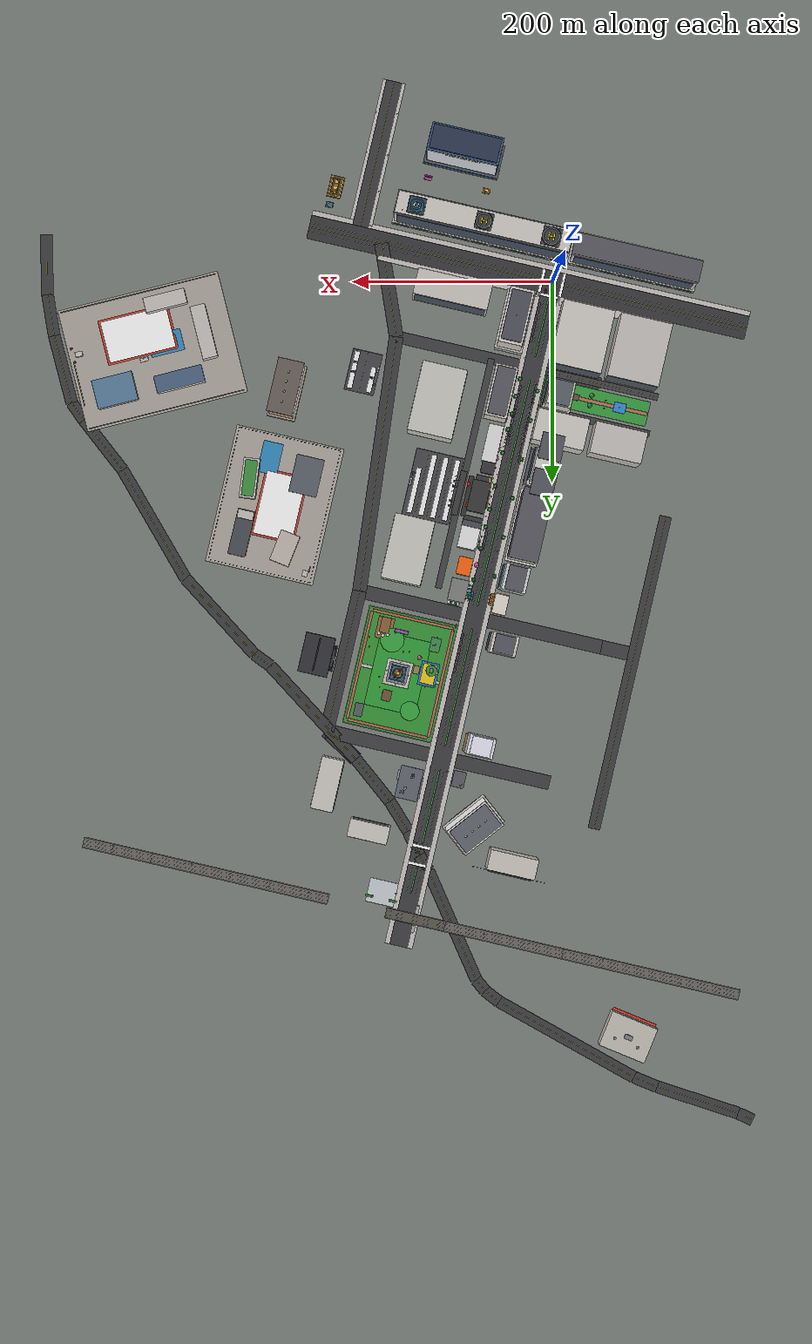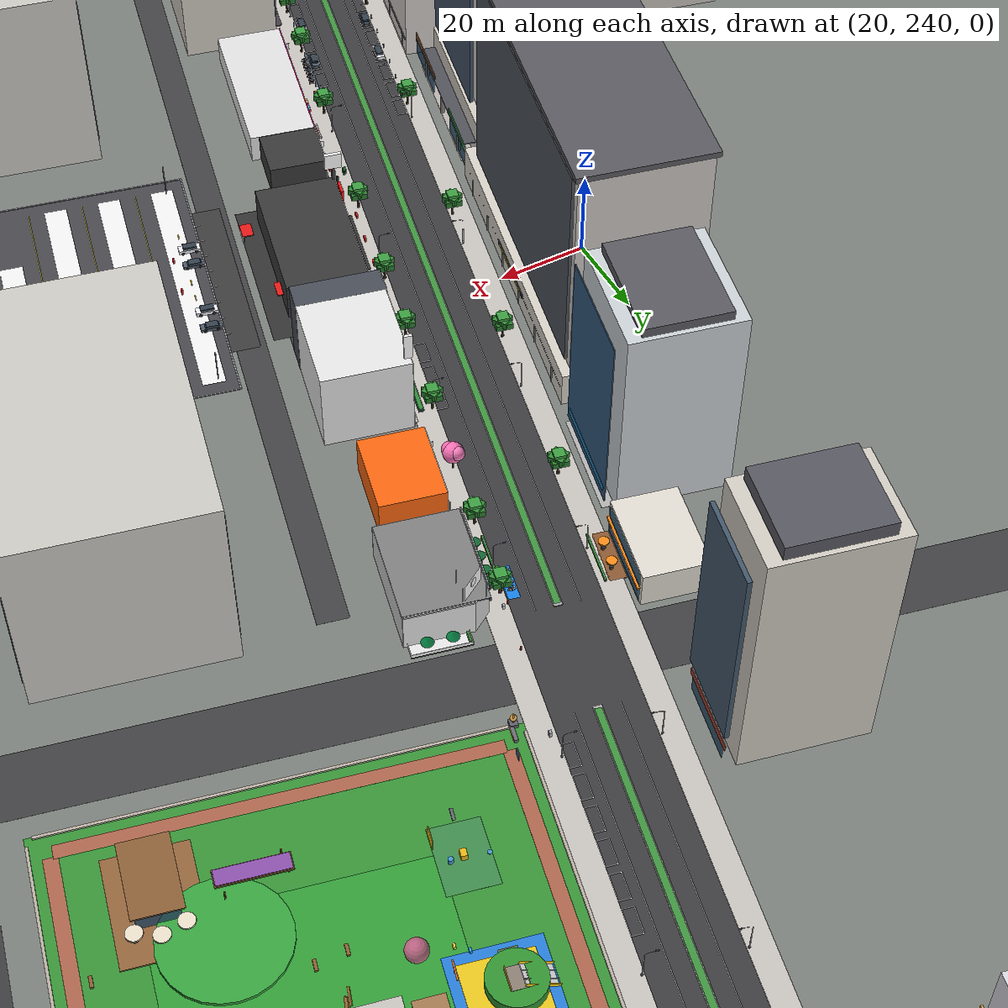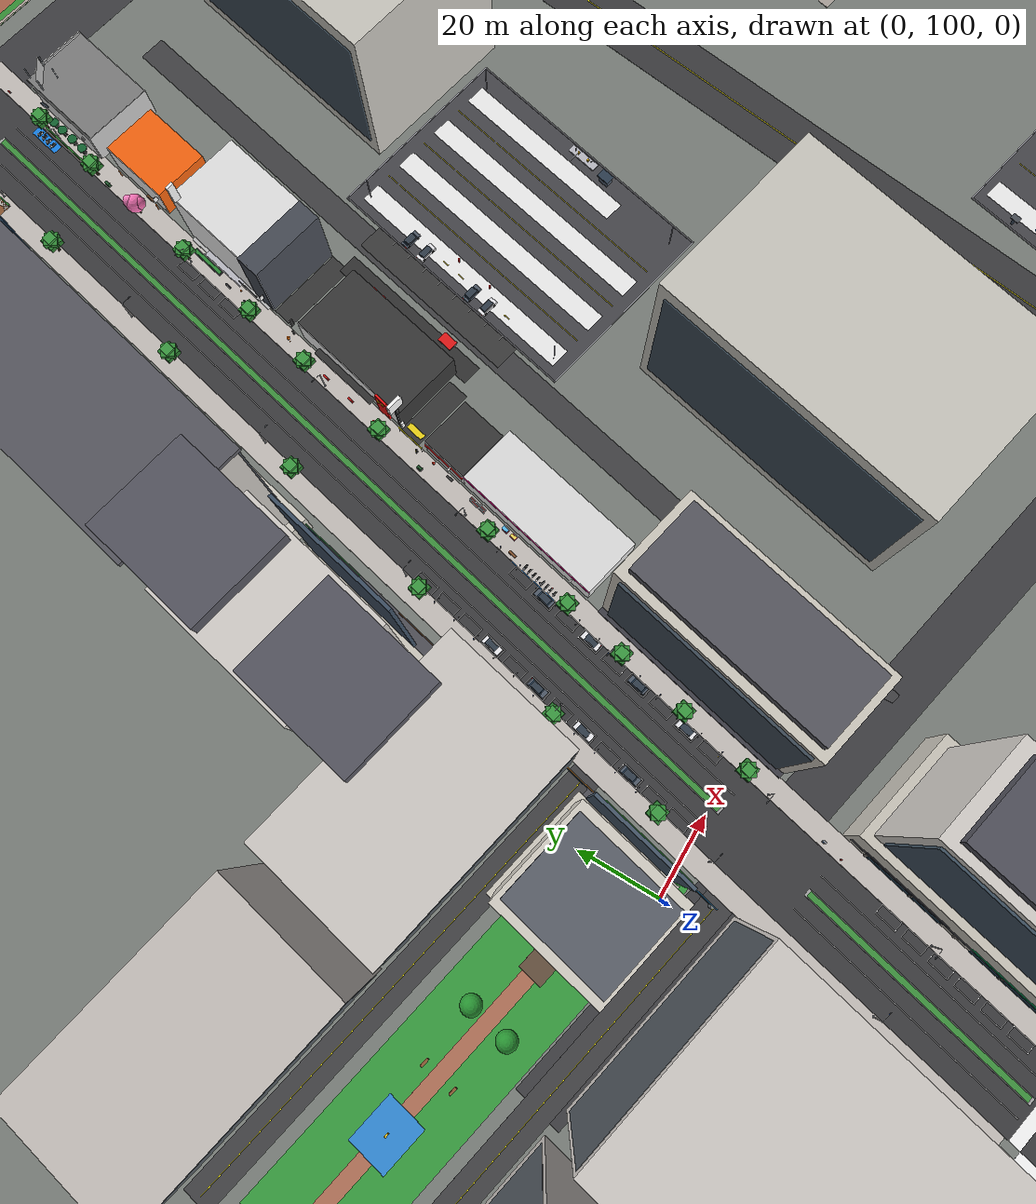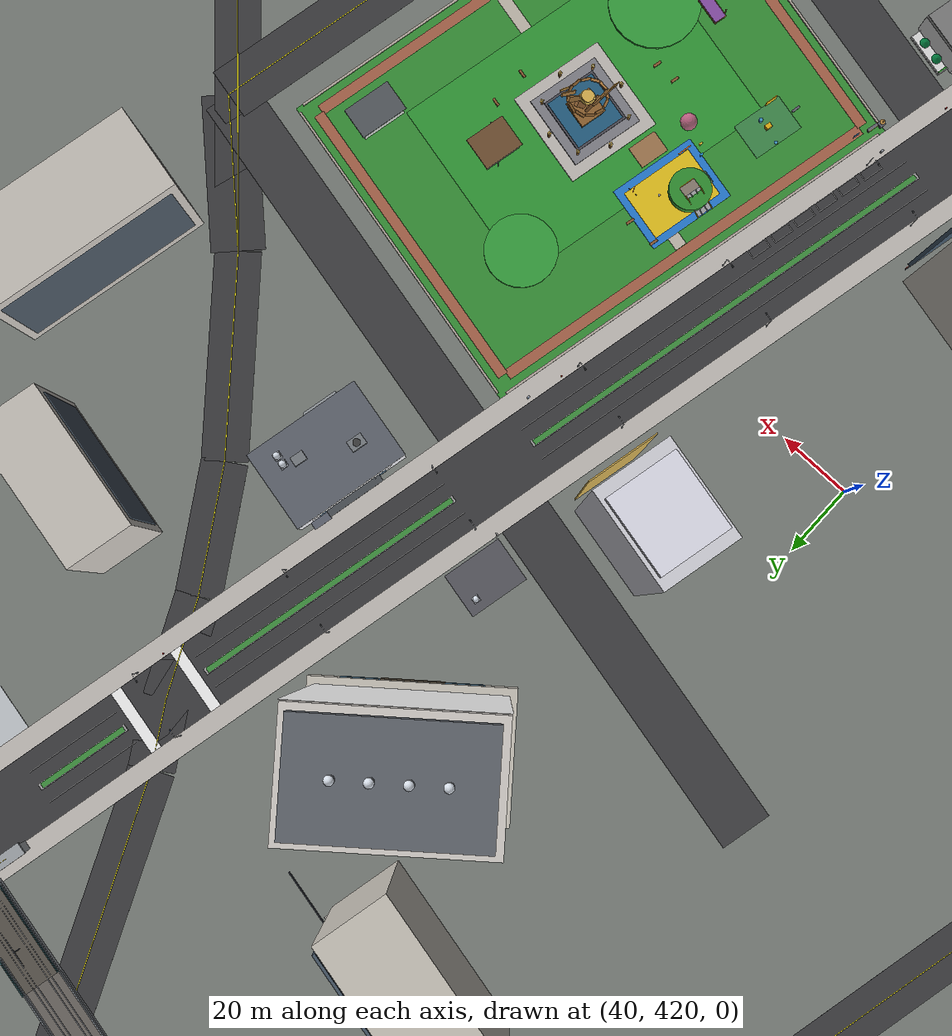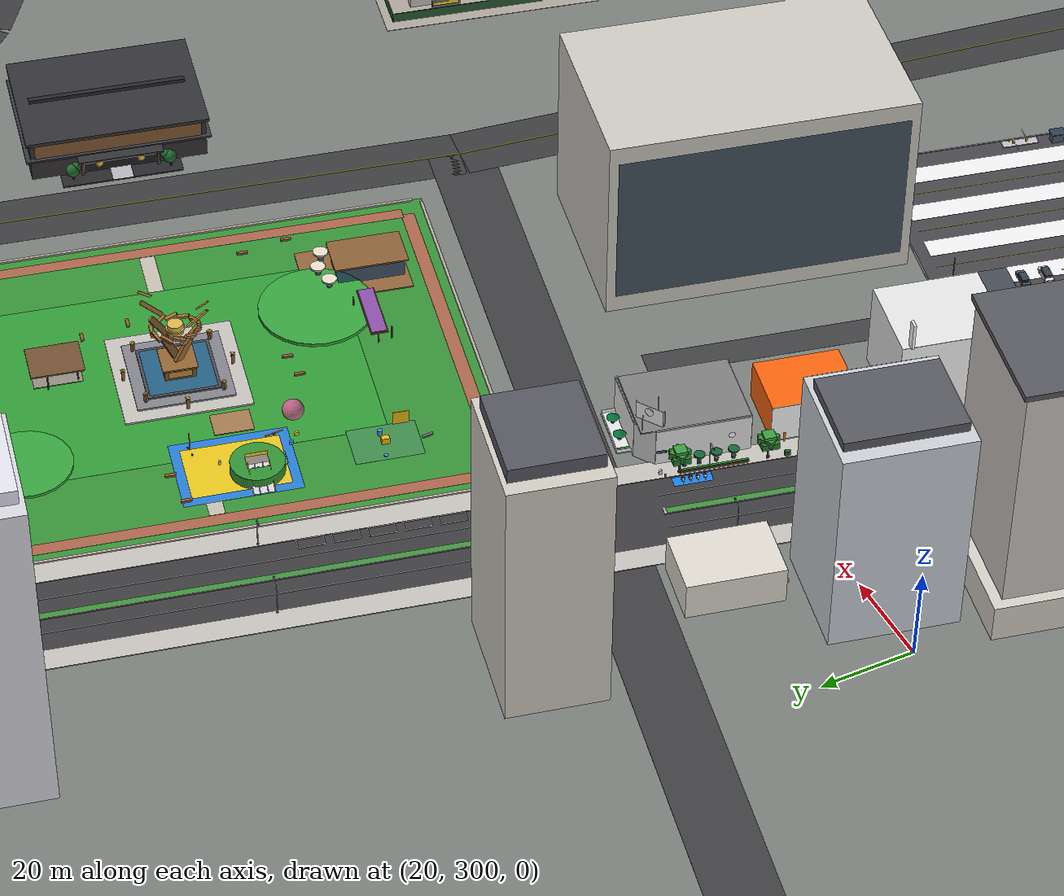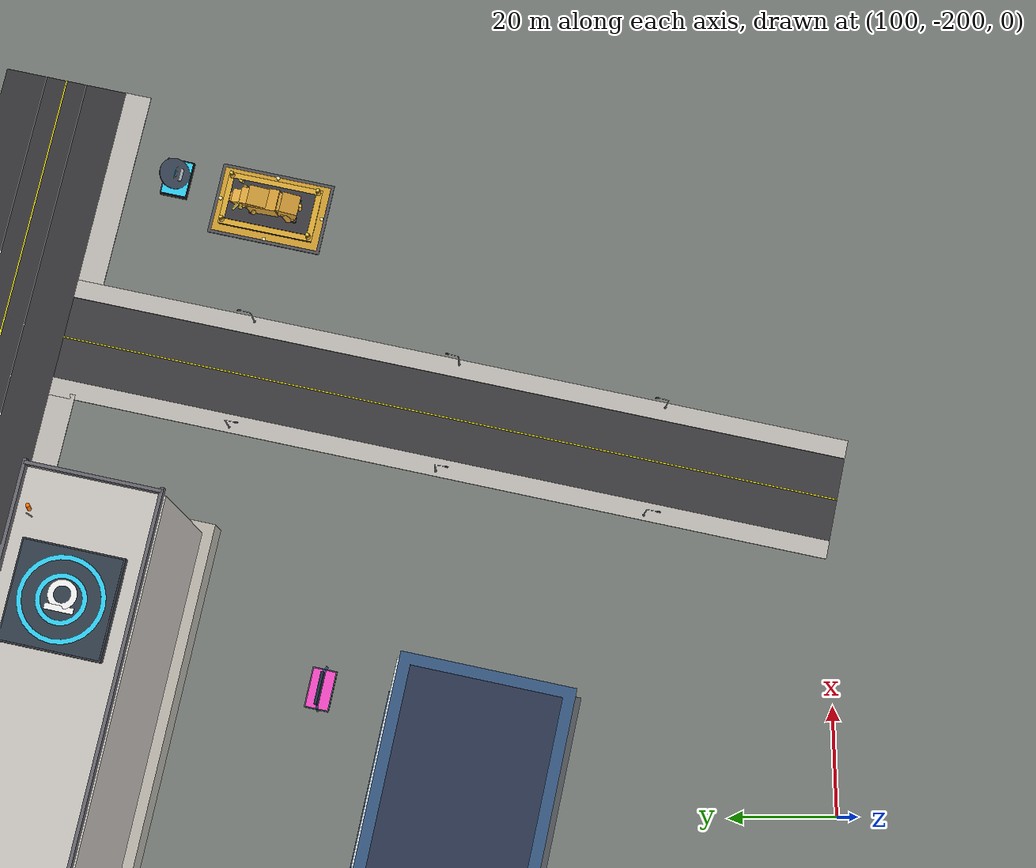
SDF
<sdf version="1.8">
 <world name="guanxin_world">
  <physics name="default_physics" type="ode" default="true">
   <max_step_size>0.002</max_step_size>
   <real_time_factor>1.0</real_time_factor>
   <real_time_update_rate>500</real_time_update_rate>
  </physics>
  <spherical_coordinates>
   <surface_model>EARTH_WGS84</surface_model>
   <world_frame_orientation>ENU</world_frame_orientation>
   <latitude_deg>24.7818444</latitude_deg>
   <longitude_deg>121.0209750</longitude_deg>
   <elevation>35.0</elevation>
   <heading_deg>0.0</heading_deg>
  </spherical_coordinates>
  <plugin filename="gz-sim-physics-system" name="gz::sim::systems::Physics"/>
  <plugin filename="gz-sim-sensors-system" name="gz::sim::systems::Sensors">
   <render_engine>ogre2</render_engine>
  </plugin>
  <plugin filename="gz-sim-user-commands-system" name="gz::sim::systems::UserCommands"/>
  <plugin filename="gz-sim-scene-broadcaster-system" name="gz::sim::systems::SceneBroadcaster"/>
  <scene>
   <ambient>0.65 0.65 0.65 1.0</ambient>
   <background>0.72 0.82 0.92 1.0</background>
   <shadows>true</shadows>
   <grid>false</grid>
  </scene>
  <light type="directional" name="sun">
   <pose>150 -60 200 0.6 0.4 -0.8</pose>
   <diffuse>0.92 0.90 0.86 1</diffuse>
   <specular>0.3 0.3 0.3 1</specular>
   <attenuation>
    <range>1000</range>
    <constant>0.9</constant>
    <linear>0.01</linear>
    <quadratic>0.001</quadratic>
   </attenuation>
   <direction>-0.4 0.2 -0.9</direction>
  </light>
  <model name="ground_plane">
   <static>true</static>
   <pose>-100 480 0 0 0 0</pose>
   <link name="ground_link">
    <collision name="ground_col">
     <geometry><plane><normal>0 0 1</normal><size>1400 1400</size></plane></geometry>
     <surface>
      <friction><ode><mu>0.9</mu><mu2>0.9</mu2></ode></friction>
      <contact><ode><kd>100000</kd><kp>10000000</kp></ode></contact>
     </surface>
    </collision>
    <visual name="ground_vis">
     <geometry><plane><normal>0 0 1</normal><size>1400 1400</size></plane></geometry>
     <material><ambient>0.42 0.44 0.42 1</ambient><diffuse>0.48 0.50 0.48 1</diffuse></material>
    </visual>
   </link>
  </model>
  <model name="road_network">
   <static>true</static>
   <link name="road_link">
    <collision name="gx_road_str_col">
     <pose>76.077 331.379 0.01 0 0 1.34512</pose>
     <geometry><box><size>680.0 18.0 0.02</size></box></geometry>
     <surface><friction><ode><mu>0.9</mu><mu2>0.9</mu2></ode></friction></surface>
    </collision>
    <visual name="gx_road_str_vis">
     <pose>76.077 331.379 0.01 0 0 1.34512</pose>
     <geometry><box><size>680.0 18.0 0.02</size></box></geometry>
     <material><ambient>0.22 0.22 0.23 1</ambient><diffuse>0.24 0.24 0.25 1</diffuse></material>
    </visual>
    <collision name="gxe_seg1_south_col">
     <pose>163.693 7.563 0.01 0 0 1.73051</pose>
     <geometry><box><size>94.97 14.0 0.02</size></box></geometry>
     <surface><friction><ode><mu>0.9</mu><mu2>0.9</mu2></ode></friction></surface>
    </collision>
    <visual name="gxe_seg1_south_vis">
     <pose>163.693 7.563 0.01 0 0 1.73051</pose>
     <geometry><box><size>94.97 14.0 0.02</size></box></geometry>
     <material><ambient>0.22 0.22 0.23 1</ambient><diffuse>0.24 0.24 0.25 1</diffuse></material>
    </visual>
    <visual name="gxe_seg1_south_line">
     <pose>163.693 7.563 0.022 0 0 1.73051</pose>
     <geometry><box><size>94.97 0.25 0.002</size></box></geometry>
     <material><ambient>0.9 0.85 0.1 1</ambient><diffuse>0.95 0.9 0.1 1</diffuse></material>
    </visual>
    <collision name="gxe_seg2_school_col">
     <pose>174.119 181.900 0.01 0 0 1.43068</pose>
     <geometry><box><size>257.44 14.0 0.02</size></box></geometry>
     <surface><friction><ode><mu>0.9</mu><mu2>0.9</mu2></ode></friction></surface>
    </collision>
    <visual name="gxe_seg2_school_vis">
     <pose>174.119 181.900 0.01 0 0 1.43068</pose>
     <geometry><box><size>257.44 14.0 0.02</size></box></geometry>
     <material><ambient>0.22 0.22 0.23 1</ambient><diffuse>0.24 0.24 0.25 1</diffuse></material>
    </visual>
    <visual name="gxe_seg2_school_line">
     <pose>174.119 181.900 0.022 0 0 1.43068</pose>
     <geometry><box><size>257.44 0.25 0.002</size></box></geometry>
     <material><ambient>0.9 0.85 0.1 1</ambient><diffuse>0.95 0.9 0.1 1</diffuse></material>
    </visual>
    <collision name="gxe_seg3_park_col">
     <pose>208.151 379.290 0.01 0 0 1.34512</pose>
     <geometry><box><size>143.50 14.0 0.02</size></box></geometry>
     <surface><friction><ode><mu>0.9</mu><mu2>0.9</mu2></ode></friction></surface>
    </collision>
    <visual name="gxe_seg3_park_vis">
     <pose>208.151 379.290 0.01 0 0 1.34512</pose>
     <geometry><box><size>143.50 14.0 0.02</size></box></geometry>
     <material><ambient>0.22 0.22 0.23 1</ambient><diffuse>0.24 0.24 0.25 1</diffuse></material>
    </visual>
    <visual name="gxe_seg3_park_line">
     <pose>208.151 379.290 0.022 0 0 1.34512</pose>
     <geometry><box><size>143.50 0.25 0.002</size></box></geometry>
     <material><ambient>0.9 0.85 0.1 1</ambient><diffuse>0.95 0.9 0.1 1</diffuse></material>
    </visual>
    <collision name="gxe_seg4_north_col">
     <pose>209.600 463.300 0.01 0 0 2.37500</pose>
     <geometry><box><size>40.60 14.0 0.02</size></box></geometry>
     <surface><friction><ode><mu>0.9</mu><mu2>0.9</mu2></ode></friction></surface>
    </collision>
    <visual name="gxe_seg4_north_vis">
     <pose>209.600 463.300 0.01 0 0 2.37500</pose>
     <geometry><box><size>40.60 14.0 0.02</size></box></geometry>
     <material><ambient>0.22 0.22 0.23 1</ambient><diffuse>0.24 0.24 0.25 1</diffuse></material>
    </visual>
    <visual name="gxe_seg4_north_line">
     <pose>209.600 463.300 0.022 0 0 2.37500</pose>
     <geometry><box><size>40.60 0.25 0.002</size></box></geometry>
     <material><ambient>0.9 0.85 0.1 1</ambient><diffuse>0.95 0.9 0.1 1</diffuse></material>
    </visual>
    <collision name="guangfu_road_col">
     <pose>24.366 -5.594 0.01 0 0 -0.22568</pose>
     <geometry><box><size>450.0 24.0 0.02</size></box></geometry>
     <surface><friction><ode><mu>0.9</mu><mu2>0.9</mu2></ode></friction></surface>
    </collision>
    <visual name="guangfu_road_vis">
     <pose>24.366 -5.594 0.01 0 0 -0.22568</pose>
     <geometry><box><size>450.0 24.0 0.02</size></box></geometry>
     <material><ambient>0.20 0.20 0.21 1</ambient><diffuse>0.22 0.22 0.23 1</diffuse></material>
    </visual>
    <collision name="gx1_east_col">
     <pose>92.302 69.098 0.01 0 0 -0.22568</pose>
     <geometry><box><size>131.0 12.0 0.02</size></box></geometry>
     <surface><friction><ode><mu>0.9</mu><mu2>0.9</mu2></ode></friction></surface>
    </collision>
    <visual name="gx1_east_vis">
     <pose>92.302 69.098 0.01 0 0 -0.22568</pose>
     <geometry><box><size>131.0 12.0 0.02</size></box></geometry>
     <material><ambient>0.23 0.23 0.24 1</ambient><diffuse>0.25 0.25 0.26 1</diffuse></material>
    </visual>
    <collision name="gx1_west_col">
     <pose>-19.294 94.719 0.01 0 0 -0.22568</pose>
     <geometry><box><size>60.0 12.0 0.02</size></box></geometry>
     <surface><friction><ode><mu>0.9</mu><mu2>0.9</mu2></ode></friction></surface>
    </collision>
    <visual name="gx1_west_vis">
     <pose>-19.294 94.719 0.01 0 0 -0.22568</pose>
     <geometry><box><size>60.0 12.0 0.02</size></box></geometry>
     <material><ambient>0.23 0.23 0.24 1</ambient><diffuse>0.25 0.25 0.26 1</diffuse></material>
    </visual>
    <collision name="gx2_east_col">
     <pose>138.978 321.555 0.01 0 0 -0.22568</pose>
     <geometry><box><size>109.0 14.0 0.02</size></box></geometry>
     <surface><friction><ode><mu>0.9</mu><mu2>0.9</mu2></ode></friction></surface>
    </collision>
    <visual name="gx2_east_vis">
     <pose>138.978 321.555 0.01 0 0 -0.22568</pose>
     <geometry><box><size>109.0 14.0 0.02</size></box></geometry>
     <material><ambient>0.23 0.23 0.24 1</ambient><diffuse>0.25 0.25 0.26 1</diffuse></material>
    </visual>
    <collision name="gx2_west_col">
     <pose>8.863 351.428 0.01 0 0 -0.22568</pose>
     <geometry><box><size>120.0 14.0 0.02</size></box></geometry>
     <surface><friction><ode><mu>0.9</mu><mu2>0.9</mu2></ode></friction></surface>
    </collision>
    <visual name="gx2_west_vis">
     <pose>8.863 351.428 0.01 0 0 -0.22568</pose>
     <geometry><box><size>120.0 14.0 0.02</size></box></geometry>
     <material><ambient>0.23 0.23 0.24 1</ambient><diffuse>0.25 0.25 0.26 1</diffuse></material>
    </visual>
    <collision name="gxn_east_col">
     <pose>171.089 461.416 0.01 0 0 -0.22568</pose>
     <geometry><box><size>109.0 14.0 0.02</size></box></geometry>
     <surface><friction><ode><mu>0.9</mu><mu2>0.9</mu2></ode></friction></surface>
    </collision>
    <visual name="gxn_east_vis">
     <pose>171.089 461.416 0.01 0 0 -0.22568</pose>
     <geometry><box><size>109.0 14.0 0.02</size></box></geometry>
     <material><ambient>0.23 0.23 0.24 1</ambient><diffuse>0.25 0.25 0.26 1</diffuse></material>
    </visual>
    <collision name="gxn_west_col">
     <pose>50.720 489.052 0.01 0 0 -0.22568</pose>
     <geometry><box><size>100.0 14.0 0.02</size></box></geometry>
     <surface><friction><ode><mu>0.9</mu><mu2>0.9</mu2></ode></friction></surface>
    </collision>
    <visual name="gxn_west_vis">
     <pose>50.720 489.052 0.01 0 0 -0.22568</pose>
     <geometry><box><size>100.0 14.0 0.02</size></box></geometry>
     <material><ambient>0.23 0.23 0.24 1</ambient><diffuse>0.25 0.25 0.26 1</diffuse></material>
    </visual>
    <collision name="service_alley_col">
     <pose>87.031 191.378 0.01 0 0 1.34512</pose>
     <geometry><box><size>236.0 6.5 0.02</size></box></geometry>
     <surface><friction><ode><mu>0.9</mu><mu2>0.9</mu2></ode></friction></surface>
    </collision>
    <visual name="service_alley_vis">
     <pose>87.031 191.378 0.01 0 0 1.34512</pose>
     <geometry><box><size>236.0 6.5 0.02</size></box></geometry>
     <material><ambient>0.24 0.24 0.25 1</ambient><diffuse>0.26 0.26 0.27 1</diffuse></material>
    </visual>
    <collision name="gd_road_seg_00_col">
     <pose>506.405 -17.056 0.01 0 0 1.59791</pose>
     <geometry><box><size>60.28 12.0 0.02</size></box></geometry>
     <surface><friction><ode><mu>0.9</mu><mu2>0.9</mu2></ode></friction></surface>
    </collision>
    <visual name="gd_road_seg_00_vis">
     <pose>506.405 -17.056 0.01 0 0 1.59791</pose>
     <geometry><box><size>60.28 12.0 0.02</size></box></geometry>
     <material><ambient>0.22 0.22 0.23 1</ambient><diffuse>0.24 0.24 0.25 1</diffuse></material>
    </visual>
    <visual name="gd_road_seg_00_line">
     <pose>506.405 -17.056 0.022 0 0 1.59791</pose>
     <geometry><box><size>60.28 0.25 0.002</size></box></geometry>
     <material><ambient>0.9 0.85 0.1 1</ambient><diffuse>0.95 0.9 0.1 1</diffuse></material>
    </visual>
    <collision name="gd_road_seg_01_col">
     <pose>502.109 33.756 0.01 0 0 1.73744</pose>
     <geometry><box><size>41.95 12.0 0.02</size></box></geometry>
     <surface><friction><ode><mu>0.9</mu><mu2>0.9</mu2></ode></friction></surface>
    </collision>
    <visual name="gd_road_seg_01_vis">
     <pose>502.109 33.756 0.01 0 0 1.73744</pose>
     <geometry><box><size>41.95 12.0 0.02</size></box></geometry>
     <material><ambient>0.22 0.22 0.23 1</ambient><diffuse>0.24 0.24 0.25 1</diffuse></material>
    </visual>
    <visual name="gd_road_seg_01_line">
     <pose>502.109 33.756 0.022 0 0 1.73744</pose>
     <geometry><box><size>41.95 0.25 0.002</size></box></geometry>
     <material><ambient>0.9 0.85 0.1 1</ambient><diffuse>0.95 0.9 0.1 1</diffuse></material>
    </visual>
    <collision name="gd_road_seg_02_col">
     <pose>489.643 88.104 0.01 0 0 1.83167</pose>
     <geometry><box><size>69.68 12.0 0.02</size></box></geometry>
     <surface><friction><ode><mu>0.9</mu><mu2>0.9</mu2></ode></friction></surface>
    </collision>
    <visual name="gd_road_seg_02_vis">
     <pose>489.643 88.104 0.01 0 0 1.83167</pose>
     <geometry><box><size>69.68 12.0 0.02</size></box></geometry>
     <material><ambient>0.22 0.22 0.23 1</ambient><diffuse>0.24 0.24 0.25 1</diffuse></material>
    </visual>
    <visual name="gd_road_seg_02_line">
     <pose>489.643 88.104 0.022 0 0 1.83167</pose>
     <geometry><box><size>69.68 0.25 0.002</size></box></geometry>
     <material><ambient>0.9 0.85 0.1 1</ambient><diffuse>0.95 0.9 0.1 1</diffuse></material>
    </visual>
    <collision name="gd_road_seg_03_col">
     <pose>474.541 130.450 0.01 0 0 2.18440</pose>
     <geometry><box><size>21.24 12.0 0.02</size></box></geometry>
     <surface><friction><ode><mu>0.9</mu><mu2>0.9</mu2></ode></friction></surface>
    </collision>
    <visual name="gd_road_seg_03_vis">
     <pose>474.541 130.450 0.01 0 0 2.18440</pose>
     <geometry><box><size>21.24 12.0 0.02</size></box></geometry>
     <material><ambient>0.22 0.22 0.23 1</ambient><diffuse>0.24 0.24 0.25 1</diffuse></material>
    </visual>
    <visual name="gd_road_seg_03_line">
     <pose>474.541 130.450 0.022 0 0 2.18440</pose>
     <geometry><box><size>21.24 0.25 0.002</size></box></geometry>
     <material><ambient>0.9 0.85 0.1 1</ambient><diffuse>0.95 0.9 0.1 1</diffuse></material>
    </visual>
    <collision name="gd_road_seg_04_col">
     <pose>448.836 164.071 0.01 0 0 2.23666</pose>
     <geometry><box><size>63.43 12.0 0.02</size></box></geometry>
     <surface><friction><ode><mu>0.9</mu><mu2>0.9</mu2></ode></friction></surface>
    </collision>
    <visual name="gd_road_seg_04_vis">
     <pose>448.836 164.071 0.01 0 0 2.23666</pose>
     <geometry><box><size>63.43 12.0 0.02</size></box></geometry>
     <material><ambient>0.22 0.22 0.23 1</ambient><diffuse>0.24 0.24 0.25 1</diffuse></material>
    </visual>
    <visual name="gd_road_seg_04_line">
     <pose>448.836 164.071 0.022 0 0 2.23666</pose>
     <geometry><box><size>63.43 0.25 0.002</size></box></geometry>
     <material><ambient>0.9 0.85 0.1 1</ambient><diffuse>0.95 0.9 0.1 1</diffuse></material>
    </visual>
    <collision name="gd_road_seg_05_col">
     <pose>397.507 243.280 0.01 0 0 2.09998</pose>
     <geometry><box><size>125.74 12.0 0.02</size></box></geometry>
     <surface><friction><ode><mu>0.9</mu><mu2>0.9</mu2></ode></friction></surface>
    </collision>
    <visual name="gd_road_seg_05_vis">
     <pose>397.507 243.280 0.01 0 0 2.09998</pose>
     <geometry><box><size>125.74 12.0 0.02</size></box></geometry>
     <material><ambient>0.22 0.22 0.23 1</ambient><diffuse>0.24 0.24 0.25 1</diffuse></material>
    </visual>
    <visual name="gd_road_seg_05_line">
     <pose>397.507 243.280 0.022 0 0 2.09998</pose>
     <geometry><box><size>125.74 0.25 0.002</size></box></geometry>
     <material><ambient>0.9 0.85 0.1 1</ambient><diffuse>0.95 0.9 0.1 1</diffuse></material>
    </visual>
    <collision name="gd_road_seg_06_col">
     <pose>331.341 335.157 0.01 0 0 2.31209</pose>
     <geometry><box><size>101.97 12.0 0.02</size></box></geometry>
     <surface><friction><ode><mu>0.9</mu><mu2>0.9</mu2></ode></friction></surface>
    </collision>
    <visual name="gd_road_seg_06_vis">
     <pose>331.341 335.157 0.01 0 0 2.31209</pose>
     <geometry><box><size>101.97 12.0 0.02</size></box></geometry>
     <material><ambient>0.22 0.22 0.23 1</ambient><diffuse>0.24 0.24 0.25 1</diffuse></material>
    </visual>
    <visual name="gd_road_seg_06_line">
     <pose>331.341 335.157 0.022 0 0 2.31209</pose>
     <geometry><box><size>101.97 0.25 0.002</size></box></geometry>
     <material><ambient>0.9 0.85 0.1 1</ambient><diffuse>0.95 0.9 0.1 1</diffuse></material>
    </visual>
    <collision name="gd_road_seg_07_col">
     <pose>288.878 378.582 0.01 0 0 2.51480</pose>
     <geometry><box><size>19.85 12.0 0.02</size></box></geometry>
     <surface><friction><ode><mu>0.9</mu><mu2>0.9</mu2></ode></friction></surface>
    </collision>
    <visual name="gd_road_seg_07_vis">
     <pose>288.878 378.582 0.01 0 0 2.51480</pose>
     <geometry><box><size>19.85 12.0 0.02</size></box></geometry>
     <material><ambient>0.22 0.22 0.23 1</ambient><diffuse>0.24 0.24 0.25 1</diffuse></material>
    </visual>
    <visual name="gd_road_seg_07_line">
     <pose>288.878 378.582 0.022 0 0 2.51480</pose>
     <geometry><box><size>19.85 0.25 0.002</size></box></geometry>
     <material><ambient>0.9 0.85 0.1 1</ambient><diffuse>0.95 0.9 0.1 1</diffuse></material>
    </visual>
    <collision name="gd_road_seg_08_col">
     <pose>237.911 430.907 0.01 0 0 2.31625</pose>
     <geometry><box><size>126.58 12.0 0.02</size></box></geometry>
     <surface><friction><ode><mu>0.9</mu><mu2>0.9</mu2></ode></friction></surface>
    </collision>
    <visual name="gd_road_seg_08_vis">
     <pose>237.911 430.907 0.01 0 0 2.31625</pose>
     <geometry><box><size>126.58 12.0 0.02</size></box></geometry>
     <material><ambient>0.22 0.22 0.23 1</ambient><diffuse>0.24 0.24 0.25 1</diffuse></material>
    </visual>
    <visual name="gd_road_seg_08_line">
     <pose>237.911 430.907 0.022 0 0 2.31625</pose>
     <geometry><box><size>126.58 0.25 0.002</size></box></geometry>
     <material><ambient>0.9 0.85 0.1 1</ambient><diffuse>0.95 0.9 0.1 1</diffuse></material>
    </visual>
    <collision name="gd_road_seg_09_col">
     <pose>178.084 498.300 0.01 0 0 2.25097</pose>
     <geometry><box><size>53.73 12.0 0.02</size></box></geometry>
     <surface><friction><ode><mu>0.9</mu><mu2>0.9</mu2></ode></friction></surface>
    </collision>
    <visual name="gd_road_seg_09_vis">
     <pose>178.084 498.300 0.01 0 0 2.25097</pose>
     <geometry><box><size>53.73 12.0 0.02</size></box></geometry>
     <material><ambient>0.22 0.22 0.23 1</ambient><diffuse>0.24 0.24 0.25 1</diffuse></material>
    </visual>
    <visual name="gd_road_seg_09_line">
     <pose>178.084 498.300 0.022 0 0 2.25097</pose>
     <geometry><box><size>53.73 0.25 0.002</size></box></geometry>
     <material><ambient>0.9 0.85 0.1 1</ambient><diffuse>0.95 0.9 0.1 1</diffuse></material>
    </visual>
    <collision name="gd_road_seg_10_col">
     <pose>152.087 533.944 0.01 0 0 2.12334</pose>
     <geometry><box><size>34.67 12.0 0.02</size></box></geometry>
     <surface><friction><ode><mu>0.9</mu><mu2>0.9</mu2></ode></friction></surface>
    </collision>
    <visual name="gd_road_seg_10_vis">
     <pose>152.087 533.944 0.01 0 0 2.12334</pose>
     <geometry><box><size>34.67 12.0 0.02</size></box></geometry>
     <material><ambient>0.22 0.22 0.23 1</ambient><diffuse>0.24 0.24 0.25 1</diffuse></material>
    </visual>
    <visual name="gd_road_seg_10_line">
     <pose>152.087 533.944 0.022 0 0 2.12334</pose>
     <geometry><box><size>34.67 0.25 0.002</size></box></geometry>
     <material><ambient>0.9 0.85 0.1 1</ambient><diffuse>0.95 0.9 0.1 1</diffuse></material>
    </visual>
    <collision name="gd_road_seg_11_col">
     <pose>137.283 560.899 0.01 0 0 2.00827</pose>
     <geometry><box><size>26.93 12.0 0.02</size></box></geometry>
     <surface><friction><ode><mu>0.9</mu><mu2>0.9</mu2></ode></friction></surface>
    </collision>
    <visual name="gd_road_seg_11_vis">
     <pose>137.283 560.899 0.01 0 0 2.00827</pose>
     <geometry><box><size>26.93 12.0 0.02</size></box></geometry>
     <material><ambient>0.22 0.22 0.23 1</ambient><diffuse>0.24 0.24 0.25 1</diffuse></material>
    </visual>
    <visual name="gd_road_seg_11_line">
     <pose>137.283 560.899 0.022 0 0 2.00827</pose>
     <geometry><box><size>26.93 0.25 0.002</size></box></geometry>
     <material><ambient>0.9 0.85 0.1 1</ambient><diffuse>0.95 0.9 0.1 1</diffuse></material>
    </visual>
    <collision name="gd_road_seg_12_col">
     <pose>127.015 580.657 0.01 0 0 2.11382</pose>
     <geometry><box><size>17.66 12.0 0.02</size></box></geometry>
     <surface><friction><ode><mu>0.9</mu><mu2>0.9</mu2></ode></friction></surface>
    </collision>
    <visual name="gd_road_seg_12_vis">
     <pose>127.015 580.657 0.01 0 0 2.11382</pose>
     <geometry><box><size>17.66 12.0 0.02</size></box></geometry>
     <material><ambient>0.22 0.22 0.23 1</ambient><diffuse>0.24 0.24 0.25 1</diffuse></material>
    </visual>
    <visual name="gd_road_seg_12_line">
     <pose>127.015 580.657 0.022 0 0 2.11382</pose>
     <geometry><box><size>17.66 0.25 0.002</size></box></geometry>
     <material><ambient>0.9 0.85 0.1 1</ambient><diffuse>0.95 0.9 0.1 1</diffuse></material>
    </visual>
    <collision name="gd_road_seg_13_col">
     <pose>98.574 642.310 0.01 0 0 1.98650</pose>
     <geometry><box><size>118.26 12.0 0.02</size></box></geometry>
     <surface><friction><ode><mu>0.9</mu><mu2>0.9</mu2></ode></friction></surface>
    </collision>
    <visual name="gd_road_seg_13_vis">
     <pose>98.574 642.310 0.01 0 0 1.98650</pose>
     <geometry><box><size>118.26 12.0 0.02</size></box></geometry>
     <material><ambient>0.22 0.22 0.23 1</ambient><diffuse>0.24 0.24 0.25 1</diffuse></material>
    </visual>
    <visual name="gd_road_seg_13_line">
     <pose>98.574 642.310 0.022 0 0 1.98650</pose>
     <geometry><box><size>118.26 0.25 0.002</size></box></geometry>
     <material><ambient>0.9 0.85 0.1 1</ambient><diffuse>0.95 0.9 0.1 1</diffuse></material>
    </visual>
    <collision name="gd_road_seg_14_col">
     <pose>70.274 701.765 0.01 0 0 2.26036</pose>
     <geometry><box><size>13.90 12.0 0.02</size></box></geometry>
     <surface><friction><ode><mu>0.9</mu><mu2>0.9</mu2></ode></friction></surface>
    </collision>
    <visual name="gd_road_seg_14_vis">
     <pose>70.274 701.765 0.01 0 0 2.26036</pose>
     <geometry><box><size>13.90 12.0 0.02</size></box></geometry>
     <material><ambient>0.22 0.22 0.23 1</ambient><diffuse>0.24 0.24 0.25 1</diffuse></material>
    </visual>
    <visual name="gd_road_seg_14_line">
     <pose>70.274 701.765 0.022 0 0 2.26036</pose>
     <geometry><box><size>13.90 0.25 0.002</size></box></geometry>
     <material><ambient>0.9 0.85 0.1 1</ambient><diffuse>0.95 0.9 0.1 1</diffuse></material>
    </visual>
    <collision name="gd_road_seg_15_col">
     <pose>59.017 712.393 0.01 0 0 2.48515</pose>
     <geometry><box><size>17.25 12.0 0.02</size></box></geometry>
     <surface><friction><ode><mu>0.9</mu><mu2>0.9</mu2></ode></friction></surface>
    </collision>
    <visual name="gd_road_seg_15_vis">
     <pose>59.017 712.393 0.01 0 0 2.48515</pose>
     <geometry><box><size>17.25 12.0 0.02</size></box></geometry>
     <material><ambient>0.22 0.22 0.23 1</ambient><diffuse>0.24 0.24 0.25 1</diffuse></material>
    </visual>
    <visual name="gd_road_seg_15_line">
     <pose>59.017 712.393 0.022 0 0 2.48515</pose>
     <geometry><box><size>17.25 0.25 0.002</size></box></geometry>
     <material><ambient>0.9 0.85 0.1 1</ambient><diffuse>0.95 0.9 0.1 1</diffuse></material>
    </visual>
    <collision name="gd_road_seg_16_col">
     <pose>-14.908 754.894 0.01 0 0 2.63492</pose>
     <geometry><box><size>153.46 12.0 0.02</size></box></geometry>
     <surface><friction><ode><mu>0.9</mu><mu2>0.9</mu2></ode></friction></surface>
    </collision>
    <visual name="gd_road_seg_16_vis">
     <pose>-14.908 754.894 0.01 0 0 2.63492</pose>
     <geometry><box><size>153.46 12.0 0.02</size></box></geometry>
     <material><ambient>0.22 0.22 0.23 1</ambient><diffuse>0.24 0.24 0.25 1</diffuse></material>
    </visual>
    <visual name="gd_road_seg_16_line">
     <pose>-14.908 754.894 0.022 0 0 2.63492</pose>
     <geometry><box><size>153.46 0.25 0.002</size></box></geometry>
     <material><ambient>0.9 0.85 0.1 1</ambient><diffuse>0.95 0.9 0.1 1</diffuse></material>
    </visual>
    <collision name="gd_road_seg_17_col">
     <pose>-93.581 796.852 0.01 0 0 2.75440</pose>
     <geometry><box><size>25.02 12.0 0.02</size></box></geometry>
     <surface><friction><ode><mu>0.9</mu><mu2>0.9</mu2></ode></friction></surface>
    </collision>
    <visual name="gd_road_seg_17_vis">
     <pose>-93.581 796.852 0.01 0 0 2.75440</pose>
     <geometry><box><size>25.02 12.0 0.02</size></box></geometry>
     <material><ambient>0.22 0.22 0.23 1</ambient><diffuse>0.24 0.24 0.25 1</diffuse></material>
    </visual>
    <visual name="gd_road_seg_17_line">
     <pose>-93.581 796.852 0.022 0 0 2.75440</pose>
     <geometry><box><size>25.02 0.25 0.002</size></box></geometry>
     <material><ambient>0.9 0.85 0.1 1</ambient><diffuse>0.95 0.9 0.1 1</diffuse></material>
    </visual>
    <collision name="gd_road_seg_18_col">
     <pose>-145.386 814.517 0.01 0 0 2.83030</pose>
     <geometry><box><size>84.50 12.0 0.02</size></box></geometry>
     <surface><friction><ode><mu>0.9</mu><mu2>0.9</mu2></ode></friction></surface>
    </collision>
    <visual name="gd_road_seg_18_vis">
     <pose>-145.386 814.517 0.01 0 0 2.83030</pose>
     <geometry><box><size>84.50 12.0 0.02</size></box></geometry>
     <material><ambient>0.22 0.22 0.23 1</ambient><diffuse>0.24 0.24 0.25 1</diffuse></material>
    </visual>
    <visual name="gd_road_seg_18_line">
     <pose>-145.386 814.517 0.022 0 0 2.83030</pose>
     <geometry><box><size>84.50 0.25 0.002</size></box></geometry>
     <material><ambient>0.9 0.85 0.1 1</ambient><diffuse>0.95 0.9 0.1 1</diffuse></material>
    </visual>
    <collision name="gd_road_seg_19_col">
     <pose>-192.927 830.869 0.01 0 0 2.70566</pose>
     <geometry><box><size>16.15 12.0 0.02</size></box></geometry>
     <surface><friction><ode><mu>0.9</mu><mu2>0.9</mu2></ode></friction></surface>
    </collision>
    <visual name="gd_road_seg_19_vis">
     <pose>-192.927 830.869 0.01 0 0 2.70566</pose>
     <geometry><box><size>16.15 12.0 0.02</size></box></geometry>
     <material><ambient>0.22 0.22 0.23 1</ambient><diffuse>0.24 0.24 0.25 1</diffuse></material>
    </visual>
    <visual name="gd_road_seg_19_line">
     <pose>-192.927 830.869 0.022 0 0 2.70566</pose>
     <geometry><box><size>16.15 0.25 0.002</size></box></geometry>
     <material><ambient>0.9 0.85 0.1 1</ambient><diffuse>0.95 0.9 0.1 1</diffuse></material>
    </visual>
    <collision name="median_s1_col">
     <pose>10.293 44.834 0.10 0 0 1.34512</pose>
     <geometry><box><size>60.00 1.8 0.20</size></box></geometry>
    </collision>
    <visual name="median_s1_curb">
     <pose>10.293 44.834 0.10 0 0 1.34512</pose>
     <geometry><box><size>60.00 1.8 0.20</size></box></geometry>
     <material><ambient>0.6 0.6 0.6 1</ambient><diffuse>0.65 0.65 0.65 1</diffuse></material>
    </visual>
    <visual name="median_s1_lawn">
     <pose>10.293 44.834 0.205 0 0 1.34512</pose>
     <geometry><box><size>58.80 1.4 0.01</size></box></geometry>
     <material><ambient>0.20 0.52 0.20 1</ambient><diffuse>0.25 0.58 0.25 1</diffuse></material>
    </visual>
    <collision name="median_mid_col">
     <pose>48.334 210.523 0.10 0 0 1.34512</pose>
     <geometry><box><size>232.00 1.8 0.20</size></box></geometry>
    </collision>
    <visual name="median_mid_curb">
     <pose>48.334 210.523 0.10 0 0 1.34512</pose>
     <geometry><box><size>232.00 1.8 0.20</size></box></geometry>
     <material><ambient>0.6 0.6 0.6 1</ambient><diffuse>0.65 0.65 0.65 1</diffuse></material>
    </visual>
    <visual name="median_mid_lawn">
     <pose>48.334 210.523 0.205 0 0 1.34512</pose>
     <geometry><box><size>230.80 1.4 0.01</size></box></geometry>
     <material><ambient>0.20 0.52 0.20 1</ambient><diffuse>0.25 0.58 0.25 1</diffuse></material>
    </visual>
    <collision name="median_n1_col">
     <pose>93.087 405.451 0.10 0 0 1.34512</pose>
     <geometry><box><size>120.00 1.8 0.20</size></box></geometry>
    </collision>
    <visual name="median_n1_curb">
     <pose>93.087 405.451 0.10 0 0 1.34512</pose>
     <geometry><box><size>120.00 1.8 0.20</size></box></geometry>
     <material><ambient>0.6 0.6 0.6 1</ambient><diffuse>0.65 0.65 0.65 1</diffuse></material>
    </visual>
    <visual name="median_n1_lawn">
     <pose>93.087 405.451 0.205 0 0 1.34512</pose>
     <geometry><box><size>118.80 1.4 0.01</size></box></geometry>
     <material><ambient>0.20 0.52 0.20 1</ambient><diffuse>0.25 0.58 0.25 1</diffuse></material>
    </visual>
    <collision name="median_n2_col">
     <pose>120.387 524.358 0.10 0 0 1.34512</pose>
     <geometry><box><size>76.00 1.8 0.20</size></box></geometry>
    </collision>
    <visual name="median_n2_curb">
     <pose>120.387 524.358 0.10 0 0 1.34512</pose>
     <geometry><box><size>76.00 1.8 0.20</size></box></geometry>
     <material><ambient>0.6 0.6 0.6 1</ambient><diffuse>0.65 0.65 0.65 1</diffuse></material>
    </visual>
    <visual name="median_n2_lawn">
     <pose>120.387 524.358 0.205 0 0 1.34512</pose>
     <geometry><box><size>74.80 1.4 0.01</size></box></geometry>
     <material><ambient>0.20 0.52 0.20 1</ambient><diffuse>0.25 0.58 0.25 1</diffuse></material>
    </visual>
    <collision name="median_n3_col">
     <pose>137.170 597.456 0.10 0 0 1.34512</pose>
     <geometry><box><size>26.00 1.8 0.20</size></box></geometry>
    </collision>
    <visual name="median_n3_curb">
     <pose>137.170 597.456 0.10 0 0 1.34512</pose>
     <geometry><box><size>26.00 1.8 0.20</size></box></geometry>
     <material><ambient>0.6 0.6 0.6 1</ambient><diffuse>0.65 0.65 0.65 1</diffuse></material>
    </visual>
    <visual name="median_n3_lawn">
     <pose>137.170 597.456 0.205 0 0 1.34512</pose>
     <geometry><box><size>24.80 1.4 0.01</size></box></geometry>
     <material><ambient>0.20 0.52 0.20 1</ambient><diffuse>0.25 0.58 0.25 1</diffuse></material>
    </visual>
    <visual name="dash_r_16">
     <pose>14.679 43.827 0.022 0 0 1.34512</pose>
     <geometry><box><size>60.00 0.15 0.002</size></box></geometry>
     <material><ambient>0.92 0.92 0.92 1</ambient><diffuse>0.95 0.95 0.95 1</diffuse></material>
    </visual>
    <visual name="dash_l_16">
     <pose>5.907 45.841 0.022 0 0 1.34512</pose>
     <geometry><box><size>60.00 0.15 0.002</size></box></geometry>
     <material><ambient>0.92 0.92 0.92 1</ambient><diffuse>0.95 0.95 0.95 1</diffuse></material>
    </visual>
    <visual name="dash_r_100">
     <pose>52.720 209.516 0.022 0 0 1.34512</pose>
     <geometry><box><size>232.00 0.15 0.002</size></box></geometry>
     <material><ambient>0.92 0.92 0.92 1</ambient><diffuse>0.95 0.95 0.95 1</diffuse></material>
    </visual>
    <visual name="dash_l_100">
     <pose>43.948 211.530 0.022 0 0 1.34512</pose>
     <geometry><box><size>232.00 0.15 0.002</size></box></geometry>
     <material><ambient>0.92 0.92 0.92 1</ambient><diffuse>0.95 0.95 0.95 1</diffuse></material>
    </visual>
    <visual name="dash_r_356">
     <pose>97.473 404.444 0.022 0 0 1.34512</pose>
     <geometry><box><size>120.00 0.15 0.002</size></box></geometry>
     <material><ambient>0.92 0.92 0.92 1</ambient><diffuse>0.95 0.95 0.95 1</diffuse></material>
    </visual>
    <visual name="dash_l_356">
     <pose>88.702 406.458 0.022 0 0 1.34512</pose>
     <geometry><box><size>120.00 0.15 0.002</size></box></geometry>
     <material><ambient>0.92 0.92 0.92 1</ambient><diffuse>0.95 0.95 0.95 1</diffuse></material>
    </visual>
    <visual name="dash_r_500">
     <pose>124.773 523.351 0.022 0 0 1.34512</pose>
     <geometry><box><size>76.00 0.15 0.002</size></box></geometry>
     <material><ambient>0.92 0.92 0.92 1</ambient><diffuse>0.95 0.95 0.95 1</diffuse></material>
    </visual>
    <visual name="dash_l_500">
     <pose>116.001 525.365 0.022 0 0 1.34512</pose>
     <geometry><box><size>76.00 0.15 0.002</size></box></geometry>
     <material><ambient>0.92 0.92 0.92 1</ambient><diffuse>0.95 0.95 0.95 1</diffuse></material>
    </visual>
    <visual name="dash_r_600">
     <pose>141.556 596.449 0.022 0 0 1.34512</pose>
     <geometry><box><size>26.00 0.15 0.002</size></box></geometry>
     <material><ambient>0.92 0.92 0.92 1</ambient><diffuse>0.95 0.95 0.95 1</diffuse></material>
    </visual>
    <visual name="dash_l_600">
     <pose>132.784 598.463 0.022 0 0 1.34512</pose>
     <geometry><box><size>26.00 0.15 0.002</size></box></geometry>
     <material><ambient>0.92 0.92 0.92 1</ambient><diffuse>0.95 0.95 0.95 1</diffuse></material>
    </visual>
    <visual name="guangfu_center_line">
     <pose>24.366 -5.594 0.022 0 0 -0.22568</pose>
     <geometry><box><size>450.0 0.30 0.002</size></box></geometry>
     <material><ambient>0.9 0.85 0.1 1</ambient><diffuse>0.95 0.9 0.1 1</diffuse></material>
    </visual>
    <visual name="guangfu_dash_eb">
     <pose>25.261 -1.696 0.022 0 0 -0.22568</pose>
     <geometry><box><size>450.0 0.15 0.002</size></box></geometry>
     <material><ambient>0.92 0.92 0.92 1</ambient><diffuse>0.95 0.95 0.95 1</diffuse></material>
    </visual>
    <visual name="guangfu_dash_wb">
     <pose>23.471 -9.493 0.022 0 0 -0.22568</pose>
     <geometry><box><size>450.0 0.15 0.002</size></box></geometry>
     <material><ambient>0.92 0.92 0.92 1</ambient><diffuse>0.95 0.95 0.95 1</diffuse></material>
    </visual>
    <visual name="crosswalk_guanxin_vis">
     <pose>3.021 13.158 0.022 0 0 1.34512</pose>
     <geometry><box><size>3.0 18.0 0.002</size></box></geometry>
     <material><ambient>0.95 0.95 0.95 1</ambient><diffuse>0.98 0.98 0.98 1</diffuse></material>
    </visual>
    <visual name="crosswalk_guangfu_w_vis">
     <pose>-10.234 2.350 0.022 0 0 -0.22568</pose>
     <geometry><box><size>3.0 24.0 0.002</size></box></geometry>
     <material><ambient>0.95 0.95 0.95 1</ambient><diffuse>0.98 0.98 0.98 1</diffuse></material>
    </visual>
    <visual name="crosswalk_guangfu_e_vis">
     <pose>10.234 -2.350 0.022 0 0 -0.22568</pose>
     <geometry><box><size>3.0 24.0 0.002</size></box></geometry>
     <material><ambient>0.95 0.95 0.95 1</ambient><diffuse>0.98 0.98 0.98 1</diffuse></material>
    </visual>
    <visual name="crosswalk_gd_s_vis">
     <pose>129.562 564.318 0.022 0 0 1.34512</pose>
     <geometry><box><size>3.0 18.0 0.002</size></box></geometry>
     <material><ambient>0.95 0.95 0.95 1</ambient><diffuse>0.98 0.98 0.98 1</diffuse></material>
    </visual>
    <visual name="crosswalk_gd_n_vis">
     <pose>133.589 581.862 0.022 0 0 1.34512</pose>
     <geometry><box><size>3.0 18.0 0.002</size></box></geometry>
     <material><ambient>0.95 0.95 0.95 1</ambient><diffuse>0.98 0.98 0.98 1</diffuse></material>
    </visual>
    <visual name="crosswalk_gd_e_vis">
     <pose>142.784 570.516 0.022 0 0 -0.22568</pose>
     <geometry><box><size>3.0 14.0 0.002</size></box></geometry>
     <material><ambient>0.95 0.95 0.95 1</ambient><diffuse>0.98 0.98 0.98 1</diffuse></material>
    </visual>
    <visual name="crosswalk_gd_w_vis">
     <pose>120.367 575.663 0.022 0 0 -0.22568</pose>
     <geometry><box><size>3.0 14.0 0.002</size></box></geometry>
     <material><ambient>0.95 0.95 0.95 1</ambient><diffuse>0.98 0.98 0.98 1</diffuse></material>
    </visual>
    <collision name="sw_west_col">
     <pose>66.663 341.749 0.10 0 0 1.34512</pose>
     <geometry><box><size>664.0 5.0 0.20</size></box></geometry>
    </collision>
    <visual name="sw_west_vis">
     <pose>66.663 341.749 0.10 0 0 1.34512</pose>
     <geometry><box><size>664.0 5.0 0.20</size></box></geometry>
     <material><ambient>0.72 0.70 0.68 1</ambient><diffuse>0.78 0.76 0.74 1</diffuse></material>
    </visual>
    <collision name="sw_east_col">
     <pose>89.079 336.602 0.10 0 0 1.34512</pose>
     <geometry><box><size>664.0 5.0 0.20</size></box></geometry>
    </collision>
    <visual name="sw_east_vis">
     <pose>89.079 336.602 0.10 0 0 1.34512</pose>
     <geometry><box><size>664.0 5.0 0.20</size></box></geometry>
     <material><ambient>0.72 0.70 0.68 1</ambient><diffuse>0.78 0.76 0.74 1</diffuse></material>
    </visual>
    <collision name="sw_guangfu_north_col">
     <pose>-63.183 30.922 0.10 0 0 -0.22568</pose>
     <geometry><box><size>115.0 8.0 0.20</size></box></geometry>
    </collision>
    <visual name="sw_guangfu_north_vis">
     <pose>-63.183 30.922 0.10 0 0 -0.22568</pose>
     <geometry><box><size>115.0 8.0 0.20</size></box></geometry>
     <material><ambient>0.72 0.70 0.68 1</ambient><diffuse>0.78 0.76 0.74 1</diffuse></material>
    </visual>
    <collision name="sw_guangfu_ne_col">
     <pose>94.228 -6.756 0.10 0 0 -0.22568</pose>
     <geometry><box><size>165.0 5.0 0.20</size></box></geometry>
    </collision>
    <visual name="sw_guangfu_ne_vis">
     <pose>94.228 -6.756 0.10 0 0 -0.22568</pose>
     <geometry><box><size>165.0 5.0 0.20</size></box></geometry>
     <material><ambient>0.72 0.70 0.68 1</ambient><diffuse>0.78 0.76 0.74 1</diffuse></material>
    </visual>
    <collision name="sw_guangfu_south_w_col">
     <pose>-7.143 -13.237 0.10 0 0 -0.22568</pose>
     <geometry><box><size>392.0 5.0 0.20</size></box></geometry>
    </collision>
    <visual name="sw_guangfu_south_w_vis">
     <pose>-7.143 -13.237 0.10 0 0 -0.22568</pose>
     <geometry><box><size>392.0 5.0 0.20</size></box></geometry>
     <material><ambient>0.72 0.70 0.68 1</ambient><diffuse>0.78 0.76 0.74 1</diffuse></material>
    </visual>
    <collision name="sw_guangfu_south_e_col">
     <pose>219.948 -65.375 0.10 0 0 -0.22568</pose>
     <geometry><box><size>42.0 5.0 0.20</size></box></geometry>
    </collision>
    <visual name="sw_guangfu_south_e_vis">
     <pose>219.948 -65.375 0.10 0 0 -0.22568</pose>
     <geometry><box><size>42.0 5.0 0.20</size></box></geometry>
     <material><ambient>0.72 0.70 0.68 1</ambient><diffuse>0.78 0.76 0.74 1</diffuse></material>
    </visual>
    <collision name="jieshou_road_col">
     <pose>175.474 -129.544 0.01 0 0 -1.79648</pose>
     <geometry><box><size>150.0 16.0 0.02</size></box></geometry>
     <surface><friction><ode><mu>0.9</mu><mu2>0.9</mu2></ode></friction></surface>
    </collision>
    <visual name="jieshou_road_vis">
     <pose>175.474 -129.544 0.01 0 0 -1.79648</pose>
     <geometry><box><size>150.0 16.0 0.02</size></box></geometry>
     <material><ambient>0.22 0.22 0.23 1</ambient><diffuse>0.24 0.24 0.25 1</diffuse></material>
    </visual>
    <visual name="jieshou_road_line">
     <pose>175.474 -129.544 0.022 0 0 -1.79648</pose>
     <geometry><box><size>150.0 0.25 0.002</size></box></geometry>
     <material><ambient>0.9 0.85 0.1 1</ambient><diffuse>0.95 0.9 0.1 1</diffuse></material>
    </visual>
    <collision name="sw_jieshou_east_col">
     <pose>184.977 -131.726 0.10 0 0 -1.79648</pose>
     <geometry><box><size>150.0 3.5 0.20</size></box></geometry>
    </collision>
    <visual name="sw_jieshou_east_vis">
     <pose>184.977 -131.726 0.10 0 0 -1.79648</pose>
     <geometry><box><size>150.0 3.5 0.20</size></box></geometry>
     <material><ambient>0.72 0.70 0.68 1</ambient><diffuse>0.78 0.76 0.74 1</diffuse></material>
    </visual>
    <collision name="sw_jieshou_west_col">
     <pose>165.971 -127.362 0.10 0 0 -1.79648</pose>
     <geometry><box><size>150.0 3.5 0.20</size></box></geometry>
    </collision>
    <visual name="sw_jieshou_west_vis">
     <pose>165.971 -127.362 0.10 0 0 -1.79648</pose>
     <geometry><box><size>150.0 3.5 0.20</size></box></geometry>
     <material><ambient>0.72 0.70 0.68 1</ambient><diffuse>0.78 0.76 0.74 1</diffuse></material>
    </visual>
    <collision name="gx2_west_ext_col">
     <pose>-64.240 368.240 0.01 0 0 -0.22568</pose>
     <geometry><box><size>30.0 14.0 0.02</size></box></geometry>
     <surface><friction><ode><mu>0.9</mu><mu2>0.9</mu2></ode></friction></surface>
    </collision>
    <visual name="gx2_west_ext_vis">
     <pose>-64.240 368.240 0.01 0 0 -0.22568</pose>
     <geometry><box><size>30.0 14.0 0.02</size></box></geometry>
     <material><ambient>0.23 0.23 0.24 1</ambient><diffuse>0.25 0.25 0.26 1</diffuse></material>
    </visual>
    <collision name="xinzhuang_street_col">
     <pose>-78.000 390.000 0.01 0 0 1.34512</pose>
     <geometry><box><size>320.0 12.0 0.02</size></box></geometry>
     <surface><friction><ode><mu>0.9</mu><mu2>0.9</mu2></ode></friction></surface>
    </collision>
    <visual name="xinzhuang_street_vis">
     <pose>-78.000 390.000 0.01 0 0 1.34512</pose>
     <geometry><box><size>320.0 12.0 0.02</size></box></geometry>
     <material><ambient>0.22 0.22 0.23 1</ambient><diffuse>0.24 0.24 0.25 1</diffuse></material>
    </visual>
    <visual name="xinzhuang_street_line">
     <pose>-78.000 390.000 0.022 0 0 1.34512</pose>
     <geometry><box><size>320.0 0.20 0.002</size></box></geometry>
     <material><ambient>0.9 0.85 0.1 1</ambient><diffuse>0.95 0.9 0.1 1</diffuse></material>
    </visual>
    <visual name="stall_frame_01">
     <pose>13.148 22.632 0.022 0 0 1.34512</pose>
     <geometry><box><size>5.5 2.5 0.0015</size></box></geometry>
     <material><ambient>0.92 0.92 0.92 1</ambient><diffuse>0.95 0.95 0.95 1</diffuse></material>
    </visual>
    <visual name="stall_inner_01">
     <pose>13.148 22.632 0.023 0 0 1.34512</pose>
     <geometry><box><size>5.2 2.2 0.0015</size></box></geometry>
     <material><ambient>0.22 0.22 0.23 1</ambient><diffuse>0.24 0.24 0.25 1</diffuse></material>
    </visual>
    <visual name="stall_frame_02">
     <pose>14.714 29.454 0.022 0 0 1.34512</pose>
     <geometry><box><size>5.5 2.5 0.0015</size></box></geometry>
     <material><ambient>0.92 0.92 0.92 1</ambient><diffuse>0.95 0.95 0.95 1</diffuse></material>
    </visual>
    <visual name="stall_inner_02">
     <pose>14.714 29.454 0.023 0 0 1.34512</pose>
     <geometry><box><size>5.2 2.2 0.0015</size></box></geometry>
     <material><ambient>0.22 0.22 0.23 1</ambient><diffuse>0.24 0.24 0.25 1</diffuse></material>
    </visual>
    <visual name="stall_frame_03">
     <pose>16.280 36.277 0.022 0 0 1.34512</pose>
     <geometry><box><size>5.5 2.5 0.0015</size></box></geometry>
     <material><ambient>0.92 0.92 0.92 1</ambient><diffuse>0.95 0.95 0.95 1</diffuse></material>
    </visual>
    <visual name="stall_inner_03">
     <pose>16.280 36.277 0.023 0 0 1.34512</pose>
     <geometry><box><size>5.2 2.2 0.0015</size></box></geometry>
     <material><ambient>0.22 0.22 0.23 1</ambient><diffuse>0.24 0.24 0.25 1</diffuse></material>
    </visual>
    <visual name="stall_frame_04">
     <pose>17.847 43.099 0.022 0 0 1.34512</pose>
     <geometry><box><size>5.5 2.5 0.0015</size></box></geometry>
     <material><ambient>0.92 0.92 0.92 1</ambient><diffuse>0.95 0.95 0.95 1</diffuse></material>
    </visual>
    <visual name="stall_inner_04">
     <pose>17.847 43.099 0.023 0 0 1.34512</pose>
     <geometry><box><size>5.2 2.2 0.0015</size></box></geometry>
     <material><ambient>0.22 0.22 0.23 1</ambient><diffuse>0.24 0.24 0.25 1</diffuse></material>
    </visual>
    <visual name="stall_frame_05">
     <pose>19.413 49.922 0.022 0 0 1.34512</pose>
     <geometry><box><size>5.5 2.5 0.0015</size></box></geometry>
     <material><ambient>0.92 0.92 0.92 1</ambient><diffuse>0.95 0.95 0.95 1</diffuse></material>
    </visual>
    <visual name="stall_inner_05">
     <pose>19.413 49.922 0.023 0 0 1.34512</pose>
     <geometry><box><size>5.2 2.2 0.0015</size></box></geometry>
     <material><ambient>0.22 0.22 0.23 1</ambient><diffuse>0.24 0.24 0.25 1</diffuse></material>
    </visual>
    <visual name="stall_frame_06">
     <pose>20.980 56.744 0.022 0 0 1.34512</pose>
     <geometry><box><size>5.5 2.5 0.0015</size></box></geometry>
     <material><ambient>0.92 0.92 0.92 1</ambient><diffuse>0.95 0.95 0.95 1</diffuse></material>
    </visual>
    <visual name="stall_inner_06">
     <pose>20.980 56.744 0.023 0 0 1.34512</pose>
     <geometry><box><size>5.2 2.2 0.0015</size></box></geometry>
     <material><ambient>0.22 0.22 0.23 1</ambient><diffuse>0.24 0.24 0.25 1</diffuse></material>
    </visual>
    <visual name="stall_frame_07">
     <pose>32.168 105.476 0.022 0 0 1.34512</pose>
     <geometry><box><size>5.5 2.5 0.0015</size></box></geometry>
     <material><ambient>0.92 0.92 0.92 1</ambient><diffuse>0.95 0.95 0.95 1</diffuse></material>
    </visual>
    <visual name="stall_inner_07">
     <pose>32.168 105.476 0.023 0 0 1.34512</pose>
     <geometry><box><size>5.2 2.2 0.0015</size></box></geometry>
     <material><ambient>0.22 0.22 0.23 1</ambient><diffuse>0.24 0.24 0.25 1</diffuse></material>
    </visual>
    <visual name="stall_frame_08">
     <pose>33.734 112.299 0.022 0 0 1.34512</pose>
     <geometry><box><size>5.5 2.5 0.0015</size></box></geometry>
     <material><ambient>0.92 0.92 0.92 1</ambient><diffuse>0.95 0.95 0.95 1</diffuse></material>
    </visual>
    <visual name="stall_inner_08">
     <pose>33.734 112.299 0.023 0 0 1.34512</pose>
     <geometry><box><size>5.2 2.2 0.0015</size></box></geometry>
     <material><ambient>0.22 0.22 0.23 1</ambient><diffuse>0.24 0.24 0.25 1</diffuse></material>
    </visual>
    <visual name="stall_frame_09">
     <pose>35.301 119.121 0.022 0 0 1.34512</pose>
     <geometry><box><size>5.5 2.5 0.0015</size></box></geometry>
     <material><ambient>0.92 0.92 0.92 1</ambient><diffuse>0.95 0.95 0.95 1</diffuse></material>
    </visual>
    <visual name="stall_inner_09">
     <pose>35.301 119.121 0.023 0 0 1.34512</pose>
     <geometry><box><size>5.2 2.2 0.0015</size></box></geometry>
     <material><ambient>0.22 0.22 0.23 1</ambient><diffuse>0.24 0.24 0.25 1</diffuse></material>
    </visual>
    <visual name="stall_frame_10">
     <pose>36.867 125.944 0.022 0 0 1.34512</pose>
     <geometry><box><size>5.5 2.5 0.0015</size></box></geometry>
     <material><ambient>0.92 0.92 0.92 1</ambient><diffuse>0.95 0.95 0.95 1</diffuse></material>
    </visual>
    <visual name="stall_inner_10">
     <pose>36.867 125.944 0.023 0 0 1.34512</pose>
     <geometry><box><size>5.2 2.2 0.0015</size></box></geometry>
     <material><ambient>0.22 0.22 0.23 1</ambient><diffuse>0.24 0.24 0.25 1</diffuse></material>
    </visual>
    <visual name="stall_frame_11">
     <pose>38.433 132.766 0.022 0 0 1.34512</pose>
     <geometry><box><size>5.5 2.5 0.0015</size></box></geometry>
     <material><ambient>0.92 0.92 0.92 1</ambient><diffuse>0.95 0.95 0.95 1</diffuse></material>
    </visual>
    <visual name="stall_inner_11">
     <pose>38.433 132.766 0.023 0 0 1.34512</pose>
     <geometry><box><size>5.2 2.2 0.0015</size></box></geometry>
     <material><ambient>0.22 0.22 0.23 1</ambient><diffuse>0.24 0.24 0.25 1</diffuse></material>
    </visual>
    <visual name="stall_frame_12">
     <pose>40.000 139.589 0.022 0 0 1.34512</pose>
     <geometry><box><size>5.5 2.5 0.0015</size></box></geometry>
     <material><ambient>0.92 0.92 0.92 1</ambient><diffuse>0.95 0.95 0.95 1</diffuse></material>
    </visual>
    <visual name="stall_inner_12">
     <pose>40.000 139.589 0.023 0 0 1.34512</pose>
     <geometry><box><size>5.2 2.2 0.0015</size></box></geometry>
     <material><ambient>0.22 0.22 0.23 1</ambient><diffuse>0.24 0.24 0.25 1</diffuse></material>
    </visual>
    <visual name="stall_frame_13">
     <pose>41.566 146.411 0.022 0 0 1.34512</pose>
     <geometry><box><size>5.5 2.5 0.0015</size></box></geometry>
     <material><ambient>0.92 0.92 0.92 1</ambient><diffuse>0.95 0.95 0.95 1</diffuse></material>
    </visual>
    <visual name="stall_inner_13">
     <pose>41.566 146.411 0.023 0 0 1.34512</pose>
     <geometry><box><size>5.2 2.2 0.0015</size></box></geometry>
     <material><ambient>0.22 0.22 0.23 1</ambient><diffuse>0.24 0.24 0.25 1</diffuse></material>
    </visual>
    <visual name="stall_frame_14">
     <pose>43.133 153.234 0.022 0 0 1.34512</pose>
     <geometry><box><size>5.5 2.5 0.0015</size></box></geometry>
     <material><ambient>0.92 0.92 0.92 1</ambient><diffuse>0.95 0.95 0.95 1</diffuse></material>
    </visual>
    <visual name="stall_inner_14">
     <pose>43.133 153.234 0.023 0 0 1.34512</pose>
     <geometry><box><size>5.2 2.2 0.0015</size></box></geometry>
     <material><ambient>0.22 0.22 0.23 1</ambient><diffuse>0.24 0.24 0.25 1</diffuse></material>
    </visual>
    <visual name="stall_frame_15">
     <pose>44.699 160.056 0.022 0 0 1.34512</pose>
     <geometry><box><size>5.5 2.5 0.0015</size></box></geometry>
     <material><ambient>0.92 0.92 0.92 1</ambient><diffuse>0.95 0.95 0.95 1</diffuse></material>
    </visual>
    <visual name="stall_inner_15">
     <pose>44.699 160.056 0.023 0 0 1.34512</pose>
     <geometry><box><size>5.2 2.2 0.0015</size></box></geometry>
     <material><ambient>0.22 0.22 0.23 1</ambient><diffuse>0.24 0.24 0.25 1</diffuse></material>
    </visual>
    <visual name="stall_frame_16">
     <pose>65.733 251.673 0.022 0 0 1.34512</pose>
     <geometry><box><size>5.5 2.5 0.0015</size></box></geometry>
     <material><ambient>0.92 0.92 0.92 1</ambient><diffuse>0.95 0.95 0.95 1</diffuse></material>
    </visual>
    <visual name="stall_inner_16">
     <pose>65.733 251.673 0.023 0 0 1.34512</pose>
     <geometry><box><size>5.2 2.2 0.0015</size></box></geometry>
     <material><ambient>0.22 0.22 0.23 1</ambient><diffuse>0.24 0.24 0.25 1</diffuse></material>
    </visual>
    <visual name="stall_frame_17">
     <pose>67.300 258.495 0.022 0 0 1.34512</pose>
     <geometry><box><size>5.5 2.5 0.0015</size></box></geometry>
     <material><ambient>0.92 0.92 0.92 1</ambient><diffuse>0.95 0.95 0.95 1</diffuse></material>
    </visual>
    <visual name="stall_inner_17">
     <pose>67.300 258.495 0.023 0 0 1.34512</pose>
     <geometry><box><size>5.2 2.2 0.0015</size></box></geometry>
     <material><ambient>0.22 0.22 0.23 1</ambient><diffuse>0.24 0.24 0.25 1</diffuse></material>
    </visual>
    <visual name="stall_frame_18">
     <pose>68.866 265.318 0.022 0 0 1.34512</pose>
     <geometry><box><size>5.5 2.5 0.0015</size></box></geometry>
     <material><ambient>0.92 0.92 0.92 1</ambient><diffuse>0.95 0.95 0.95 1</diffuse></material>
    </visual>
    <visual name="stall_inner_18">
     <pose>68.866 265.318 0.023 0 0 1.34512</pose>
     <geometry><box><size>5.2 2.2 0.0015</size></box></geometry>
     <material><ambient>0.22 0.22 0.23 1</ambient><diffuse>0.24 0.24 0.25 1</diffuse></material>
    </visual>
    <visual name="stall_frame_19">
     <pose>89.229 354.010 0.022 0 0 1.34512</pose>
     <geometry><box><size>5.5 2.5 0.0015</size></box></geometry>
     <material><ambient>0.92 0.92 0.92 1</ambient><diffuse>0.95 0.95 0.95 1</diffuse></material>
    </visual>
    <visual name="stall_inner_19">
     <pose>89.229 354.010 0.023 0 0 1.34512</pose>
     <geometry><box><size>5.2 2.2 0.0015</size></box></geometry>
     <material><ambient>0.22 0.22 0.23 1</ambient><diffuse>0.24 0.24 0.25 1</diffuse></material>
    </visual>
    <visual name="stall_frame_20">
     <pose>90.795 360.833 0.022 0 0 1.34512</pose>
     <geometry><box><size>5.5 2.5 0.0015</size></box></geometry>
     <material><ambient>0.92 0.92 0.92 1</ambient><diffuse>0.95 0.95 0.95 1</diffuse></material>
    </visual>
    <visual name="stall_inner_20">
     <pose>90.795 360.833 0.023 0 0 1.34512</pose>
     <geometry><box><size>5.2 2.2 0.0015</size></box></geometry>
     <material><ambient>0.22 0.22 0.23 1</ambient><diffuse>0.24 0.24 0.25 1</diffuse></material>
    </visual>
    <visual name="stall_frame_21">
     <pose>92.362 367.655 0.022 0 0 1.34512</pose>
     <geometry><box><size>5.5 2.5 0.0015</size></box></geometry>
     <material><ambient>0.92 0.92 0.92 1</ambient><diffuse>0.95 0.95 0.95 1</diffuse></material>
    </visual>
    <visual name="stall_inner_21">
     <pose>92.362 367.655 0.023 0 0 1.34512</pose>
     <geometry><box><size>5.2 2.2 0.0015</size></box></geometry>
     <material><ambient>0.22 0.22 0.23 1</ambient><diffuse>0.24 0.24 0.25 1</diffuse></material>
    </visual>
    <visual name="stall_frame_22">
     <pose>93.928 374.478 0.022 0 0 1.34512</pose>
     <geometry><box><size>5.5 2.5 0.0015</size></box></geometry>
     <material><ambient>0.92 0.92 0.92 1</ambient><diffuse>0.95 0.95 0.95 1</diffuse></material>
    </visual>
    <visual name="stall_inner_22">
     <pose>93.928 374.478 0.023 0 0 1.34512</pose>
     <geometry><box><size>5.2 2.2 0.0015</size></box></geometry>
     <material><ambient>0.22 0.22 0.23 1</ambient><diffuse>0.24 0.24 0.25 1</diffuse></material>
    </visual>
    <visual name="stall_frame_23">
     <pose>95.494 381.300 0.022 0 0 1.34512</pose>
     <geometry><box><size>5.5 2.5 0.0015</size></box></geometry>
     <material><ambient>0.92 0.92 0.92 1</ambient><diffuse>0.95 0.95 0.95 1</diffuse></material>
    </visual>
    <visual name="stall_inner_23">
     <pose>95.494 381.300 0.023 0 0 1.34512</pose>
     <geometry><box><size>5.2 2.2 0.0015</size></box></geometry>
     <material><ambient>0.22 0.22 0.23 1</ambient><diffuse>0.24 0.24 0.25 1</diffuse></material>
    </visual>
    <visual name="stall_frame_24">
     <pose>97.061 388.123 0.022 0 0 1.34512</pose>
     <geometry><box><size>5.5 2.5 0.0015</size></box></geometry>
     <material><ambient>0.92 0.92 0.92 1</ambient><diffuse>0.95 0.95 0.95 1</diffuse></material>
    </visual>
    <visual name="stall_inner_24">
     <pose>97.061 388.123 0.023 0 0 1.34512</pose>
     <geometry><box><size>5.2 2.2 0.0015</size></box></geometry>
     <material><ambient>0.22 0.22 0.23 1</ambient><diffuse>0.24 0.24 0.25 1</diffuse></material>
    </visual>
    <visual name="stall_frame_w_01">
     <pose>16.048 104.536 0.022 0 0 1.34512</pose>
     <geometry><box><size>5.5 2.5 0.0015</size></box></geometry>
     <material><ambient>0.92 0.92 0.92 1</ambient><diffuse>0.95 0.95 0.95 1</diffuse></material>
    </visual>
    <visual name="stall_inner_w_01">
     <pose>16.048 104.536 0.023 0 0 1.34512</pose>
     <geometry><box><size>5.2 2.2 0.0015</size></box></geometry>
     <material><ambient>0.22 0.22 0.23 1</ambient><diffuse>0.24 0.24 0.25 1</diffuse></material>
    </visual>
    <visual name="stall_frame_w_02">
     <pose>17.575 111.185 0.022 0 0 1.34512</pose>
     <geometry><box><size>5.5 2.5 0.0015</size></box></geometry>
     <material><ambient>0.92 0.92 0.92 1</ambient><diffuse>0.95 0.95 0.95 1</diffuse></material>
    </visual>
    <visual name="stall_inner_w_02">
     <pose>17.575 111.185 0.023 0 0 1.34512</pose>
     <geometry><box><size>5.2 2.2 0.0015</size></box></geometry>
     <material><ambient>0.22 0.22 0.23 1</ambient><diffuse>0.24 0.24 0.25 1</diffuse></material>
    </visual>
    <visual name="stall_frame_w_03">
     <pose>19.101 117.834 0.022 0 0 1.34512</pose>
     <geometry><box><size>5.5 2.5 0.0015</size></box></geometry>
     <material><ambient>0.92 0.92 0.92 1</ambient><diffuse>0.95 0.95 0.95 1</diffuse></material>
    </visual>
    <visual name="stall_inner_w_03">
     <pose>19.101 117.834 0.023 0 0 1.34512</pose>
     <geometry><box><size>5.2 2.2 0.0015</size></box></geometry>
     <material><ambient>0.22 0.22 0.23 1</ambient><diffuse>0.24 0.24 0.25 1</diffuse></material>
    </visual>
    <visual name="stall_frame_w_04">
     <pose>20.628 124.483 0.022 0 0 1.34512</pose>
     <geometry><box><size>5.5 2.5 0.0015</size></box></geometry>
     <material><ambient>0.92 0.92 0.92 1</ambient><diffuse>0.95 0.95 0.95 1</diffuse></material>
    </visual>
    <visual name="stall_inner_w_04">
     <pose>20.628 124.483 0.023 0 0 1.34512</pose>
     <geometry><box><size>5.2 2.2 0.0015</size></box></geometry>
     <material><ambient>0.22 0.22 0.23 1</ambient><diffuse>0.24 0.24 0.25 1</diffuse></material>
    </visual>
    <visual name="stall_frame_w_05">
     <pose>22.155 131.132 0.022 0 0 1.34512</pose>
     <geometry><box><size>5.5 2.5 0.0015</size></box></geometry>
     <material><ambient>0.92 0.92 0.92 1</ambient><diffuse>0.95 0.95 0.95 1</diffuse></material>
    </visual>
    <visual name="stall_inner_w_05">
     <pose>22.155 131.132 0.023 0 0 1.34512</pose>
     <geometry><box><size>5.2 2.2 0.0015</size></box></geometry>
     <material><ambient>0.22 0.22 0.23 1</ambient><diffuse>0.24 0.24 0.25 1</diffuse></material>
    </visual>
    <visual name="stall_frame_w_06">
     <pose>23.681 137.781 0.022 0 0 1.34512</pose>
     <geometry><box><size>5.5 2.5 0.0015</size></box></geometry>
     <material><ambient>0.92 0.92 0.92 1</ambient><diffuse>0.95 0.95 0.95 1</diffuse></material>
    </visual>
    <visual name="stall_inner_w_06">
     <pose>23.681 137.781 0.023 0 0 1.34512</pose>
     <geometry><box><size>5.2 2.2 0.0015</size></box></geometry>
     <material><ambient>0.22 0.22 0.23 1</ambient><diffuse>0.24 0.24 0.25 1</diffuse></material>
    </visual>
    <visual name="stall_frame_w_07">
     <pose>25.208 144.430 0.022 0 0 1.34512</pose>
     <geometry><box><size>5.5 2.5 0.0015</size></box></geometry>
     <material><ambient>0.92 0.92 0.92 1</ambient><diffuse>0.95 0.95 0.95 1</diffuse></material>
    </visual>
    <visual name="stall_inner_w_07">
     <pose>25.208 144.430 0.023 0 0 1.34512</pose>
     <geometry><box><size>5.2 2.2 0.0015</size></box></geometry>
     <material><ambient>0.22 0.22 0.23 1</ambient><diffuse>0.24 0.24 0.25 1</diffuse></material>
    </visual>
    <visual name="stall_frame_w_08">
     <pose>26.734 151.079 0.022 0 0 1.34512</pose>
     <geometry><box><size>5.5 2.5 0.0015</size></box></geometry>
     <material><ambient>0.92 0.92 0.92 1</ambient><diffuse>0.95 0.95 0.95 1</diffuse></material>
    </visual>
    <visual name="stall_inner_w_08">
     <pose>26.734 151.079 0.023 0 0 1.34512</pose>
     <geometry><box><size>5.2 2.2 0.0015</size></box></geometry>
     <material><ambient>0.22 0.22 0.23 1</ambient><diffuse>0.24 0.24 0.25 1</diffuse></material>
    </visual>
    <visual name="stall_frame_w_09">
     <pose>28.261 157.728 0.022 0 0 1.34512</pose>
     <geometry><box><size>5.5 2.5 0.0015</size></box></geometry>
     <material><ambient>0.92 0.92 0.92 1</ambient><diffuse>0.95 0.95 0.95 1</diffuse></material>
    </visual>
    <visual name="stall_inner_w_09">
     <pose>28.261 157.728 0.023 0 0 1.34512</pose>
     <geometry><box><size>5.2 2.2 0.0015</size></box></geometry>
     <material><ambient>0.22 0.22 0.23 1</ambient><diffuse>0.24 0.24 0.25 1</diffuse></material>
    </visual>
    <visual name="stall_frame_w_10">
     <pose>29.787 164.377 0.022 0 0 1.34512</pose>
     <geometry><box><size>5.5 2.5 0.0015</size></box></geometry>
     <material><ambient>0.92 0.92 0.92 1</ambient><diffuse>0.95 0.95 0.95 1</diffuse></material>
    </visual>
    <visual name="stall_inner_w_10">
     <pose>29.787 164.377 0.023 0 0 1.34512</pose>
     <geometry><box><size>5.2 2.2 0.0015</size></box></geometry>
     <material><ambient>0.22 0.22 0.23 1</ambient><diffuse>0.24 0.24 0.25 1</diffuse></material>
    </visual>
    <visual name="stall_frame_w_11">
     <pose>31.314 171.026 0.022 0 0 1.34512</pose>
     <geometry><box><size>5.5 2.5 0.0015</size></box></geometry>
     <material><ambient>0.92 0.92 0.92 1</ambient><diffuse>0.95 0.95 0.95 1</diffuse></material>
    </visual>
    <visual name="stall_inner_w_11">
     <pose>31.314 171.026 0.023 0 0 1.34512</pose>
     <geometry><box><size>5.2 2.2 0.0015</size></box></geometry>
     <material><ambient>0.22 0.22 0.23 1</ambient><diffuse>0.24 0.24 0.25 1</diffuse></material>
    </visual>
    <visual name="stall_frame_w_12">
     <pose>32.840 177.675 0.022 0 0 1.34512</pose>
     <geometry><box><size>5.5 2.5 0.0015</size></box></geometry>
     <material><ambient>0.92 0.92 0.92 1</ambient><diffuse>0.95 0.95 0.95 1</diffuse></material>
    </visual>
    <visual name="stall_inner_w_12">
     <pose>32.840 177.675 0.023 0 0 1.34512</pose>
     <geometry><box><size>5.2 2.2 0.0015</size></box></geometry>
     <material><ambient>0.22 0.22 0.23 1</ambient><diffuse>0.24 0.24 0.25 1</diffuse></material>
    </visual>
   </link>
  </model>
  <include>
   <name>pole_e_01</name>
   <uri>model://smart_parking_meter_pole</uri>
   <pose>33.426 103.136 0.20 0 0 1.34512</pose>
  </include>
  <include>
   <name>pole_e_02</name>
   <uri>model://smart_parking_meter_pole</uri>
   <pose>34.769 108.983 0.20 0 0 1.34512</pose>
  </include>
  <include>
   <name>pole_e_03</name>
   <uri>model://smart_parking_meter_pole</uri>
   <pose>36.111 114.831 0.20 0 0 1.34512</pose>
  </include>
  <include>
   <name>pole_e_04</name>
   <uri>model://smart_parking_meter_pole</uri>
   <pose>37.454 120.679 0.20 0 0 1.34512</pose>
  </include>
  <include>
   <name>pole_e_05</name>
   <uri>model://smart_parking_meter_pole</uri>
   <pose>38.796 126.527 0.20 0 0 1.34512</pose>
  </include>
  <include>
   <name>pole_e_06</name>
   <uri>model://smart_parking_meter_pole</uri>
   <pose>40.139 132.375 0.20 0 0 1.34512</pose>
  </include>
  <include>
   <name>pole_e_07</name>
   <uri>model://smart_parking_meter_pole</uri>
   <pose>41.482 138.223 0.20 0 0 1.34512</pose>
  </include>
  <include>
   <name>pole_e_08</name>
   <uri>model://smart_parking_meter_pole</uri>
   <pose>42.824 144.071 0.20 0 0 1.34512</pose>
  </include>
  <include>
   <name>pole_e_09</name>
   <uri>model://smart_parking_meter_pole</uri>
   <pose>44.167 149.918 0.20 0 0 1.34512</pose>
  </include>
  <include>
   <name>pole_e_10</name>
   <uri>model://smart_parking_meter_pole</uri>
   <pose>45.510 155.766 0.20 0 0 1.34512</pose>
  </include>
  <include>
   <name>pole_e_11</name>
   <uri>model://smart_parking_meter_pole</uri>
   <pose>46.852 161.614 0.20 0 0 1.34512</pose>
  </include>
  <include>
   <name>pole_e_12</name>
   <uri>model://smart_parking_meter_pole</uri>
   <pose>48.195 167.462 0.20 0 0 1.34512</pose>
  </include>
  <include>
   <name>pole_w_01</name>
   <uri>model://smart_parking_meter_pole</uri>
   <pose>15.355 109.336 0.20 0 0 4.48671</pose>
  </include>
  <include>
   <name>pole_w_02</name>
   <uri>model://smart_parking_meter_pole</uri>
   <pose>16.698 115.184 0.20 0 0 4.48671</pose>
  </include>
  <include>
   <name>pole_w_03</name>
   <uri>model://smart_parking_meter_pole</uri>
   <pose>18.041 121.032 0.20 0 0 4.48671</pose>
  </include>
  <include>
   <name>pole_w_04</name>
   <uri>model://smart_parking_meter_pole</uri>
   <pose>19.383 126.880 0.20 0 0 4.48671</pose>
  </include>
  <include>
   <name>pole_w_05</name>
   <uri>model://smart_parking_meter_pole</uri>
   <pose>20.726 132.728 0.20 0 0 4.48671</pose>
  </include>
  <include>
   <name>pole_w_06</name>
   <uri>model://smart_parking_meter_pole</uri>
   <pose>22.068 138.576 0.20 0 0 4.48671</pose>
  </include>
  <include>
   <name>pole_w_07</name>
   <uri>model://smart_parking_meter_pole</uri>
   <pose>23.411 144.424 0.20 0 0 4.48671</pose>
  </include>
  <include>
   <name>pole_w_08</name>
   <uri>model://smart_parking_meter_pole</uri>
   <pose>24.754 150.271 0.20 0 0 4.48671</pose>
  </include>
  <include>
   <name>pole_w_09</name>
   <uri>model://smart_parking_meter_pole</uri>
   <pose>26.096 156.119 0.20 0 0 4.48671</pose>
  </include>
  <include>
   <name>pole_w_10</name>
   <uri>model://smart_parking_meter_pole</uri>
   <pose>27.439 161.967 0.20 0 0 4.48671</pose>
  </include>
  <include>
   <name>pole_w_11</name>
   <uri>model://smart_parking_meter_pole</uri>
   <pose>28.781 167.815 0.20 0 0 4.48671</pose>
  </include>
  <include>
   <name>pole_w_12</name>
   <uri>model://smart_parking_meter_pole</uri>
   <pose>30.124 173.663 0.20 0 0 4.48671</pose>
  </include>
  <model name="block_gx1_to_poya">
   <static>true</static>
   <pose>52.153 113.200 0.0 0 0 1.34512</pose>
   <link name="bldg_link">
    <collision name="tower_col">
     <pose>0 0 21.0 0 0 0</pose>
     <geometry><box><size>52.0 22.0 42.0</size></box></geometry>
    </collision>
    <visual name="tower_main_vis">
     <pose>0 0 21.0 0 0 0</pose>
     <geometry><box><size>52.0 22.0 42.0</size></box></geometry>
     <material><ambient>0.76 0.74 0.70 1</ambient><diffuse>0.82 0.80 0.76 1</diffuse></material>
    </visual>
    <visual name="tower_crown">
     <pose>0 0 43.5 0 0 0</pose>
     <geometry><box><size>48 18 3.0</size></box></geometry>
     <material><ambient>0.3 0.3 0.32 1</ambient><diffuse>0.35 0.35 0.38 1</diffuse></material>
    </visual>
    <visual name="balconies_front">
     <pose>0 11.3 23.0 0 0 0</pose>
     <geometry><box><size>48 0.8 34.0</size></box></geometry>
     <material><ambient>0.2 0.25 0.3 0.9</ambient><diffuse>0.25 0.3 0.35 0.9</diffuse></material>
    </visual>
    <visual name="retail_canopy">
     <pose>0 11.5 4.2 0 0 0</pose>
     <geometry><box><size>52 1.8 0.3</size></box></geometry>
     <material><ambient>0.22 0.22 0.24 1</ambient><diffuse>0.25 0.25 0.28 1</diffuse></material>
    </visual>
    <visual name="singdao_fascia">
     <pose>-18.0 11.1 3.2 0 0 0</pose>
     <geometry><box><size>15.5 0.15 1.4</size></box></geometry>
     <material>
      <ambient>0.92 0.75 0.1 1</ambient>
      <diffuse>0.98 0.82 0.12 1</diffuse>
      <emissive>0.7 0.55 0.1 1</emissive>
     </material>
    </visual>
    <visual name="singdao_glass">
     <pose>-18.0 11.05 1.5 0 0 0</pose>
     <geometry><box><size>15.0 0.1 2.4</size></box></geometry>
     <material><ambient>0.1 0.15 0.2 0.85</ambient><diffuse>0.15 0.2 0.25 0.85</diffuse></material>
    </visual>
    <visual name="retail_fascia_mid">
     <pose>8.0 11.1 3.2 0 0 0</pose>
     <geometry><box><size>35.5 0.15 1.4</size></box></geometry>
     <material><ambient>0.28 0.28 0.3 1</ambient><diffuse>0.32 0.32 0.35 1</diffuse></material>
    </visual>
    <visual name="retail_glass_mid">
     <pose>8.0 11.05 1.5 0 0 0</pose>
     <geometry><box><size>35.0 0.1 2.4</size></box></geometry>
     <material><ambient>0.1 0.15 0.2 0.85</ambient><diffuse>0.15 0.2 0.25 0.85</diffuse></material>
    </visual>
   </link>
  </model>
  <include>
   <name>poya_store</name>
   <uri>model://poya_store</uri>
   <pose>59.706 161.741 0.0 0 0 1.34512</pose>
  </include>
  <include>
   <name>cheogajip_store</name>
   <uri>model://cheogajip_store</uri>
   <pose>64.326 186.331 0.0 0 0 1.34512</pose>
  </include>
  <include>
   <name>mcdonalds_building</name>
   <uri>model://mcdonalds_building</uri>
   <pose>73.476 215.011 0.0 0 0 1.34512</pose>
  </include>
  <include>
   <name>cathay_bank_building</name>
   <uri>model://cathay_bank_building</uri>
   <pose>82.914 253.884 0.0 0 0 1.34512</pose>
  </include>
  <include>
   <name>cosmed_store</name>
   <uri>model://cosmed_store</uri>
   <pose>87.414 284.658 0.0 0 0 1.34512</pose>
  </include>
  <include>
   <name>starbucks_building</name>
   <uri>model://starbucks_building</uri>
   <pose>93.492 308.916 0.0 0 0 1.34512</pose>
  </include>
  <model name="commercial_strip_details">
   <static>true</static>
   <link name="details_link">
    <collision name="cart_corral_col">
     <pose>53.955 176.913 0.450 0.000 0.000 1.34512</pose>
     <geometry><box><size>5.0 1.2 0.9</size></box></geometry>
    </collision>
    <visual name="cart_corral_rail_l">
     <pose>54.442 176.801 0.500 0.000 1.571 1.34512</pose>
     <geometry><cylinder><radius>0.03</radius><length>5.0</length></cylinder></geometry>
     <material><ambient>0.7 0.7 0.75 1</ambient><diffuse>0.85 0.85 0.9 1</diffuse></material>
    </visual>
    <visual name="cart_corral_rail_r">
     <pose>53.468 177.025 0.500 0.000 1.571 1.34512</pose>
     <geometry><cylinder><radius>0.03</radius><length>5.0</length></cylinder></geometry>
     <material><ambient>0.7 0.7 0.75 1</ambient><diffuse>0.85 0.85 0.9 1</diffuse></material>
    </visual>
    <visual name="cart_corral_post1">
     <pose>53.905 174.462 0.450 0.000 0.000 1.34512</pose>
     <geometry><cylinder><radius>0.035</radius><length>0.9</length></cylinder></geometry>
     <material><ambient>0.7 0.7 0.75 1</ambient><diffuse>0.85 0.85 0.9 1</diffuse></material>
    </visual>
    <visual name="cart_corral_post2">
     <pose>54.979 179.140 0.450 0.000 0.000 1.34512</pose>
     <geometry><cylinder><radius>0.035</radius><length>0.9</length></cylinder></geometry>
     <material><ambient>0.7 0.7 0.75 1</ambient><diffuse>0.85 0.85 0.9 1</diffuse></material>
    </visual>
    <visual name="cart_corral_post3">
     <pose>52.931 174.685 0.450 0.000 0.000 1.34512</pose>
     <geometry><cylinder><radius>0.035</radius><length>0.9</length></cylinder></geometry>
     <material><ambient>0.7 0.7 0.75 1</ambient><diffuse>0.85 0.85 0.9 1</diffuse></material>
    </visual>
    <visual name="cart_corral_post4">
     <pose>54.005 179.364 0.450 0.000 0.000 1.34512</pose>
     <geometry><cylinder><radius>0.035</radius><length>0.9</length></cylinder></geometry>
     <material><ambient>0.7 0.7 0.75 1</ambient><diffuse>0.85 0.85 0.9 1</diffuse></material>
    </visual>
    <visual name="carts_row1">
     <pose>54.199 176.857 0.480 0.000 0.000 1.34512</pose>
     <geometry><box><size>4.5 0.4 0.75</size></box></geometry>
     <material><ambient>0.6 0.62 0.65 1</ambient><diffuse>0.75 0.78 0.8 1</diffuse></material>
    </visual>
    <visual name="carts_row1_handles">
     <pose>54.199 176.857 0.880 0.000 0.000 1.34512</pose>
     <geometry><box><size>4.5 0.08 0.05</size></box></geometry>
     <material><ambient>0.85 0.1 0.1 1</ambient><diffuse>0.95 0.12 0.12 1</diffuse></material>
    </visual>
    <visual name="carts_row2">
     <pose>53.711 176.969 0.480 0.000 0.000 1.34512</pose>
     <geometry><box><size>4.5 0.4 0.75</size></box></geometry>
     <material><ambient>0.6 0.62 0.65 1</ambient><diffuse>0.75 0.78 0.8 1</diffuse></material>
    </visual>
    <visual name="carts_row2_handles">
     <pose>53.711 176.969 0.880 0.000 0.000 1.34512</pose>
     <geometry><box><size>4.5 0.08 0.05</size></box></geometry>
     <material><ambient>0.85 0.1 0.1 1</ambient><diffuse>0.95 0.12 0.12 1</diffuse></material>
    </visual>
    <visual name="poya_promo_cart1">
     <pose>51.689 166.147 0.450 0.000 0.000 1.34512</pose>
     <geometry><box><size>1.6 0.9 0.75</size></box></geometry>
     <material><ambient>0.85 0.1 0.3 1</ambient><diffuse>0.92 0.15 0.35 1</diffuse></material>
    </visual>
    <visual name="poya_promo_goods1">
     <pose>51.689 166.147 0.900 0.000 0.000 1.34512</pose>
     <geometry><box><size>1.5 0.8 0.2</size></box></geometry>
     <material><ambient>0.9 0.8 0.3 1</ambient><diffuse>0.95 0.85 0.35 1</diffuse></material>
    </visual>
    <visual name="poya_promo_cart2">
     <pose>52.248 168.583 0.450 0.000 0.000 1.34512</pose>
     <geometry><box><size>1.6 0.9 0.75</size></box></geometry>
     <material><ambient>0.85 0.1 0.3 1</ambient><diffuse>0.92 0.15 0.35 1</diffuse></material>
    </visual>
    <visual name="poya_promo_goods2">
     <pose>52.248 168.583 0.900 0.000 0.000 1.34512</pose>
     <geometry><box><size>1.5 0.8 0.2</size></box></geometry>
     <material><ambient>0.3 0.7 0.9 1</ambient><diffuse>0.35 0.75 0.95 1</diffuse></material>
    </visual>
    <collision name="bench_poya_col">
     <pose>48.205 164.382 0.400 0.000 0.000 1.34512</pose>
     <geometry><box><size>2.0 0.6 0.5</size></box></geometry>
    </collision>
    <visual name="bench_poya_vis">
     <pose>48.205 164.382 0.350 0.000 0.000 1.34512</pose>
     <geometry><box><size>2.0 0.6 0.45</size></box></geometry>
     <material><ambient>0.45 0.28 0.15 1</ambient><diffuse>0.55 0.35 0.2 1</diffuse></material>
    </visual>
    <visual name="cheogajip_wait_bench">
     <pose>56.164 185.640 0.350 0.000 0.000 1.34512</pose>
     <geometry><box><size>1.8 0.5 0.45</size></box></geometry>
     <material><ambient>0.2 0.2 0.2 1</ambient><diffuse>0.25 0.25 0.25 1</diffuse></material>
    </visual>
    <visual name="cheogajip_menu_stand">
     <pose>57.283 190.513 0.650 0.000 0.000 1.34512</pose>
     <geometry><box><size>0.6 0.4 1.3</size></box></geometry>
     <material><ambient>0.85 0.15 0.1 1</ambient><diffuse>0.9 0.2 0.12 1</diffuse></material>
    </visual>
    <collision name="mcd_gantry_post_l">
     <pose>58.470 194.344 1.500 0.000 0.000 1.34512</pose>
     <geometry><cylinder><radius>0.08</radius><length>3.0</length></cylinder></geometry>
    </collision>
    <visual name="mcd_gantry_post_l_vis">
     <pose>58.470 194.344 1.500 0.000 0.000 1.34512</pose>
     <geometry><cylinder><radius>0.08</radius><length>3.0</length></cylinder></geometry>
     <material><ambient>0.2 0.2 0.2 1</ambient><diffuse>0.25 0.25 0.25 1</diffuse></material>
    </visual>
    <collision name="mcd_gantry_post_r">
     <pose>60.037 201.167 1.500 0.000 0.000 1.34512</pose>
     <geometry><cylinder><radius>0.08</radius><length>3.0</length></cylinder></geometry>
    </collision>
    <visual name="mcd_gantry_post_r_vis">
     <pose>60.037 201.167 1.500 0.000 0.000 1.34512</pose>
     <geometry><cylinder><radius>0.08</radius><length>3.0</length></cylinder></geometry>
     <material><ambient>0.2 0.2 0.2 1</ambient><diffuse>0.25 0.25 0.25 1</diffuse></material>
    </visual>
    <visual name="mcd_gantry_bar">
     <pose>59.253 197.756 2.900 0.000 0.000 1.34512</pose>
     <geometry><box><size>7.2 0.2 0.35</size></box></geometry>
     <material><ambient>0.9 0.85 0.05 1</ambient><diffuse>0.95 0.9 0.05 1</diffuse></material>
    </visual>
    <visual name="mcd_gantry_sign">
     <pose>59.136 197.782 2.900 0.000 0.000 1.34512</pose>
     <geometry><box><size>3.0 0.05 0.25</size></box></geometry>
     <material><ambient>0.1 0.1 0.1 1</ambient><diffuse>0.15 0.15 0.15 1</diffuse></material>
    </visual>
    <visual name="mcd_in_pylon">
     <pose>57.652 195.250 1.200 0.000 0.000 1.34512</pose>
     <geometry><box><size>0.4 0.4 2.4</size></box></geometry>
     <material><ambient>0.15 0.15 0.15 1</ambient><diffuse>0.2 0.2 0.2 1</diffuse></material>
    </visual>
    <visual name="mcd_in_pylon_m">
     <pose>57.457 195.295 2.100 0.000 0.000 1.34512</pose>
     <geometry><box><size>0.3 0.05 0.3</size></box></geometry>
     <material><ambient>0.95 0.85 0.05 1</ambient><diffuse>0.98 0.88 0.05 1</diffuse></material>
    </visual>
    <visual name="mcd_barrier_1">
     <pose>58.831 207.087 0.450 0.000 0.000 1.34512</pose>
     <geometry><box><size>1.6 0.4 0.85</size></box></geometry>
     <material><ambient>0.85 0.1 0.1 1</ambient><diffuse>0.92 0.12 0.12 1</diffuse></material>
    </visual>
    <visual name="mcd_barrier_1_board">
     <pose>58.831 207.087 0.500 0.000 0.000 1.34512</pose>
     <geometry><box><size>1.4 0.05 0.45</size></box></geometry>
     <material><ambient>0.92 0.85 0.05 1</ambient><diffuse>0.95 0.88 0.05 1</diffuse></material>
    </visual>
    <visual name="mcd_barrier_2">
     <pose>60.621 214.884 0.450 0.000 0.000 1.34512</pose>
     <geometry><box><size>1.6 0.4 0.85</size></box></geometry>
     <material><ambient>0.85 0.1 0.1 1</ambient><diffuse>0.92 0.12 0.12 1</diffuse></material>
    </visual>
    <visual name="mcd_barrier_2_board">
     <pose>60.621 214.884 0.500 0.000 0.000 1.34512</pose>
     <geometry><box><size>1.4 0.05 0.45</size></box></geometry>
     <material><ambient>0.92 0.85 0.05 1</ambient><diffuse>0.95 0.88 0.05 1</diffuse></material>
    </visual>
    <visual name="mcd_barrier_3">
     <pose>62.411 222.681 0.450 0.000 0.000 1.34512</pose>
     <geometry><box><size>1.6 0.4 0.85</size></box></geometry>
     <material><ambient>0.85 0.1 0.1 1</ambient><diffuse>0.92 0.12 0.12 1</diffuse></material>
    </visual>
    <visual name="mcd_barrier_3_board">
     <pose>62.411 222.681 0.500 0.000 0.000 1.34512</pose>
     <geometry><box><size>1.4 0.05 0.45</size></box></geometry>
     <material><ambient>0.92 0.85 0.05 1</ambient><diffuse>0.95 0.88 0.05 1</diffuse></material>
    </visual>
    <collision name="convex_mirror_post_col">
     <pose>65.695 234.752 1.400 0.000 0.000 1.34512</pose>
     <geometry><cylinder><radius>0.05</radius><length>2.8</length></cylinder></geometry>
    </collision>
    <visual name="convex_mirror_post">
     <pose>65.695 234.752 1.400 0.000 0.000 1.34512</pose>
     <geometry><cylinder><radius>0.05</radius><length>2.8</length></cylinder></geometry>
     <material><ambient>0.9 0.4 0.05 1</ambient><diffuse>0.95 0.45 0.05 1</diffuse></material>
    </visual>
    <visual name="convex_mirror_dish">
     <pose>65.695 234.752 2.650 0.000 0.350 2.14512</pose>
     <geometry><cylinder><radius>0.45</radius><length>0.08</length></cylinder></geometry>
     <material><ambient>0.9 0.4 0.05 1</ambient><diffuse>0.95 0.45 0.05 1</diffuse></material>
    </visual>
    <visual name="convex_mirror_face">
     <pose>65.658 234.812 2.650 0.000 0.350 2.14512</pose>
     <geometry><cylinder><radius>0.40</radius><length>0.02</length></cylinder></geometry>
     <material><ambient>0.9 0.9 0.95 1</ambient><diffuse>0.95 0.95 1 1</diffuse></material>
    </visual>
    <visual name="mcd_out_pylon">
     <pose>67.801 234.987 1.000 0.000 0.000 1.34512</pose>
     <geometry><box><size>0.35 0.35 2.0</size></box></geometry>
     <material><ambient>0.15 0.15 0.15 1</ambient><diffuse>0.2 0.2 0.2 1</diffuse></material>
    </visual>
    <visual name="mcd_out_pylon_badge">
     <pose>67.606 235.032 1.700 0.000 0.000 1.34512</pose>
     <geometry><box><size>0.3 0.05 0.3</size></box></geometry>
     <material><ambient>0.85 0.1 0.1 1</ambient><diffuse>0.92 0.12 0.12 1</diffuse></material>
    </visual>
    <collision name="cathay_ramp_col">
     <pose>73.127 258.183 0.180 0 0 1.34512</pose>
     <geometry><box><size>12.0 1.6 0.36</size></box></geometry>
    </collision>
    <visual name="cathay_ramp_deck">
     <pose>73.419 258.116 0.180 0.000 0.000 1.34512</pose>
     <geometry><box><size>12.0 1.6 0.36</size></box></geometry>
     <material><ambient>0.7 0.7 0.72 1</ambient><diffuse>0.75 0.75 0.78 1</diffuse></material>
    </visual>
    <visual name="cathay_rail_top">
     <pose>72.640 258.295 0.850 0.000 1.571 1.34512</pose>
     <geometry><cylinder><radius>0.025</radius><length>12.0</length></cylinder></geometry>
     <material><ambient>0.7 0.7 0.75 1</ambient><diffuse>0.85 0.85 0.9 1</diffuse></material>
    </visual>
    <visual name="cathay_rail_mid">
     <pose>72.640 258.295 0.650 0.000 1.571 1.34512</pose>
     <geometry><cylinder><radius>0.02</radius><length>12.0</length></cylinder></geometry>
     <material><ambient>0.7 0.7 0.75 1</ambient><diffuse>0.85 0.85 0.9 1</diffuse></material>
    </visual>
    <visual name="cathay_rail_post1">
     <pose>71.342 252.642 0.500 0.000 0.000 1.34512</pose>
     <geometry><cylinder><radius>0.025</radius><length>0.8</length></cylinder></geometry>
     <material><ambient>0.7 0.7 0.75 1</ambient><diffuse>0.85 0.85 0.9 1</diffuse></material>
    </visual>
    <visual name="cathay_rail_post2">
     <pose>72.192 256.346 0.500 0.000 0.000 1.34512</pose>
     <geometry><cylinder><radius>0.025</radius><length>0.8</length></cylinder></geometry>
     <material><ambient>0.7 0.7 0.75 1</ambient><diffuse>0.85 0.85 0.9 1</diffuse></material>
    </visual>
    <visual name="cathay_rail_post3">
     <pose>73.087 260.245 0.500 0.000 0.000 1.34512</pose>
     <geometry><cylinder><radius>0.025</radius><length>0.8</length></cylinder></geometry>
     <material><ambient>0.7 0.7 0.75 1</ambient><diffuse>0.85 0.85 0.9 1</diffuse></material>
    </visual>
    <visual name="cathay_rail_post4">
     <pose>73.937 263.948 0.500 0.000 0.000 1.34512</pose>
     <geometry><cylinder><radius>0.025</radius><length>0.8</length></cylinder></geometry>
     <material><ambient>0.7 0.7 0.75 1</ambient><diffuse>0.85 0.85 0.9 1</diffuse></material>
    </visual>
    <visual name="cathay_planter">
     <pose>72.755 262.373 0.300 0.000 0.000 1.34512</pose>
     <geometry><box><size>9.0 1.2 0.45</size></box></geometry>
     <material><ambient>0.3 0.3 0.32 1</ambient><diffuse>0.35 0.35 0.38 1</diffuse></material>
    </visual>
    <visual name="cathay_shrubs">
     <pose>72.755 262.373 0.650 0.000 0.000 1.34512</pose>
     <geometry><box><size>8.6 0.9 0.35</size></box></geometry>
     <material><ambient>0.15 0.48 0.18 1</ambient><diffuse>0.18 0.55 0.22 1</diffuse></material>
    </visual>
    <visual name="cathay_barrier_1">
     <pose>68.648 248.952 0.450 0.000 0.000 1.34512</pose>
     <geometry><box><size>1.5 0.4 0.85</size></box></geometry>
     <material><ambient>0.15 0.15 0.18 1</ambient><diffuse>0.2 0.2 0.22 1</diffuse></material>
    </visual>
    <visual name="cathay_barrier_1_board">
     <pose>68.648 248.952 0.500 0.000 0.000 1.34512</pose>
     <geometry><box><size>1.3 0.05 0.45</size></box></geometry>
     <material><ambient>0.1 0.45 0.2 1</ambient><diffuse>0.15 0.55 0.25 1</diffuse></material>
    </visual>
    <visual name="cathay_barrier_2">
     <pose>69.990 254.800 0.450 0.000 0.000 1.34512</pose>
     <geometry><box><size>1.5 0.4 0.85</size></box></geometry>
     <material><ambient>0.15 0.15 0.18 1</ambient><diffuse>0.2 0.2 0.22 1</diffuse></material>
    </visual>
    <visual name="cathay_barrier_2_board">
     <pose>69.990 254.800 0.500 0.000 0.000 1.34512</pose>
     <geometry><box><size>1.3 0.05 0.45</size></box></geometry>
     <material><ambient>0.1 0.45 0.2 1</ambient><diffuse>0.15 0.55 0.25 1</diffuse></material>
    </visual>
    <visual name="cone_c1">
     <pose>70.586 251.585 0.350 0.000 0.000 1.34512</pose>
     <geometry><cylinder><radius>0.15</radius><length>0.7</length></cylinder></geometry>
     <material><ambient>0.95 0.35 0.05 1</ambient><diffuse>0.98 0.4 0.05 1</diffuse></material>
    </visual>
    <visual name="cone_c2">
     <pose>73.830 265.717 0.350 0.000 0.000 1.34512</pose>
     <geometry><cylinder><radius>0.15</radius><length>0.7</length></cylinder></geometry>
     <material><ambient>0.95 0.35 0.05 1</ambient><diffuse>0.98 0.4 0.05 1</diffuse></material>
    </visual>
    <collision name="pink_tree_trunk_col">
     <pose>75.310 283.333 2.000 0.000 0.000 1.34512</pose>
     <geometry><cylinder><radius>0.18</radius><length>4.0</length></cylinder></geometry>
    </collision>
    <visual name="pink_tree_trunk">
     <pose>75.310 283.333 2.000 0.000 0.000 1.34512</pose>
     <geometry><cylinder><radius>0.18</radius><length>4.0</length></cylinder></geometry>
     <material><ambient>0.3 0.22 0.16 1</ambient><diffuse>0.38 0.28 0.20 1</diffuse></material>
    </visual>
    <visual name="pink_tree_grate">
     <pose>75.310 283.333 0.185 0.000 0.000 1.34512</pose>
     <geometry><box><size>1.6 1.6 0.02</size></box></geometry>
     <material><ambient>0.2 0.2 0.2 1</ambient><diffuse>0.25 0.25 0.25 1</diffuse></material>
    </visual>
    <visual name="pink_blossom_main">
     <pose>75.310 283.333 4.800 0.000 0.000 1.34512</pose>
     <geometry><sphere><radius>2.2</radius></sphere></geometry>
     <material><ambient>0.92 0.35 0.65 1</ambient><diffuse>0.98 0.45 0.72 1</diffuse></material>
    </visual>
    <visual name="pink_blossom_sub1">
     <pose>74.949 284.442 5.400 0.000 0.000 1.34512</pose>
     <geometry><sphere><radius>1.5</radius></sphere></geometry>
     <material><ambient>0.95 0.4 0.7 1</ambient><diffuse>0.98 0.5 0.75 1</diffuse></material>
    </visual>
    <visual name="pink_blossom_sub2">
     <pose>75.716 282.419 5.100 0.000 0.000 1.34512</pose>
     <geometry><sphere><radius>1.6</radius></sphere></geometry>
     <material><ambient>0.90 0.32 0.62 1</ambient><diffuse>0.95 0.42 0.68 1</diffuse></material>
    </visual>
    <visual name="cosmed_flag1">
     <pose>78.162 280.113 1.400 0.000 0.000 1.34512</pose>
     <geometry><box><size>0.4 0.1 2.2</size></box></geometry>
     <material><ambient>0.95 0.4 0.05 1</ambient><diffuse>0.98 0.45 0.05 1</diffuse></material>
    </visual>
    <visual name="cosmed_flag2">
     <pose>81.071 292.783 1.400 0.000 0.000 1.34512</pose>
     <geometry><box><size>0.4 0.1 2.2</size></box></geometry>
     <material><ambient>0.95 0.4 0.05 1</ambient><diffuse>0.98 0.45 0.05 1</diffuse></material>
    </visual>
    <collision name="sbux_fence_col">
     <pose>80.640 308.785 0.550 0.000 0.000 1.34512</pose>
     <geometry><box><size>14.0 0.4 0.9</size></box></geometry>
    </collision>
    <visual name="sbux_fence_wood">
     <pose>80.640 308.785 0.500 0.000 0.000 1.34512</pose>
     <geometry><box><size>14.0 0.35 0.8</size></box></geometry>
     <material><ambient>0.28 0.18 0.1 1</ambient><diffuse>0.35 0.22 0.14 1</diffuse></material>
    </visual>
    <visual name="sbux_fence_hedges">
     <pose>80.640 308.785 0.950 0.000 0.000 1.34512</pose>
     <geometry><box><size>13.8 0.4 0.3</size></box></geometry>
     <material><ambient>0.15 0.45 0.15 1</ambient><diffuse>0.2 0.55 0.2 1</diffuse></material>
    </visual>
    <visual name="sbux_table_1">
     <pose>81.583 303.952 0.420 0.000 0.000 1.34512</pose>
     <geometry><cylinder><radius>0.45</radius><length>0.75</length></cylinder></geometry>
     <material><ambient>0.2 0.2 0.2 1</ambient><diffuse>0.25 0.25 0.25 1</diffuse></material>
    </visual>
    <visual name="sbux_umbrella_pole_1">
     <pose>81.583 303.952 1.250 0.000 0.000 1.34512</pose>
     <geometry><cylinder><radius>0.03</radius><length>2.5</length></cylinder></geometry>
     <material><ambient>0.3 0.3 0.3 1</ambient><diffuse>0.35 0.35 0.35 1</diffuse></material>
    </visual>
    <visual name="sbux_umbrella_canopy_1">
     <pose>81.583 303.952 2.350 0.000 0.000 1.34512</pose>
     <geometry><cylinder><radius>1.1</radius><length>0.35</length></cylinder></geometry>
     <material><ambient>0.05 0.32 0.16 1</ambient><diffuse>0.08 0.40 0.20 1</diffuse></material>
    </visual>
    <visual name="sbux_table_2">
     <pose>82.366 307.363 0.420 0.000 0.000 1.34512</pose>
     <geometry><cylinder><radius>0.45</radius><length>0.75</length></cylinder></geometry>
     <material><ambient>0.2 0.2 0.2 1</ambient><diffuse>0.25 0.25 0.25 1</diffuse></material>
    </visual>
    <visual name="sbux_umbrella_pole_2">
     <pose>82.366 307.363 1.250 0.000 0.000 1.34512</pose>
     <geometry><cylinder><radius>0.03</radius><length>2.5</length></cylinder></geometry>
     <material><ambient>0.3 0.3 0.3 1</ambient><diffuse>0.35 0.35 0.35 1</diffuse></material>
    </visual>
    <visual name="sbux_umbrella_canopy_2">
     <pose>82.366 307.363 2.350 0.000 0.000 1.34512</pose>
     <geometry><cylinder><radius>1.1</radius><length>0.35</length></cylinder></geometry>
     <material><ambient>0.05 0.32 0.16 1</ambient><diffuse>0.08 0.40 0.20 1</diffuse></material>
    </visual>
    <visual name="sbux_table_3">
     <pose>83.149 310.774 0.420 0.000 0.000 1.34512</pose>
     <geometry><cylinder><radius>0.45</radius><length>0.75</length></cylinder></geometry>
     <material><ambient>0.2 0.2 0.2 1</ambient><diffuse>0.25 0.25 0.25 1</diffuse></material>
    </visual>
    <visual name="sbux_umbrella_pole_3">
     <pose>83.149 310.774 1.250 0.000 0.000 1.34512</pose>
     <geometry><cylinder><radius>0.03</radius><length>2.5</length></cylinder></geometry>
     <material><ambient>0.3 0.3 0.3 1</ambient><diffuse>0.35 0.35 0.35 1</diffuse></material>
    </visual>
    <visual name="sbux_umbrella_canopy_3">
     <pose>83.149 310.774 2.350 0.000 0.000 1.34512</pose>
     <geometry><cylinder><radius>1.1</radius><length>0.35</length></cylinder></geometry>
     <material><ambient>0.05 0.32 0.16 1</ambient><diffuse>0.08 0.40 0.20 1</diffuse></material>
    </visual>
    <visual name="sbux_table_4">
     <pose>83.820 313.698 0.420 0.000 0.000 1.34512</pose>
     <geometry><cylinder><radius>0.45</radius><length>0.75</length></cylinder></geometry>
     <material><ambient>0.2 0.2 0.2 1</ambient><diffuse>0.25 0.25 0.25 1</diffuse></material>
    </visual>
    <visual name="sbux_umbrella_pole_4">
     <pose>83.820 313.698 1.250 0.000 0.000 1.34512</pose>
     <geometry><cylinder><radius>0.03</radius><length>2.5</length></cylinder></geometry>
     <material><ambient>0.3 0.3 0.3 1</ambient><diffuse>0.35 0.35 0.35 1</diffuse></material>
    </visual>
    <visual name="sbux_umbrella_canopy_4">
     <pose>83.820 313.698 2.350 0.000 0.000 1.34512</pose>
     <geometry><cylinder><radius>1.1</radius><length>0.35</length></cylinder></geometry>
     <material><ambient>0.05 0.32 0.16 1</ambient><diffuse>0.08 0.40 0.20 1</diffuse></material>
    </visual>
    <collision name="hydrant_col">
     <pose>82.586 318.599 0.400 0.000 0.000 1.34512</pose>
     <geometry><cylinder><radius>0.16</radius><length>0.8</length></cylinder></geometry>
    </collision>
    <visual name="hydrant_body">
     <pose>82.586 318.599 0.400 0.000 0.000 1.34512</pose>
     <geometry><cylinder><radius>0.15</radius><length>0.8</length></cylinder></geometry>
     <material><ambient>0.85 0.05 0.05 1</ambient><diffuse>0.92 0.08 0.08 1</diffuse></material>
    </visual>
    <visual name="hydrant_cap">
     <pose>82.586 318.599 0.820 0.000 0.000 1.34512</pose>
     <geometry><sphere><radius>0.16</radius></sphere></geometry>
     <material><ambient>0.85 0.05 0.05 1</ambient><diffuse>0.92 0.08 0.08 1</diffuse></material>
    </visual>
    <visual name="hydrant_nozzle">
     <pose>82.439 318.632 0.500 1.571 0.000 1.34512</pose>
     <geometry><cylinder><radius>0.08</radius><length>0.35</length></cylinder></geometry>
     <material><ambient>0.8 0.8 0.1 1</ambient><diffuse>0.85 0.85 0.1 1</diffuse></material>
    </visual>
    <collision name="signal_cab_col">
     <pose>83.739 319.155 0.650 0.000 0.000 1.34512</pose>
     <geometry><box><size>0.6 0.5 1.1</size></box></geometry>
    </collision>
    <visual name="signal_cab_base">
     <pose>83.739 319.155 0.100 0.000 0.000 1.34512</pose>
     <geometry><box><size>0.65 0.55 0.2</size></box></geometry>
     <material><ambient>0.55 0.55 0.55 1</ambient><diffuse>0.6 0.6 0.6 1</diffuse></material>
    </visual>
    <visual name="signal_cab_body">
     <pose>83.739 319.155 0.700 0.000 0.000 1.34512</pose>
     <geometry><box><size>0.58 0.48 1.0</size></box></geometry>
     <material><ambient>0.72 0.74 0.76 1</ambient><diffuse>0.78 0.80 0.82 1</diffuse></material>
    </visual>
    <collision name="taipower_col">
     <pose>77.381 294.143 0.650 0.000 0.000 1.34512</pose>
     <geometry><box><size>1.2 0.7 1.3</size></box></geometry>
    </collision>
    <visual name="taipower_base">
     <pose>77.381 294.143 0.100 0.000 0.000 1.34512</pose>
     <geometry><box><size>1.25 0.75 0.2</size></box></geometry>
     <material><ambient>0.55 0.55 0.55 1</ambient><diffuse>0.6 0.6 0.6 1</diffuse></material>
    </visual>
    <visual name="taipower_body">
     <pose>77.381 294.143 0.750 0.000 0.000 1.34512</pose>
     <geometry><box><size>1.18 0.68 1.1</size></box></geometry>
     <material><ambient>0.12 0.32 0.16 1</ambient><diffuse>0.15 0.38 0.20 1</diffuse></material>
    </visual>
    <visual name="taipower_flash">
     <pose>77.030 294.224 0.900 0.000 0.000 1.34512</pose>
     <geometry><box><size>0.2 0.02 0.2</size></box></geometry>
     <material><ambient>0.9 0.85 0.05 1</ambient><diffuse>0.95 0.9 0.05 1</diffuse></material>
    </visual>
    <visual name="blue_bay_poya">
     <pose>46.220 156.629 0.185 0.000 0.000 1.34512</pose>
     <geometry><box><size>14.0 2.2 0.005</size></box></geometry>
     <material><ambient>0.08 0.45 0.82 1</ambient><diffuse>0.1 0.52 0.92 1</diffuse></material>
    </visual>
    <visual name="blue_bay_sbux">
     <pose>79.810 314.106 0.025 0.000 0.000 1.34512</pose>
     <geometry><box><size>8.0 2.4 0.005</size></box></geometry>
     <material><ambient>0.08 0.45 0.82 1</ambient><diffuse>0.1 0.52 0.92 1</diffuse></material>
    </visual>
   </link>
  </model>
  <include>
   <name>scooter_poya_1</name>
   <uri>model://parked_scooter</uri>
   <pose>45.101 151.756 0.180 0.000 0.000 2.91512</pose>
  </include>
  <include>
   <name>scooter_poya_2</name>
   <uri>model://parked_scooter</uri>
   <pose>45.370 152.926 0.180 0.000 0.000 2.91512</pose>
  </include>
  <include>
   <name>scooter_poya_3</name>
   <uri>model://parked_scooter</uri>
   <pose>45.638 154.095 0.180 0.000 0.000 2.96512</pose>
  </include>
  <include>
   <name>scooter_poya_4</name>
   <uri>model://parked_scooter</uri>
   <pose>45.907 155.265 0.180 0.000 0.000 2.89512</pose>
  </include>
  <include>
   <name>scooter_poya_5</name>
   <uri>model://parked_scooter</uri>
   <pose>46.220 156.629 0.180 0.000 0.000 2.91512</pose>
  </include>
  <include>
   <name>scooter_poya_6</name>
   <uri>model://parked_scooter</uri>
   <pose>46.489 157.799 0.180 0.000 0.000 2.86512</pose>
  </include>
  <include>
   <name>scooter_poya_7</name>
   <uri>model://parked_scooter</uri>
   <pose>46.780 159.066 0.180 0.000 0.000 2.91512</pose>
  </include>
  <include>
   <name>scooter_poya_8</name>
   <uri>model://parked_scooter</uri>
   <pose>47.071 160.333 0.180 0.000 0.000 2.94512</pose>
  </include>
  <include>
   <name>scooter_sbux_1</name>
   <uri>model://parked_scooter</uri>
   <pose>79.250 311.669 0.020 0.000 0.000 2.91512</pose>
  </include>
  <include>
   <name>scooter_sbux_2</name>
   <uri>model://parked_scooter</uri>
   <pose>79.586 313.131 0.020 0.000 0.000 2.91512</pose>
  </include>
  <include>
   <name>scooter_sbux_3</name>
   <uri>model://parked_scooter</uri>
   <pose>79.922 314.593 0.020 0.000 0.000 2.96512</pose>
  </include>
  <include>
   <name>scooter_sbux_4</name>
   <uri>model://parked_scooter</uri>
   <pose>80.257 316.055 0.020 0.000 0.000 2.89512</pose>
  </include>
  <include>
   <name>tree_e_1</name>
   <uri>model://street_tree</uri>
   <pose>32.376 97.221 0.200 0.000 0.000 1.34512</pose>
  </include>
  <include>
   <name>tree_e_2</name>
   <uri>model://street_tree</uri>
   <pose>36.403 114.764 0.200 0.000 0.000 1.34512</pose>
  </include>
  <include>
   <name>tree_e_3</name>
   <uri>model://street_tree</uri>
   <pose>40.431 132.308 0.200 0.000 0.000 1.34512</pose>
  </include>
  <include>
   <name>tree_e_4</name>
   <uri>model://street_tree</uri>
   <pose>44.011 147.902 0.200 0.000 0.000 1.34512</pose>
  </include>
  <include>
   <name>tree_e_5</name>
   <uri>model://street_tree</uri>
   <pose>49.382 171.294 0.200 0.000 0.000 1.34512</pose>
  </include>
  <include>
   <name>tree_e_6</name>
   <uri>model://street_tree</uri>
   <pose>56.990 204.431 0.200 0.000 0.000 1.34512</pose>
  </include>
  <include>
   <name>tree_e_7</name>
   <uri>model://street_tree</uri>
   <pose>62.360 227.823 0.200 0.000 0.000 1.34512</pose>
  </include>
  <include>
   <name>tree_e_8</name>
   <uri>model://street_tree</uri>
   <pose>66.388 245.366 0.200 0.000 0.000 1.34512</pose>
  </include>
  <include>
   <name>tree_e_9</name>
   <uri>model://street_tree</uri>
   <pose>71.311 266.809 0.200 0.000 0.000 1.34512</pose>
  </include>
  <include>
   <name>tree_e_10</name>
   <uri>model://street_tree</uri>
   <pose>78.471 297.997 0.200 0.000 0.000 1.34512</pose>
  </include>
  <include>
   <name>tree_e_11</name>
   <uri>model://street_tree</uri>
   <pose>82.499 315.541 0.200 0.000 0.000 1.34512</pose>
  </include>
  <include>
   <name>tree_w_1</name>
   <uri>model://street_tree</uri>
   <pose>15.063 109.404 0.200 0.000 0.000 1.34512</pose>
  </include>
  <include>
   <name>tree_w_2</name>
   <uri>model://street_tree</uri>
   <pose>21.776 138.643 0.200 0.000 0.000 1.34512</pose>
  </include>
  <include>
   <name>tree_w_3</name>
   <uri>model://street_tree</uri>
   <pose>30.726 177.629 0.200 0.000 0.000 1.34512</pose>
  </include>
  <include>
   <name>tree_w_4</name>
   <uri>model://street_tree</uri>
   <pose>39.677 216.614 0.200 0.000 0.000 1.34512</pose>
  </include>
  <include>
   <name>tree_w_5</name>
   <uri>model://street_tree</uri>
   <pose>48.628 255.600 0.200 0.000 0.000 1.34512</pose>
  </include>
  <include>
   <name>tree_w_6</name>
   <uri>model://street_tree</uri>
   <pose>57.578 294.586 0.200 0.000 0.000 1.34512</pose>
  </include>
  <include>
   <name>changyi_residential_block</name>
   <uri>model://changyi_residential_block</uri>
   <pose>6.047 88.901 0.0 0 0 1.34512</pose>
  </include>
  <include>
   <name>moon_shadow_building</name>
   <uri>model://moon_shadow_building</uri>
   <pose>23.635 245.948 0.0 0 0 -1.79648</pose>
  </include>
  <include>
   <name>orange_hour_cafe</name>
   <uri>model://orange_hour_cafe</uri>
   <pose>51.506 322.656 0.0 0 0 -1.79648</pose>
  </include>
  <include>
   <name>fuyu_junding_tower</name>
   <uri>model://fuyu_junding_tower</uri>
   <pose>78.095 541.250 0.0 0 0 -2.46964</pose>
  </include>
  <include>
   <name>guanpu_elementary_school</name>
   <uri>model://guanpu_elementary_school</uri>
   <pose>277.076 223.671 0.0 0 0 -1.79648</pose>
  </include>
  <include>
   <name>railway_viaduct</name>
   <uri>model://railway_viaduct</uri>
   <pose>135.698 635.762 0.0 0 0 -0.22568</pose>
  </include>
  <model name="xinzhuang_station_plaza">
   <static>true</static>
   <link name="plaza_link">
    <collision name="plaza_deck_col">
     <pose>168.212 609.803 0.075 0 0 -0.22568</pose>
     <geometry><box><size>30.0 14.0 0.15</size></box></geometry>
    </collision>
    <visual name="plaza_deck_vis">
     <pose>168.212 609.803 0.075 0 0 -0.22568</pose>
     <geometry><box><size>30.0 24.0 0.15</size></box></geometry>
     <material><ambient>0.72 0.74 0.76 1</ambient><diffuse>0.78 0.80 0.82 1</diffuse></material>
    </visual>
    <visual name="plaza_planter1">
     <pose>157.859 618.337 0.35 0 0 -0.22568</pose>
     <geometry><box><size>8.0 2.2 0.50</size></box></geometry>
     <material><ambient>0.45 0.48 0.5 1</ambient><diffuse>0.52 0.55 0.58 1</diffuse></material>
    </visual>
    <visual name="plaza_shrub1">
     <pose>157.859 618.337 0.80 0 0 -0.22568</pose>
     <geometry><box><size>7.6 1.8 0.45</size></box></geometry>
     <material><ambient>0.15 0.48 0.18 1</ambient><diffuse>0.20 0.55 0.22 1</diffuse></material>
    </visual>
    <visual name="plaza_planter2">
     <pose>181.250 612.966 0.35 0 0 -0.22568</pose>
     <geometry><box><size>8.0 2.2 0.50</size></box></geometry>
     <material><ambient>0.45 0.48 0.5 1</ambient><diffuse>0.52 0.55 0.58 1</diffuse></material>
    </visual>
    <visual name="plaza_shrub2">
     <pose>181.250 612.966 0.80 0 0 -0.22568</pose>
     <geometry><box><size>7.6 1.8 0.45</size></box></geometry>
     <material><ambient>0.15 0.48 0.18 1</ambient><diffuse>0.20 0.55 0.22 1</diffuse></material>
    </visual>
    <visual name="flagpole1">
     <pose>169.331 614.677 4.0 0 0 0</pose>
     <geometry><cylinder><radius>0.05</radius><length>8.0</length></cylinder></geometry>
     <material><ambient>0.8 0.8 0.85 1</ambient><diffuse>0.9 0.9 0.95 1</diffuse></material>
    </visual>
   </link>
  </model>
  <model name="sun_park_landscape">
   <static>true</static>
   <link name="park_link">
    <collision name="park_base_col">
     <pose>151.079 392.137 0.05 0 0 1.34512</pose>
     <geometry><box><size>120.0 91.0 0.10</size></box></geometry>
    </collision>
    <visual name="park_base_vis">
     <pose>151.079 392.137 0.05 0 0 1.34512</pose>
     <geometry><box><size>120.0 91.0 0.10</size></box></geometry>
     <material><ambient>0.18 0.50 0.18 1</ambient><diffuse>0.22 0.58 0.22 1</diffuse></material>
    </visual>
    <collision name="wall_w_col">
     <pose>107.025 402.251 0.25 0 0 1.34512</pose>
     <geometry><box><size>116.0 0.6 0.50</size></box></geometry>
    </collision>
    <visual name="wall_w_vis">
     <pose>107.025 402.251 0.25 0 0 1.34512</pose>
     <geometry><box><size>116.0 0.6 0.50</size></box></geometry>
     <material><ambient>0.65 0.62 0.58 1</ambient><diffuse>0.72 0.68 0.64 1</diffuse></material>
    </visual>
    <collision name="wall_e_col">
     <pose>195.133 382.023 0.25 0 0 1.34512</pose>
     <geometry><box><size>116.0 0.6 0.50</size></box></geometry>
    </collision>
    <visual name="wall_e_vis">
     <pose>195.133 382.023 0.25 0 0 1.34512</pose>
     <geometry><box><size>116.0 0.6 0.50</size></box></geometry>
     <material><ambient>0.65 0.62 0.58 1</ambient><diffuse>0.72 0.68 0.64 1</diffuse></material>
    </visual>
    <collision name="wall_s_col">
     <pose>137.720 333.951 0.25 0 0 -0.22568</pose>
     <geometry><box><size>88.0 0.6 0.50</size></box></geometry>
    </collision>
    <visual name="wall_s_vis">
     <pose>137.720 333.951 0.25 0 0 -0.22568</pose>
     <geometry><box><size>88.0 0.6 0.50</size></box></geometry>
     <material><ambient>0.65 0.62 0.58 1</ambient><diffuse>0.72 0.68 0.64 1</diffuse></material>
    </visual>
    <collision name="wall_n_col">
     <pose>164.438 450.323 0.25 0 0 -0.22568</pose>
     <geometry><box><size>88.0 0.6 0.50</size></box></geometry>
    </collision>
    <visual name="wall_n_vis">
     <pose>164.438 450.323 0.25 0 0 -0.22568</pose>
     <geometry><box><size>88.0 0.6 0.50</size></box></geometry>
     <material><ambient>0.65 0.62 0.58 1</ambient><diffuse>0.72 0.68 0.64 1</diffuse></material>
    </visual>
    <visual name="monument_base">
     <pose>96.191 345.230 0.45 0 0 1.34512</pose>
     <geometry><box><size>3.6 0.8 0.90</size></box></geometry>
     <material><ambient>0.35 0.35 0.38 1</ambient><diffuse>0.42 0.42 0.45 1</diffuse></material>
    </visual>
    <visual name="monument_plaque">
     <pose>96.191 345.230 0.50 0 0 1.34512</pose>
     <geometry><box><size>3.2 0.85 0.55</size></box></geometry>
     <material>
      <ambient>0.85 0.75 0.1 1</ambient>
      <diffuse>0.92 0.82 0.12 1</diffuse>
      <emissive>0.3 0.25 0.05 1</emissive>
     </material>
    </visual>
    <visual name="walk_w">
     <pose>110.631 401.423 0.105 0 0 1.34512</pose>
     <geometry><box><size>110.0 2.8 0.01</size></box></geometry>
     <material><ambient>0.62 0.35 0.26 1</ambient><diffuse>0.68 0.40 0.30 1</diffuse></material>
    </visual>
    <visual name="walk_e">
     <pose>191.526 382.851 0.105 0 0 1.34512</pose>
     <geometry><box><size>110.0 2.8 0.01</size></box></geometry>
     <material><ambient>0.62 0.35 0.26 1</ambient><diffuse>0.68 0.40 0.30 1</diffuse></material>
    </visual>
    <visual name="walk_s">
     <pose>138.548 337.557 0.105 0 0 -0.22568</pose>
     <geometry><box><size>82.0 2.8 0.01</size></box></geometry>
     <material><ambient>0.62 0.35 0.26 1</ambient><diffuse>0.68 0.40 0.30 1</diffuse></material>
    </visual>
    <visual name="walk_n">
     <pose>163.610 446.717 0.105 0 0 -0.22568</pose>
     <geometry><box><size>82.0 2.8 0.01</size></box></geometry>
     <material><ambient>0.62 0.35 0.26 1</ambient><diffuse>0.68 0.40 0.30 1</diffuse></material>
    </visual>
    <visual name="walk_cross">
     <pose>151.079 392.137 0.106 0 0 -0.22568</pose>
     <geometry><box><size>80.0 3.2 0.01</size></box></geometry>
     <material><ambient>0.72 0.70 0.65 1</ambient><diffuse>0.78 0.75 0.70 1</diffuse></material>
    </visual>
    <visual name="main_sun_lawn">
     <pose>153.515 391.578 0.108 0 0 1.34512</pose>
     <geometry><box><size>75.0 52.0 0.01</size></box></geometry>
     <material><ambient>0.15 0.55 0.18 1</ambient><diffuse>0.20 0.62 0.22 1</diffuse></material>
    </visual>
    <visual name="topo_mound1">
     <pose>159.249 358.455 0.45 0 0 1.34512</pose>
     <geometry><cylinder><radius>12.0</radius><length>0.7</length></cylinder></geometry>
     <material><ambient>0.18 0.58 0.20 1</ambient><diffuse>0.22 0.65 0.25 1</diffuse></material>
    </visual>
    <visual name="topo_mound2">
     <pose>141.631 429.191 0.40 0 0 1.34512</pose>
     <geometry><cylinder><radius>9.5</radius><length>0.6</length></cylinder></geometry>
     <material><ambient>0.18 0.58 0.20 1</ambient><diffuse>0.22 0.65 0.25 1</diffuse></material>
    </visual>
    <collision name="pav_base_col">
     <pose>164.734 413.626 0.15 0 0 1.34512</pose>
     <geometry><box><size>10.0 8.0 0.3</size></box></geometry>
    </collision>
    <visual name="pav_base_vis">
     <pose>164.734 413.626 0.15 0 0 1.34512</pose>
     <geometry><box><size>10.0 8.0 0.3</size></box></geometry>
     <material><ambient>0.5 0.48 0.45 1</ambient><diffuse>0.58 0.55 0.52 1</diffuse></material>
    </visual>
    <collision name="pav_roof_col">
     <pose>164.734 413.626 3.4 0 0 1.34512</pose>
     <geometry><box><size>11.0 9.0 0.3</size></box></geometry>
    </collision>
    <visual name="pav_roof_vis">
     <pose>164.734 413.626 3.4 0 0 1.34512</pose>
     <geometry><box><size>11.0 9.0 0.3</size></box></geometry>
     <material><ambient>0.35 0.25 0.15 1</ambient><diffuse>0.45 0.32 0.20 1</diffuse></material>
    </visual>
    <visual name="pav_col_-4.2_-3.2">
     <pose>160.534 410.426 1.7 0 0 0</pose>
     <geometry><cylinder><radius>0.15</radius><length>3.1</length></cylinder></geometry>
     <material><ambient>0.22 0.24 0.26 1</ambient><diffuse>0.28 0.30 0.32 1</diffuse></material>
    </visual>
    <visual name="pav_col_4.2_-3.2">
     <pose>168.934 410.426 1.7 0 0 0</pose>
     <geometry><cylinder><radius>0.15</radius><length>3.1</length></cylinder></geometry>
     <material><ambient>0.22 0.24 0.26 1</ambient><diffuse>0.28 0.30 0.32 1</diffuse></material>
    </visual>
    <visual name="pav_col_-4.2_3.2">
     <pose>160.534 416.826 1.7 0 0 0</pose>
     <geometry><cylinder><radius>0.15</radius><length>3.1</length></cylinder></geometry>
     <material><ambient>0.22 0.24 0.26 1</ambient><diffuse>0.28 0.30 0.32 1</diffuse></material>
    </visual>
    <visual name="pav_col_4.2_3.2">
     <pose>168.934 416.826 1.7 0 0 0</pose>
     <geometry><cylinder><radius>0.15</radius><length>3.1</length></cylinder></geometry>
     <material><ambient>0.22 0.24 0.26 1</ambient><diffuse>0.28 0.30 0.32 1</diffuse></material>
    </visual>
    <visual name="pav_bench1">
     <pose>164.734 411.826 0.45 0 0 1.34512</pose>
     <geometry><box><size>6.0 0.6 0.45</size></box></geometry>
     <material><ambient>0.48 0.30 0.15 1</ambient><diffuse>0.55 0.36 0.20 1</diffuse></material>
    </visual>
    <visual name="pav_bench2">
     <pose>164.734 415.426 0.45 0 0 1.34512</pose>
     <geometry><box><size>6.0 0.6 0.45</size></box></geometry>
     <material><ambient>0.48 0.30 0.15 1</ambient><diffuse>0.55 0.36 0.20 1</diffuse></material>
    </visual>
    <collision name="restroom_col">
     <pose>192.600 427.749 2.0 0 0 1.34512</pose>
     <geometry><box><size>12.0 7.5 4.0</size></box></geometry>
    </collision>
    <visual name="restroom_vis">
     <pose>192.600 427.749 2.0 0 0 1.34512</pose>
     <geometry><box><size>12.0 7.5 4.0</size></box></geometry>
     <material><ambient>0.72 0.74 0.72 1</ambient><diffuse>0.78 0.80 0.78 1</diffuse></material>
    </visual>
    <visual name="restroom_roof">
     <pose>192.600 427.749 4.15 0 0 1.34512</pose>
     <geometry><box><size>13.2 8.5 0.3</size></box></geometry>
     <material><ambient>0.28 0.30 0.32 1</ambient><diffuse>0.34 0.36 0.38 1</diffuse></material>
    </visual>
    <visual name="restroom_screen">
     <pose>191.100 423.549 1.5 0 0 1.34512</pose>
     <geometry><box><size>5.0 0.15 3.0</size></box></geometry>
     <material><ambient>0.45 0.28 0.15 1</ambient><diffuse>0.52 0.34 0.18 1</diffuse></material>
    </visual>
    <visual name="play_mat_blue">
     <pose>122.933 392.443 0.108 0 0 1.34512</pose>
     <geometry><box><size>24.0 18.0 0.015</size></box></geometry>
     <material><ambient>0.12 0.40 0.70 1</ambient><diffuse>0.16 0.50 0.85 1</diffuse></material>
    </visual>
    <visual name="play_mat_yellow_ring">
     <pose>122.933 392.443 0.110 0 0 1.34512</pose>
     <geometry><box><size>20.0 14.0 0.015</size></box></geometry>
     <material><ambient>0.85 0.70 0.10 1</ambient><diffuse>0.92 0.78 0.12 1</diffuse></material>
    </visual>
    <collision name="swing_frame_col">
     <pose>130.571 398.897 1.6 0 0 1.34512</pose>
     <geometry><box><size>4.5 1.8 3.2</size></box></geometry>
    </collision>
    <visual name="swing_beam">
     <pose>130.571 398.897 3.1 0 0 1.34512</pose>
     <geometry><cylinder><radius>0.08</radius><length>4.5</length></cylinder></geometry>
     <material><ambient>0.9 0.2 0.2 1</ambient><diffuse>0.95 0.25 0.25 1</diffuse></material>
    </visual>
    <visual name="swing_seat1">
     <pose>129.471 398.897 0.5 0 0 0</pose>
     <geometry><box><size>0.6 0.25 0.06</size></box></geometry>
     <material><ambient>0.1 0.1 0.1 1</ambient><diffuse>0.2 0.2 0.2 1</diffuse></material>
    </visual>
    <visual name="swing_seat2">
     <pose>131.671 398.897 0.5 0 0 0</pose>
     <geometry><box><size>0.6 0.25 0.06</size></box></geometry>
     <material><ambient>0.1 0.1 0.1 1</ambient><diffuse>0.2 0.2 0.2 1</diffuse></material>
    </visual>
    <visual name="fit_mat">
     <pose>116.220 363.204 0.108 0 0 1.34512</pose>
     <geometry><box><size>14.0 10.0 0.015</size></box></geometry>
     <material><ambient>0.20 0.45 0.25 1</ambient><diffuse>0.25 0.55 0.30 1</diffuse></material>
    </visual>
    <visual name="walker_vis">
     <pose>116.220 363.204 0.75 0 0 1.34512</pose>
     <geometry><box><size>1.6 1.2 1.4</size></box></geometry>
     <material><ambient>0.85 0.65 0.05 1</ambient><diffuse>0.92 0.72 0.08 1</diffuse></material>
    </visual>
    <visual name="twister_vis">
     <pose>118.720 363.204 0.65 0 0 0</pose>
     <geometry><cylinder><radius>0.5</radius><length>1.2</length></cylinder></geometry>
     <material><ambient>0.2 0.5 0.7 1</ambient><diffuse>0.25 0.6 0.8 1</diffuse></material>
    </visual>
    <visual name="walk_diag_sw_ne">
     <pose>146.0 380.0 0.106 0 0 0.56</pose>
     <geometry><box><size>52.0 2.2 0.01</size></box></geometry>
     <material><ambient>0.70 0.66 0.60 1</ambient><diffuse>0.76 0.72 0.66 1</diffuse></material>
    </visual>
    <visual name="walk_north_terrace">
     <pose>162.0 425.0 0.106 0 0 -0.22568</pose>
     <geometry><box><size>38.0 2.0 0.01</size></box></geometry>
     <material><ambient>0.70 0.66 0.60 1</ambient><diffuse>0.76 0.72 0.66 1</diffuse></material>
    </visual>
    <visual name="bench_lawn_1">
     <pose>142.0 370.0 0.45 0 0 1.34512</pose>
     <geometry><box><size>2.2 0.65 0.45</size></box></geometry>
     <material><ambient>0.48 0.30 0.15 1</ambient><diffuse>0.56 0.36 0.20 1</diffuse></material>
    </visual>
    <visual name="bench_lawn_2">
     <pose>148.0 370.0 0.45 0 0 1.34512</pose>
     <geometry><box><size>2.2 0.65 0.45</size></box></geometry>
     <material><ambient>0.48 0.30 0.15 1</ambient><diffuse>0.56 0.36 0.20 1</diffuse></material>
    </visual>
    <visual name="bench_lawn_3">
     <pose>172.0 395.0 0.45 0 0 -0.22568</pose>
     <geometry><box><size>2.2 0.65 0.45</size></box></geometry>
     <material><ambient>0.48 0.30 0.15 1</ambient><diffuse>0.56 0.36 0.20 1</diffuse></material>
    </visual>
    <visual name="bench_lawn_4">
     <pose>172.0 405.0 0.45 0 0 -0.22568</pose>
     <geometry><box><size>2.2 0.65 0.45</size></box></geometry>
     <material><ambient>0.48 0.30 0.15 1</ambient><diffuse>0.56 0.36 0.20 1</diffuse></material>
    </visual>
    <visual name="bench_play_1">
     <pose>126.0 405.0 0.45 0 0 1.34512</pose>
     <geometry><box><size>2.2 0.65 0.45</size></box></geometry>
     <material><ambient>0.48 0.30 0.15 1</ambient><diffuse>0.56 0.36 0.20 1</diffuse></material>
    </visual>
    <visual name="bench_play_2">
     <pose>118.0 405.0 0.45 0 0 1.34512</pose>
     <geometry><box><size>2.2 0.65 0.45</size></box></geometry>
     <material><ambient>0.48 0.30 0.15 1</ambient><diffuse>0.56 0.36 0.20 1</diffuse></material>
    </visual>
    <visual name="bench_tree_1">
     <pose>182.0 355.0 0.45 0 0 1.34512</pose>
     <geometry><box><size>2.2 0.65 0.45</size></box></geometry>
     <material><ambient>0.48 0.30 0.15 1</ambient><diffuse>0.56 0.36 0.20 1</diffuse></material>
    </visual>
    <visual name="bench_tree_2">
     <pose>182.0 365.0 0.45 0 0 1.34512</pose>
     <geometry><box><size>2.2 0.65 0.45</size></box></geometry>
     <material><ambient>0.48 0.30 0.15 1</ambient><diffuse>0.56 0.36 0.20 1</diffuse></material>
    </visual>
    <visual name="seesaw_beam1">
     <pose>128.0 382.0 0.65 0 0.25 1.34512</pose>
     <geometry><box><size>3.6 0.28 0.12</size></box></geometry>
     <material><ambient>0.9 0.4 0.1 1</ambient><diffuse>0.98 0.48 0.15 1</diffuse></material>
    </visual>
    <visual name="seesaw_base1">
     <pose>128.0 382.0 0.35 0 0 1.34512</pose>
     <geometry><cylinder><radius>0.25</radius><length>0.6</length></cylinder></geometry>
     <material><ambient>0.3 0.3 0.35 1</ambient><diffuse>0.4 0.4 0.45 1</diffuse></material>
    </visual>
    <visual name="rocker_dolphin">
     <pose>124.0 380.0 0.55 0 0 1.34512</pose>
     <geometry><box><size>0.85 0.45 0.70</size></box></geometry>
     <material><ambient>0.1 0.5 0.8 1</ambient><diffuse>0.15 0.65 0.95 1</diffuse></material>
    </visual>
    <visual name="rocker_pony">
     <pose>126.0 378.0 0.55 0 0 1.34512</pose>
     <geometry><box><size>0.85 0.45 0.70</size></box></geometry>
     <material><ambient>0.85 0.70 0.15 1</ambient><diffuse>0.95 0.80 0.20 1</diffuse></material>
    </visual>
    <visual name="climb_dome">
     <pose>132.0 376.0 1.2 0 0 0</pose>
     <geometry><sphere><radius>2.2</radius></sphere></geometry>
     <material><ambient>0.85 0.25 0.55 0.75</ambient><diffuse>0.95 0.35 0.65 0.75</diffuse></material>
    </visual>
    <visual name="sandpit_curb">
     <pose>135.0 388.0 0.18 0 0 1.34512</pose>
     <geometry><box><size>8.0 6.0 0.25</size></box></geometry>
     <material><ambient>0.55 0.40 0.25 1</ambient><diffuse>0.65 0.48 0.32 1</diffuse></material>
    </visual>
    <visual name="sandpit_sand">
     <pose>135.0 388.0 0.16 0 0 1.34512</pose>
     <geometry><box><size>7.2 5.2 0.20</size></box></geometry>
     <material><ambient>0.85 0.80 0.65 1</ambient><diffuse>0.92 0.88 0.72 1</diffuse></material>
    </visual>
    <visual name="taichi_spinners">
     <pose>112.0 365.0 0.85 0 0 1.34512</pose>
     <geometry><cylinder><radius>0.45</radius><length>0.15</length></cylinder></geometry>
     <material><ambient>0.2 0.5 0.7 1</ambient><diffuse>0.25 0.6 0.8 1</diffuse></material>
    </visual>
    <visual name="pullup_frame">
     <pose>120.0 358.0 1.6 0 0 1.34512</pose>
     <geometry><box><size>3.2 0.15 3.0</size></box></geometry>
     <material><ambient>0.85 0.65 0.05 1</ambient><diffuse>0.92 0.72 0.08 1</diffuse></material>
    </visual>
    <visual name="situp_bench">
     <pose>114.0 355.0 0.45 0 0.25 1.34512</pose>
     <geometry><box><size>2.2 0.6 0.35</size></box></geometry>
     <material><ambient>0.3 0.3 0.35 1</ambient><diffuse>0.4 0.4 0.45 1</diffuse></material>
    </visual>
    <visual name="pergola_beams">
     <pose>150.0 350.0 3.2 0 0 -0.22568</pose>
     <geometry><box><size>14.0 3.6 0.3</size></box></geometry>
     <material><ambient>0.42 0.28 0.16 1</ambient><diffuse>0.50 0.34 0.20 1</diffuse></material>
    </visual>
    <visual name="pergola_vines">
     <pose>150.0 350.0 3.4 0 0 -0.22568</pose>
     <geometry><box><size>13.6 3.2 0.3</size></box></geometry>
     <material><ambient>0.45 0.25 0.55 1</ambient><diffuse>0.55 0.32 0.68 1</diffuse></material>
    </visual>
    <visual name="pergola_post1">
     <pose>144.0 348.5 1.6 0 0 0</pose>
     <geometry><cylinder><radius>0.15</radius><length>3.0</length></cylinder></geometry>
     <material><ambient>0.42 0.28 0.16 1</ambient><diffuse>0.50 0.34 0.20 1</diffuse></material>
    </visual>
    <visual name="pergola_post2">
     <pose>156.0 348.5 1.6 0 0 0</pose>
     <geometry><cylinder><radius>0.15</radius><length>3.0</length></cylinder></geometry>
     <material><ambient>0.42 0.28 0.16 1</ambient><diffuse>0.50 0.34 0.20 1</diffuse></material>
    </visual>
    <visual name="pergola_post3">
     <pose>144.0 351.5 1.6 0 0 0</pose>
     <geometry><cylinder><radius>0.15</radius><length>3.0</length></cylinder></geometry>
     <material><ambient>0.42 0.28 0.16 1</ambient><diffuse>0.50 0.34 0.20 1</diffuse></material>
    </visual>
    <visual name="pergola_post4">
     <pose>156.0 351.5 1.6 0 0 0</pose>
     <geometry><cylinder><radius>0.15</radius><length>3.0</length></cylinder></geometry>
     <material><ambient>0.42 0.28 0.16 1</ambient><diffuse>0.50 0.34 0.20 1</diffuse></material>
    </visual>
    <visual name="park_map_sw">
     <pose>98.0 350.0 1.2 0 0 1.34512</pose>
     <geometry><box><size>1.6 0.12 1.8</size></box></geometry>
     <material><ambient>0.2 0.35 0.5 1</ambient><diffuse>0.25 0.45 0.65 1</diffuse></material>
    </visual>
    <visual name="drink_fountain">
     <pose>125.0 395.0 0.5 0 0 0</pose>
     <geometry><cylinder><radius>0.25</radius><length>0.9</length></cylinder></geometry>
     <material><ambient>0.7 0.72 0.75 1</ambient><diffuse>0.8 0.82 0.85 1</diffuse></material>
    </visual>
   </link>
  </model>
  <include>
   <name>terrazzo_slide</name>
   <uri>model://terrazzo_slide</uri>
   <pose>120.089 388.992 0.10 0 0 2.91591</pose>
  </include>
  <include>
   <name>convenience_store_711</name>
   <uri>model://convenience_store_711</uri>
   <pose>92.534 496.894 0.0 0 0 -1.79647</pose>
  </include>
  <include>
   <name>px_mart_store</name>
   <uri>model://px_mart_store</uri>
   <pose>142.181 500.886 0.0 0 0 1.34512</pose>
  </include>
  <include>
   <name>dingsheng_shili_restaurant</name>
   <uri>model://dingsheng_shili_restaurant</uri>
   <pose>234.464 373.249 0.0 0 0 1.34512</pose>
  </include>
  <include>
   <name>paid_parking_lot</name>
   <uri>model://paid_parking_lot</uri>
   <pose>188.932 90.000 0.0 0 0 1.34512</pose>
  </include>
  <include>
   <name>street_light_e_01</name>
   <uri>model://street_light</uri>
   <pose>20.447 46.606 0.20 0 0 1.34512</pose>
  </include>
  <include>
   <name>street_light_e_02</name>
   <uri>model://street_light</uri>
   <pose>30.517 90.465 0.20 0 0 1.34512</pose>
  </include>
  <include>
   <name>street_light_e_03</name>
   <uri>model://street_light</uri>
   <pose>40.586 134.324 0.20 0 0 1.34512</pose>
  </include>
  <include>
   <name>street_light_e_04</name>
   <uri>model://street_light</uri>
   <pose>50.656 178.183 0.20 0 0 1.34512</pose>
  </include>
  <include>
   <name>street_light_e_05</name>
   <uri>model://street_light</uri>
   <pose>60.725 222.042 0.20 0 0 1.34512</pose>
  </include>
  <include>
   <name>street_light_e_06</name>
   <uri>model://street_light</uri>
   <pose>70.795 265.901 0.20 0 0 1.34512</pose>
  </include>
  <include>
   <name>street_light_e_07</name>
   <uri>model://street_light</uri>
   <pose>80.864 309.760 0.20 0 0 1.34512</pose>
  </include>
  <include>
   <name>street_light_e_08</name>
   <uri>model://street_light</uri>
   <pose>90.934 353.619 0.20 0 0 1.34512</pose>
  </include>
  <include>
   <name>street_light_e_09</name>
   <uri>model://street_light</uri>
   <pose>101.003 397.478 0.20 0 0 1.34512</pose>
  </include>
  <include>
   <name>street_light_e_10</name>
   <uri>model://street_light</uri>
   <pose>111.072 441.337 0.20 0 0 1.34512</pose>
  </include>
  <include>
   <name>street_light_e_11</name>
   <uri>model://street_light</uri>
   <pose>121.142 485.196 0.20 0 0 1.34512</pose>
  </include>
  <include>
   <name>street_light_e_12</name>
   <uri>model://street_light</uri>
   <pose>131.211 529.055 0.20 0 0 1.34512</pose>
  </include>
  <include>
   <name>street_light_e_13</name>
   <uri>model://street_light</uri>
   <pose>141.281 572.914 0.20 0 0 1.34512</pose>
  </include>
  <include>
   <name>street_light_w_01</name>
   <uri>model://street_light</uri>
   <pose>1.929 50.858 0.20 0 0 -1.79647</pose>
  </include>
  <include>
   <name>street_light_w_02</name>
   <uri>model://street_light</uri>
   <pose>11.999 94.717 0.20 0 0 -1.79647</pose>
  </include>
  <include>
   <name>street_light_w_03</name>
   <uri>model://street_light</uri>
   <pose>22.068 138.576 0.20 0 0 -1.79647</pose>
  </include>
  <include>
   <name>street_light_w_04</name>
   <uri>model://street_light</uri>
   <pose>32.138 182.435 0.20 0 0 -1.79647</pose>
  </include>
  <include>
   <name>street_light_w_05</name>
   <uri>model://street_light</uri>
   <pose>42.207 226.294 0.20 0 0 -1.79647</pose>
  </include>
  <include>
   <name>street_light_w_06</name>
   <uri>model://street_light</uri>
   <pose>52.276 270.153 0.20 0 0 -1.79647</pose>
  </include>
  <include>
   <name>street_light_w_07</name>
   <uri>model://street_light</uri>
   <pose>62.346 314.012 0.20 0 0 -1.79647</pose>
  </include>
  <include>
   <name>street_light_w_08</name>
   <uri>model://street_light</uri>
   <pose>72.415 357.870 0.20 0 0 -1.79647</pose>
  </include>
  <include>
   <name>street_light_w_09</name>
   <uri>model://street_light</uri>
   <pose>82.485 401.729 0.20 0 0 -1.79647</pose>
  </include>
  <include>
   <name>street_light_w_10</name>
   <uri>model://street_light</uri>
   <pose>92.554 445.588 0.20 0 0 -1.79647</pose>
  </include>
  <include>
   <name>street_light_w_11</name>
   <uri>model://street_light</uri>
   <pose>102.624 489.447 0.20 0 0 -1.79647</pose>
  </include>
  <include>
   <name>street_light_w_12</name>
   <uri>model://street_light</uri>
   <pose>112.693 533.306 0.20 0 0 -1.79647</pose>
  </include>
  <include>
   <name>street_light_w_13</name>
   <uri>model://street_light</uri>
   <pose>122.763 577.165 0.20 0 0 -1.79647</pose>
  </include>
  <include>
   <name>hydrant_corner_gx1</name>
   <uri>model://fire_hydrant</uri>
   <pose>26.334 70.905 0.20 0 0 1.34512</pose>
  </include>
  <include>
   <name>hydrant_corner_gx2</name>
   <uri>model://fire_hydrant</uri>
   <pose>85.632 329.186 0.20 0 0 1.34512</pose>
  </include>
  <include>
   <name>hydrant_corner_gxn</name>
   <uri>model://fire_hydrant</uri>
   <pose>112.484 446.143 0.20 0 0 1.34512</pose>
  </include>
  <include>
   <name>hydrant_corner_gd</name>
   <uri>model://fire_hydrant</uri>
   <pose>139.783 565.049 0.20 0 0 1.34512</pose>
  </include>
  <include>
   <name>taipower_box_mid</name>
   <uri>model://taipower_box</uri>
   <pose>54.694 192.646 0.20 0 0 1.34512</pose>
  </include>
  <include>
   <name>telecom_box_gx1</name>
   <uri>model://telecom_box</uri>
   <pose>27.843 75.689 0.20 0 0 1.34512</pose>
  </include>
  <include>
   <name>telecom_box_park</name>
   <uri>model://telecom_box</uri>
   <pose>90.497 348.589 0.20 0 0 1.34512</pose>
  </include>
  <include>
   <name>telecom_box_north</name>
   <uri>model://telecom_box</uri>
   <pose>115.111 455.800 0.20 0 0 1.34512</pose>
  </include>
  <include>
   <name>car_parked_e_1</name>
   <uri>model://parked_car_suv</uri>
   <pose>33.734 112.299 0.02 0 0 1.34512</pose>
  </include>
  <include>
   <name>car_parked_e_2</name>
   <uri>model://parked_car_sedan</uri>
   <pose>36.867 125.944 0.02 0 0 1.34512</pose>
  </include>
  <include>
   <name>car_parked_e_3</name>
   <uri>model://parked_car_suv</uri>
   <pose>40.000 139.589 0.02 0 0 1.34512</pose>
  </include>
  <include>
   <name>car_parked_e_4</name>
   <uri>model://parked_car_sedan</uri>
   <pose>43.133 153.234 0.02 0 0 1.34512</pose>
  </include>
  <include>
   <name>car_parked_w_1</name>
   <uri>model://parked_car_sedan</uri>
   <pose>19.101 117.834 0.02 0 0 -1.79647</pose>
  </include>
  <include>
   <name>car_parked_w_2</name>
   <uri>model://parked_car_suv</uri>
   <pose>22.155 131.132 0.02 0 0 -1.79647</pose>
  </include>
  <include>
   <name>car_parked_w_3</name>
   <uri>model://parked_car_sedan</uri>
   <pose>25.208 144.430 0.02 0 0 -1.79647</pose>
  </include>
  <include>
   <name>car_parked_w_4</name>
   <uri>model://parked_car_suv</uri>
   <pose>28.261 157.728 0.02 0 0 -1.79647</pose>
  </include>
  <include><name>model_y</name><uri>model://model_y</uri><pose>6.63 8.74 0.38 0 0 1.34512</pose></include>
  <include>
   <name>mcdonalds_rear_parking_lot</name>
   <uri>model://mcdonalds_rear_parking_lot</uri>
   <pose>119.284 204.493 0.0 0 0 -1.79647</pose>
  </include>
  <include>
   <name>mcd_lot_car_1</name>
   <uri>model://parked_car_sedan</uri>
   <pose>101.688 223.921 0.10 0 0 -0.22567</pose>
  </include>
  <include>
   <name>mcd_lot_car_2</name>
   <uri>model://parked_car_suv</uri>
   <pose>100.569 219.048 0.10 0 0 -0.22567</pose>
  </include>
  <include>
   <name>mcd_lot_car_3</name>
   <uri>model://parked_car_sedan</uri>
   <pose>97.213 204.428 0.10 0 0 -0.22567</pose>
  </include>
  <include>
   <name>mcd_lot_car_4</name>
   <uri>model://parked_car_suv</uri>
   <pose>96.094 199.555 0.10 0 0 -0.22567</pose>
  </include>
  <include>
   <name>guandong_elementary_school</name>
   <uri>model://guandong_elementary_school</uri>
   <pose>400.000 70.000 0.0 0 0 0.25000</pose>
  </include>
  <include>
   <name>giant_bronze_sculpture_monument</name>
   <uri>model://giant_bronze_sculpture_monument</uri>
   <pose>153.515 391.578 0.10 0 0 1.34512</pose>
  </include>
  <include>
   <name>nikko_glass_cafe_pavilion</name>
   <uri>model://nikko_glass_cafe_pavilion</uri>
   <pose>166.758 346.471 0.10 0 0 1.34512</pose>
  </include>
  <include>
   <name>guanxin_imperial_plaza</name>
   <uri>model://guanxin_imperial_plaza</uri>
   <pose>38.031 40.517 0.0 0 0 1.34512</pose>
  </include>
  <include>
   <name>guangfu_south_strip_west</name>
   <uri>model://guangfu_south_strip_west</uri>
   <pose>-81.154 -18.305 0.0 0 0 -0.22568</pose>
  </include>
  <include>
   <name>guangfu_south_strip_east</name>
   <uri>model://guangfu_south_strip_east</uri>
   <pose>69.916 -52.989 0.0 0 0 -0.22568</pose>
  </include>
  <include>
   <name>guangfu_east_tech_block</name>
   <uri>model://guangfu_east_tech_block</uri>
   <pose>100.423 12.855 0.0 0 0 -0.22568</pose>
  </include>
  <include>
   <name>changyi_blue_ocean_residence</name>
   <uri>model://changyi_blue_ocean_residence</uri>
   <pose>-6.350 115.346 0.0 0 0 -1.79648</pose>
  </include>
  <include>
   <name>fengyi_landmark_residence</name>
   <uri>model://fengyi_landmark_residence</uri>
   <pose>8.259 187.917 0.0 0 0 -1.79648</pose>
  </include>
  <include>
   <name>guanxin_prestige_center</name>
   <uri>model://guanxin_prestige_center</uri>
   <pose>37.667 298.131 0.0 0 0 -1.79648</pose>
  </include>
  <include>
   <name>park_prime_residence</name>
   <uri>model://park_prime_residence</uri>
   <pose>49.512 363.129 0.0 0 0 -1.79648</pose>
  </include>
  <include>
   <name>skytree_parkview_tower</name>
   <uri>model://skytree_parkview_tower</uri>
   <pose>72.336 462.542 0.0 0 0 -1.79648</pose>
  </include>
  <include>
   <name>guandong_west_commercial_block</name>
   <uri>model://guandong_west_commercial_block</uri>
   <pose>40.501 578.609 0.0 0 0 -0.22568</pose>
  </include>
  <include>
   <name>guandong_east_commercial_block</name>
   <uri>model://guandong_east_commercial_block</uri>
   <pose>182.048 547.138 0.0 0 0 -0.22568</pose>
  </include>
  <include>
   <name>gxe_north_commercial_block</name>
   <uri>model://gxe_north_commercial_block</uri>
   <pose>222.725 500.862 0.0 0 0 1.34512</pose>
  </include>
  <include>
   <name>nikko_garden_block_south</name>
   <uri>model://nikko_garden_block_south</uri>
   <pose>115.291 122.303 0.0 0 0 1.34512</pose>
  </include>
  <include>
   <name>nikko_garden_block_north</name>
   <uri>model://nikko_garden_block_north</uri>
   <pose>143.983 269.618 0.0 0 0 1.34512</pose>
  </include>
  <include>
   <name>bronze_sculpture_guangfu</name>
   <uri>model://bronze_street_sculpture</uri>
   <pose>15.803 10.736 0.20 0 0 1.34512</pose>
  </include>
  <include>
   <name>bronze_sculpture_gx2</name>
   <uri>model://bronze_street_sculpture</uri>
   <pose>95.256 343.392 0.20 0 0 1.34512</pose>
  </include>
  <include>
   <name>bronze_sculpture_xinzhuang</name>
   <uri>model://bronze_street_sculpture</uri>
   <pose>154.619 610.892 0.20 0 0 1.34512</pose>
  </include>
  <include>
   <name>giant_bull_sculpture_monument</name>
   <uri>model://giant_bull_sculpture_monument</uri>
   <pose>217.022 -95.997 0.0 0 0 1.34512</pose>
  </include>
  <include>
   <name>science_park_tech_innovation_tower</name>
   <uri>model://science_park_tech_innovation_tower</uri>
   <pose>88.587 -128.072 0.0 0 0 -0.22568</pose>
  </include>
  <include>
   <name>changyi_danmark_residence</name>
   <uri>model://changyi_danmark_residence</uri>
   <pose>265.000 110.000 0.0 0 0 1.34512</pose>
  </include>
  <include>
   <name>guandong_civic_market</name>
   <uri>model://guandong_civic_market</uri>
   <pose>-75.000 750.000 0.0 0 0 2.75440</pose>
  </include>
  <include>
   <name>street_light_js_e1</name>
   <uri>model://street_light</uri>
   <pose>194.659 -92.908 0.20 0 0 -0.22568</pose>
  </include>
  <include>
   <name>street_light_js_e2</name>
   <uri>model://street_light</uri>
   <pose>185.708 -131.894 0.20 0 0 -0.22568</pose>
  </include>
  <include>
   <name>street_light_js_e3</name>
   <uri>model://street_light</uri>
   <pose>176.757 -170.879 0.20 0 0 -0.22568</pose>
  </include>
  <include>
   <name>street_light_js_w1</name>
   <uri>model://street_light</uri>
   <pose>174.191 -88.209 0.20 0 0 2.91591</pose>
  </include>
  <include>
   <name>street_light_js_w2</name>
   <uri>model://street_light</uri>
   <pose>165.240 -127.194 0.20 0 0 2.91591</pose>
  </include>
  <include>
   <name>street_light_js_w3</name>
   <uri>model://street_light</uri>
   <pose>156.289 -166.180 0.20 0 0 2.91591</pose>
  </include>
  <include>
   <name>monument_silicon_wafer</name>
   <uri>model://monument_silicon_wafer</uri>
   <pose>223.223 -77.926 0.0 0 0 -0.22568</pose>
  </include>
  <include>
   <name>monument_lcd_microled</name>
   <uri>model://monument_lcd_microled</uri>
   <pose>124.540 -105.544 0.0 0 0 -0.22568</pose>
  </include>
  <include>
   <name>monument_dram_semiconductor</name>
   <uri>model://monument_dram_semiconductor</uri>
   <pose>66.062 -92.118 0.0 0 0 -0.22568</pose>
  </include>
  <include>
   <name>railway_viaduct_west_ext</name>
   <uri>model://railway_viaduct_west_ext</uri>
   <pose>-39.742 676.017 0.0 0 0 -0.22568</pose>
  </include>
  <include>
   <name>railway_viaduct_east_ext</name>
   <uri>model://railway_viaduct_east_ext</uri>
   <pose>343.800 588.020 0.0 0 0 -0.22568</pose>
  </include>
 </world>
</sdf>

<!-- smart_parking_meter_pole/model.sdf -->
<sdf version="1.8">
  <model name="smart_parking_meter_pole">
    <static>true</static>
    <link name="pole_link">

      <!-- ==================== 物理碰撞剛體 (簡化圓柱體，保護自駕車輪胎與底盤) ==================== -->
      <collision name="pole_col">
        <pose>0 0 0.55 0 0 0</pose>
        <geometry>
          <cylinder>
            <radius>0.10</radius>
            <length>1.10</length>
          </cylinder>
        </geometry>
        <surface>
          <friction>
            <ode>
              <mu>0.8</mu>
              <mu2>0.8</mu2>
            </ode>
          </friction>
        </surface>
      </collision>

      <!-- ==================== 地面安裝底座法蘭盤 (Base Flange & Anchors) ==================== -->
      <visual name="base_flange_vis">
        <pose>0 0 0.02 0 0 0</pose>
        <geometry>
          <cylinder>
            <radius>0.14</radius>
            <length>0.04</length>
          </cylinder>
        </geometry>
        <material>
          <ambient>0.25 0.25 0.27 1</ambient>
          <diffuse>0.30 0.30 0.32 1</diffuse>
        </material>
      </visual>

      <visual name="base_cover_vis">
        <pose>0 0 0.05 0 0 0</pose>
        <geometry>
          <cylinder>
            <radius>0.11</radius>
            <length>0.03</length>
          </cylinder>
        </geometry>
        <material>
          <ambient>0.18 0.18 0.20 1</ambient>
          <diffuse>0.22 0.22 0.24 1</diffuse>
        </material>
      </visual>

      <!-- ==================== 金屬主柱體 (Main Anodized Aluminum Column) ==================== -->
      <visual name="column_vis">
        <pose>0 0 0.55 0 0 0</pose>
        <geometry>
          <box>
            <size>0.14 0.16 1.00</size>
          </box>
        </geometry>
        <material>
          <ambient>0.15 0.16 0.18 1</ambient>
          <diffuse>0.22 0.23 0.25 1</diffuse>
        </material>
      </visual>

      <!-- 側邊保護與修飾裝飾條 (Side Trim Stripes) -->
      <visual name="side_trim_left_vis">
        <pose>0.071 0 0.55 0 0 0</pose>
        <geometry>
          <box>
            <size>0.005 0.04 0.90</size>
          </box>
        </geometry>
        <material>
          <ambient>0.20 0.55 0.85 1</ambient>
          <diffuse>0.25 0.65 0.95 1</diffuse>
          <emissive>0.05 0.15 0.25 1</emissive>
        </material>
      </visual>

      <visual name="side_trim_right_vis">
        <pose>-0.071 0 0.55 0 0 0</pose>
        <geometry>
          <box>
            <size>0.005 0.04 0.90</size>
          </box>
        </geometry>
        <material>
          <ambient>0.20 0.55 0.85 1</ambient>
          <diffuse>0.25 0.65 0.95 1</diffuse>
          <emissive>0.05 0.15 0.25 1</emissive>
        </material>
      </visual>

      <!-- ==================== 頂部太陽能集電板與遮雨頂蓋 (Solar Bevel Top Cap) ==================== -->
      <visual name="top_cap_vis">
        <pose>0 0 1.08 0 0.15 0</pose>
        <geometry>
          <box>
            <size>0.18 0.20 0.04</size>
          </box>
        </geometry>
        <material>
          <ambient>0.12 0.13 0.15 1</ambient>
          <diffuse>0.15 0.16 0.18 1</diffuse>
        </material>
      </visual>

      <visual name="solar_panel_vis">
        <pose>0 0 1.102 0 0.15 0</pose>
        <geometry>
          <box>
            <size>0.16 0.18 0.005</size>
          </box>
        </geometry>
        <material>
          <ambient>0.05 0.10 0.25 1</ambient>
          <diffuse>0.08 0.15 0.35 1</diffuse>
          <specular>0.8 0.8 0.9 1</specular>
        </material>
      </visual>

      <!-- ==================== 車牌辨識雙相機鏡頭艙 (LPR Dual Camera Head - 傾角朝車位) ==================== -->
      <visual name="camera_pod_vis">
        <pose>0 0.085 0.95 -0.22 0 0</pose>
        <geometry>
          <box>
            <size>0.13 0.06 0.14</size>
          </box>
        </geometry>
        <material>
          <ambient>0.10 0.10 0.12 1</ambient>
          <diffuse>0.12 0.12 0.14 1</diffuse>
        </material>
      </visual>

      <!-- 車牌辨識鏡頭 1 (左鏡頭 / 主辨識) -->
      <visual name="camera_lens1_vis">
        <pose>-0.035 0.118 0.95 -0.22 0 0</pose>
        <geometry>
          <cylinder>
            <radius>0.018</radius>
            <length>0.01</length>
          </cylinder>
        </geometry>
        <material>
          <ambient>0.02 0.02 0.05 1</ambient>
          <diffuse>0.05 0.05 0.10 1</diffuse>
          <specular>0.9 0.9 1.0 1</specular>
        </material>
      </visual>

      <!-- 車牌辨識鏡頭 2 (右鏡頭 / 廣角全景監控) -->
      <visual name="camera_lens2_vis">
        <pose>0.035 0.118 0.95 -0.22 0 0</pose>
        <geometry>
          <cylinder>
            <radius>0.018</radius>
            <length>0.01</length>
          </cylinder>
        </geometry>
        <material>
          <ambient>0.02 0.02 0.05 1</ambient>
          <diffuse>0.05 0.05 0.10 1</diffuse>
          <specular>0.9 0.9 1.0 1</specular>
        </material>
      </visual>

      <!-- 夜間紅外線補光燈陣列 (IR Illuminator Array) -->
      <visual name="ir_illuminator_vis">
        <pose>0 0.116 0.91 -0.22 0 0</pose>
        <geometry>
          <box>
            <size>0.09 0.005 0.02</size>
          </box>
        </geometry>
        <material>
          <ambient>0.3 0.1 0.1 1</ambient>
          <diffuse>0.4 0.1 0.1 1</diffuse>
          <emissive>0.2 0.0 0.0 1</emissive>
        </material>
      </visual>

      <!-- ==================== 360° 車位狀態指示燈 (LED Status Light Bar: 空位綠燈) ==================== -->
      <visual name="status_led_vis">
        <pose>0 0 1.02 0 0 0</pose>
        <geometry>
          <cylinder>
            <radius>0.08</radius>
            <length>0.04</length>
          </cylinder>
        </geometry>
        <material>
          <ambient>0.0 0.9 0.2 1</ambient>
          <diffuse>0.0 1.0 0.3 1</diffuse>
          <emissive>0.1 0.8 0.2 1</emissive>
        </material>
      </visual>

      <!-- ==================== 行人人行道繳費與操作觸控面板 (Pedestrian Side Touchscreen) ==================== -->
      <visual name="touchscreen_frame_vis">
        <pose>0 -0.082 0.70 0 0 0</pose>
        <geometry>
          <box>
            <size>0.10 0.008 0.18</size>
          </box>
        </geometry>
        <material>
          <ambient>0.05 0.05 0.05 1</ambient>
          <diffuse>0.08 0.08 0.08 1</diffuse>
        </material>
      </visual>

      <visual name="touchscreen_display_vis">
        <pose>0 -0.087 0.70 0 0 0</pose>
        <geometry>
          <box>
            <size>0.08 0.002 0.15</size>
          </box>
        </geometry>
        <material>
          <ambient>0.10 0.30 0.60 1</ambient>
          <diffuse>0.15 0.45 0.80 1</diffuse>
          <emissive>0.15 0.35 0.60 1</emissive>
        </material>
      </visual>

      <!-- 悠遊卡 / 一卡通 / 信用卡感應區 (Contactless Card Reader) -->
      <visual name="card_reader_vis">
        <pose>0 -0.085 0.55 0 0 0</pose>
        <geometry>
          <cylinder>
            <radius>0.035</radius>
            <length>0.006</length>
          </cylinder>
        </geometry>
        <material>
          <ambient>0.20 0.70 0.30 1</ambient>
          <diffuse>0.25 0.80 0.35 1</diffuse>
        </material>
      </visual>

      <!-- 宏碁智通 / 新竹智慧停車標誌貼牌 (Brand Plaque) -->
      <visual name="brand_plaque_vis">
        <pose>0 -0.082 0.42 0 0 0</pose>
        <geometry>
          <box>
            <size>0.08 0.004 0.06</size>
          </box>
        </geometry>
        <material>
          <ambient>0.8 0.8 0.8 1</ambient>
          <diffuse>0.9 0.9 0.9 1</diffuse>
        </material>
      </visual>

      <!-- ==================== 地面埋設式無線地磁感應器 (Ground Geomagnetic Puck Sensor) ==================== -->
      <!-- 位於車位地面中央 (相對於停車柱路緣向車位內延伸 1.25m) -->
      <visual name="geomagnetic_sensor_puck_vis">
        <pose>0 1.25 0.006 0 0 0</pose>
        <geometry>
          <cylinder>
            <radius>0.11</radius>
            <length>0.012</length>
          </cylinder>
        </geometry>
        <material>
          <ambient>0.18 0.18 0.20 1</ambient>
          <diffuse>0.22 0.22 0.25 1</diffuse>
        </material>
      </visual>

      <visual name="geomagnetic_sensor_core_vis">
        <pose>0 1.25 0.013 0 0 0</pose>
        <geometry>
          <cylinder>
            <radius>0.04</radius>
            <length>0.003</length>
          </cylinder>
        </geometry>
        <material>
          <ambient>0.9 0.7 0.0 1</ambient>
          <diffuse>0.95 0.8 0.1 1</diffuse>
        </material>
      </visual>

    </link>
  </model>
</sdf>

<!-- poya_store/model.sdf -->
<sdf version="1.8">
  <model name="poya_store">
    <static>true</static>
    <link name="poya_link">

      <!-- Collision -->
      <collision name="poya_main_col">
        <pose>0 0 3.25 0 0 0</pose>
        <geometry>
          <box><size>38.0 15.0 6.5</size></box>
        </geometry>
      </collision>

      <!-- Main Building Box (Neutral off-white rear and sides) -->
      <visual name="poya_body_vis">
        <pose>0 0 3.25 0 0 0</pose>
        <geometry>
          <box><size>37.9 14.9 6.48</size></box>
        </geometry>
        <material>
          <ambient>0.82 0.82 0.82 1</ambient>
          <diffuse>0.88 0.88 0.88 1</diffuse>
          <pbr>
            <metal>
              <roughness>0.6</roughness>
              <metalness>0.05</metalness>
            </metal>
          </pbr>
        </material>
      </visual>

      <!-- Front Photo-Real Facade (X: 38m, Z: 6.5m) -->
      <visual name="poya_facade_vis">
        <pose>0 7.46 3.25 0 0 0</pose>
        <geometry>
          <box><size>38.0 0.08 6.5</size></box>
        </geometry>
        <material>
          <diffuse>1 1 1 1</diffuse>
          <pbr>
            <metal>
              <albedo_map>model://poya_store/materials/textures/poya_facade.png</albedo_map>
              <roughness>0.35</roughness>
              <metalness>0.1</metalness>
            </metal>
          </pbr>
        </material>
      </visual>

      <!-- Magenta Fascia Top Border Trim -->
      <visual name="poya_fascia_trim">
        <pose>0 7.52 6.35 0 0 0</pose>
        <geometry>
          <box><size>38.1 0.2 0.3</size></box>
        </geometry>
        <material>
          <ambient>0.85 0.0 0.45 1</ambient>
          <diffuse>0.92 0.0 0.52 1</diffuse>
        </material>
      </visual>

      <!-- Protruding Hanging Sign (側懸垂直粉紅招牌) -->
      <visual name="poya_sign_arm">
        <pose>-14.0 8.0 5.4 0 0 0</pose>
        <geometry>
          <box><size>0.08 1.4 0.08</size></box>
        </geometry>
        <material>
          <ambient>0.2 0.2 0.2 1</ambient>
          <diffuse>0.25 0.25 0.25 1</diffuse>
        </material>
      </visual>
      <visual name="poya_protruding_sign">
        <pose>-14.0 8.0 4.6 0 0 0</pose>
        <geometry>
          <box><size>0.12 1.2 1.8</size></box>
        </geometry>
        <material>
          <diffuse>1 1 1 1</diffuse>
          <pbr>
            <metal>
              <albedo_map>model://poya_store/materials/textures/poya_protruding_sign.png</albedo_map>
              <roughness>0.3</roughness>
              <metalness>0.1</metalness>
            </metal>
          </pbr>
        </material>
      </visual>

    </link>
  </model>
</sdf>

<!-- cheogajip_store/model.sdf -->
<sdf version="1.8">
  <model name="cheogajip_store">
    <static>true</static>
    <link name="cheogajip_link">

      <!-- Collision -->
      <collision name="cheogajip_main_col">
        <pose>0 0 3.25 0 0 0</pose>
        <geometry>
          <box><size>12.0 13.0 6.5</size></box>
        </geometry>
      </collision>

      <!-- Main Building Body (Dark textured stone/paint) -->
      <visual name="cheogajip_body_vis">
        <pose>0 0 3.25 0 0 0</pose>
        <geometry>
          <box><size>11.9 12.9 6.48</size></box>
        </geometry>
        <material>
          <ambient>0.18 0.18 0.18 1</ambient>
          <diffuse>0.22 0.22 0.22 1</diffuse>
          <pbr>
            <metal>
              <roughness>0.5</roughness>
              <metalness>0.1</metalness>
            </metal>
          </pbr>
        </material>
      </visual>

      <!-- Front Photo-Real Facade (X: 12m, Z: 6.5m) -->
      <visual name="cheogajip_facade_vis">
        <pose>0 6.46 3.25 0 0 0</pose>
        <geometry>
          <box><size>12.0 0.08 6.5</size></box>
        </geometry>
        <material>
          <diffuse>1 1 1 1</diffuse>
          <pbr>
            <metal>
              <albedo_map>model://cheogajip_store/materials/textures/cheogajip_facade.png</albedo_map>
              <roughness>0.35</roughness>
              <metalness>0.1</metalness>
            </metal>
          </pbr>
        </material>
      </visual>

      <!-- Red Awning Accent Trim -->
      <visual name="cheogajip_red_awning">
        <pose>0 6.6 4.6 0 0 0</pose>
        <geometry>
          <box><size>11.8 0.4 0.12</size></box>
        </geometry>
        <material>
          <ambient>0.85 0.1 0.1 1</ambient>
          <diffuse>0.92 0.12 0.12 1</diffuse>
        </material>
      </visual>

      <!-- Protruding Hanging Sign (起家雞側懸招牌) -->
      <visual name="cheogajip_sign_arm">
        <pose>-2.0 7.0 5.4 0 0 0</pose>
        <geometry>
          <box><size>0.08 1.2 0.08</size></box>
        </geometry>
        <material>
          <ambient>0.2 0.2 0.2 1</ambient>
          <diffuse>0.25 0.25 0.25 1</diffuse>
        </material>
      </visual>
      <visual name="cheogajip_protruding_sign">
        <pose>-2.0 7.0 4.6 0 0 0</pose>
        <geometry>
          <box><size>0.12 1.1 1.6</size></box>
        </geometry>
        <material>
          <diffuse>1 1 1 1</diffuse>
          <pbr>
            <metal>
              <albedo_map>model://cheogajip_store/materials/textures/cheogajip_protruding_sign.png</albedo_map>
              <roughness>0.3</roughness>
              <metalness>0.1</metalness>
            </metal>
          </pbr>
        </material>
      </visual>

    </link>
  </model>
</sdf>

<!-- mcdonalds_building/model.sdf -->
<sdf version="1.8">
  <model name="mcdonalds_building">
    <static>true</static>
    <link name="mcd_link">

      <!-- ==================== Collisions (High-Performance ODE) ==================== -->
      <!-- 2層樓主建物本體碰撞體 -->
      <collision name="mcd_main_col">
        <pose>0 0 4.25 0 0 0</pose>
        <geometry>
          <box><size>32.0 18.0 8.5</size></box>
        </geometry>
      </collision>

      <!-- 15米看板塔基座防撞柱 -->
      <collision name="mcd_tower_base_col">
        <pose>-15.5 8.7 1.5 0 0 0</pose>
        <geometry>
          <box><size>1.0 1.0 3.0</size></box>
        </geometry>
      </collision>

      <!-- ==================== 主建物外牆與高真實度實景貼圖 ==================== -->
      <!-- (A) 主建物暗灰/黑磚牆主體 -->
      <visual name="mcd_body_vis">
        <pose>0 0 4.25 0 0 0</pose>
        <geometry>
          <box><size>31.9 17.9 8.48</size></box>
        </geometry>
        <material>
          <ambient>0.18 0.18 0.18 1</ambient>
          <diffuse>0.22 0.22 0.22 1</diffuse>
          <pbr>
            <metal>
              <roughness>0.6</roughness>
              <metalness>0.1</metalness>
            </metal>
          </pbr>
        </material>
      </visual>

      <!-- (B) 臨關新路正面高解析度實景外牆 (Photo-Real Facade: McCafe, 落地大玻璃, 2F深色隔音窗) -->
      <visual name="mcd_facade_vis">
        <pose>0 8.96 4.25 0 0 0</pose>
        <geometry>
          <box><size>32.0 0.08 8.5</size></box>
        </geometry>
        <material>
          <diffuse>1 1 1 1</diffuse>
          <pbr>
            <metal>
              <albedo_map>model://mcdonalds_building/materials/textures/mcd_facade.png</albedo_map>
              <roughness>0.35</roughness>
              <metalness>0.15</metalness>
            </metal>
          </pbr>
        </material>
      </visual>

      <!-- (C) 標誌性立體刀鋒紅牆 (Iconic McDonald's Red Blade Wall) -->
      <visual name="mcd_red_blade_wall">
        <pose>-11.0 9.25 4.8 0 0 0</pose>
        <geometry>
          <box><size>3.4 0.6 9.6</size></box>
        </geometry>
        <material>
          <ambient>0.88 0.05 0.05 1</ambient>
          <diffuse>0.95 0.08 0.08 1</diffuse>
          <pbr>
            <metal>
              <roughness>0.3</roughness>
              <metalness>0.05</metalness>
            </metal>
          </pbr>
        </material>
      </visual>
      <!-- 紅牆上的立體金色雙拱門 'M' (Golden Arches on Red Wall) -->
      <visual name="mcd_wall_arch_l">
        <pose>-11.6 9.6 7.6 1.5707963 0 0</pose>
        <geometry>
          <cylinder><radius>0.48</radius><length>0.15</length></cylinder>
        </geometry>
        <material>
          <ambient>1.0 0.85 0.0 1</ambient>
          <diffuse>1.0 0.85 0.0 1</diffuse>
          <emissive>1.0 0.85 0.0 1</emissive>
        </material>
      </visual>
      <visual name="mcd_wall_arch_r">
        <pose>-10.4 9.6 7.6 1.5707963 0 0</pose>
        <geometry>
          <cylinder><radius>0.48</radius><length>0.15</length></cylinder>
        </geometry>
        <material>
          <ambient>1.0 0.85 0.0 1</ambient>
          <diffuse>1.0 0.85 0.0 1</diffuse>
          <emissive>1.0 0.85 0.0 1</emissive>
        </material>
      </visual>

      <!-- (D) 正面深灰金屬入店懸挑雨遮 (Entry Canopy) -->
      <visual name="mcd_entry_canopy">
        <pose>1.0 9.8 3.6 0 0 0</pose>
        <geometry>
          <box><size>18.0 1.8 0.15</size></box>
        </geometry>
        <material>
          <ambient>0.15 0.15 0.15 1</ambient>
          <diffuse>0.2 0.2 0.2 1</diffuse>
        </material>
      </visual>

      <!-- ==================== 15 米獨立超高看板塔 (Golden Arches Pylon Tower) ==================== -->
      <!-- 鋼骨支撐立柱 -->
      <visual name="mcd_tower_pole">
        <pose>-15.5 8.7 7.5 0 0 0</pose>
        <geometry>
          <box><size>0.7 0.7 15.0</size></box>
        </geometry>
        <material>
          <ambient>0.2 0.2 0.2 1</ambient>
          <diffuse>0.25 0.25 0.25 1</diffuse>
        </material>
      </visual>
      <!-- 頂部巨型發光標誌箱 (附金色雙拱門 & 得來速 DRIVE-THRU 貼圖) -->
      <visual name="mcd_tower_sign_box">
        <pose>-15.5 8.7 13.5 0 0 0</pose>
        <geometry>
          <box><size>0.8 3.8 3.8</size></box>
        </geometry>
        <material>
          <diffuse>1 1 1 1</diffuse>
          <emissive>0.8 0.8 0.8 1</emissive>
          <pbr>
            <metal>
              <albedo_map>model://mcdonalds_building/materials/textures/mcd_sign_tower.png</albedo_map>
              <roughness>0.2</roughness>
              <metalness>0.1</metalness>
            </metal>
          </pbr>
        </material>
      </visual>

      <!-- ==================== 得來速車道與設施 (Drive-Thru Lane & Facilities) ==================== -->
      <!-- 得來速入口車道瀝青路面 -->
      <visual name="mcd_dt_in_asphalt">
        <pose>-19.0 1.5 0.026 0 0 0</pose>
        <geometry>
          <box><size>5.5 16.0 0.002</size></box>
        </geometry>
        <material>
          <ambient>0.2 0.2 0.2 1</ambient>
          <diffuse>0.22 0.22 0.22 1</diffuse>
        </material>
      </visual>
      <!-- 入口黃色 "得來速" 車道標線 -->
      <visual name="mcd_dt_in_text">
        <pose>-19.0 7.5 0.03 0 0 0</pose>
        <geometry>
          <box><size>4.5 1.5 0.002</size></box>
        </geometry>
        <material>
          <ambient>0.9 0.8 0.1 1</ambient>
          <diffuse>0.95 0.85 0.1 1</diffuse>
        </material>
      </visual>
      <!-- 入口限高導引立柱 (Drive-Thru Entry Guidance Pylon) -->
      <visual name="mcd_dt_in_pylon">
        <pose>-16.2 8.7 1.4 0 0 0</pose>
        <geometry>
          <box><size>0.4 0.8 2.8</size></box>
        </geometry>
        <material>
          <diffuse>1 1 1 1</diffuse>
          <pbr>
            <metal>
              <albedo_map>model://mcdonalds_building/materials/textures/mcd_dt_pylon.png</albedo_map>
              <roughness>0.3</roughness>
            </metal>
          </pbr>
        </material>
      </visual>

      <!-- 得來速後側繞行車道 -->
      <visual name="mcd_dt_back_lane">
        <pose>1.5 -11.0 0.026 0 0 0</pose>
        <geometry>
          <box><size>41.0 5.0 0.002</size></box>
        </geometry>
        <material>
          <ambient>0.18 0.18 0.18 1</ambient>
          <diffuse>0.2 0.2 0.2 1</diffuse>
        </material>
      </visual>

      <!-- 點餐對講機與電子菜單螢幕 (Order Intercom & Digital Menu Board) -->
      <visual name="mcd_order_board">
        <pose>-10.0 -13.5 1.8 0 0 0</pose>
        <geometry>
          <box><size>2.6 0.4 2.2</size></box>
        </geometry>
        <material>
          <ambient>0.1 0.1 0.1 1</ambient>
          <diffuse>0.12 0.12 0.12 1</diffuse>
          <emissive>0.4 0.4 0.4 1</emissive>
        </material>
      </visual>
      <!-- 點餐區遮陽雨棚 (Ordering Canopy) -->
      <visual name="mcd_order_canopy">
        <pose>-10.0 -12.5 3.0 0 0 0</pose>
        <geometry>
          <box><size>3.8 2.5 0.2</size></box>
        </geometry>
        <material>
          <ambient>0.85 0.1 0.1 1</ambient>
          <diffuse>0.9 0.1 0.1 1</diffuse>
        </material>
      </visual>

      <!-- 取餐窗口雨棚 (Pickup Window Canopy) -->
      <visual name="mcd_pickup_canopy">
        <pose>10.0 -9.5 3.0 0 0 0</pose>
        <geometry>
          <box><size>4.0 1.6 0.2</size></box>
        </geometry>
        <material>
          <ambient>0.85 0.1 0.1 1</ambient>
          <diffuse>0.9 0.1 0.1 1</diffuse>
        </material>
      </visual>

      <!-- 得來速出口車道瀝青與標線 -->
      <visual name="mcd_dt_out_asphalt">
        <pose>23.0 -0.5 0.026 0 0 0</pose>
        <geometry>
          <box><size>5.5 19.0 0.002</size></box>
        </geometry>
        <material>
          <ambient>0.2 0.2 0.2 1</ambient>
          <diffuse>0.22 0.22 0.22 1</diffuse>
        </material>
      </visual>
      <visual name="mcd_dt_out_pylon">
        <pose>20.2 8.7 1.4 0 0 0</pose>
        <geometry>
          <box><size>0.4 0.8 2.8</size></box>
        </geometry>
        <material>
          <ambient>0.15 0.15 0.15 1</ambient>
          <diffuse>0.2 0.2 0.2 1</diffuse>
        </material>
      </visual>

      <!-- ==================== 顧客停車場 (8車位 + 特斯拉充電樁) ==================== -->
      <visual name="mcd_parking_surface">
        <pose>0.5 -27.5 0.026 0 0 0</pose>
        <geometry>
          <box><size>45.0 22.0 0.002</size></box>
        </geometry>
        <material>
          <ambient>0.22 0.22 0.22 1</ambient>
          <diffuse>0.24 0.24 0.24 1</diffuse>
        </material>
      </visual>

      <!-- 停車格線與黃色擋輪桿 -->
      <visual name="mcd_ps_0"><pose>-17.5 -24.5 0.03 0 0 0</pose><geometry><box><size>0.15 5.5 0.002</size></box></geometry><material><ambient>0.95 0.95 0.95 1</ambient><diffuse>1 1 1 1</diffuse></material></visual>
      <visual name="mcd_ws_0"><pose>-15.0 -27.0 0.08 0 0 0</pose><geometry><box><size>1.8 0.2 0.12</size></box></geometry><material><ambient>0.9 0.8 0.1 1</ambient><diffuse>0.95 0.85 0.1 1</diffuse></material></visual>

      <visual name="mcd_ps_1"><pose>-12.5 -24.5 0.03 0 0 0</pose><geometry><box><size>0.15 5.5 0.002</size></box></geometry><material><ambient>0.95 0.95 0.95 1</ambient><diffuse>1 1 1 1</diffuse></material></visual>
      <visual name="mcd_ws_1"><pose>-10.0 -27.0 0.08 0 0 0</pose><geometry><box><size>1.8 0.2 0.12</size></box></geometry><material><ambient>0.9 0.8 0.1 1</ambient><diffuse>0.95 0.85 0.1 1</diffuse></material></visual>

      <visual name="mcd_ps_2"><pose>-7.5 -24.5 0.03 0 0 0</pose><geometry><box><size>0.15 5.5 0.002</size></box></geometry><material><ambient>0.95 0.95 0.95 1</ambient><diffuse>1 1 1 1</diffuse></material></visual>
      <visual name="mcd_ws_2"><pose>-5.0 -27.0 0.08 0 0 0</pose><geometry><box><size>1.8 0.2 0.12</size></box></geometry><material><ambient>0.9 0.8 0.1 1</ambient><diffuse>0.95 0.85 0.1 1</diffuse></material></visual>

      <visual name="mcd_ps_3"><pose>-2.5 -24.5 0.03 0 0 0</pose><geometry><box><size>0.15 5.5 0.002</size></box></geometry><material><ambient>0.95 0.95 0.95 1</ambient><diffuse>1 1 1 1</diffuse></material></visual>
      <visual name="mcd_ws_3"><pose>0.0 -27.0 0.08 0 0 0</pose><geometry><box><size>1.8 0.2 0.12</size></box></geometry><material><ambient>0.9 0.8 0.1 1</ambient><diffuse>0.95 0.85 0.1 1</diffuse></material></visual>

      <visual name="mcd_ps_4"><pose>2.5 -24.5 0.03 0 0 0</pose><geometry><box><size>0.15 5.5 0.002</size></box></geometry><material><ambient>0.95 0.95 0.95 1</ambient><diffuse>1 1 1 1</diffuse></material></visual>
      <visual name="mcd_ws_4"><pose>5.0 -27.0 0.08 0 0 0</pose><geometry><box><size>1.8 0.2 0.12</size></box></geometry><material><ambient>0.9 0.8 0.1 1</ambient><diffuse>0.95 0.85 0.1 1</diffuse></material></visual>

      <visual name="mcd_ps_5"><pose>7.5 -24.5 0.03 0 0 0</pose><geometry><box><size>0.15 5.5 0.002</size></box></geometry><material><ambient>0.95 0.95 0.95 1</ambient><diffuse>1 1 1 1</diffuse></material></visual>
      <visual name="mcd_ws_5"><pose>10.0 -27.0 0.08 0 0 0</pose><geometry><box><size>1.8 0.2 0.12</size></box></geometry><material><ambient>0.9 0.8 0.1 1</ambient><diffuse>0.95 0.85 0.1 1</diffuse></material></visual>

      <visual name="mcd_ps_6"><pose>12.5 -24.5 0.03 0 0 0</pose><geometry><box><size>0.15 5.5 0.002</size></box></geometry><material><ambient>0.95 0.95 0.95 1</ambient><diffuse>1 1 1 1</diffuse></material></visual>
      <visual name="mcd_ws_6"><pose>15.0 -27.0 0.08 0 0 0</pose><geometry><box><size>1.8 0.2 0.12</size></box></geometry><material><ambient>0.9 0.8 0.1 1</ambient><diffuse>0.95 0.85 0.1 1</diffuse></material></visual>

      <visual name="mcd_ps_7"><pose>17.5 -24.5 0.03 0 0 0</pose><geometry><box><size>0.15 5.5 0.002</size></box></geometry><material><ambient>0.95 0.95 0.95 1</ambient><diffuse>1 1 1 1</diffuse></material></visual>

      <!-- 特斯拉充電樁 (Tesla Destination Chargers) -->
      <visual name="tesla_charger_1">
        <pose>-7.0 -29.5 0.8 0 0 0</pose>
        <geometry><box><size>0.4 0.4 1.6</size></box></geometry>
        <material><ambient>0.9 0.1 0.1 1</ambient><diffuse>0.95 0.1 0.1 1</diffuse></material>
      </visual>
      <visual name="tesla_charger_2">
        <pose>3.0 -29.5 0.8 0 0 0</pose>
        <geometry><box><size>0.4 0.4 1.6</size></box></geometry>
        <material><ambient>0.9 0.1 0.1 1</ambient><diffuse>0.95 0.1 0.1 1</diffuse></material>
      </visual>

    </link>
  </model>
</sdf>

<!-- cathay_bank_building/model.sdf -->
<sdf version="1.8">
  <model name="cathay_bank_building">
    <static>true</static>
    <link name="cathay_link">

      <!-- Collision -->
      <collision name="cathay_main_col">
        <pose>0 0 9.25 0 0 0</pose>
        <geometry>
          <box><size>28.0 19.0 18.5</size></box>
        </geometry>
      </collision>

      <!-- Main Building Mass -->
      <visual name="cathay_body_vis">
        <pose>0 0 9.25 0 0 0</pose>
        <geometry>
          <box><size>27.9 18.9 18.48</size></box>
        </geometry>
        <material>
          <ambient>0.85 0.85 0.85 1</ambient>
          <diffuse>0.9 0.9 0.9 1</diffuse>
          <pbr>
            <metal>
              <roughness>0.5</roughness>
              <metalness>0.05</metalness>
            </metal>
          </pbr>
        </material>
      </visual>

      <!-- Front Photo-Real Facade (X: 28m, Z: 18.5m) -->
      <visual name="cathay_facade_vis">
        <pose>0 9.46 9.25 0 0 0</pose>
        <geometry>
          <box><size>28.0 0.08 18.5</size></box>
        </geometry>
        <material>
          <diffuse>1 1 1 1</diffuse>
          <pbr>
            <metal>
              <albedo_map>model://cathay_bank_building/materials/textures/cathay_facade.png</albedo_map>
              <roughness>0.35</roughness>
              <metalness>0.1</metalness>
            </metal>
          </pbr>
        </material>
      </visual>

      <!-- Left Slate Grey Architectural Wing (左側深灰色垂直裝飾板) -->
      <visual name="cathay_slate_left">
        <pose>-11.0 0.1 9.25 0 0 0</pose>
        <geometry>
          <box><size>6.0 19.2 18.5</size></box>
        </geometry>
        <material>
          <ambient>0.22 0.25 0.28 1</ambient>
          <diffuse>0.28 0.3 0.34 1</diffuse>
          <pbr>
            <metal>
              <roughness>0.6</roughness>
              <metalness>0.1</metalness>
            </metal>
          </pbr>
        </material>
      </visual>

      <!-- 1F 門前步道與無障礙坡道 (Entrance Arcade & Ramp) -->
      <visual name="cathay_walkway">
        <pose>0 9.8 0.15 0 0 0</pose>
        <geometry>
          <box><size>26.0 1.2 0.3</size></box>
        </geometry>
        <material>
          <ambient>0.7 0.7 0.7 1</ambient>
          <diffuse>0.75 0.75 0.75 1</diffuse>
        </material>
      </visual>
      <visual name="cathay_ramp_railing">
        <pose>-6.0 10.2 0.65 0 0 0</pose>
        <geometry>
          <box><size>6.0 0.08 0.7</size></box>
        </geometry>
        <material>
          <ambient>0.3 0.3 0.3 1</ambient>
          <diffuse>0.35 0.35 0.35 1</diffuse>
        </material>
      </visual>

      <!-- 側懸國泰世華綠樹招牌 (Protruding Green Tree Sign) -->
      <visual name="cathay_sign_arm">
        <pose>-12.0 10.1 5.8 0 0 0</pose>
        <geometry>
          <box><size>0.08 1.4 0.08</size></box>
        </geometry>
        <material>
          <ambient>0.2 0.2 0.2 1</ambient>
          <diffuse>0.25 0.25 0.25 1</diffuse>
        </material>
      </visual>
      <visual name="cathay_protruding_sign">
        <pose>-12.0 10.1 5.0 0 0 0</pose>
        <geometry>
          <box><size>0.12 1.2 1.6</size></box>
        </geometry>
        <material>
          <diffuse>1 1 1 1</diffuse>
          <pbr>
            <metal>
              <albedo_map>model://cathay_bank_building/materials/textures/cathay_protruding_sign.png</albedo_map>
              <roughness>0.3</roughness>
              <metalness>0.1</metalness>
            </metal>
          </pbr>
        </material>
      </visual>

      <!-- 屋頂垂直黃色國泰企業標誌塔 (Rooftop Vertical Sign Tower) -->
      <visual name="cathay_roof_sign">
        <pose>12.0 9.0 21.5 0 0 0</pose>
        <geometry>
          <box><size>0.6 1.8 6.0</size></box>
        </geometry>
        <material>
          <diffuse>1 1 1 1</diffuse>
          <emissive>0.85 0.75 0.1 1</emissive>
          <pbr>
            <metal>
              <albedo_map>model://cathay_bank_building/materials/textures/cathay_roof_sign.png</albedo_map>
              <roughness>0.2</roughness>
              <metalness>0.1</metalness>
            </metal>
          </pbr>
        </material>
      </visual>

    </link>
  </model>
</sdf>

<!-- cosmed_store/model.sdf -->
<sdf version="1.8">
  <model name="cosmed_store">
    <static>true</static>
    <link name="cosmed_link">

      <!-- Collision -->
      <collision name="cosmed_main_col">
        <pose>0 0 4.25 0 0 0</pose>
        <geometry>
          <box><size>18.0 14.0 8.5</size></box>
        </geometry>
      </collision>

      <!-- Main Building Body (Warm orange masonry) -->
      <visual name="cosmed_body_vis">
        <pose>0 0 4.25 0 0 0</pose>
        <geometry>
          <box><size>17.9 13.9 8.48</size></box>
        </geometry>
        <material>
          <ambient>0.92 0.36 0.05 1</ambient>
          <diffuse>0.98 0.40 0.06 1</diffuse>
          <pbr>
            <metal>
              <roughness>0.5</roughness>
              <metalness>0.05</metalness>
            </metal>
          </pbr>
        </material>
      </visual>

      <!-- Front Photo-Real Facade (X: 18m, Z: 8.5m - 3 Arched Windows, Cross Logo, Pharmacy Front) -->
      <visual name="cosmed_facade_vis">
        <pose>0 6.96 4.25 0 0 0</pose>
        <geometry>
          <box><size>18.0 0.08 8.5</size></box>
        </geometry>
        <material>
          <diffuse>1 1 1 1</diffuse>
          <pbr>
            <metal>
              <albedo_map>model://cosmed_store/materials/textures/cosmed_facade.png</albedo_map>
              <roughness>0.35</roughness>
              <metalness>0.1</metalness>
            </metal>
          </pbr>
        </material>
      </visual>

      <!-- 側懸亮橘色十字招牌 (Protruding Cross Sign) -->
      <visual name="cosmed_sign_arm">
        <pose>-7.0 7.5 5.8 0 0 0</pose>
        <geometry>
          <box><size>0.08 1.2 0.08</size></box>
        </geometry>
        <material>
          <ambient>0.2 0.2 0.2 1</ambient>
          <diffuse>0.25 0.25 0.25 1</diffuse>
        </material>
      </visual>
      <visual name="cosmed_protruding_sign">
        <pose>-7.0 7.5 5.0 0 0 0</pose>
        <geometry>
          <box><size>0.12 1.2 1.5</size></box>
        </geometry>
        <material>
          <diffuse>1 1 1 1</diffuse>
          <pbr>
            <metal>
              <albedo_map>model://cosmed_store/materials/textures/cosmed_protruding_sign.png</albedo_map>
              <roughness>0.3</roughness>
              <metalness>0.1</metalness>
            </metal>
          </pbr>
        </material>
      </visual>

      <!-- 門前行人休憩長椅 (Pedestrian Waiting Bench) -->
      <visual name="cosmed_bench">
        <pose>-3.0 7.4 0.45 0 0 0</pose>
        <geometry>
          <box><size>2.2 0.6 0.45</size></box>
        </geometry>
        <material>
          <ambient>0.38 0.24 0.15 1</ambient>
          <diffuse>0.45 0.3 0.18 1</diffuse>
        </material>
      </visual>

    </link>
  </model>
</sdf>

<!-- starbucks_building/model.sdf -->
<sdf version="1.8">
  <model name="starbucks_building">
    <static>true</static>
    <link name="building_link">

      <!-- ==================== 1. 簡化剛體碰撞 (High-Performance Collisions) ==================== -->
      <!-- 主建物主體碰撞體 -->
      <collision name="main_bldg_col">
        <pose>-1.5 -1.5 4.25 0 0 0</pose>
        <geometry>
          <box>
            <size>20.0 14.5 8.5</size>
          </box>
        </geometry>
      </collision>

      <!-- 戶外露天木棧平台碰撞體 (可供行人與機器人行走) -->
      <collision name="terrace_deck_col">
        <pose>13.0 -2.0 0.1 0 0 0</pose>
        <geometry>
          <box>
            <size>3.0 12.0 0.2</size>
          </box>
        </geometry>
        <surface>
          <friction>
            <ode>
              <mu>0.8</mu>
              <mu2>0.8</mu2>
            </ode>
          </friction>
        </surface>
      </collision>

      <!-- ==================== 2. 主建物外牆與高解析實景貼圖 (Real Photo Facades) ==================== -->
      <!-- (A) 臨關新路立面 (West Facade: 雙扇推門、陳列大櫥窗、STARBUCKS黑橫幅、黑木護牆板、2F Bagel網球遮陽棚) -->
      <visual name="west_facade_vis">
        <pose>-1.75 8.75 4.25 0 0 0</pose>
        <geometry>
          <box>
            <size>19.5 0.15 8.5</size>
          </box>
        </geometry>
        <material>
          <diffuse>0.9 0.9 0.9 1</diffuse>
          <pbr>
            <metal>
              <albedo_map>model://starbucks_building/materials/textures/sbux_west_facade.png</albedo_map>
              <roughness>0.4</roughness>
              <metalness>0.1</metalness>
            </metal>
          </pbr>
        </material>
      </visual>

      <!-- (B) 臨關新二街立面 (North Facade: 連續落地大玻璃窗、STARBUCKS黑條紋看板、2F Bagel網球工作室遮陽棚) -->
      <visual name="north_facade_vis">
        <pose>11.5 -1.75 4.25 0 0 0</pose>
        <geometry>
          <box>
            <size>0.15 14.0 8.5</size>
          </box>
        </geometry>
        <material>
          <diffuse>0.9 0.9 0.9 1</diffuse>
          <pbr>
            <metal>
              <albedo_map>model://starbucks_building/materials/textures/sbux_north_facade.png</albedo_map>
              <roughness>0.4</roughness>
              <metalness>0.1</metalness>
            </metal>
          </pbr>
        </material>
      </visual>

      <!-- (C) 45度導角轉角立面 (45-degree Chamfered Corner: 抿石子轉角立柱與黑底銅邊飾條) -->
      <visual name="corner_chamfer_vis">
        <pose>9.75 7.0 4.25 0 0 -0.785398</pose>
        <geometry>
          <box>
            <size>4.95 0.15 8.5</size>
          </box>
        </geometry>
        <material>
          <diffuse>0.85 0.85 0.85 1</diffuse>
          <pbr>
            <metal>
              <albedo_map>model://starbucks_building/materials/textures/sbux_corner_chamfer.png</albedo_map>
              <roughness>0.5</roughness>
            </metal>
          </pbr>
        </material>
      </visual>

      <!-- (D) 門口上方輕型金屬雨遮 (Entrance Canopy) -->
      <visual name="entrance_canopy">
        <pose>6.8 8.95 3.45 0.1 0 0</pose>
        <geometry>
          <box>
            <size>2.2 1.1 0.06</size>
          </box>
        </geometry>
        <material>
          <ambient>0.1 0.12 0.15 0.9</ambient>
          <diffuse>0.15 0.18 0.22 0.9</diffuse>
        </material>
      </visual>

      <!-- (E) 南側緊鄰康是美隔牆 (South Wall bordering Cosmed) -->
      <visual name="south_wall_vis">
        <pose>-11.5 -0.1 4.25 0 0 0</pose>
        <geometry>
          <box>
            <size>0.2 17.5 8.5</size>
          </box>
        </geometry>
        <material>
          <diffuse>0.8 0.8 0.8 1</diffuse>
          <pbr>
            <metal>
              <albedo_map>model://starbucks_building/materials/textures/sbux_pebble_concrete.png</albedo_map>
              <roughness>0.7</roughness>
            </metal>
          </pbr>
        </material>
      </visual>

      <!-- (F) 東側後方背牆 (East Rear Wall facing Back Alley) -->
      <visual name="east_rear_wall_vis">
        <pose>0 -8.75 4.25 0 0 0</pose>
        <geometry>
          <box>
            <size>23.0 0.2 8.5</size>
          </box>
        </geometry>
        <material>
          <diffuse>0.8 0.8 0.8 1</diffuse>
          <pbr>
            <metal>
              <albedo_map>model://starbucks_building/materials/textures/sbux_pebble_concrete.png</albedo_map>
              <roughness>0.7</roughness>
            </metal>
          </pbr>
        </material>
      </visual>

      <!-- (G) 屋頂樓板與女兒牆 (Rooftop Slab & Parapet) -->
      <visual name="roof_slab">
        <pose>-0.25 -0.2 8.45 0 0 0</pose>
        <geometry>
          <box>
            <size>22.5 17.2 0.25</size>
          </box>
        </geometry>
        <material>
          <ambient>0.45 0.45 0.45 1</ambient>
          <diffuse>0.5 0.5 0.5 1</diffuse>
        </material>
      </visual>
      <visual name="roof_parapet_w">
        <pose>-1.75 8.75 8.75 0 0 0</pose>
        <geometry>
          <box>
            <size>19.5 0.25 0.35</size>
          </box>
        </geometry>
        <material>
          <diffuse>0.75 0.75 0.75 1</diffuse>
          <pbr>
            <metal>
              <albedo_map>model://starbucks_building/materials/textures/sbux_pebble_concrete.png</albedo_map>
            </metal>
          </pbr>
        </material>
      </visual>
      <visual name="roof_parapet_n">
        <pose>11.5 -1.75 8.75 0 0 0</pose>
        <geometry>
          <box>
            <size>0.25 14.0 0.35</size>
          </box>
        </geometry>
        <material>
          <diffuse>0.75 0.75 0.75 1</diffuse>
          <pbr>
            <metal>
              <albedo_map>model://starbucks_building/materials/textures/sbux_pebble_concrete.png</albedo_map>
            </metal>
          </pbr>
        </material>
      </visual>

      <!-- ==================== 3. 臨關新路側懸星巴克雙尾美人魚圓形標誌 (Mounted Siren Medallion) ==================== -->
      <visual name="siren_sign_arm">
        <pose>-7.5 8.9 4.8 0 0 0</pose>
        <geometry>
          <box>
            <size>0.08 0.35 0.08</size>
          </box>
        </geometry>
        <material>
          <ambient>0.1 0.1 0.1 1</ambient>
          <diffuse>0.15 0.15 0.15 1</diffuse>
        </material>
      </visual>
      <visual name="siren_medallion_disc">
        <pose>-7.5 9.0 4.8 1.5707963 0 0</pose>
        <geometry>
          <cylinder>
            <radius>0.65</radius>
            <length>0.12</length>
          </cylinder>
        </geometry>
        <material>
          <diffuse>1 1 1 1</diffuse>
          <emissive>0.0 0.45 0.22 1</emissive>
          <pbr>
            <metal>
              <albedo_map>model://starbucks_building/materials/textures/sbux_siren_logo.png</albedo_map>
              <roughness>0.3</roughness>
            </metal>
          </pbr>
        </material>
      </visual>

      <!-- ==================== 4. 北側關新二街木棧露天座與木柵圍欄 (Outdoor Terrace & Wood Slats Fence) ==================== -->
      <!-- 戶外木棧地板 (Timber Deck) -->
      <visual name="terrace_deck_vis">
        <pose>13.0 -2.0 0.1 0 0 0</pose>
        <geometry>
          <box>
            <size>3.0 12.0 0.2</size>
          </box>
        </geometry>
        <material>
          <diffuse>0.9 0.9 0.9 1</diffuse>
          <pbr>
            <metal>
              <albedo_map>model://starbucks_building/materials/textures/sbux_wood_deck.png</albedo_map>
              <roughness>0.6</roughness>
            </metal>
          </pbr>
        </material>
      </visual>

      <!-- 黑色金屬基座圍邊 (Black Metal Edge Beam) -->
      <visual name="terrace_edge_beam">
        <pose>14.52 -2.0 0.1 0 0 0</pose>
        <geometry>
          <box>
            <size>0.06 12.05 0.22</size>
          </box>
        </geometry>
        <material>
          <ambient>0.1 0.1 0.1 1</ambient>
          <diffuse>0.15 0.15 0.15 1</diffuse>
        </material>
      </visual>

      <!-- 木柵格欄杆主圍牆 (外側臨關新二街, Slat Fence Outer) -->
      <visual name="terrace_fence_outer">
        <pose>14.5 -2.0 0.65 0 0 0</pose>
        <geometry>
          <box>
            <size>0.06 12.0 0.85</size>
          </box>
        </geometry>
        <material>
          <diffuse>0.95 0.95 0.95 1</diffuse>
          <pbr>
            <metal>
              <albedo_map>model://starbucks_building/materials/textures/sbux_terrace_fence.png</albedo_map>
              <roughness>0.5</roughness>
            </metal>
          </pbr>
        </material>
      </visual>

      <!-- 木柵格欄杆北側側圍 (Slat Fence North End) -->
      <visual name="terrace_fence_north">
        <pose>13.0 4.0 0.65 0 0 0</pose>
        <geometry>
          <box>
            <size>3.0 0.06 0.85</size>
          </box>
        </geometry>
        <material>
          <diffuse>0.95 0.95 0.95 1</diffuse>
          <pbr>
            <metal>
              <albedo_map>model://starbucks_building/materials/textures/sbux_terrace_fence.png</albedo_map>
              <roughness>0.5</roughness>
            </metal>
          </pbr>
        </material>
      </visual>

      <!-- 木柵格欄杆南側側圍 (Slat Fence South End) -->
      <visual name="terrace_fence_south">
        <pose>13.0 -8.0 0.65 0 0 0</pose>
        <geometry>
          <box>
            <size>3.0 0.06 0.85</size>
          </box>
        </geometry>
        <material>
          <diffuse>0.95 0.95 0.95 1</diffuse>
          <pbr>
            <metal>
              <albedo_map>model://starbucks_building/materials/textures/sbux_terrace_fence.png</albedo_map>
              <roughness>0.5</roughness>
            </metal>
          </pbr>
        </material>
      </visual>

      <!-- 露天座深木色景觀植栽槽 (North Planter Box) -->
      <visual name="planter_box_north">
        <pose>13.0 3.6 0.45 0 0 0</pose>
        <geometry>
          <box>
            <size>2.6 0.5 0.5</size>
          </box>
        </geometry>
        <material>
          <diffuse>0.85 0.85 0.85 1</diffuse>
          <pbr>
            <metal>
              <albedo_map>model://starbucks_building/materials/textures/sbux_dark_wood.png</albedo_map>
            </metal>
          </pbr>
        </material>
      </visual>
      <visual name="planter_plants_north">
        <pose>13.0 3.6 0.8 0 0 0</pose>
        <geometry>
          <box>
            <size>2.4 0.4 0.35</size>
          </box>
        </geometry>
        <material>
          <ambient>0.15 0.5 0.15 1</ambient>
          <diffuse>0.18 0.58 0.18 1</diffuse>
        </material>
      </visual>

      <!-- 露天咖啡座圓桌與遮陽傘 1 -->
      <visual name="cafe_table_1">
        <pose>13.0 -4.5 0.75 0 0 0</pose>
        <geometry>
          <cylinder>
            <radius>0.45</radius>
            <length>0.04</length>
          </cylinder>
        </geometry>
        <material>
          <ambient>0.2 0.15 0.1 1</ambient>
          <diffuse>0.25 0.2 0.15 1</diffuse>
        </material>
      </visual>
      <visual name="table_pole_1">
        <pose>13.0 -4.5 0.38 0 0 0</pose>
        <geometry>
          <cylinder>
            <radius>0.03</radius>
            <length>0.72</length>
          </cylinder>
        </geometry>
        <material>
          <ambient>0.1 0.1 0.1 1</ambient>
          <diffuse>0.15 0.15 0.15 1</diffuse>
        </material>
      </visual>
      <visual name="parasol_1">
        <pose>13.0 -4.5 2.2 0 0 0</pose>
        <geometry>
          <cone>
            <radius>1.3</radius>
            <length>0.6</length>
          </cone>
        </geometry>
        <material>
          <ambient>0.0 0.35 0.18 1</ambient>
          <diffuse>0.0 0.45 0.22 1</diffuse>
        </material>
      </visual>

      <!-- 露天咖啡座圓桌與遮陽傘 2 -->
      <visual name="cafe_table_2">
        <pose>13.0 0.5 0.75 0 0 0</pose>
        <geometry>
          <cylinder>
            <radius>0.45</radius>
            <length>0.04</length>
          </cylinder>
        </geometry>
        <material>
          <ambient>0.2 0.15 0.1 1</ambient>
          <diffuse>0.25 0.2 0.15 1</diffuse>
        </material>
      </visual>
      <visual name="table_pole_2">
        <pose>13.0 0.5 0.38 0 0 0</pose>
        <geometry>
          <cylinder>
            <radius>0.03</radius>
            <length>0.72</length>
          </cylinder>
        </geometry>
        <material>
          <ambient>0.1 0.1 0.1 1</ambient>
          <diffuse>0.15 0.15 0.15 1</diffuse>
        </material>
      </visual>
      <visual name="parasol_2">
        <pose>13.0 0.5 2.2 0 0 0</pose>
        <geometry>
          <cone>
            <radius>1.3</radius>
            <length>0.6</length>
          </cone>
        </geometry>
        <material>
          <ambient>0.0 0.35 0.18 1</ambient>
          <diffuse>0.0 0.45 0.22 1</diffuse>
        </material>
      </visual>

      <!-- ==================== 5. 屋頂鋼構廣告架與高聳美人魚圓形標誌 (Rooftop Steel Truss & Siren) ==================== -->
      <!-- 鋼構桁架實景透明貼圖主平面 (Facing Northwest Intersection) -->
      <visual name="roof_truss_plane">
        <pose>8.5 5.5 10.5 0 0 -0.785398</pose>
        <geometry>
          <box>
            <size>6.0 0.05 4.0</size>
          </box>
        </geometry>
        <material>
          <diffuse>1 1 1 1</diffuse>
          <pbr>
            <metal>
              <albedo_map>model://starbucks_building/materials/textures/sbux_roof_truss.png</albedo_map>
              <roughness>0.3</roughness>
            </metal>
          </pbr>
        </material>
      </visual>

      <!-- 桁架4根鍍鋅鋼立柱 (Steel Posts) -->
      <visual name="truss_post_1">
        <pose>6.0 3.0 10.5 0 0 0</pose>
        <geometry>
          <cylinder>
            <radius>0.08</radius>
            <length>4.0</length>
          </cylinder>
        </geometry>
        <material>
          <ambient>0.6 0.65 0.7 1</ambient>
          <diffuse>0.7 0.75 0.8 1</diffuse>
        </material>
      </visual>
      <visual name="truss_post_2">
        <pose>10.5 3.0 10.5 0 0 0</pose>
        <geometry>
          <cylinder>
            <radius>0.08</radius>
            <length>4.0</length>
          </cylinder>
        </geometry>
        <material>
          <ambient>0.6 0.65 0.7 1</ambient>
          <diffuse>0.7 0.75 0.8 1</diffuse>
        </material>
      </visual>
      <visual name="truss_post_3">
        <pose>6.0 7.5 10.5 0 0 0</pose>
        <geometry>
          <cylinder>
            <radius>0.08</radius>
            <length>4.0</length>
          </cylinder>
        </geometry>
        <material>
          <ambient>0.6 0.65 0.7 1</ambient>
          <diffuse>0.7 0.75 0.8 1</diffuse>
        </material>
      </visual>
      <visual name="truss_post_4">
        <pose>10.5 7.5 10.5 0 0 0</pose>
        <geometry>
          <cylinder>
            <radius>0.08</radius>
            <length>4.0</length>
          </cylinder>
        </geometry>
        <material>
          <ambient>0.6 0.65 0.7 1</ambient>
          <diffuse>0.7 0.75 0.8 1</diffuse>
        </material>
      </visual>

      <!-- 鋼桁架頂部斜面高聳圓形美人魚徽標 (Elevated Rooftop Siren Logo Disc) -->
      <visual name="roof_siren_medallion">
        <pose>8.6 5.6 11.2 1.5707963 0 -0.785398</pose>
        <geometry>
          <cylinder>
            <radius>0.9</radius>
            <length>0.16</length>
          </cylinder>
        </geometry>
        <material>
          <diffuse>1 1 1 1</diffuse>
          <emissive>0.0 0.5 0.25 1</emissive>
          <pbr>
            <metal>
              <albedo_map>model://starbucks_building/materials/textures/sbux_siren_logo.png</albedo_map>
              <roughness>0.3</roughness>
            </metal>
          </pbr>
        </material>
      </visual>

    </link>
  </model>
</sdf>

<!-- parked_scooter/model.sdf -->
<sdf version="1.8">
  <model name="parked_scooter">
    <static>true</static>
    <link name="scooter_link">
      <!-- 簡化外接碰撞方塊 (Oriented Bounding Box) -->
      <collision name="scooter_col">
        <pose>0 0 0.55 0 0 0</pose>
        <geometry>
          <box><size>1.7 0.65 1.1</size></box>
        </geometry>
      </collision>

      <!-- 前後車輪 (10吋黑色橡膠車胎) -->
      <visual name="front_wheel">
        <pose>0.6 0 0.22 1.5707963 0 0</pose>
        <geometry>
          <cylinder><radius>0.22</radius><length>0.10</length></cylinder>
        </geometry>
        <material>
          <ambient>0.1 0.1 0.1 1</ambient>
          <diffuse>0.15 0.15 0.15 1</diffuse>
        </material>
      </visual>
      <visual name="rear_wheel">
        <pose>-0.55 0 0.22 1.5707963 0 0</pose>
        <geometry>
          <cylinder><radius>0.22</radius><length>0.10</length></cylinder>
        </geometry>
        <material>
          <ambient>0.1 0.1 0.1 1</ambient>
          <diffuse>0.15 0.15 0.15 1</diffuse>
        </material>
      </visual>

      <!-- 踏板底盤與腳踏區 (Floorboard) -->
      <visual name="floorboard">
        <pose>0 0 0.25 0 0 0</pose>
        <geometry>
          <box><size>0.65 0.45 0.08</size></box>
        </geometry>
        <material>
          <ambient>0.15 0.15 0.15 1</ambient>
          <diffuse>0.2 0.2 0.2 1</diffuse>
        </material>
      </visual>

      <!-- 前斜板面罩 (Front Shield & Fairing - 經典白/深藍色) -->
      <visual name="front_cowl">
        <pose>0.45 0 0.62 0 0.35 0</pose>
        <geometry>
          <box><size>0.32 0.42 0.65</size></box>
        </geometry>
        <material>
          <ambient>0.85 0.88 0.90 1</ambient>
          <diffuse>0.90 0.92 0.95 1</diffuse>
        </material>
      </visual>

      <!-- 前大燈 (Headlamp Lens) -->
      <visual name="headlight">
        <pose>0.62 0 0.76 0 0.35 0</pose>
        <geometry>
          <box><size>0.08 0.24 0.14</size></box>
        </geometry>
        <material>
          <ambient>0.9 0.95 1.0 1</ambient>
          <diffuse>0.95 0.98 1.0 1</diffuse>
          <emissive>0.4 0.45 0.5 1</emissive>
        </material>
      </visual>

      <!-- 龍頭握把與儀表蓋 (Handlebar) -->
      <visual name="handlebar">
        <pose>0.32 0 0.95 0 0 0</pose>
        <geometry>
          <box><size>0.12 0.62 0.10</size></box>
        </geometry>
        <material>
          <ambient>0.2 0.2 0.2 1</ambient>
          <diffuse>0.25 0.25 0.25 1</diffuse>
        </material>
      </visual>

      <!-- 左右後照鏡 (Rearview Mirrors) -->
      <visual name="mirror_l">
        <pose>0.34 0.28 1.10 0 0 0</pose>
        <geometry>
          <box><size>0.08 0.12 0.12</size></box>
        </geometry>
        <material>
          <ambient>0.15 0.15 0.15 1</ambient>
          <diffuse>0.2 0.2 0.2 1</diffuse>
        </material>
      </visual>
      <visual name="mirror_r">
        <pose>0.34 -0.28 1.10 0 0 0</pose>
        <geometry>
          <box><size>0.08 0.12 0.12</size></box>
        </geometry>
        <material>
          <ambient>0.15 0.15 0.15 1</ambient>
          <diffuse>0.2 0.2 0.2 1</diffuse>
        </material>
      </visual>

      <!-- 後座機車座墊 (Seat Cushion - 黑色皮革) -->
      <visual name="seat">
        <pose>-0.22 0 0.68 -0.05 0 0</pose>
        <geometry>
          <box><size>0.72 0.36 0.18</size></box>
        </geometry>
        <material>
          <ambient>0.12 0.12 0.12 1</ambient>
          <diffuse>0.16 0.16 0.16 1</diffuse>
        </material>
      </visual>

      <!-- 後車體側蓋 (Body Rear Side Cover) -->
      <visual name="rear_body">
        <pose>-0.3 0 0.45 0 0 0</pose>
        <geometry>
          <box><size>0.65 0.42 0.32</size></box>
        </geometry>
        <material>
          <ambient>0.85 0.88 0.90 1</ambient>
          <diffuse>0.90 0.92 0.95 1</diffuse>
        </material>
      </visual>

      <!-- 車尾燈與白底車牌 (Tail Light & Taiwan Plate) -->
      <visual name="taillight">
        <pose>-0.65 0 0.55 0 0 0</pose>
        <geometry>
          <box><size>0.06 0.24 0.10</size></box>
        </geometry>
        <material>
          <ambient>0.85 0.05 0.05 1</ambient>
          <diffuse>0.95 0.1 0.1 1</diffuse>
          <emissive>0.5 0.05 0.05 1</emissive>
        </material>
      </visual>
      <visual name="license_plate">
        <pose>-0.67 0 0.40 0 0.1 0</pose>
        <geometry>
          <box><size>0.02 0.22 0.12</size></box>
        </geometry>
        <material>
          <ambient>0.95 0.95 0.95 1</ambient>
          <diffuse>1 1 1 1</diffuse>
        </material>
      </visual>
    </link>
  </model>
</sdf>

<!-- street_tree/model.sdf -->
<sdf version="1.8">
  <model name="street_tree">
    <static>true</static>
    <link name="tree_link">
      <!-- 物理碰撞剛體：僅樹幹圓柱體 (確保物理引擎零負擔，樹冠無碰撞) -->
      <collision name="trunk_col">
        <pose>0 0 2.0 0 0 0</pose>
        <geometry>
          <cylinder><radius>0.20</radius><length>4.0</length></cylinder>
        </geometry>
      </collision>

      <!-- 視覺呈現：主樹幹 (Textured Bark Trunk) -->
      <visual name="trunk_vis">
        <pose>0 0 2.0 0 0 0</pose>
        <geometry>
          <cylinder><radius>0.20</radius><length>4.0</length></cylinder>
        </geometry>
        <material>
          <ambient>0.28 0.22 0.16 1</ambient>
          <diffuse>0.35 0.28 0.20 1</diffuse>
        </material>
      </visual>

      <!-- 視覺呈現：底部樹根微擴展 (Root Flare) -->
      <visual name="root_flare">
        <pose>0 0 0.2 0 0 0</pose>
        <geometry>
          <cylinder><radius>0.32</radius><length>0.4</length></cylinder>
        </geometry>
        <material>
          <ambient>0.26 0.20 0.14 1</ambient>
          <diffuse>0.32 0.25 0.18 1</diffuse>
        </material>
      </visual>

      <!-- 視覺呈現：低多邊形交叉分層樹冠 (X-Plane & Faceted Foliage Canopy) -->
      <!-- 底層主樹冠叢 (Bottom Canopy Cluster) -->
      <visual name="foliage_base">
        <pose>0 0 4.2 0 0 0</pose>
        <geometry>
          <box><size>3.6 3.6 1.4</size></box>
        </geometry>
        <material>
          <ambient>0.12 0.38 0.14 1</ambient>
          <diffuse>0.16 0.48 0.18 1</diffuse>
        </material>
      </visual>

      <!-- 中層旋轉 45 度樹冠叢 (Mid Canopy 45-deg Rotated) -->
      <visual name="foliage_mid">
        <pose>0 0 4.8 0 0 0.785398</pose>
        <geometry>
          <box><size>3.2 3.2 1.5</size></box>
        </geometry>
        <material>
          <ambient>0.15 0.46 0.16 1</ambient>
          <diffuse>0.20 0.56 0.22 1</diffuse>
        </material>
      </visual>

      <!-- 頂部圓拱穹頂樹冠叢 (Top Crown Dome) -->
      <visual name="foliage_top">
        <pose>0 0 5.6 0 0 0</pose>
        <geometry>
          <box><size>2.4 2.4 1.2</size></box>
        </geometry>
        <material>
          <ambient>0.18 0.52 0.18 1</ambient>
          <diffuse>0.24 0.62 0.26 1</diffuse>
        </material>
      </visual>
    </link>
  </model>
</sdf>

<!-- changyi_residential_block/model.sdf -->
<sdf version="1.8">
  <model name="changyi_residential_block">
    <static>true</static>
    <link name="nordic_block_link">

      <!-- ==================== 物理碰撞剛體 (南排大樓、北排大樓與外側複製棟) ==================== -->
      <!-- 1. 南排大樓內側東棟碰撞體 (South Row Inner: 15層樓, 高48m, 臨光復路與關新路夾角) -->
      <collision name="south_row_inner_col">
        <pose>-37.0 26.0 24.0 0 0 0</pose>
        <geometry><box><size>60.0 52.0 48.0</size></box></geometry>
      </collision>

      <!-- 2. 南排大樓外側西棟碰撞體 (South Row Outer Duplicate: 15層樓, 高48m, 西向外側延伸) -->
      <collision name="south_row_outer_col">
        <pose>-37.0 84.0 24.0 0 0 0</pose>
        <geometry><box><size>60.0 52.0 48.0</size></box></geometry>
      </collision>

      <!-- 3. 北排大樓內側東棟碰撞體 (North Row Inner: 15層樓, 高48m, 臨關新路) -->
      <collision name="north_row_inner_col">
        <pose>58.0 26.0 24.0 0 0 0</pose>
        <geometry><box><size>32.0 52.0 48.0</size></box></geometry>
      </collision>

      <!-- 4. 北排大樓外側西棟碰撞體 (North Row Outer Duplicate: 15層樓, 高48m, 西向外側延伸) -->
      <collision name="north_row_outer_col">
        <pose>58.0 84.0 24.0 0 0 0</pose>
        <geometry><box><size>32.0 52.0 48.0</size></box></geometry>
      </collision>

      <!-- 5. 中庭社區公園地坪剛體 (Park Ground) -->
      <collision name="park_ground_col">
        <pose>20.0 75.0 0.05 0 0 0</pose>
        <geometry><box><size>24.0 68.0 0.10</size></box></geometry>
      </collision>

      <!-- ==================== 1. 南排大樓 (昌益丹麥 / 芬蘭: 臨光復路與關新路夾角) ==================== -->
      <!-- 內側東棟大樓主體 (South Row Inner Block: 15F, 48m) -->
      <visual name="south_inner_main_vis">
        <pose>-36.0 26.0 24.0 0 0 0</pose>
        <geometry><box><size>63.6 51.6 48.0</size></box></geometry>
        <material>
          <ambient>0.75 0.73 0.71 1</ambient>
          <diffuse>0.82 0.80 0.78 1</diffuse>
        </material>
      </visual>

      <!-- 臨關新路 1F 挑高深凹連續騎樓走廊 (East Arcade facing Guanxin Rd) -->
      <visual name="south_east_arcade_floor">
        <pose>-36.0 1.8 0.08 0 0 0</pose>
        <geometry><box><size>63.0 3.6 0.02</size></box></geometry>
        <material><ambient>0.65 0.62 0.60 1</ambient><diffuse>0.72 0.70 0.68 1</diffuse></material>
      </visual>
      <visual name="south_east_arcade_ceiling">
        <pose>-36.0 1.8 4.2 0 0 0</pose>
        <geometry><box><size>63.0 3.6 0.25</size></box></geometry>
        <material><ambient>0.3 0.3 0.32 1</ambient><diffuse>0.35 0.35 0.38 1</diffuse></material>
      </visual>
      <!-- 騎樓結構大圓柱列 (沿關新路) -->
      <visual name="south_col_1"><pose>-60.0 0.4 2.1 0 0 0</pose><geometry><cylinder><radius>0.35</radius><length>4.2</length></cylinder></geometry><material><ambient>0.4 0.42 0.45 1</ambient><diffuse>0.45 0.48 0.50 1</diffuse></material></visual>
      <visual name="south_col_2"><pose>-48.0 0.4 2.1 0 0 0</pose><geometry><cylinder><radius>0.35</radius><length>4.2</length></cylinder></geometry><material><ambient>0.4 0.42 0.45 1</ambient><diffuse>0.45 0.48 0.50 1</diffuse></material></visual>
      <visual name="south_col_3"><pose>-36.0 0.4 2.1 0 0 0</pose><geometry><cylinder><radius>0.35</radius><length>4.2</length></cylinder></geometry><material><ambient>0.4 0.42 0.45 1</ambient><diffuse>0.45 0.48 0.50 1</diffuse></material></visual>
      <visual name="south_col_4"><pose>-24.0 0.4 2.1 0 0 0</pose><geometry><cylinder><radius>0.35</radius><length>4.2</length></cylinder></geometry><material><ambient>0.4 0.42 0.45 1</ambient><diffuse>0.45 0.48 0.50 1</diffuse></material></visual>
      <visual name="south_col_5"><pose>-12.0 0.4 2.1 0 0 0</pose><geometry><cylinder><radius>0.35</radius><length>4.2</length></cylinder></geometry><material><ambient>0.4 0.42 0.45 1</ambient><diffuse>0.45 0.48 0.50 1</diffuse></material></visual>

      <!-- 臨光復路夾角騎樓與店鋪 (Corner Arcade facing Guangfu Rd: X = -67.5m) -->
      <visual name="guangfu_corner_shops">
        <pose>-67.5 26.0 2.1 0 0 0</pose>
        <geometry><box><size>0.2 50.0 3.8</size></box></geometry>
        <material><ambient>0.15 0.25 0.35 0.85</ambient><diffuse>0.20 0.35 0.45 0.85</diffuse><specular>0.9 0.95 1 1</specular></material>
      </visual>
      <visual name="guangfu_corner_sign">
        <pose>-67.8 26.0 4.2 0 0 0</pose>
        <geometry><box><size>0.25 48.0 0.8</size></box></geometry>
        <material><ambient>0.85 0.2 0.1 1</ambient><diffuse>0.92 0.25 0.15 1</diffuse></material>
      </visual>

      <!-- 臨光復路外側店鋪與招牌 (Outer Shops facing Guangfu Rd: X = -67.5m, Y = 84m) -->
      <visual name="guangfu_outer_shops">
        <pose>-67.5 84.0 2.1 0 0 0</pose>
        <geometry><box><size>0.2 50.0 3.8</size></box></geometry>
        <material><ambient>0.15 0.25 0.35 0.85</ambient><diffuse>0.20 0.35 0.45 0.85</diffuse><specular>0.9 0.95 1 1</specular></material>
      </visual>
      <visual name="guangfu_outer_sign">
        <pose>-67.8 84.0 4.2 0 0 0</pose>
        <geometry><box><size>0.25 48.0 0.8</size></box></geometry>
        <material><ambient>0.85 0.2 0.1 1</ambient><diffuse>0.92 0.25 0.15 1</diffuse></material>
      </visual>

      <!-- 外側西棟大樓主體 (South Row Outer Duplicate: 15F, 48m) -->
      <visual name="south_outer_main_vis">
        <pose>-36.0 84.0 24.0 0 0 0</pose>
        <geometry><box><size>63.6 51.6 48.0</size></box></geometry>
        <material>
          <ambient>0.72 0.70 0.68 1</ambient>
          <diffuse>0.78 0.76 0.74 1</diffuse>
        </material>
      </visual>

      <!-- 南排面向社區公園之景觀陽台 (Balconies facing Central Park: X = -4.5m) -->
      <visual name="south_park_balconies_in">
        <pose>-4.5 26.0 25.0 0 0 0</pose>
        <geometry><box><size>0.8 50.0 42.0</size></box></geometry>
        <material><ambient>0.28 0.30 0.32 1</ambient><diffuse>0.32 0.35 0.38 1</diffuse></material>
      </visual>
      <visual name="south_park_balconies_out">
        <pose>-4.5 84.0 25.0 0 0 0</pose>
        <geometry><box><size>0.8 50.0 42.0</size></box></geometry>
        <material><ambient>0.28 0.30 0.32 1</ambient><diffuse>0.32 0.35 0.38 1</diffuse></material>
      </visual>

      <!-- ==================== 2. 北排大樓 (昌益挪威: 北側對稱大樓與外側複製棟) ==================== -->
      <!-- 內側東棟大樓主體 (North Row Inner Block: 15F, 48m) -->
      <visual name="north_inner_main_vis">
        <pose>58.0 26.0 24.0 0 0 0</pose>
        <geometry><box><size>31.6 51.6 48.0</size></box></geometry>
        <material>
          <ambient>0.75 0.73 0.71 1</ambient>
          <diffuse>0.82 0.80 0.78 1</diffuse>
        </material>
      </visual>

      <!-- 北排臨關新路騎樓與商鋪 (7-Eleven / 街邊精品) -->
      <visual name="north_east_arcade_floor">
        <pose>58.0 1.8 0.08 0 0 0</pose>
        <geometry><box><size>31.0 3.6 0.02</size></box></geometry>
        <material><ambient>0.65 0.62 0.60 1</ambient><diffuse>0.72 0.70 0.68 1</diffuse></material>
      </visual>
      <visual name="north_east_arcade_ceiling">
        <pose>58.0 1.8 4.2 0 0 0</pose>
        <geometry><box><size>31.0 3.6 0.25</size></box></geometry>
        <material><ambient>0.3 0.3 0.32 1</ambient><diffuse>0.35 0.35 0.38 1</diffuse></material>
      </visual>
      <visual name="north_col_1"><pose>46.0 0.4 2.1 0 0 0</pose><geometry><cylinder><radius>0.35</radius><length>4.2</length></cylinder></geometry><material><ambient>0.4 0.42 0.45 1</ambient><diffuse>0.45 0.48 0.50 1</diffuse></material></visual>
      <visual name="north_col_2"><pose>58.0 0.4 2.1 0 0 0</pose><geometry><cylinder><radius>0.35</radius><length>4.2</length></cylinder></geometry><material><ambient>0.4 0.42 0.45 1</ambient><diffuse>0.45 0.48 0.50 1</diffuse></material></visual>
      <visual name="north_col_3"><pose>70.0 0.4 2.1 0 0 0</pose><geometry><cylinder><radius>0.35</radius><length>4.2</length></cylinder></geometry><material><ambient>0.4 0.42 0.45 1</ambient><diffuse>0.45 0.48 0.50 1</diffuse></material></visual>

      <!-- 外側西棟大樓主體 (North Row Outer Duplicate: 15F, 48m) -->
      <visual name="north_outer_main_vis">
        <pose>58.0 84.0 24.0 0 0 0</pose>
        <geometry><box><size>31.6 51.6 48.0</size></box></geometry>
        <material>
          <ambient>0.72 0.70 0.68 1</ambient>
          <diffuse>0.78 0.76 0.74 1</diffuse>
        </material>
      </visual>

      <!-- 北排面向社區公園之景觀陽台 (Balconies facing Central Park: X = 42.5m) -->
      <visual name="north_park_balconies_in">
        <pose>42.5 26.0 25.0 0 0 0</pose>
        <geometry><box><size>0.8 50.0 42.0</size></box></geometry>
        <material><ambient>0.28 0.30 0.32 1</ambient><diffuse>0.32 0.35 0.38 1</diffuse></material>
      </visual>
      <visual name="north_park_balconies_out">
        <pose>42.5 84.0 25.0 0 0 0</pose>
        <geometry><box><size>0.8 50.0 42.0</size></box></geometry>
        <material><ambient>0.28 0.30 0.32 1</ambient><diffuse>0.32 0.35 0.38 1</diffuse></material>
      </visual>

      <!-- ==================== 3. 社區中間的公園 (Central Community Park: 26m x 110m) ==================== -->
      <!-- 綠茵大草坪 (Central Lawn) -->
      <visual name="mid_park_lawn">
        <pose>19.0 55.0 0.11 0 0 0</pose>
        <geometry><box><size>25.0 108.0 0.02</size></box></geometry>
        <material>
          <ambient>0.16 0.52 0.18 1</ambient>
          <diffuse>0.22 0.62 0.25 1</diffuse>
        </material>
      </visual>

      <!-- 中庭步道系統 (Central Walking Paths: 紅磚與花崗岩步道) -->
      <visual name="mid_park_walkway">
        <pose>19.0 55.0 0.12 0 0 0</pose>
        <geometry><box><size>3.6 106.0 0.01</size></box></geometry>
        <material><ambient>0.65 0.40 0.30 1</ambient><diffuse>0.70 0.45 0.35 1</diffuse></material>
      </visual>

      <!-- 中庭景觀休閒涼亭 (Courtyard Pavilion) -->
      <visual name="mid_pavilion_roof">
        <pose>19.0 35.0 3.2 0 0 0</pose>
        <geometry><box><size>6.0 6.0 0.3</size></box></geometry>
        <material><ambient>0.3 0.25 0.2 1</ambient><diffuse>0.4 0.32 0.25 1</diffuse></material>
      </visual>
      <visual name="mid_pavilion_p1"><pose>16.5 32.5 1.5 0 0 0</pose><geometry><cylinder><radius>0.12</radius><length>3.0</length></cylinder></geometry><material><ambient>0.25 0.25 0.28 1</ambient><diffuse>0.3 0.3 0.35 1</diffuse></material></visual>
      <visual name="mid_pavilion_p2"><pose>21.5 32.5 1.5 0 0 0</pose><geometry><cylinder><radius>0.12</radius><length>3.0</length></cylinder></geometry><material><ambient>0.25 0.25 0.28 1</ambient><diffuse>0.3 0.3 0.35 1</diffuse></material></visual>
      <visual name="mid_pavilion_p3"><pose>16.5 37.5 1.5 0 0 0</pose><geometry><cylinder><radius>0.12</radius><length>3.0</length></cylinder></geometry><material><ambient>0.25 0.25 0.28 1</ambient><diffuse>0.3 0.3 0.35 1</diffuse></material></visual>
      <visual name="mid_pavilion_p4"><pose>21.5 37.5 1.5 0 0 0</pose><geometry><cylinder><radius>0.12</radius><length>3.0</length></cylinder></geometry><material><ambient>0.25 0.25 0.28 1</ambient><diffuse>0.3 0.3 0.35 1</diffuse></material></visual>

      <!-- 中庭休閒長椅群 (Park Benches) -->
      <visual name="mid_bench1"><pose>15.0 20.0 0.4 0 0 0</pose><geometry><box><size>0.6 2.0 0.45</size></box></geometry><material><ambient>0.45 0.28 0.15 1</ambient><diffuse>0.55 0.35 0.2 1</diffuse></material></visual>
      <visual name="mid_bench2"><pose>23.0 20.0 0.4 0 0 0</pose><geometry><box><size>0.6 2.0 0.45</size></box></geometry><material><ambient>0.45 0.28 0.15 1</ambient><diffuse>0.55 0.35 0.2 1</diffuse></material></visual>
      <visual name="mid_bench3"><pose>15.0 65.0 0.4 0 0 0</pose><geometry><box><size>0.6 2.0 0.45</size></box></geometry><material><ambient>0.45 0.28 0.15 1</ambient><diffuse>0.55 0.35 0.2 1</diffuse></material></visual>
      <visual name="mid_bench4"><pose>23.0 65.0 0.4 0 0 0</pose><geometry><box><size>0.6 2.0 0.45</size></box></geometry><material><ambient>0.45 0.28 0.15 1</ambient><diffuse>0.55 0.35 0.2 1</diffuse></material></visual>

      <!-- 中庭兒童遊樂區 (Children Playground) -->
      <visual name="mid_play_mat"><pose>19.0 80.0 0.125 0 0 0</pose><geometry><box><size>10.0 12.0 0.015</size></box></geometry><material><ambient>0.15 0.45 0.7 1</ambient><diffuse>0.2 0.55 0.85 1</diffuse></material></visual>
      <visual name="mid_spring_rider"><pose>19.0 80.0 0.6 0 0 0</pose><geometry><box><size>0.4 0.9 0.8</size></box></geometry><material><ambient>0.9 0.7 0.1 1</ambient><diffuse>0.95 0.8 0.15 1</diffuse></material></visual>

      <!-- 中庭成蔭綠樹 (Shade Trees) -->
      <visual name="tree_trunk_1"><pose>14.0 15.0 2.0 0 0 0</pose><geometry><cylinder><radius>0.2</radius><length>4.0</length></cylinder></geometry><material><ambient>0.35 0.25 0.15 1</ambient><diffuse>0.42 0.30 0.20 1</diffuse></material></visual>
      <visual name="tree_crown_1"><pose>14.0 15.0 4.5 0 0 0</pose><geometry><sphere><radius>2.4</radius></sphere></geometry><material><ambient>0.12 0.48 0.15 1</ambient><diffuse>0.16 0.58 0.20 1</diffuse></material></visual>
      <visual name="tree_trunk_2"><pose>24.0 15.0 2.0 0 0 0</pose><geometry><cylinder><radius>0.2</radius><length>4.0</length></cylinder></geometry><material><ambient>0.35 0.25 0.15 1</ambient><diffuse>0.42 0.30 0.20 1</diffuse></material></visual>
      <visual name="tree_crown_2"><pose>24.0 15.0 4.5 0 0 0</pose><geometry><sphere><radius>2.4</radius></sphere></geometry><material><ambient>0.12 0.48 0.15 1</ambient><diffuse>0.16 0.58 0.20 1</diffuse></material></visual>
      <visual name="tree_trunk_3"><pose>14.0 50.0 2.0 0 0 0</pose><geometry><cylinder><radius>0.2</radius><length>4.0</length></cylinder></geometry><material><ambient>0.35 0.25 0.15 1</ambient><diffuse>0.42 0.30 0.20 1</diffuse></material></visual>
      <visual name="tree_crown_3"><pose>14.0 50.0 4.5 0 0 0</pose><geometry><sphere><radius>2.4</radius></sphere></geometry><material><ambient>0.12 0.48 0.15 1</ambient><diffuse>0.16 0.58 0.20 1</diffuse></material></visual>
      <visual name="tree_trunk_4"><pose>24.0 50.0 2.0 0 0 0</pose><geometry><cylinder><radius>0.2</radius><length>4.0</length></cylinder></geometry><material><ambient>0.35 0.25 0.15 1</ambient><diffuse>0.42 0.30 0.20 1</diffuse></material></visual>
      <visual name="tree_crown_4"><pose>24.0 50.0 4.5 0 0 0</pose><geometry><sphere><radius>2.4</radius></sphere></geometry><material><ambient>0.12 0.48 0.15 1</ambient><diffuse>0.16 0.58 0.20 1</diffuse></material></visual>

      <!-- ==================== 4. 公園兩旁道路系統 (Dual Community Roads) ==================== -->
      <!-- (A) 南側道路 (South Community Road: 對齊關新一街, X = 0.0m, 寬 7.0m, 長 115m) -->
      <visual name="south_road_asphalt">
        <pose>0.0 57.5 0.10 0 0 0</pose>
        <geometry><box><size>7.0 115.0 0.02</size></box></geometry>
        <material><ambient>0.24 0.24 0.25 1</ambient><diffuse>0.26 0.26 0.27 1</diffuse></material>
      </visual>
      <!-- 南側道路黃色分向實線 (對齊關新一街中心) -->
      <visual name="south_road_yellow_line">
        <pose>0.0 57.5 0.115 0 0 0</pose>
        <geometry><box><size>0.15 112.0 0.002</size></box></geometry>
        <material><ambient>0.9 0.85 0.1 1</ambient><diffuse>0.95 0.9 0.1 1</diffuse></material>
      </visual>

      <!-- (B) 北側道路 (North Community Road: 公園北側道路, X = 38.0m, 寬 7.0m, 長 115m) -->
      <visual name="north_road_asphalt">
        <pose>38.0 57.5 0.10 0 0 0</pose>
        <geometry><box><size>7.0 115.0 0.02</size></box></geometry>
        <material><ambient>0.24 0.24 0.25 1</ambient><diffuse>0.26 0.26 0.27 1</diffuse></material>
      </visual>
      <!-- 北側道路黃色分向實線 -->
      <visual name="north_road_yellow_line">
        <pose>38.0 57.5 0.115 0 0 0</pose>
        <geometry><box><size>0.15 112.0 0.002</size></box></geometry>
        <material><ambient>0.9 0.85 0.1 1</ambient><diffuse>0.95 0.9 0.1 1</diffuse></material>
      </visual>

    </link>
  </model>
</sdf>

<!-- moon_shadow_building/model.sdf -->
<sdf version="1.8">
  <model name="moon_shadow_building">
    <static>true</static>
    <link name="moon_shadow_link">

      <!-- Collisions -->
      <collision name="podium_col">
        <pose>0 0 4.0 0 0 0</pose>
        <geometry><box><size>74.0 32.0 8.0</size></box></geometry>
      </collision>
      <collision name="tower_col">
        <pose>0 0 33.0 0 0 0</pose>
        <geometry><box><size>70.0 28.0 50.0</size></box></geometry>
      </collision>

      <!-- 1F~2F 崗石大廳基座與商鋪 (Luxury Stone Podium) -->
      <visual name="podium_vis">
        <pose>0 0 4.0 0 0 0</pose>
        <geometry><box><size>74.0 32.0 8.0</size></box></geometry>
        <material>
          <ambient>0.78 0.76 0.72 1</ambient>
          <diffuse>0.84 0.82 0.78 1</diffuse>
        </material>
      </visual>

      <!-- 1F 挑高深凹連續騎樓 (Arcade facing Guanxin Rd: Y = +16m) -->
      <visual name="arcade_floor">
        <pose>0 14.2 0.08 0 0 0</pose>
        <geometry><box><size>72.0 3.6 0.02</size></box></geometry>
        <material><ambient>0.65 0.62 0.60 1</ambient><diffuse>0.72 0.70 0.68 1</diffuse></material>
      </visual>
      <visual name="arcade_ceiling">
        <pose>0 14.2 4.2 0 0 0</pose>
        <geometry><box><size>72.0 3.6 0.25</size></box></geometry>
        <material><ambient>0.28 0.28 0.30 1</ambient><diffuse>0.32 0.32 0.35 1</diffuse></material>
      </visual>

      <!-- 騎樓結構大圓柱列 (沿關新路: 6 根大圓柱) -->
      <visual name="col_1"><pose>-30.0 15.8 2.1 0 0 0</pose><geometry><cylinder><radius>0.4</radius><length>4.2</length></cylinder></geometry><material><ambient>0.38 0.4 0.42 1</ambient><diffuse>0.45 0.48 0.50 1</diffuse></material></visual>
      <visual name="col_2"><pose>-18.0 15.8 2.1 0 0 0</pose><geometry><cylinder><radius>0.4</radius><length>4.2</length></cylinder></geometry><material><ambient>0.38 0.4 0.42 1</ambient><diffuse>0.45 0.48 0.50 1</diffuse></material></visual>
      <visual name="col_3"><pose>-6.0 15.8 2.1 0 0 0</pose><geometry><cylinder><radius>0.4</radius><length>4.2</length></cylinder></geometry><material><ambient>0.38 0.4 0.42 1</ambient><diffuse>0.45 0.48 0.50 1</diffuse></material></visual>
      <visual name="col_4"><pose>6.0 15.8 2.1 0 0 0</pose><geometry><cylinder><radius>0.4</radius><length>4.2</length></cylinder></geometry><material><ambient>0.38 0.4 0.42 1</ambient><diffuse>0.45 0.48 0.50 1</diffuse></material></visual>
      <visual name="col_5"><pose>18.0 15.8 2.1 0 0 0</pose><geometry><cylinder><radius>0.4</radius><length>4.2</length></cylinder></geometry><material><ambient>0.38 0.4 0.42 1</ambient><diffuse>0.45 0.48 0.50 1</diffuse></material></visual>
      <visual name="col_6"><pose>30.0 15.8 2.1 0 0 0</pose><geometry><cylinder><radius>0.4</radius><length>4.2</length></cylinder></geometry><material><ambient>0.38 0.4 0.42 1</ambient><diffuse>0.45 0.48 0.50 1</diffuse></material></visual>

      <!-- 挑高迎賓大廳正門 (Grand Lobby Entrance Portal) -->
      <visual name="lobby_glass">
        <pose>0 12.4 3.0 0 0 0</pose>
        <geometry><box><size>70.0 0.1 5.8</size></box></geometry>
        <material><ambient>0.15 0.25 0.35 0.85</ambient><diffuse>0.20 0.35 0.45 0.85</diffuse><specular>0.9 0.95 1 1</specular></material>
      </visual>
      <!-- 金色社區標誌牌「月影國際會館 MOON SHADOW」 -->
      <visual name="sign_board">
        <pose>0 16.1 4.5 0 0 0</pose>
        <geometry><box><size>18.0 0.2 0.9</size></box></geometry>
        <material><ambient>0.2 0.2 0.22 1</ambient><diffuse>0.25 0.25 0.28 1</diffuse></material>
      </visual>
      <visual name="sign_letters">
        <pose>0 16.22 4.5 0 0 0</pose>
        <geometry><box><size>16.0 0.05 0.6</size></box></geometry>
        <material><ambient>0.85 0.72 0.15 1</ambient><diffuse>0.95 0.80 0.18 1</diffuse><emissive>0.3 0.25 0.05 1</emissive></material>
      </visual>

      <!-- 3F~18F 塔樓主體 (Tower Body: 18F, 58m) -->
      <visual name="tower_body_vis">
        <pose>0 0 33.0 0 0 0</pose>
        <geometry><box><size>69.6 27.6 50.0</size></box></geometry>
        <material>
          <ambient>0.74 0.72 0.70 1</ambient>
          <diffuse>0.80 0.78 0.76 1</diffuse>
        </material>
      </visual>

      <!-- 東向面向關新路之大景觀陽台 (Balconies facing Guanxin Rd) -->
      <visual name="front_balconies_vis">
        <pose>0 14.1 33.0 0 0 0</pose>
        <geometry><box><size>66.0 0.6 48.0</size></box></geometry>
        <material><ambient>0.26 0.28 0.30 1</ambient><diffuse>0.30 0.32 0.35 1</diffuse></material>
      </visual>

      <!-- 頂部造型冠頂女兒牆 (Roof Crown) -->
      <visual name="roof_crown">
        <pose>0 0 58.6 0 0 0</pose>
        <geometry><box><size>71.0 29.0 1.2</size></box></geometry>
        <material><ambient>0.3 0.3 0.32 1</ambient><diffuse>0.35 0.35 0.38 1</diffuse></material>
      </visual>

    </link>
  </model>
</sdf>

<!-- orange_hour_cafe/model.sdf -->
<sdf version="1.8">
  <model name="orange_hour_cafe">
    <static>true</static>
    <link name="cafe_link">

      <!-- Collision -->
      <collision name="cafe_col">
        <pose>0 0 4.0 0 0 0</pose>
        <geometry><box><size>20.0 14.0 8.0</size></box></geometry>
      </collision>

      <!-- 2F 現代暖木與清水模主建物 (Cafe Building) -->
      <visual name="cafe_body">
        <pose>0 0 4.0 0 0 0</pose>
        <geometry><box><size>19.8 13.8 8.0</size></box></geometry>
        <material>
          <ambient>0.82 0.80 0.76 1</ambient>
          <diffuse>0.88 0.86 0.82 1</diffuse>
        </material>
      </visual>

      <!-- 轉角全景落地大玻璃窗 (東向臨關新路 Y=+7m, 北向臨關新二街 X=+10m) -->
      <visual name="glass_front">
        <pose>0 7.02 3.8 0 0 0</pose>
        <geometry><box><size>18.0 0.1 7.2</size></box></geometry>
        <material><ambient>0.15 0.3 0.4 0.85</ambient><diffuse>0.2 0.38 0.5 0.85</diffuse><specular>0.9 0.95 1 1</specular></material>
      </visual>
      <visual name="glass_side">
        <pose>9.92 0 3.8 0 0 0</pose>
        <geometry><box><size>0.1 12.0 7.2</size></box></geometry>
        <material><ambient>0.15 0.3 0.4 0.85</ambient><diffuse>0.2 0.38 0.5 0.85</diffuse><specular>0.9 0.95 1 1</specular></material>
      </visual>

      <!-- 橘時咖啡暖橘色招牌橫幅 (Orange Canopy & Sign) -->
      <visual name="orange_canopy_front">
        <pose>0 7.3 4.2 0 0 0</pose>
        <geometry><box><size>18.5 0.6 0.4</size></box></geometry>
        <material><ambient>0.92 0.45 0.05 1</ambient><diffuse>0.98 0.52 0.08 1</diffuse></material>
      </visual>
      <visual name="orange_canopy_side">
        <pose>10.2 0 4.2 0 0 0</pose>
        <geometry><box><size>0.6 12.5 0.4</size></box></geometry>
        <material><ambient>0.92 0.45 0.05 1</ambient><diffuse>0.98 0.52 0.08 1</diffuse></material>
      </visual>
      <visual name="cafe_sign_front">
        <pose>0 7.62 4.2 0 0 0</pose>
        <geometry><box><size>12.0 0.05 0.35</size></box></geometry>
        <material><ambient>1 1 1 1</ambient><diffuse>1 1 1 1</diffuse><emissive>0.4 0.4 0.4 1</emissive></material>
      </visual>

      <!-- 戶外露天木質休閒平台 (Outdoor Deck on Corner) -->
      <visual name="deck_floor">
        <pose>3.0 9.5 0.1 0 0 0</pose>
        <geometry><box><size>12.0 4.5 0.2</size></box></geometry>
        <material><ambient>0.45 0.28 0.15 1</ambient><diffuse>0.55 0.35 0.20 1</diffuse></material>
      </visual>

      <!-- 戶外經典橘色遮陽傘與咖啡圓桌 1 (Umbrella Set 1) -->
      <visual name="cafe_table1"><pose>0.0 9.5 0.42 0 0 0</pose><geometry><cylinder><radius>0.45</radius><length>0.75</length></cylinder></geometry><material><ambient>0.2 0.2 0.2 1</ambient><diffuse>0.25 0.25 0.25 1</diffuse></material></visual>
      <visual name="umbrella_pole1"><pose>0.0 9.5 1.25 0 0 0</pose><geometry><cylinder><radius>0.03</radius><length>2.5</length></cylinder></geometry><material><ambient>0.3 0.3 0.3 1</ambient><diffuse>0.35 0.35 0.35 1</diffuse></material></visual>
      <visual name="umbrella_top1"><pose>0.0 9.5 2.35 0 0 0</pose><geometry><cylinder><radius>1.1</radius><length>0.35</length></cylinder></geometry><material><ambient>0.95 0.48 0.08 1</ambient><diffuse>0.98 0.55 0.1 1</diffuse></material></visual>

      <!-- 戶外遮陽傘與咖啡圓桌 2 (Umbrella Set 2) -->
      <visual name="cafe_table2"><pose>5.0 9.5 0.42 0 0 0</pose><geometry><cylinder><radius>0.45</radius><length>0.75</length></cylinder></geometry><material><ambient>0.2 0.2 0.2 1</ambient><diffuse>0.25 0.25 0.25 1</diffuse></material></visual>
      <visual name="umbrella_pole2"><pose>5.0 9.5 1.25 0 0 0</pose><geometry><cylinder><radius>0.03</radius><length>2.5</length></cylinder></geometry><material><ambient>0.3 0.3 0.3 1</ambient><diffuse>0.35 0.35 0.35 1</diffuse></material></visual>
      <visual name="umbrella_top2"><pose>5.0 9.5 2.35 0 0 0</pose><geometry><cylinder><radius>1.1</radius><length>0.35</length></cylinder></geometry><material><ambient>0.95 0.48 0.08 1</ambient><diffuse>0.98 0.55 0.1 1</diffuse></material></visual>

      <!-- 景觀常綠灌木花槽 (Planters) -->
      <visual name="planter_box"><pose>3.0 11.6 0.35 0 0 0</pose><geometry><box><size>12.0 0.35 0.6</size></box></geometry><material><ambient>0.25 0.25 0.28 1</ambient><diffuse>0.30 0.30 0.35 1</diffuse></material></visual>
      <visual name="planter_hedges"><pose>3.0 11.6 0.7 0 0 0</pose><geometry><box><size>11.8 0.4 0.25</size></box></geometry><material><ambient>0.15 0.48 0.18 1</ambient><diffuse>0.2 0.58 0.22 1</diffuse></material></visual>

    </link>
  </model>
</sdf>

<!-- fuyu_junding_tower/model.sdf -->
<sdf version="1.8">
  <model name="fuyu_junding_tower">
    <static>true</static>
    <link name="fuyu_link">

      <!-- ==================== 物理碰撞剛體 ==================== -->
      <!-- 1F~2F 豪宅迎賓基座碰撞體 -->
      <collision name="podium_col">
        <pose>0 0 4.0 0 0 0</pose>
        <geometry><box><size>52.0 34.0 8.0</size></box></geometry>
      </collision>

      <!-- 塔樓主體 (Tower Shaft: 24層樓, 高 78m) -->
      <collision name="tower_col">
        <pose>0 0 43.0 0 0 0</pose>
        <geometry><box><size>48.0 30.0 70.0</size></box></geometry>
      </collision>

      <!-- ==================== 視覺呈現：大理石奢華基座 (Luxury Stone Podium) ==================== -->
      <visual name="podium_vis">
        <pose>0 0 4.0 0 0 0</pose>
        <geometry><box><size>52.0 34.0 8.0</size></box></geometry>
        <material>
          <ambient>0.74 0.72 0.68 1</ambient>
          <diffuse>0.80 0.78 0.74 1</diffuse>
        </material>
      </visual>

      <!-- 挑高迎賓大門門廊 (Grand Entrance Portal) -->
      <visual name="entry_portal">
        <pose>0 17.1 4.5 0 0 0</pose>
        <geometry><box><size>16.0 0.4 6.0</size></box></geometry>
        <material><ambient>0.25 0.22 0.18 1</ambient><diffuse>0.32 0.28 0.22 1</diffuse><specular>0.8 0.7 0.5 1</specular></material>
      </visual>

      <!-- 挑高採光大廳玻璃帷幕 -->
      <visual name="lobby_glass">
        <pose>0 17.05 4.0 0 0 0</pose>
        <geometry><box><size>36.0 0.1 6.5</size></box></geometry>
        <material>
          <ambient>0.15 0.25 0.35 0.85</ambient>
          <diffuse>0.20 0.35 0.45 0.85</diffuse>
          <specular>0.9 0.95 1.0 1</specular>
        </material>
      </visual>

      <!-- ==================== 視覺呈現：24 層指標豪宅塔樓主體 (Main Tower Body) ==================== -->
      <!-- ==================== 視覺呈現：24 層指標豪宅塔樓主體 (Main Tower Body) ==================== -->
      <!-- 塔樓主牆面 (現代暖灰石材搭配深古銅金屬邊框) -->
      <visual name="tower_main_vis">
        <pose>0 0 43.0 0 0 0</pose>
        <geometry><box><size>47.5 29.5 70.0</size></box></geometry>
        <material>
          <ambient>0.78 0.76 0.74 1</ambient>
          <diffuse>0.84 0.82 0.80 1</diffuse>
        </material>
      </visual>

      <!-- 台灣高質感豪宅花崗石乾掛與二丁掛陶質面磚高清表皮 (Taiwanese Luxury Residence Facade) -->
      <visual name="fuyu_facade_vis">
        <pose>0 15.06 43.0 0 0 0</pose>
        <geometry><box><size>48.0 0.10 70.0</size></box></geometry>
        <material>
          <diffuse>1 1 1 1</diffuse>
          <pbr>
            <metal>
              <albedo_map>model://fuyu_junding_tower/materials/textures/fuyu_junding_facade.png</albedo_map>
              <roughness>0.35</roughness>
              <metalness>0.08</metalness>
            </metal>
          </pbr>
        </material>
      </visual>

      <!-- ==================== 標誌性頂部發光天際線冠頂 (Illuminated Sky Crown - 82m) ==================== -->
      <visual name="sky_crown_frame">
        <pose>0 0 80.0 0 0 0</pose>
        <geometry><box><size>44.0 26.0 4.0</size></box></geometry>
        <material>
          <ambient>0.3 0.32 0.35 1</ambient>
          <diffuse>0.38 0.40 0.43 1</diffuse>
        </material>
      </visual>

      <!-- 夜間天際線自體發光光帶 (Illuminated Skyline Beacon) -->
      <visual name="sky_crown_light">
        <pose>0 0 81.5 0 0 0</pose>
        <geometry><box><size>40.0 22.0 0.8</size></box></geometry>
        <material>
          <ambient>0.9 0.85 0.6 1</ambient>
          <diffuse>1.0 0.95 0.7 1</diffuse>
          <emissive>0.8 0.75 0.5 1</emissive>
        </material>
      </visual>

      <!-- ==================== 台灣特色天際線：頂樓高空不鏽鋼水塔四聯陣列 ==================== -->
      <visual name="water_tank_1"><pose>-12.0 0 82.5 0 0 0</pose><geometry><cylinder><radius>1.1</radius><length>2.4</length></cylinder></geometry><material><ambient>0.75 0.78 0.82 1</ambient><diffuse>0.85 0.88 0.92 1</diffuse><pbr><metal><roughness>0.15</roughness><metalness>0.92</metalness></metal></pbr></material></visual>
      <visual name="water_tank_1_dome"><pose>-12.0 0 83.75 0 0 0</pose><geometry><sphere><radius>1.12</radius></sphere></geometry><material><ambient>0.75 0.78 0.82 1</ambient><diffuse>0.85 0.88 0.92 1</diffuse><pbr><metal><roughness>0.15</roughness><metalness>0.92</metalness></metal></pbr></material></visual>

      <visual name="water_tank_2"><pose>-4.0 0 82.5 0 0 0</pose><geometry><cylinder><radius>1.1</radius><length>2.4</length></cylinder></geometry><material><ambient>0.75 0.78 0.82 1</ambient><diffuse>0.85 0.88 0.92 1</diffuse><pbr><metal><roughness>0.15</roughness><metalness>0.92</metalness></metal></pbr></material></visual>
      <visual name="water_tank_2_dome"><pose>-4.0 0 83.75 0 0 0</pose><geometry><sphere><radius>1.12</radius></sphere></geometry><material><ambient>0.75 0.78 0.82 1</ambient><diffuse>0.85 0.88 0.92 1</diffuse><pbr><metal><roughness>0.15</roughness><metalness>0.92</metalness></metal></pbr></material></visual>

      <visual name="water_tank_3"><pose>4.0 0 82.5 0 0 0</pose><geometry><cylinder><radius>1.1</radius><length>2.4</length></cylinder></geometry><material><ambient>0.75 0.78 0.82 1</ambient><diffuse>0.85 0.88 0.92 1</diffuse><pbr><metal><roughness>0.15</roughness><metalness>0.92</metalness></metal></pbr></material></visual>
      <visual name="water_tank_3_dome"><pose>4.0 0 83.75 0 0 0</pose><geometry><sphere><radius>1.12</radius></sphere></geometry><material><ambient>0.75 0.78 0.82 1</ambient><diffuse>0.85 0.88 0.92 1</diffuse><pbr><metal><roughness>0.15</roughness><metalness>0.92</metalness></metal></pbr></material></visual>

      <visual name="water_tank_4"><pose>12.0 0 82.5 0 0 0</pose><geometry><cylinder><radius>1.1</radius><length>2.4</length></cylinder></geometry><material><ambient>0.75 0.78 0.82 1</ambient><diffuse>0.85 0.88 0.92 1</diffuse><pbr><metal><roughness>0.15</roughness><metalness>0.92</metalness></metal></pbr></material></visual>
      <visual name="water_tank_4_dome"><pose>12.0 0 83.75 0 0 0</pose><geometry><sphere><radius>1.12</radius></sphere></geometry><material><ambient>0.75 0.78 0.82 1</ambient><diffuse>0.85 0.88 0.92 1</diffuse><pbr><metal><roughness>0.15</roughness><metalness>0.92</metalness></metal></pbr></material></visual>

    </link>
  </model>
</sdf>

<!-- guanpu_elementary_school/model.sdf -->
<sdf version="1.8">
  <model name="guanpu_elementary_school">
    <static>true</static>
    <link name="school_link">

      <!-- ==================== 物理碰撞剛體 (校舍主體、體育館與校門守衛室) ==================== -->
      <!-- 教學大樓 A 棟 (4層樓, 45m x 16m x 15m) -->
      <collision name="bldg_a_col">
        <pose>-35.0 25.0 7.5 0 0 0</pose>
        <geometry><box><size>45.0 16.0 15.0</size></box></geometry>
      </collision>

      <!-- 教學大樓 B 棟 (3層樓, 40m x 16m x 12m) -->
      <collision name="bldg_b_col">
        <pose>20.0 30.0 6.0 0 0 0.1</pose>
        <geometry><box><size>40.0 16.0 12.0</size></box></geometry>
      </collision>

      <!-- 行政圖書資訊中心 (2層樓有機聚落, 32m x 20m x 8.5m) -->
      <collision name="admin_lib_col">
        <pose>-40.0 -20.0 4.25 0 0 -0.15</pose>
        <geometry><box><size>32.0 20.0 8.5</size></box></geometry>
      </collision>

      <!-- 多功能活動中心 / 室內體育館 (挑高12m, 36m x 26m x 12m) -->
      <collision name="gym_col">
        <pose>35.0 -25.0 6.0 0 0 0</pose>
        <geometry><box><size>36.0 26.0 12.0</size></box></geometry>
      </collision>

      <!-- 校門警衛傳達室 (1層樓, 6m x 5m x 3.5m) -->
      <collision name="gatehouse_col">
        <pose>-60.0 -45.0 1.75 0 0 0</pose>
        <geometry><box><size>6.0 5.0 3.5</size></box></geometry>
      </collision>

      <!-- ==================== 校園大底地坪 (Campus Ground Surface 140m x 110m) ==================== -->
      <visual name="campus_ground_vis">
        <pose>0 0 0.04 0 0 0</pose>
        <geometry><box><size>140.0 110.0 0.08</size></box></geometry>
        <material>
          <ambient>0.60 0.58 0.55 1</ambient>
          <diffuse>0.68 0.65 0.62 1</diffuse>
        </material>
      </visual>

      <!-- ==================== 操場運動場與跑道系統 (200m Athletic Track & Field) ==================== -->
      <!-- 200m 紅色 PU 橢圓跑道區 (Red Tartan Running Track: 65m x 42m) -->
      <visual name="track_oval_vis">
        <pose>0 -5.0 0.085 0 0 0</pose>
        <geometry><box><size>68.0 44.0 0.01</size></box></geometry>
        <material>
          <ambient>0.75 0.20 0.15 1</ambient>
          <diffuse>0.85 0.25 0.18 1</diffuse>
        </material>
      </visual>

      <!-- 操場中央天然草皮足球場/多功能活動草坪 (Center Grass Lawn: 52m x 28m) -->
      <visual name="center_pitch_vis">
        <pose>0 -5.0 0.092 0 0 0</pose>
        <geometry><box><size>52.0 28.0 0.01</size></box></geometry>
        <material>
          <ambient>0.18 0.58 0.22 1</ambient>
          <diffuse>0.22 0.65 0.25 1</diffuse>
        </material>
      </visual>

      <!-- 跑道白色分道標線 (White Lane Striping) -->
      <visual name="track_line_outer">
        <pose>0 -5.0 0.095 0 0 0</pose>
        <geometry><box><size>64.0 40.0 0.005</size></box></geometry>
        <material><ambient>0.95 0.95 0.95 1</ambient><diffuse>0.98 0.98 0.98 1</diffuse></material>
      </visual>

      <!-- 戶外綜合籃球與排球場 (Outdoor Courts: 32m x 20m 藍綠雙色抗磨面層) -->
      <visual name="court_vis">
        <pose>45.0 15.0 0.085 0 0 0</pose>
        <geometry><box><size>32.0 20.0 0.01</size></box></geometry>
        <material>
          <ambient>0.15 0.45 0.65 1</ambient>
          <diffuse>0.20 0.55 0.75 1</diffuse>
        </material>
      </visual>

      <!-- ==================== 有機聚落式校舍建築群 (Modern Organic Schoolhouses) ==================== -->
      <!-- 教學大樓 A 棟主體 (清水模基調) -->
      <visual name="bldg_a_main">
        <pose>-35.0 25.0 7.5 0 0 0</pose>
        <geometry><box><size>45.0 16.0 15.0</size></box></geometry>
        <material>
          <ambient>0.72 0.70 0.68 1</ambient>
          <diffuse>0.78 0.76 0.74 1</diffuse>
        </material>
      </visual>

      <!-- 教學大樓 A 棟南向木紋垂直遮陽格柵 (Warm Timber Slats - 田中央建築標誌語彙) -->
      <visual name="bldg_a_louvers">
        <pose>-35.0 16.8 8.0 0 0 0</pose>
        <geometry><box><size>42.0 0.3 12.0</size></box></geometry>
        <material>
          <ambient>0.52 0.32 0.16 1</ambient>
          <diffuse>0.62 0.40 0.22 1</diffuse>
        </material>
      </visual>

      <!-- 斜面黑鐵色金屬折板屋頂 (Standing Seam Metal Roof) -->
      <visual name="bldg_a_roof">
        <pose>-35.0 25.0 15.4 0 0.05 0</pose>
        <geometry><box><size>46.5 17.5 0.6</size></box></geometry>
        <material>
          <ambient>0.22 0.24 0.26 1</ambient>
          <diffuse>0.28 0.30 0.32 1</diffuse>
        </material>
      </visual>

      <!-- 教學大樓 B 棟主體 (3層樓) -->
      <visual name="bldg_b_main">
        <pose>20.0 30.0 6.0 0 0 0.1</pose>
        <geometry><box><size>40.0 16.0 12.0</size></box></geometry>
        <material>
          <ambient>0.74 0.72 0.70 1</ambient>
          <diffuse>0.80 0.78 0.76 1</diffuse>
        </material>
      </visual>

      <visual name="bldg_b_louvers">
        <pose>20.0 21.8 6.5 0 0 0.1</pose>
        <geometry><box><size>36.0 0.3 9.0</size></box></geometry>
        <material>
          <ambient>0.52 0.32 0.16 1</ambient>
          <diffuse>0.62 0.40 0.22 1</diffuse>
        </material>
      </visual>

      <!-- 頂樓綠化戶外教學景觀露台 (Rooftop Green Terrace) -->
      <visual name="bldg_b_terrace">
        <pose>20.0 30.0 12.1 0 0 0.1</pose>
        <geometry><box><size>36.0 12.0 0.15</size></box></geometry>
        <material><ambient>0.2 0.5 0.22 1</ambient><diffuse>0.25 0.58 0.26 1</diffuse></material>
      </visual>

      <!-- 行政與圖書館大樓 (低矮聚落 2層樓) -->
      <visual name="admin_main">
        <pose>-40.0 -20.0 4.25 0 0 -0.15</pose>
        <geometry><box><size>32.0 20.0 8.5</size></box></geometry>
        <material>
          <ambient>0.68 0.65 0.62 1</ambient>
          <diffuse>0.75 0.72 0.68 1</diffuse>
        </material>
      </visual>

      <!-- 圖書館大面採光落地玻璃帷幕 -->
      <visual name="lib_glass">
        <pose>-29.8 -20.0 4.2 0 0 -0.15</pose>
        <geometry><box><size>0.2 18.0 7.0</size></box></geometry>
        <material>
          <ambient>0.2 0.4 0.5 0.8</ambient>
          <diffuse>0.25 0.45 0.55 0.8</diffuse>
          <specular>0.8 0.85 0.9 1</specular>
        </material>
      </visual>

      <!-- 室內多功能體育館 (Gymnasium Hall) -->
      <visual name="gym_main">
        <pose>35.0 -25.0 6.0 0 0 0</pose>
        <geometry><box><size>36.0 26.0 12.0</size></box></geometry>
        <material>
          <ambient>0.65 0.67 0.70 1</ambient>
          <diffuse>0.72 0.74 0.77 1</diffuse>
        </material>
      </visual>

      <visual name="gym_barrel_roof">
        <pose>35.0 -25.0 12.5 0 0 0</pose>
        <geometry><box><size>38.0 28.0 0.8</size></box></geometry>
        <material><ambient>0.3 0.32 0.35 1</ambient><diffuse>0.36 0.38 0.42 1</diffuse></material>
      </visual>

      <!-- ==================== 校門與四周穿透式金屬格柵圍牆 (Gate & Perimeter Fence) ==================== -->
      <!-- 校門警衛室 -->
      <visual name="gatehouse_vis">
        <pose>-60.0 -45.0 1.75 0 0 0</pose>
        <geometry><box><size>6.0 5.0 3.5</size></box></geometry>
        <material><ambient>0.72 0.70 0.68 1</ambient><diffuse>0.78 0.76 0.74 1</diffuse></material>
      </visual>

      <!-- 正門校名石碑 (School Name Monument) -->
      <!-- 銘刻「新竹市立關埔國民小學」金字銘牌 -->
      <visual name="school_name_monument">
        <pose>-55.0 -48.5 1.0 0 0 0</pose>
        <geometry><box><size>6.5 0.8 2.0</size></box></geometry>
        <material><ambient>0.35 0.35 0.38 1</ambient><diffuse>0.42 0.42 0.45 1</diffuse></material>
      </visual>
      <visual name="school_name_gold_letters">
        <pose>-55.0 -48.95 1.1 0 0 0</pose>
        <geometry><box><size>5.8 0.05 0.8</size></box></geometry>
        <material><ambient>0.85 0.75 0.1 1</ambient><diffuse>0.95 0.82 0.12 1</diffuse><emissive>0.4 0.3 0.05 1</emissive></material>
      </visual>

      <!-- 校園穿透式深墨綠金屬格柵圍牆 (Permeable Perimeter Fence: 高 2.2m) -->
      <!-- 南側圍牆 -->
      <visual name="fence_south"><pose>0 -52.0 1.1 0 0 0</pose><geometry><box><size>136.0 0.15 2.2</size></box></geometry><material><ambient>0.12 0.28 0.15 1</ambient><diffuse>0.16 0.35 0.20 1</diffuse></material></visual>
      <!-- 北側圍牆 -->
      <visual name="fence_north"><pose>0 52.0 1.1 0 0 0</pose><geometry><box><size>136.0 0.15 2.2</size></box></geometry><material><ambient>0.12 0.28 0.15 1</ambient><diffuse>0.16 0.35 0.20 1</diffuse></material></visual>
      <!-- 西側圍牆 -->
      <visual name="fence_west"><pose>-68.0 0 1.1 0 0 0</pose><geometry><box><size>0.15 104.0 2.2</size></box></geometry><material><ambient>0.12 0.28 0.15 1</ambient><diffuse>0.16 0.35 0.20 1</diffuse></material></visual>
      <!-- 東側圍牆 -->
      <visual name="fence_east"><pose>68.0 0 1.1 0 0 0</pose><geometry><box><size>0.15 104.0 2.2</size></box></geometry><material><ambient>0.12 0.28 0.15 1</ambient><diffuse>0.16 0.35 0.20 1</diffuse></material></visual>

    </link>
  </model>
</sdf>

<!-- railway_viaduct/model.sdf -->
<sdf version="1.8">
  <model name="railway_viaduct">
    <static>true</static>
    <link name="viaduct_link">

      <!-- ==================== 物理碰撞剛體 (橋墩位於兩側人行道外，橋下淨空 5.4m) ==================== -->
      <!-- 左側/西側混凝土雙柱式橋墩碰撞剛體 (West Pier Column) -->
      <collision name="pier_west_col">
        <pose>-1.6 -12.5 2.7 0 0 0</pose>
        <geometry><box><size>1.6 2.2 5.4</size></box></geometry>
      </collision>

      <!-- 右側/東側混凝土雙柱式橋墩碰撞剛體 (East Pier Column) -->
      <collision name="pier_east_col">
        <pose>-1.6 12.5 2.7 0 0 0</pose>
        <geometry><box><size>1.6 2.2 5.4</size></box></geometry>
      </collision>

      <!-- 高架連續箱梁主橋面碰撞剛體 (底面 Z=5.4m，頂面 Z=6.8m，淨空 5.4m > 4.8m) -->
      <collision name="girder_deck_col">
        <pose>-1.0 0 6.1 0 0 0</pose>
        <geometry><box><size>57.0 10.5 1.4</size></box></geometry>
      </collision>

      <!-- ==================== 視覺呈現：鋼筋混凝土橋墩與橫樑 (Concrete Piers & Crossbeam) ==================== -->
      <!-- 西側橋墩基礎與柱體 -->
      <visual name="pier_west_vis">
        <pose>0 -12.5 2.7 0 0 0</pose>
        <geometry><box><size>2.4 2.2 5.4</size></box></geometry>
        <material>
          <ambient>0.62 0.64 0.66 1</ambient>
          <diffuse>0.68 0.70 0.72 1</diffuse>
        </material>
      </visual>

      <!-- 東側橋墩基礎與柱體 -->
      <visual name="pier_east_vis">
        <pose>0 12.5 2.7 0 0 0</pose>
        <geometry><box><size>2.4 2.2 5.4</size></box></geometry>
        <material>
          <ambient>0.62 0.64 0.66 1</ambient>
          <diffuse>0.68 0.70 0.72 1</diffuse>
        </material>
      </visual>

      <!-- T 型蓋樑與橫向支承橫樑 (Hammerhead Pier Cap Beam) -->
      <visual name="cap_beam_vis">
        <pose>0 0 5.1 0 0 0</pose>
        <geometry><box><size>3.2 27.0 0.8</size></box></geometry>
        <material>
          <ambient>0.58 0.60 0.62 1</ambient>
          <diffuse>0.64 0.66 0.68 1</diffuse>
        </material>
      </visual>

      <!-- ==================== 視覺呈現：連續預力混凝土箱梁 (Concrete Box Girder) ==================== -->
      <visual name="girder_deck_vis">
        <pose>0 0 6.1 0 0 0</pose>
        <geometry><box><size>60.0 10.5 1.4</size></box></geometry>
        <material>
          <ambient>0.65 0.67 0.70 1</ambient>
          <diffuse>0.72 0.74 0.77 1</diffuse>
        </material>
      </visual>

      <!-- 梁底防撞淨高標誌與黃黑斜紋警示反光貼條 (Underbridge Hazard Stripes & 4.8m Warning) -->
      <!-- 位於橋跨下方跨越關新路車道正面 (Z = 5.4m) -->
      <visual name="hazard_stripes_s">
        <pose>-0.05 0 5.42 0 0 0</pose>
        <geometry><box><size>0.08 18.0 0.35</size></box></geometry>
        <material>
          <ambient>0.92 0.80 0.05 1</ambient>
          <diffuse>0.98 0.85 0.08 1</diffuse>
          <emissive>0.3 0.25 0.0 1</emissive>
        </material>
      </visual>

      <!-- 限高標誌牌：限高 4.8 公尺 (Clearance Sign: 4.8m) -->
      <visual name="clearance_sign">
        <pose>-0.10 0 5.8 0 0 0</pose>
        <geometry><cylinder><radius>0.45</radius><length>0.06</length></cylinder></geometry>
        <material>
          <ambient>0.9 0.1 0.1 1</ambient>
          <diffuse>0.95 0.12 0.12 1</diffuse>
        </material>
      </visual>
      <visual name="clearance_sign_inner">
        <pose>-0.12 0 5.8 0 0 0</pose>
        <geometry><cylinder><radius>0.35</radius><length>0.06</length></cylinder></geometry>
        <material>
          <ambient>0.95 0.95 0.95 1</ambient>
          <diffuse>0.98 0.98 0.98 1</diffuse>
        </material>
      </visual>

      <!-- ==================== 視覺呈現：軌道、道碴與鋼軌 (Ballast Bed & Dual Tracks) ==================== -->
      <!-- 鐵路道碴碎石床 (Ballast Bed) -->
      <visual name="ballast_bed_vis">
        <pose>0 0 6.85 0 0 0</pose>
        <geometry><box><size>60.0 9.8 0.10</size></box></geometry>
        <material>
          <ambient>0.30 0.28 0.26 1</ambient>
          <diffuse>0.35 0.33 0.30 1</diffuse>
        </material>
      </visual>

      <!-- 左線鋼軌 (Track 1 Rails: Y = -2.2m) -->
      <visual name="track1_rail_l"><pose>0 -2.7 6.95 0 0 0</pose><geometry><box><size>60.0 0.07 0.10</size></box></geometry><material><ambient>0.75 0.77 0.8 1</ambient><diffuse>0.82 0.84 0.88 1</diffuse></material></visual>
      <visual name="track1_rail_r"><pose>0 -1.7 6.95 0 0 0</pose><geometry><box><size>60.0 0.07 0.10</size></box></geometry><material><ambient>0.75 0.77 0.8 1</ambient><diffuse>0.82 0.84 0.88 1</diffuse></material></visual>

      <!-- 右線鋼軌 (Track 2 Rails: Y = +2.2m) -->
      <visual name="track2_rail_l"><pose>0 1.7 6.95 0 0 0</pose><geometry><box><size>60.0 0.07 0.10</size></box></geometry><material><ambient>0.75 0.77 0.8 1</ambient><diffuse>0.82 0.84 0.88 1</diffuse></material></visual>
      <visual name="track2_rail_r"><pose>0 2.7 6.95 0 0 0</pose><geometry><box><size>60.0 0.07 0.10</size></box></geometry><material><ambient>0.75 0.77 0.8 1</ambient><diffuse>0.82 0.84 0.88 1</diffuse></material></visual>

      <!-- ==================== 視覺呈現：高架橋兩側吸音隔音牆 (Acoustic Noise Barriers) ==================== -->
      <!-- 採用台灣鐵道經典之「金屬吸音板下段 + 鋼化壓克力透明採光窗上段」複合隔音牆 -->
      <!-- 南側隔音牆 (South Noise Barrier) -->
      <visual name="barrier_s_base">
        <pose>0 -5.1 7.4 0 0 0</pose>
        <geometry><box><size>60.0 0.25 1.0</size></box></geometry>
        <material><ambient>0.50 0.55 0.58 1</ambient><diffuse>0.58 0.62 0.66 1</diffuse></material>
      </visual>
      <visual name="barrier_s_acrylic">
        <pose>0 -5.1 8.5 0 0 0</pose>
        <geometry><box><size>60.0 0.08 1.2</size></box></geometry>
        <material>
          <ambient>0.15 0.35 0.40 0.75</ambient>
          <diffuse>0.20 0.45 0.50 0.75</diffuse>
          <specular>0.8 0.9 0.95 1</specular>
        </material>
      </visual>

      <!-- 北側隔音牆 (North Noise Barrier) -->
      <visual name="barrier_n_base">
        <pose>0 5.1 7.4 0 0 0</pose>
        <geometry><box><size>60.0 0.25 1.0</size></box></geometry>
        <material><ambient>0.50 0.55 0.58 1</ambient><diffuse>0.58 0.62 0.66 1</diffuse></material>
      </visual>
      <visual name="barrier_n_acrylic">
        <pose>0 5.1 8.5 0 0 0</pose>
        <geometry><box><size>60.0 0.08 1.2</size></box></geometry>
        <material>
          <ambient>0.15 0.35 0.40 0.75</ambient>
          <diffuse>0.20 0.45 0.50 0.75</diffuse>
          <specular>0.8 0.9 0.95 1</specular>
        </material>
      </visual>

      <!-- ==================== 視覺呈現：電車線支柱與懸臂 (Catenary Masts & Cantilevers) ==================== -->
      <visual name="catenary_mast_w">
        <pose>-20.0 0 9.2 0 0 0</pose>
        <geometry><cylinder><radius>0.14</radius><length>4.6</length></cylinder></geometry>
        <material><ambient>0.3 0.32 0.35 1</ambient><diffuse>0.36 0.38 0.42 1</diffuse></material>
      </visual>
      <visual name="catenary_arm_w">
        <pose>-20.0 0 11.2 0 1.5707963 0</pose>
        <geometry><cylinder><radius>0.06</radius><length>8.0</length></cylinder></geometry>
        <material><ambient>0.3 0.32 0.35 1</ambient><diffuse>0.36 0.38 0.42 1</diffuse></material>
      </visual>

      <visual name="catenary_mast_e">
        <pose>20.0 0 9.2 0 0 0</pose>
        <geometry><cylinder><radius>0.14</radius><length>4.6</length></cylinder></geometry>
        <material><ambient>0.3 0.32 0.35 1</ambient><diffuse>0.36 0.38 0.42 1</diffuse></material>
      </visual>
      <visual name="catenary_arm_e">
        <pose>20.0 0 11.2 0 1.5707963 0</pose>
        <geometry><cylinder><radius>0.06</radius><length>8.0</length></cylinder></geometry>
        <material><ambient>0.3 0.32 0.35 1</ambient><diffuse>0.36 0.38 0.42 1</diffuse></material>
      </visual>

    </link>
  </model>
</sdf>

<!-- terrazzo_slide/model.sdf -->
<sdf version="1.8">
  <model name="terrazzo_slide">
    <static>true</static>
    <link name="slide_link">
      <!-- 物理碰撞剛體：小丘主體、滑梯斜面與頂部平台 -->
      <collision name="mound_col">
        <pose>0 0 1.2 0 0 0</pose>
        <geometry>
          <cylinder><radius>5.5</radius><length>2.4</length></cylinder>
        </geometry>
      </collision>
      <collision name="slide_ramp_col">
        <pose>4.0 0 1.2 0 0.45 0</pose>
        <geometry>
          <box><size>6.8 4.2 0.3</size></box>
        </geometry>
        <surface>
          <friction><ode><mu>0.15</mu><mu2>0.15</mu2></ode></friction>
        </surface>
      </collision>
      <collision name="top_platform_col">
        <pose>0 0 2.3 0 0 0</pose>
        <geometry>
          <box><size>3.5 4.5 0.3</size></box>
        </geometry>
      </collision>

      <!-- 視覺呈現：人工草皮地景遊戲山丘 (Landscaped Green Mound) -->
      <visual name="mound_vis">
        <pose>0 0 1.2 0 0 0</pose>
        <geometry>
          <cylinder><radius>5.5</radius><length>2.4</length></cylinder>
        </geometry>
        <material>
          <ambient>0.16 0.52 0.16 1</ambient>
          <diffuse>0.20 0.58 0.20 1</diffuse>
        </material>
      </visual>

      <!-- 視覺呈現：頂部平臺 (Top Platform - 安全鋪面) -->
      <visual name="top_platform_vis">
        <pose>0 0 2.35 0 0 0</pose>
        <geometry>
          <box><size>3.5 4.5 0.2</size></box>
        </geometry>
        <material>
          <ambient>0.5 0.45 0.4 1</ambient>
          <diffuse>0.55 0.5 0.45 1</diffuse>
        </material>
      </visual>

      <!-- 視覺呈現：標誌性磨石子滑道床面 (Polished Terrazzo Slide Bed) -->
      <!-- 寬 4.2m，長 6.8m，傾角約 26 度 -->
      <visual name="terrazzo_surface">
        <pose>4.0 0 1.25 0 0.45 0</pose>
        <geometry>
          <box><size>6.8 4.2 0.18</size></box>
        </geometry>
        <material>
          <ambient>0.82 0.82 0.84 1</ambient>
          <diffuse>0.88 0.88 0.90 1</diffuse>
          <specular>0.6 0.6 0.65 1</specular>
        </material>
      </visual>

      <!-- 視覺呈現：滑道分流分隔石條 (Lane Dividers: 中央寬滑道 + 兩側單人滑道) -->
      <visual name="divider_l">
        <pose>4.0 -0.8 1.35 0 0.45 0</pose>
        <geometry>
          <box><size>6.8 0.15 0.25</size></box>
        </geometry>
        <material>
          <ambient>0.5 0.5 0.52 1</ambient>
          <diffuse>0.55 0.55 0.58 1</diffuse>
        </material>
      </visual>
      <visual name="divider_r">
        <pose>4.0 0.8 1.35 0 0.45 0</pose>
        <geometry>
          <box><size>6.8 0.15 0.25</size></box>
        </geometry>
        <material>
          <ambient>0.5 0.5 0.52 1</ambient>
          <diffuse>0.55 0.55 0.58 1</diffuse>
        </material>
      </visual>

      <!-- 視覺呈現：鮮黃色安全護欄 (Yellow Safety Handrails) -->
      <visual name="rail_left">
        <pose>4.0 -2.15 1.7 0 0.45 0</pose>
        <geometry>
          <box><size>6.8 0.08 0.7</size></box>
        </geometry>
        <material>
          <ambient>0.95 0.8 0.05 1</ambient>
          <diffuse>1.0 0.85 0.1 1</diffuse>
        </material>
      </visual>
      <visual name="rail_right">
        <pose>4.0 2.15 1.7 0 0.45 0</pose>
        <geometry>
          <box><size>6.8 0.08 0.7</size></box>
        </geometry>
        <material>
          <ambient>0.95 0.8 0.05 1</ambient>
          <diffuse>1.0 0.85 0.1 1</diffuse>
        </material>
      </visual>

      <!-- 視覺呈現：頂部平臺防護欄杆 -->
      <visual name="top_rail_back">
        <pose>-1.65 0 2.8 0 0 0</pose>
        <geometry>
          <box><size>0.08 4.5 0.9</size></box>
        </geometry>
        <material>
          <ambient>0.95 0.8 0.05 1</ambient>
          <diffuse>1.0 0.85 0.1 1</diffuse>
        </material>
      </visual>

      <!-- 視覺呈現：側面攀爬岩塊坡道 (Climbing Rock Grips Slope) -->
      <visual name="climbing_slope">
        <pose>0 3.8 1.2 0.45 0 0</pose>
        <geometry>
          <box><size>3.5 4.5 0.18</size></box>
        </geometry>
        <material>
          <ambient>0.3 0.45 0.3 1</ambient>
          <diffuse>0.35 0.5 0.35 1</diffuse>
        </material>
      </visual>
      <!-- 彩色攀爬岩塊 (Rock Grips) -->
      <visual name="grip_1"><pose>-0.8 3.5 1.4 0 0 0</pose><geometry><box><size>0.2 0.2 0.1</size></box></geometry><material><ambient>0.9 0.1 0.1 1</ambient><diffuse>0.9 0.1 0.1 1</diffuse></material></visual>
      <visual name="grip_2"><pose>0.6 3.8 1.1 0 0 0</pose><geometry><box><size>0.2 0.2 0.1</size></box></geometry><material><ambient>0.1 0.3 0.9 1</ambient><diffuse>0.1 0.3 0.9 1</diffuse></material></visual>
      <visual name="grip_3"><pose>-0.3 4.2 0.8 0 0 0</pose><geometry><box><size>0.2 0.2 0.1</size></box></geometry><material><ambient>0.9 0.8 0.1 1</ambient><diffuse>0.9 0.8 0.1 1</diffuse></material></visual>

      <!-- 視覺呈現：後方木質登頂階梯 (Timber Climbing Stairs) -->
      <visual name="stairs_block">
        <pose>-3.5 0 1.1 0 0 0</pose>
        <geometry>
          <box><size>2.6 2.8 2.2</size></box>
        </geometry>
        <material>
          <ambient>0.45 0.32 0.22 1</ambient>
          <diffuse>0.5 0.38 0.26 1</diffuse>
        </material>
      </visual>
    </link>
  </model>
</sdf>

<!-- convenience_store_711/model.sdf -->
<sdf version="1.8">
  <model name="convenience_store_711">
    <static>true</static>
    <link name="store_link">

      <!-- ==================== 物理碰撞剛體 (Decoupled Primitives) ==================== -->
      <!-- 主量體剛體 (16m x 12m x 4.8m) -->
      <collision name="store_col">
        <pose>0 0 2.4 0 0 0</pose>
        <geometry><box><size>16.0 12.0 4.8</size></box></geometry>
      </collision>
      <!-- 立式獨立高空招牌立柱剛體 -->
      <collision name="pylon_pole_col">
        <pose>8.5 7.2 3.5 0 0 0</pose>
        <geometry><cylinder><radius>0.15</radius><length>7.0</length></cylinder></geometry>
      </collision>

      <!-- ==================== 視覺主體：7-ELEVEN 建築本體 ==================== -->
      <visual name="store_walls">
        <pose>0 0 2.4 0 0 0</pose>
        <geometry><box><size>16.0 12.0 4.8</size></box></geometry>
        <material>
          <ambient>0.88 0.88 0.88 1</ambient>
          <diffuse>0.92 0.92 0.92 1</diffuse>
        </material>
      </visual>

      <!-- 頂部女兒牆收邊 (Parapet Cap) -->
      <visual name="roof_trim">
        <pose>0 0 4.85 0 0 0</pose>
        <geometry><box><size>16.3 12.3 0.15</size></box></geometry>
        <material><ambient>0.3 0.3 0.32 1</ambient><diffuse>0.35 0.35 0.38 1</diffuse></material>
      </visual>

      <!-- ==================== 7-ELEVEN 台灣特色高清擬真店招與門面 (Photo-Real PBR Signboards) ==================== -->
      <!-- 1. 正面橫式發光主招牌 (Fascia Signboard: 15.0m x 1.4m, 比例 10.71:1 完全吻合 1500x140 貼圖) -->
      <visual name="seven_fascia_vis">
        <pose>0 6.08 4.0 0 0 0</pose>
        <geometry><box><size>15.0 0.12 1.4</size></box></geometry>
        <material>
          <diffuse>1 1 1 1</diffuse>
          <emissive>0.45 0.45 0.45 1</emissive>
          <pbr>
            <metal>
              <albedo_map>model://convenience_store_711/materials/textures/seven_eleven_fascia_sign.png</albedo_map>
              <roughness>0.20</roughness>
              <metalness>0.05</metalness>
            </metal>
          </pbr>
        </material>
      </visual>

      <!-- 2. 店面落地大片採光玻璃與自動門 (Storefront Glass Curtain & Automatic Doors) -->
      <visual name="storefront_glass">
        <pose>0 6.04 1.6 0 0 0</pose>
        <geometry><box><size>15.0 0.08 3.2</size></box></geometry>
        <material>
          <ambient>0.2 0.35 0.4 0.85</ambient>
          <diffuse>0.3 0.45 0.5 0.85</diffuse>
          <specular>0.9 0.95 1.0 1</specular>
        </material>
      </visual>
      <!-- 自動門深灰色金屬門框 (Door Frame) -->
      <visual name="storefront_doorframe">
        <pose>0 6.07 1.6 0 0 0</pose>
        <geometry><box><size>3.6 0.1 3.2</size></box></geometry>
        <material><ambient>0.2 0.2 0.22 1</ambient><diffuse>0.25 0.25 0.28 1</diffuse></material>
      </visual>

      <!-- 3. 建築側懸直立雙面發光店招 (Protruding Blade Signboard: 0.8m x 1.6m, 比例 1:2 吻合 512x1024 貼圖) -->
      <visual name="seven_blade_vis">
        <pose>7.9 6.2 3.6 0 0 1.5708</pose>
        <geometry><box><size>0.8 0.12 1.6</size></box></geometry>
        <material>
          <diffuse>1 1 1 1</diffuse>
          <emissive>0.5 0.5 0.5 1</emissive>
          <pbr>
            <metal>
              <albedo_map>model://convenience_store_711/materials/textures/seven_eleven_blade_sign.png</albedo_map>
              <roughness>0.20</roughness>
              <metalness>0.05</metalness>
            </metal>
          </pbr>
        </material>
      </visual>

      <!-- ==================== 經典雙面立式高空發光招牌立柱 (Pylon Sign Tower) ==================== -->
      <visual name="pylon_pole">
        <pose>8.5 7.2 3.5 0 0 0</pose>
        <geometry><cylinder><radius>0.12</radius><length>7.0</length></cylinder></geometry>
        <material><ambient>0.4 0.42 0.45 1</ambient><diffuse>0.48 0.50 0.52 1</diffuse></material>
      </visual>

      <!-- 高空發光大燈箱 (High-mast Lightbox: 1.0m x 2.0m, 比例 1:2 完全吻合 512x1024 貼圖) -->
      <visual name="pylon_lightbox">
        <pose>8.5 7.2 6.5 0 0 1.5708</pose>
        <geometry><box><size>1.0 0.25 2.0</size></box></geometry>
        <material>
          <diffuse>1 1 1 1</diffuse>
          <emissive>0.55 0.55 0.55 1</emissive>
          <pbr>
            <metal>
              <albedo_map>model://convenience_store_711/materials/textures/seven_eleven_blade_sign.png</albedo_map>
              <roughness>0.20</roughness>
              <metalness>0.05</metalness>
            </metal>
          </pbr>
        </material>
      </visual>

      <!-- ==================== 台灣特色：頂樓不鏽鋼白鐵水塔 (Stainless Steel Water Tank) ==================== -->
      <!-- 水塔角鋼腳架 -->
      <visual name="water_tank_stand">
        <pose>-5.0 -3.0 5.1 0 0 0</pose>
        <geometry><box><size>1.8 1.8 0.4</size></box></geometry>
        <material><ambient>0.5 0.52 0.55 1</ambient><diffuse>0.6 0.62 0.65 1</diffuse></material>
      </visual>
      <!-- 白鐵水塔桶身 (直徑 1.6m, 高 1.8m) -->
      <visual name="water_tank_body">
        <pose>-5.0 -3.0 6.2 0 0 0</pose>
        <geometry><cylinder><radius>0.80</radius><length>1.80</length></cylinder></geometry>
        <material>
          <ambient>0.75 0.78 0.82 1</ambient>
          <diffuse>0.85 0.88 0.92 1</diffuse>
          <pbr>
            <metal>
              <roughness>0.15</roughness>
              <metalness>0.88</metalness>
            </metal>
          </pbr>
        </material>
      </visual>
      <!-- 白鐵水塔圓拱頂蓋 -->
      <visual name="water_tank_dome">
        <pose>-5.0 -3.0 7.15 0 0 0</pose>
        <geometry><sphere><radius>0.82</radius></sphere></geometry>
        <material>
          <ambient>0.75 0.78 0.82 1</ambient>
          <diffuse>0.85 0.88 0.92 1</diffuse>
          <pbr>
            <metal>
              <roughness>0.15</roughness>
              <metalness>0.88</metalness>
            </metal>
          </pbr>
        </material>
      </visual>

    </link>
  </model>
</sdf>

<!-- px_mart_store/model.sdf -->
<sdf version="1.8">
  <model name="px_mart_store">
    <static>true</static>
    <link name="pxmart_link">

      <!-- ==================== 物理碰撞剛體 (Decoupled Primitives) ==================== -->
      <!-- 主建物量體剛體 (32m x 22m x 8.0m) -->
      <collision name="building_col">
        <pose>0 0 4.0 0 0 0</pose>
        <geometry><box><size>32.0 22.0 8.0</size></box></geometry>
      </collision>
      <!-- 門前雨遮剛體 -->
      <collision name="canopy_col">
        <pose>0 11.8 3.5 0 0 0</pose>
        <geometry><box><size>16.0 2.2 0.3</size></box></geometry>
      </collision>
      <!-- 後方貨物裝卸月台剛體 -->
      <collision name="dock_col">
        <pose>-6.0 -11.8 0.6 0 0 0</pose>
        <geometry><box><size>10.0 2.4 1.2</size></box></geometry>
      </collision>

      <!-- ==================== 視覺主體：全聯現代雙層商場建築 ==================== -->
      <!-- 主建築白色微紋理外牆 -->
      <visual name="building_walls">
        <pose>0 0 4.0 0 0 0</pose>
        <geometry><box><size>32.0 22.0 8.0</size></box></geometry>
        <material>
          <ambient>0.88 0.88 0.90 1</ambient>
          <diffuse>0.92 0.92 0.94 1</diffuse>
        </material>
      </visual>

      <!-- 頂樓微凸的女兒牆邊緣 (Roof Parapet Cap) -->
      <visual name="roof_parapet">
        <pose>0 0 8.1 0 0 0</pose>
        <geometry><box><size>32.4 22.4 0.25</size></box></geometry>
        <material>
          <ambient>0.3 0.32 0.35 1</ambient>
          <diffuse>0.38 0.40 0.44 1</diffuse>
        </material>
      </visual>

      <!-- ==================== 全聯福利中心 台灣特色高清擬真店招與門面 (Photo-Real PBR Signboards) ==================== -->
      <!-- 1. 正面橫式發光主招牌 (Fascia Signboard: 24.0m x 2.4m, 比例 10.0:1 完全吻合 1600x160 貼圖) -->
      <visual name="pxmart_fascia_vis">
        <pose>0 11.08 5.6 0 0 0</pose>
        <geometry><box><size>24.0 0.14 2.4</size></box></geometry>
        <material>
          <diffuse>1 1 1 1</diffuse>
          <emissive>0.45 0.45 0.45 1</emissive>
          <pbr>
            <metal>
              <albedo_map>model://px_mart_store/materials/textures/pxmart_fascia_sign.png</albedo_map>
              <roughness>0.20</roughness>
              <metalness>0.05</metalness>
            </metal>
          </pbr>
        </material>
      </visual>

      <!-- 2. 超市 1F 落地採光大櫥窗與自動感應玻璃門 (Supermarket Glass Curtain) -->
      <visual name="pxmart_entrance_glass">
        <pose>0 11.04 1.7 0 0 0</pose>
        <geometry><box><size>20.0 0.08 3.4</size></box></geometry>
        <material>
          <ambient>0.2 0.32 0.42 0.85</ambient>
          <diffuse>0.28 0.42 0.52 0.85</diffuse>
          <specular>0.9 0.95 1.0 1</specular>
        </material>
      </visual>

      <!-- 3. 側懸垂直雙面發光店招 (Protruding Blade Signboard: 1.0m x 2.0m, 比例 1:2 完全吻合 512x1024 貼圖) -->
      <visual name="pxmart_blade_sign">
        <pose>16.08 10.0 5.2 0 0 1.5708</pose>
        <geometry><box><size>1.0 0.16 2.0</size></box></geometry>
        <material>
          <diffuse>1 1 1 1</diffuse>
          <emissive>0.50 0.50 0.50 1</emissive>
          <pbr>
            <metal>
              <albedo_map>model://px_mart_store/materials/textures/pxmart_blade_sign.png</albedo_map>
              <roughness>0.20</roughness>
              <metalness>0.05</metalness>
            </metal>
          </pbr>
        </material>
      </visual>

      <!-- 挑出式深灰色進口懸挑雨遮 (Steel Entrance Canopy: 16m x 2.2m) -->
      <visual name="entrance_canopy">
        <pose>0 11.8 3.5 0 0 0</pose>
        <geometry><box><size>16.0 2.2 0.25</size></box></geometry>
        <material>
          <ambient>0.25 0.26 0.28 1</ambient>
          <diffuse>0.30 0.32 0.34 1</diffuse>
        </material>
      </visual>

      <!-- 雨遮支撐不銹鋼拉桿 (Tension Rods) -->
      <visual name="canopy_rod_1"><pose>-6.5 11.4 4.3 0 0.45 0</pose><geometry><cylinder><radius>0.03</radius><length>1.8</length></cylinder></geometry><material><ambient>0.7 0.7 0.75 1</ambient><diffuse>0.85 0.85 0.9 1</diffuse></material></visual>
      <visual name="canopy_rod_2"><pose>6.5 11.4 4.3 0 -0.45 0</pose><geometry><cylinder><radius>0.03</radius><length>1.8</length></cylinder></geometry><material><ambient>0.7 0.7 0.75 1</ambient><diffuse>0.85 0.85 0.9 1</diffuse></material></visual>

      <!-- ==================== 門前不銹鋼手推車收納專區 (Shopping Cart Corral) ==================== -->
      <visual name="cart_shelter_roof">
        <pose>10.5 12.2 2.2 0 0 0</pose>
        <geometry><box><size>5.0 2.0 0.1</size></box></geometry>
        <material><ambient>0.3 0.32 0.35 1</ambient><diffuse>0.38 0.40 0.45 1</diffuse></material>
      </visual>
      <visual name="cart_shelter_post1"><pose>8.2 11.4 1.1 0 0 0</pose><geometry><cylinder><radius>0.04</radius><length>2.2</length></cylinder></geometry><material><ambient>0.7 0.7 0.75 1</ambient><diffuse>0.85 0.85 0.9 1</diffuse></material></visual>
      <visual name="cart_shelter_post2"><pose>12.8 11.4 1.1 0 0 0</pose><geometry><cylinder><radius>0.04</radius><length>2.2</length></cylinder></geometry><material><ambient>0.7 0.7 0.75 1</ambient><diffuse>0.85 0.85 0.9 1</diffuse></material></visual>
      <visual name="cart_shelter_post3"><pose>8.2 13.0 1.1 0 0 0</pose><geometry><cylinder><radius>0.04</radius><length>2.2</length></cylinder></geometry><material><ambient>0.7 0.7 0.75 1</ambient><diffuse>0.85 0.85 0.9 1</diffuse></material></visual>
      <visual name="cart_shelter_post4"><pose>12.8 13.0 1.1 0 0 0</pose><geometry><cylinder><radius>0.04</radius><length>2.2</length></cylinder></geometry><material><ambient>0.7 0.7 0.75 1</ambient><diffuse>0.85 0.85 0.9 1</diffuse></material></visual>
      <!-- 排列整齊的購物手推車排 (Nested Carts) -->
      <visual name="px_carts_row1">
        <pose>10.5 11.9 0.45 0 0 0</pose>
        <geometry><box><size>4.2 0.45 0.75</size></box></geometry>
        <material><ambient>0.6 0.62 0.65 1</ambient><diffuse>0.75 0.78 0.8 1</diffuse></material>
      </visual>
      <visual name="px_carts_row1_handles">
        <pose>10.5 11.9 0.85 0 0 0</pose>
        <geometry><box><size>4.2 0.08 0.05</size></box></geometry>
        <material><ambient>0.85 0.1 0.1 1</ambient><diffuse>0.95 0.12 0.12 1</diffuse></material>
      </visual>
      <visual name="px_carts_row2">
        <pose>10.5 12.5 0.45 0 0 0</pose>
        <geometry><box><size>4.2 0.45 0.75</size></box></geometry>
        <material><ambient>0.6 0.62 0.65 1</ambient><diffuse>0.75 0.78 0.8 1</diffuse></material>
      </visual>
      <visual name="px_carts_row2_handles">
        <pose>10.5 12.5 0.85 0 0 0</pose>
        <geometry><box><size>4.2 0.08 0.05</size></box></geometry>
        <material><ambient>0.85 0.1 0.1 1</ambient><diffuse>0.95 0.12 0.12 1</diffuse></material>
      </visual>

      <!-- ==================== 門前不銹鋼防撞立柱 (Stainless Bollards) ==================== -->
      <visual name="bollard_1"><pose>-3.0 12.5 0.45 0 0 0</pose><geometry><cylinder><radius>0.08</radius><length>0.9</length></cylinder></geometry><material><ambient>0.7 0.7 0.75 1</ambient><diffuse>0.85 0.85 0.9 1</diffuse></material></visual>
      <visual name="bollard_2"><pose>-1.0 12.5 0.45 0 0 0</pose><geometry><cylinder><radius>0.08</radius><length>0.9</length></cylinder></geometry><material><ambient>0.7 0.7 0.75 1</ambient><diffuse>0.85 0.85 0.9 1</diffuse></material></visual>
      <visual name="bollard_3"><pose>1.0 12.5 0.45 0 0 0</pose><geometry><cylinder><radius>0.08</radius><length>0.9</length></cylinder></geometry><material><ambient>0.7 0.7 0.75 1</ambient><diffuse>0.85 0.85 0.9 1</diffuse></material></visual>
      <visual name="bollard_4"><pose>3.0 12.5 0.45 0 0 0</pose><geometry><cylinder><radius>0.08</radius><length>0.9</length></cylinder></geometry><material><ambient>0.7 0.7 0.75 1</ambient><diffuse>0.85 0.85 0.9 1</diffuse></material></visual>

      <!-- ==================== 後方生鮮與乾貨進貨卸貨專區 (Logistics Dock) ==================== -->
      <!-- 混凝土高架裝卸平台 (Dock Platform) -->
      <visual name="dock_platform">
        <pose>-6.0 -11.8 0.6 0 0 0</pose>
        <geometry><box><size>10.0 2.4 1.2</size></box></geometry>
        <material><ambient>0.5 0.52 0.55 1</ambient><diffuse>0.58 0.60 0.62 1</diffuse></material>
      </visual>
      <!-- 防撞黑黃斜紋警示邊 (Hazard Striping) -->
      <visual name="dock_edge_hazard">
        <pose>-6.0 -12.98 0.6 0 0 0</pose>
        <geometry><box><size>9.8 0.05 1.1</size></box></geometry>
        <material><ambient>0.9 0.8 0.05 1</ambient><diffuse>0.95 0.85 0.08 1</diffuse></material>
      </visual>
      <!-- 金屬工業電動捲門 (Roll-up Shutter Doors: 2 樘進貨門) -->
      <visual name="dock_shutter_1">
        <pose>-8.0 -10.95 2.5 0 0 0</pose>
        <geometry><box><size>3.2 0.1 3.0</size></box></geometry>
        <material><ambient>0.3 0.32 0.35 1</ambient><diffuse>0.36 0.38 0.42 1</diffuse></material>
      </visual>
      <visual name="dock_shutter_2">
        <pose>-4.0 -10.95 2.5 0 0 0</pose>
        <geometry><box><size>3.2 0.1 3.0</size></box></geometry>
        <material><ambient>0.3 0.32 0.35 1</ambient><diffuse>0.36 0.38 0.42 1</diffuse></material>
      </visual>

      <!-- ==================== 屋頂空調冷卻水塔與通風設備 (Rooftop HVAC) ==================== -->
      <visual name="hvac_unit_1">
        <pose>-8.0 2.0 8.8 0 0 0</pose>
        <geometry><box><size>4.2 3.0 1.5</size></box></geometry>
        <material><ambient>0.4 0.42 0.45 1</ambient><diffuse>0.48 0.50 0.52 1</diffuse></material>
      </visual>
      <visual name="hvac_fan_1">
        <pose>-8.0 2.0 9.6 0 0 0</pose>
        <geometry><cylinder><radius>1.0</radius><length>0.3</length></cylinder></geometry>
        <material><ambient>0.2 0.2 0.2 1</ambient><diffuse>0.25 0.25 0.25 1</diffuse></material>
      </visual>
      <visual name="hvac_unit_2">
        <pose>6.0 -3.0 8.8 0 0 0</pose>
        <geometry><box><size>3.5 2.5 1.4</size></box></geometry>
        <material><ambient>0.4 0.42 0.45 1</ambient><diffuse>0.48 0.50 0.52 1</diffuse></material>
      </visual>

      <!-- ==================== 台灣特色：頂樓雙聯不鏽鋼白鐵水塔 (Twin Stainless Steel Water Tanks) ==================== -->
      <visual name="water_tank_1_stand">
        <pose>10.0 -4.0 8.4 0 0 0</pose>
        <geometry><box><size>2.0 2.0 0.4</size></box></geometry>
        <material><ambient>0.5 0.52 0.55 1</ambient><diffuse>0.6 0.62 0.65 1</diffuse></material>
      </visual>
      <visual name="water_tank_1_body">
        <pose>10.0 -4.0 9.5 0 0 0</pose>
        <geometry><cylinder><radius>0.9</radius><length>1.8</length></cylinder></geometry>
        <material>
          <ambient>0.75 0.78 0.82 1</ambient>
          <diffuse>0.85 0.88 0.92 1</diffuse>
          <pbr><metal><roughness>0.15</roughness><metalness>0.9</metalness></metal></pbr>
        </material>
      </visual>
      <visual name="water_tank_1_dome">
        <pose>10.0 -4.0 10.45 0 0 0</pose>
        <geometry><sphere><radius>0.92</radius></sphere></geometry>
        <material>
          <ambient>0.75 0.78 0.82 1</ambient>
          <diffuse>0.85 0.88 0.92 1</diffuse>
          <pbr><metal><roughness>0.15</roughness><metalness>0.9</metalness></metal></pbr>
        </material>
      </visual>

      <visual name="water_tank_2_stand">
        <pose>10.0 -6.5 8.4 0 0 0</pose>
        <geometry><box><size>2.0 2.0 0.4</size></box></geometry>
        <material><ambient>0.5 0.52 0.55 1</ambient><diffuse>0.6 0.62 0.65 1</diffuse></material>
      </visual>
      <visual name="water_tank_2_body">
        <pose>10.0 -6.5 9.5 0 0 0</pose>
        <geometry><cylinder><radius>0.9</radius><length>1.8</length></cylinder></geometry>
        <material>
          <ambient>0.75 0.78 0.82 1</ambient>
          <diffuse>0.85 0.88 0.92 1</diffuse>
          <pbr><metal><roughness>0.15</roughness><metalness>0.9</metalness></metal></pbr>
        </material>
      </visual>
      <visual name="water_tank_2_dome">
        <pose>10.0 -6.5 10.45 0 0 0</pose>
        <geometry><sphere><radius>0.92</radius></sphere></geometry>
        <material>
          <ambient>0.75 0.78 0.82 1</ambient>
          <diffuse>0.85 0.88 0.92 1</diffuse>
          <pbr><metal><roughness>0.15</roughness><metalness>0.9</metalness></metal></pbr>
        </material>
      </visual>
    </link>
  </model>
</sdf>

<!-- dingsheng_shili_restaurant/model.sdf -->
<sdf version="1.8">
  <model name="dingsheng_shili_restaurant">
    <static>true</static>
    <link name="restaurant_link">

      <!-- ==================== 物理碰撞剛體 (Decoupled Primitives) ==================== -->
      <!-- 主量體剛體 (38m x 28m x 9.0m) -->
      <collision name="main_body_col">
        <pose>0 0 4.5 0 0 0</pose>
        <geometry><box><size>38.0 28.0 9.0</size></box></geometry>
      </collision>
      <!-- 前方迎賓玄關雨遮剛體 -->
      <collision name="porch_col">
        <pose>0 15.5 2.5 0 0 0</pose>
        <geometry><box><size>18.0 3.5 5.0</size></box></geometry>
      </collision>
      <!-- 景觀水池台基剛體 (防車輛掉入) -->
      <collision name="pond_curb_col">
        <pose>0 16.0 0.25 0 0 0</pose>
        <geometry><box><size>28.0 4.5 0.5</size></box></geometry>
      </collision>

      <!-- ==================== 建築主體：碳化黑木 (Shou Sugi Ban) 外牆與日式格柵 ==================== -->
      <visual name="main_walls">
        <pose>0 0 4.5 0 0 0</pose>
        <geometry><box><size>38.0 28.0 9.0</size></box></geometry>
        <material>
          <ambient>0.15 0.14 0.14 1</ambient>
          <diffuse>0.20 0.19 0.19 1</diffuse>
        </material>
      </visual>

      <!-- 2樓水平木紋格柵外飾 (Horizontal Cedar Louvers) -->
      <visual name="wood_louvers_front">
        <pose>0 14.1 6.8 0 0 0</pose>
        <geometry><box><size>36.0 0.15 3.6</size></box></geometry>
        <material>
          <ambient>0.42 0.28 0.16 1</ambient>
          <diffuse>0.52 0.35 0.20 1</diffuse>
        </material>
      </visual>

      <!-- ==================== 日式黑瓦出簷與斜坡歇山屋頂 (Hip Roof with Eaves) ==================== -->
      <!-- 一樓出簷 (Lower Eave: 40m x 30m) -->
      <visual name="lower_eave">
        <pose>0 0 5.2 0 0 0</pose>
        <geometry><box><size>40.0 30.0 0.4</size></box></geometry>
        <material><ambient>0.18 0.18 0.20 1</ambient><diffuse>0.22 0.22 0.25 1</diffuse></material>
      </visual>
      <!-- 頂部黑瓦大斜坡屋頂主體 (Upper Roof) -->
      <visual name="upper_roof">
        <pose>0 0 9.5 0 0 0</pose>
        <geometry><box><size>39.5 29.5 0.6</size></box></geometry>
        <material><ambient>0.16 0.16 0.18 1</ambient><diffuse>0.20 0.20 0.22 1</diffuse></material>
      </visual>
      <!-- 歇山斜頂冠頂裝飾 (Roof Ridge Crest) -->
      <visual name="roof_ridge">
        <pose>0 0 10.2 0 0 0</pose>
        <geometry><box><size>34.0 1.2 0.8</size></box></geometry>
        <material><ambient>0.12 0.12 0.14 1</ambient><diffuse>0.15 0.15 0.17 1</diffuse></material>
      </visual>

      <!-- ==================== 挑高迎賓大門與黑木柱樑 (Grand Entrance Portico) ==================== -->
      <!-- 挑高大門深凹玄關牆 (Recessed Entrance Alcove) -->
      <visual name="porch_alcove">
        <pose>0 13.5 2.5 0 0 0</pose>
        <geometry><box><size>16.0 1.2 5.0</size></box></geometry>
        <material><ambient>0.10 0.10 0.10 1</ambient><diffuse>0.12 0.12 0.12 1</diffuse></material>
      </visual>
      <!-- 迎賓挑高大門雨遮深瓦 (Portico Eave Roof) -->
      <visual name="porch_roof">
        <pose>0 15.6 5.0 0 0 0</pose>
        <geometry><box><size>18.4 3.8 0.4</size></box></geometry>
        <material><ambient>0.16 0.16 0.18 1</ambient><diffuse>0.20 0.20 0.22 1</diffuse></material>
      </visual>
      <!-- 實木大門橫樑 (Grand Timber Beam) -->
      <visual name="porch_beam">
        <pose>0 15.2 4.6 0 0 0</pose>
        <geometry><box><size>17.6 0.5 0.6</size></box></geometry>
        <material><ambient>0.28 0.18 0.10 1</ambient><diffuse>0.35 0.22 0.12 1</diffuse></material>
      </visual>
      <!-- 兩側實木支承重柱 (Timber Columns) -->
      <visual name="porch_pillar_l"><pose>-8.2 15.2 2.3 0 0 0</pose><geometry><box><size>0.6 0.6 4.6</size></box></geometry><material><ambient>0.28 0.18 0.10 1</ambient><diffuse>0.35 0.22 0.12 1</diffuse></material></visual>
      <visual name="porch_pillar_r"><pose>8.2 15.2 2.3 0 0 0</pose><geometry><box><size>0.6 0.6 4.6</size></box></geometry><material><ambient>0.28 0.18 0.10 1</ambient><diffuse>0.35 0.22 0.12 1</diffuse></material></visual>

      <!-- ==================== 大型發光和風紅黑燈籠光雕 (Japanese Zen Lanterns) ==================== -->
      <!-- 左右兩座大型特色懸掛紙燈籠 (Emissive Amber Lanterns: "鼎盛十里") -->
      <visual name="lantern_l">
        <pose>-4.5 15.1 3.2 0 0 0</pose>
        <geometry><cylinder><radius>0.65</radius><length>1.8</length></cylinder></geometry>
        <material>
          <ambient>0.95 0.70 0.15 1</ambient>
          <diffuse>0.98 0.75 0.20 1</diffuse>
          <emissive>0.85 0.55 0.15 1</emissive>
        </material>
      </visual>
      <visual name="lantern_l_cap">
        <pose>-4.5 15.1 4.2 0 0 0</pose>
        <geometry><cylinder><radius>0.72</radius><length>0.2</length></cylinder></geometry>
        <material><ambient>0.1 0.1 0.1 1</ambient><diffuse>0.15 0.15 0.15 1</diffuse></material>
      </visual>
      <visual name="lantern_r">
        <pose>4.5 15.1 3.2 0 0 0</pose>
        <geometry><cylinder><radius>0.65</radius><length>1.8</length></cylinder></geometry>
        <material>
          <ambient>0.95 0.70 0.15 1</ambient>
          <diffuse>0.98 0.75 0.20 1</diffuse>
          <emissive>0.85 0.55 0.15 1</emissive>
        </material>
      </visual>
      <visual name="lantern_r_cap">
        <pose>4.5 15.1 4.2 0 0 0</pose>
        <geometry><cylinder><radius>0.72</radius><length>0.2</length></cylinder></geometry>
        <material><ambient>0.1 0.1 0.1 1</ambient><diffuse>0.15 0.15 0.15 1</diffuse></material>
      </visual>

      <!-- 鼎盛十里黃金立體書法招牌 (Golden Signboard) -->
      <visual name="signboard_gold">
        <pose>0 15.25 4.3 0 0 0</pose>
        <geometry><box><size>5.2 0.08 0.9</size></box></geometry>
        <material>
          <ambient>0.85 0.70 0.15 1</ambient>
          <diffuse>0.95 0.80 0.18 1</diffuse>
          <emissive>0.6 0.45 0.1 1</emissive>
        </material>
      </visual>

      <!-- ==================== 景觀鏡面水池與花崗石步道 (Zen Reflective Pool & Stepping Stones) ==================== -->
      <!-- 黑色石材水池池體 (Pool Basin: 26m x 4.0m) -->
      <visual name="pool_basin">
        <pose>0 16.5 0.15 0 0 0</pose>
        <geometry><box><size>26.0 4.0 0.3</size></box></geometry>
        <material><ambient>0.12 0.12 0.13 1</ambient><diffuse>0.16 0.16 0.18 1</diffuse></material>
      </visual>
      <!-- 平靜倒影鏡面水層 (Mirror Water Surface) -->
      <visual name="water_surface">
        <pose>0 16.5 0.28 0 0 0</pose>
        <geometry><box><size>25.4 3.6 0.02</size></box></geometry>
        <material>
          <ambient>0.15 0.25 0.32 0.9</ambient>
          <diffuse>0.20 0.35 0.45 0.9</diffuse>
        </material>
      </visual>
      <!-- 中央花崗石跨水迎賓步道 (Granite Stepping Bridge) -->
      <visual name="granite_bridge">
        <pose>0 16.5 0.32 0 0 0</pose>
        <geometry><box><size>4.5 4.2 0.08</size></box></geometry>
        <material><ambient>0.65 0.65 0.68 1</ambient><diffuse>0.72 0.72 0.75 1</diffuse></material>
      </visual>

      <!-- ==================== 庭園日式黑松與石雕造景 (Black Pines & Stone Lanterns) ==================== -->
      <visual name="pine_trunk_l"><pose>-10.5 16.5 1.5 0.1 0.1 0</pose><geometry><cylinder><radius>0.18</radius><length>2.8</length></cylinder></geometry><material><ambient>0.3 0.22 0.16 1</ambient><diffuse>0.38 0.28 0.20 1</diffuse></material></visual>
      <visual name="pine_foliage_l1"><pose>-10.5 16.5 2.8 0 0 0</pose><geometry><sphere><radius>1.4</radius></sphere></geometry><material><ambient>0.10 0.35 0.15 1</ambient><diffuse>0.12 0.42 0.18 1</diffuse></material></visual>
      <visual name="pine_foliage_l2"><pose>-9.6 16.2 3.4 0 0 0</pose><geometry><sphere><radius>1.0</radius></sphere></geometry><material><ambient>0.10 0.35 0.15 1</ambient><diffuse>0.12 0.42 0.18 1</diffuse></material></visual>

      <visual name="pine_trunk_r"><pose>10.5 16.5 1.5 -0.1 0.1 0</pose><geometry><cylinder><radius>0.18</radius><length>2.8</length></cylinder></geometry><material><ambient>0.3 0.22 0.16 1</ambient><diffuse>0.38 0.28 0.20 1</diffuse></material></visual>
      <visual name="pine_foliage_r1"><pose>10.5 16.5 2.8 0 0 0</pose><geometry><sphere><radius>1.4</radius></sphere></geometry><material><ambient>0.10 0.35 0.15 1</ambient><diffuse>0.12 0.42 0.18 1</diffuse></material></visual>
      <visual name="pine_foliage_r2"><pose>9.6 16.2 3.4 0 0 0</pose><geometry><sphere><radius>1.0</radius></sphere></geometry><material><ambient>0.10 0.35 0.15 1</ambient><diffuse>0.12 0.42 0.18 1</diffuse></material></visual>
    </link>
  </model>
</sdf>

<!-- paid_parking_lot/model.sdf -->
<sdf version="1.8">
  <model name="paid_parking_lot">
    <static>true</static>
    <link name="parking_link">

      <!-- ==================== 物理碰撞剛體 (Decoupled Ground & Obstacles) ==================== -->
      <!-- 停車場瀝青地面大底 (42m x 30m x 0.1m) -->
      <collision name="ground_col">
        <pose>0 0 0.05 0 0 0</pose>
        <geometry><box><size>42.0 30.0 0.1</size></box></geometry>
        <surface><friction><ode><mu>0.85</mu><mu2>0.85</mu2></ode></friction></surface>
      </collision>
      <!-- 入口收費柵欄機與辨識機柱碰撞剛體 -->
      <collision name="gate_island_col">
        <pose>-6.0 14.2 0.3 0 0 0</pose>
        <geometry><box><size>6.5 1.8 0.6</size></box></geometry>
      </collision>
      <!-- 自助自動繳費機亭碰撞剛體 -->
      <collision name="pay_station_col">
        <pose>10.0 13.5 1.2 0 0 0</pose>
        <geometry><box><size>2.4 1.8 2.4</size></box></geometry>
      </collision>

      <!-- ==================== 視覺主體：瀝青鋪面與周邊路緣石 ==================== -->
      <visual name="asphalt_deck">
        <pose>0 0 0.05 0 0 0</pose>
        <geometry><box><size>42.0 30.0 0.1</size></box></geometry>
        <material>
          <ambient>0.24 0.24 0.25 1</ambient>
          <diffuse>0.28 0.28 0.30 1</diffuse>
        </material>
      </visual>

      <!-- 周圍混凝土路緣石防護 (Perimeter Curbs) -->
      <visual name="curb_north"><pose>0 15.0 0.15 0 0 0</pose><geometry><box><size>42.2 0.3 0.2</size></box></geometry><material><ambient>0.6 0.6 0.62 1</ambient><diffuse>0.65 0.65 0.68 1</diffuse></material></visual>
      <visual name="curb_south"><pose>0 -15.0 0.15 0 0 0</pose><geometry><box><size>42.2 0.3 0.2</size></box></geometry><material><ambient>0.6 0.6 0.62 1</ambient><diffuse>0.65 0.65 0.68 1</diffuse></material></visual>
      <visual name="curb_east"><pose>21.0 0 0.15 0 0 0</pose><geometry><box><size>0.3 30.2 0.2</size></box></geometry><material><ambient>0.6 0.6 0.62 1</ambient><diffuse>0.65 0.65 0.68 1</diffuse></material></visual>
      <visual name="curb_west"><pose>-21.0 0 0.15 0 0 0</pose><geometry><box><size>0.3 30.2 0.2</size></box></geometry><material><ambient>0.6 0.6 0.62 1</ambient><diffuse>0.65 0.65 0.68 1</diffuse></material></visual>

      <!-- ==================== 標準白色車位劃線與倒車防撞擋輪桿 ==================== -->
      <!-- 南側車位劃線 (10 格: 5m x 2.5m) -->
      <visual name="stall_lines_s">
        <pose>0 -10.0 0.105 0 0 0</pose>
        <geometry><box><size>38.0 5.0 0.002</size></box></geometry>
        <material><ambient>0.92 0.92 0.92 1</ambient><diffuse>0.95 0.95 0.95 1</diffuse></material>
      </visual>
      <!-- 北側車位劃線 (8 格) -->
      <visual name="stall_lines_n">
        <pose>6.0 9.5 0.105 0 0 0</pose>
        <geometry><box><size>26.0 5.0 0.002</size></box></geometry>
        <material><ambient>0.92 0.92 0.92 1</ambient><diffuse>0.95 0.95 0.95 1</diffuse></material>
      </visual>
      <!-- 中央行車動線黃色導引箭頭與車道中線 -->
      <visual name="drive_lane_line">
        <pose>0 0 0.105 0 0 0</pose>
        <geometry><box><size>38.0 0.15 0.002</size></box></geometry>
        <material><ambient>0.9 0.82 0.1 1</ambient><diffuse>0.95 0.88 0.12 1</diffuse></material>
      </visual>

      <!-- ==================== 入出口安全島、車牌辨識與電動起落桿 (ALPR & Barrier Gate) ==================== -->
      <!-- 中央混凝土安全島 (Center Island) -->
      <visual name="gate_island">
        <pose>-6.0 14.0 0.2 0 0 0</pose>
        <geometry><box><size>6.0 1.2 0.2</size></box></geometry>
        <material><ambient>0.7 0.7 0.72 1</ambient><diffuse>0.75 0.75 0.78 1</diffuse></material></visual>

      <!-- 入口車牌辨識立柱 (ALPR Camera Pole: 黑色圓柱 + 鏡頭) -->
      <visual name="alpr_pole_in">
        <pose>-7.8 14.0 0.8 0 0 0</pose>
        <geometry><cylinder><radius>0.06</radius><length>1.2</length></cylinder></geometry>
        <material><ambient>0.15 0.15 0.15 1</ambient><diffuse>0.2 0.2 0.2 1</diffuse></material>
      </visual>
      <visual name="alpr_camera_in">
        <pose>-7.8 14.0 1.35 0 0.2 0</pose>
        <geometry><box><size>0.25 0.15 0.15</size></box></geometry>
        <material><ambient>0.1 0.1 0.1 1</ambient><diffuse>0.15 0.15 0.15 1</diffuse></material>
      </visual>

      <!-- 電動升降欄杆機箱 (Barrier Gate Housing: 亮黃色) -->
      <visual name="barrier_housing">
        <pose>-5.0 14.0 0.7 0 0 0</pose>
        <geometry><box><size>0.45 0.45 1.0</size></box></geometry>
        <material><ambient>0.95 0.65 0.05 1</ambient><diffuse>0.98 0.70 0.08 1</diffuse></material>
      </visual>
      <!-- 黑黃相間升降欄杆桿體 (Barrier Arm: 長 3.2m) -->
      <visual name="barrier_arm">
        <pose>-3.4 14.0 0.95 0 0 0</pose>
        <geometry><box><size>3.2 0.06 0.12</size></box></geometry>
        <material><ambient>0.95 0.8 0.05 1</ambient><diffuse>0.98 0.85 0.08 1</diffuse></material>
      </visual>

      <!-- 剩餘車位數位 LED 指示看板 ("滿位 / 空車位") -->
      <visual name="vacancy_display_board">
        <pose>-7.8 14.0 1.8 0 0 0</pose>
        <geometry><box><size>0.8 0.1 0.5</size></box></geometry>
        <material><ambient>0.1 0.1 0.1 1</ambient><diffuse>0.15 0.15 0.15 1</diffuse></material>
      </visual>
      <visual name="vacancy_led_green">
        <pose>-7.8 14.06 1.8 0 0 0</pose>
        <geometry><box><size>0.6 0.02 0.3</size></box></geometry>
        <material>
          <ambient>0.1 0.9 0.2 1</ambient>
          <diffuse>0.15 0.95 0.25 1</diffuse>
          <emissive>0.2 0.9 0.3 1</emissive>
        </material>
      </visual>

      <!-- ==================== 自助自動繳費機亭 (Automated Pay Station) ==================== -->
      <!-- 繳費亭防雨遮棚 (Kiosk Canopy) -->
      <visual name="kiosk_canopy_roof">
        <pose>10.0 13.5 2.35 0 0 0</pose>
        <geometry><box><size>2.2 1.6 0.1</size></box></geometry>
        <material><ambient>0.25 0.26 0.28 1</ambient><diffuse>0.30 0.32 0.35 1</diffuse></material>
      </visual>
      <visual name="kiosk_post1"><pose>9.1 12.8 1.2 0 0 0</pose><geometry><cylinder><radius>0.04</radius><length>2.2</length></cylinder></geometry><material><ambient>0.5 0.5 0.5 1</ambient><diffuse>0.6 0.6 0.6 1</diffuse></material></visual>
      <visual name="kiosk_post2"><pose>10.9 12.8 1.2 0 0 0</pose><geometry><cylinder><radius>0.04</radius><length>2.2</length></cylinder></geometry><material><ambient>0.5 0.5 0.5 1</ambient><diffuse>0.6 0.6 0.6 1</diffuse></material></visual>
      <!-- 自動繳費機本體 (Pay Machine Body) -->
      <visual name="pay_machine_body">
        <pose>10.0 13.6 0.9 0 0 0</pose>
        <geometry><box><size>0.7 0.6 1.6</size></box></geometry>
        <material><ambient>0.18 0.22 0.28 1</ambient><diffuse>0.22 0.28 0.35 1</diffuse></material>
      </visual>
      <!-- 觸控螢幕發光 (Touchscreen Glow) -->
      <visual name="pay_screen">
        <pose>10.0 13.29 1.15 0 0.1 0</pose>
        <geometry><box><size>0.35 0.02 0.28</size></box></geometry>
        <material>
          <ambient>0.2 0.6 0.9 1</ambient>
          <diffuse>0.3 0.7 1.0 1</diffuse>
          <emissive>0.4 0.7 0.95 1</emissive>
        </material>
      </visual>

      <!-- ==================== 夜間投光照明高燈桿 (High-mast LED Floodlights: 2 座) ==================== -->
      <!-- 燈桿 1 (東南角: 高 7.5m) -->
      <visual name="floodlight_pole_1">
        <pose>18.0 -13.0 3.75 0 0 0</pose>
        <geometry><cylinder><radius>0.1</radius><length>7.5</length></cylinder></geometry>
        <material><ambient>0.5 0.52 0.55 1</ambient><diffuse>0.6 0.62 0.65 1</diffuse></material>
      </visual>
      <visual name="floodlight_head_1">
        <pose>18.0 -13.0 7.4 0 0.35 0</pose>
        <geometry><box><size>0.8 0.5 0.15</size></box></geometry>
        <material>
          <ambient>0.95 0.95 0.9 1</ambient>
          <diffuse>1.0 1.0 0.95 1</diffuse>
          <emissive>0.8 0.8 0.75 1</emissive>
        </material>
      </visual>
      <!-- 燈桿 2 (西北角: 高 7.5m) -->
      <visual name="floodlight_pole_2">
        <pose>-18.0 13.0 3.75 0 0 0</pose>
        <geometry><cylinder><radius>0.1</radius><length>7.5</length></cylinder></geometry>
        <material><ambient>0.5 0.52 0.55 1</ambient><diffuse>0.6 0.62 0.65 1</diffuse></material>
      </visual>
      <visual name="floodlight_head_2">
        <pose>-18.0 13.0 7.4 0 -0.35 0</pose>
        <geometry><box><size>0.8 0.5 0.15</size></box></geometry>
        <material>
          <ambient>0.95 0.95 0.9 1</ambient>
          <diffuse>1.0 1.0 0.95 1</diffuse>
          <emissive>0.8 0.8 0.75 1</emissive>
        </material>
      </visual>

      <!-- ==================== 場內停放之代表性車輛模型 (Parked Vehicles) ==================== -->
      <!-- 停放車輛 1: 白色休旅車 (SUV in South Stall 3) -->
      <visual name="parked_suv_body">
        <pose>-8.0 -10.0 0.8 0 0 1.5708</pose>
        <geometry><box><size>4.6 1.9 1.4</size></box></geometry>
        <material><ambient>0.9 0.9 0.92 1</ambient><diffuse>0.95 0.95 0.98 1</diffuse></material>
      </visual>
      <visual name="parked_suv_cabin">
        <pose>-8.0 -10.0 1.45 0 0 1.5708</pose>
        <geometry><box><size>2.8 1.7 0.7</size></box></geometry>
        <material><ambient>0.15 0.2 0.25 0.9</ambient><diffuse>0.2 0.25 0.3 0.9</diffuse></material>
      </visual>

      <!-- 停放車輛 2: 深灰沉穩房車 (Sedan in South Stall 6) -->
      <visual name="parked_sedan_body">
        <pose>2.0 -10.0 0.65 0 0 1.5708</pose>
        <geometry><box><size>4.5 1.8 1.1</size></box></geometry>
        <material><ambient>0.25 0.25 0.28 1</ambient><diffuse>0.3 0.3 0.33 1</diffuse></material>
      </visual>
      <visual name="parked_sedan_cabin">
        <pose>2.0 -10.0 1.25 0 0 1.5708</pose>
        <geometry><box><size>2.4 1.6 0.6</size></box></geometry>
        <material><ambient>0.15 0.2 0.25 0.9</ambient><diffuse>0.2 0.25 0.3 0.9</diffuse></material>
      </visual>

      <!-- 停放車輛 3: 亮藍色掀背小車 (Hatchback in North Stall 2) -->
      <visual name="parked_hatch_body">
        <pose>4.0 9.5 0.65 0 0 -1.5708</pose>
        <geometry><box><size>3.8 1.7 1.1</size></box></geometry>
        <material><ambient>0.08 0.42 0.78 1</ambient><diffuse>0.1 0.48 0.88 1</diffuse></material>
      </visual>
      <visual name="parked_hatch_cabin">
        <pose>4.0 9.5 1.25 0 0 -1.5708</pose>
        <geometry><box><size>2.1 1.5 0.6</size></box></geometry>
        <material><ambient>0.15 0.2 0.25 0.9</ambient><diffuse>0.2 0.25 0.3 0.9</diffuse></material>
      </visual>
    </link>
  </model>
</sdf>

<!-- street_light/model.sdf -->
<sdf version="1.8">
  <model name="street_light">
    <static>true</static>
    <link name="light_pole_link">

      <!-- 物理碰撞剛體 (僅垂直立桿圓柱) -->
      <collision name="pole_col">
        <pose>0 0 3.5 0 0 0</pose>
        <geometry><cylinder><radius>0.12</radius><length>7.0</length></cylinder></geometry>
      </collision>

      <!-- 視覺：圓形地腳法蘭盤基座 (Flanged Base Plinth: R=0.24m) -->
      <visual name="base_plinth">
        <pose>0 0 0.05 0 0 0</pose>
        <geometry><cylinder><radius>0.24</radius><length>0.10</length></cylinder></geometry>
        <material><ambient>0.40 0.42 0.45 1</ambient><diffuse>0.50 0.52 0.55 1</diffuse></material>
      </visual>

      <!-- 視覺：地腳法蘭盤上階環 (Flange Collar Ring) -->
      <visual name="base_flange_ring">
        <pose>0 0 0.12 0 0 0</pose>
        <geometry><cylinder><radius>0.19</radius><length>0.04</length></cylinder></geometry>
        <material><ambient>0.45 0.47 0.50 1</ambient><diffuse>0.55 0.57 0.60 1</diffuse></material>
      </visual>

      <!-- 視覺：4 顆高強度固定螺栓 (Anchor Bolt Nuts) -->
      <visual name="bolt_1">
        <pose>0.14 0.14 0.13 0 0 0</pose>
        <geometry><cylinder><radius>0.022</radius><length>0.06</length></cylinder></geometry>
        <material><ambient>0.30 0.32 0.35 1</ambient><diffuse>0.40 0.42 0.45 1</diffuse></material>
      </visual>
      <visual name="bolt_2">
        <pose>-0.14 0.14 0.13 0 0 0</pose>
        <geometry><cylinder><radius>0.022</radius><length>0.06</length></cylinder></geometry>
        <material><ambient>0.30 0.32 0.35 1</ambient><diffuse>0.40 0.42 0.45 1</diffuse></material>
      </visual>
      <visual name="bolt_3">
        <pose>0.14 -0.14 0.13 0 0 0</pose>
        <geometry><cylinder><radius>0.022</radius><length>0.06</length></cylinder></geometry>
        <material><ambient>0.30 0.32 0.35 1</ambient><diffuse>0.40 0.42 0.45 1</diffuse></material>
      </visual>
      <visual name="bolt_4">
        <pose>-0.14 -0.14 0.13 0 0 0</pose>
        <geometry><cylinder><radius>0.022</radius><length>0.06</length></cylinder></geometry>
        <material><ambient>0.30 0.32 0.35 1</ambient><diffuse>0.40 0.42 0.45 1</diffuse></material>
      </visual>

      <!-- 視覺：4 片底座三角加強肋板 (Base Stiffener Gussets) -->
      <visual name="gusset_x_pos">
        <pose>0.13 0 0.20 0 0 0</pose>
        <geometry><box><size>0.08 0.015 0.16</size></box></geometry>
        <material><ambient>0.45 0.47 0.50 1</ambient><diffuse>0.55 0.57 0.60 1</diffuse></material>
      </visual>
      <visual name="gusset_x_neg">
        <pose>-0.13 0 0.20 0 0 0</pose>
        <geometry><box><size>0.08 0.015 0.16</size></box></geometry>
        <material><ambient>0.45 0.47 0.50 1</ambient><diffuse>0.55 0.57 0.60 1</diffuse></material>
      </visual>
      <visual name="gusset_y_pos">
        <pose>0 0.13 0.20 0 0 0</pose>
        <geometry><box><size>0.015 0.08 0.16</size></box></geometry>
        <material><ambient>0.45 0.47 0.50 1</ambient><diffuse>0.55 0.57 0.60 1</diffuse></material>
      </visual>
      <visual name="gusset_y_neg">
        <pose>0 -0.13 0.20 0 0 0</pose>
        <geometry><box><size>0.015 0.08 0.16</size></box></geometry>
        <material><ambient>0.45 0.47 0.50 1</ambient><diffuse>0.55 0.57 0.60 1</diffuse></material>
      </visual>

      <!-- 視覺：熱浸鍍鋅下段鋼管立桿 (Lower Pole Shaft: Z=0.10~4.20m, R=0.10m) -->
      <visual name="pole_shaft_lower">
        <pose>0 0 2.15 0 0 0</pose>
        <geometry><cylinder><radius>0.10</radius><length>4.10</length></cylinder></geometry>
        <material><ambient>0.62 0.64 0.66 1</ambient><diffuse>0.72 0.74 0.76 1</diffuse></material>
      </visual>

      <!-- 視覺：立桿底部台電/市府維修孔蓋 (Handhole Cover) -->
      <visual name="handhole">
        <pose>0 0.102 0.75 0 0 0</pose>
        <geometry><box><size>0.10 0.015 0.30</size></box></geometry>
        <material><ambient>0.32 0.34 0.36 1</ambient><diffuse>0.40 0.42 0.45 1</diffuse></material>
      </visual>

      <!-- 視覺：中段漸縮接合環 (Pole Transition Reducer Collar) -->
      <visual name="pole_collar">
        <pose>0 0 4.20 0 0 0</pose>
        <geometry><cylinder><radius>0.105</radius><length>0.08</length></cylinder></geometry>
        <material><ambient>0.50 0.52 0.55 1</ambient><diffuse>0.60 0.62 0.65 1</diffuse></material>
      </visual>

      <!-- 視覺：熱浸鍍鋅上段漸縮鋼管立桿 (Upper Pole Shaft: Z=4.20~6.60m, R=0.075m) -->
      <visual name="pole_shaft_upper">
        <pose>0 0 5.40 0 0 0</pose>
        <geometry><cylinder><radius>0.075</radius><length>2.40</length></cylinder></geometry>
        <material><ambient>0.62 0.64 0.66 1</ambient><diffuse>0.72 0.74 0.76 1</diffuse></material>
      </visual>

      <!-- 視覺：桿頂端蓋與懸臂底座 (Pole Top Cap & Arm Base Hub) -->
      <visual name="pole_top_cap">
        <pose>0 0 6.60 0 0 0</pose>
        <geometry><cylinder><radius>0.082</radius><length>0.10</length></cylinder></geometry>
        <material><ambient>0.55 0.57 0.60 1</ambient><diffuse>0.65 0.67 0.70 1</diffuse></material>
      </visual>

      <!-- 視覺：流暢弧形天鵝頸懸臂 (Swan-Neck Davit Outreach Arm: 延伸 1.85m 至車道上方) -->
      <!-- 懸臂弧形段 1 -->
      <visual name="arm_seg_1">
        <pose>0 0.0522 6.7094 -0.44474 0 0</pose>
        <geometry><cylinder><radius>0.045</radius><length>0.2425</length></cylinder></geometry>
        <material><ambient>0.62 0.64 0.66 1</ambient><diffuse>0.72 0.74 0.76 1</diffuse></material>
      </visual>
      <!-- 懸臂接頭圓球 1 -->
      <visual name="arm_joint_1">
        <pose>0 0.1043 6.8189 0 0 0</pose>
        <geometry><sphere><radius>0.0459</radius></sphere></geometry>
        <material><ambient>0.62 0.64 0.66 1</ambient><diffuse>0.72 0.74 0.76 1</diffuse></material>
      </visual>

      <!-- 懸臂弧形段 2 -->
      <visual name="arm_seg_2">
        <pose>0 0.2113 6.8963 -0.94442 0 0</pose>
        <geometry><cylinder><radius>0.045</radius><length>0.2642</length></cylinder></geometry>
        <material><ambient>0.62 0.64 0.66 1</ambient><diffuse>0.72 0.74 0.76 1</diffuse></material>
      </visual>
      <!-- 懸臂接頭圓球 2 -->
      <visual name="arm_joint_2">
        <pose>0 0.3184 6.9738 0 0 0</pose>
        <geometry><sphere><radius>0.0459</radius></sphere></geometry>
        <material><ambient>0.62 0.64 0.66 1</ambient><diffuse>0.72 0.74 0.76 1</diffuse></material>
      </visual>

      <!-- 懸臂弧形段 3 -->
      <visual name="arm_seg_3">
        <pose>0 0.4634 7.0244 -1.23487 0 0</pose>
        <geometry><cylinder><radius>0.045</radius><length>0.3071</length></cylinder></geometry>
        <material><ambient>0.62 0.64 0.66 1</ambient><diffuse>0.72 0.74 0.76 1</diffuse></material>
      </visual>
      <!-- 懸臂接頭圓球 3 -->
      <visual name="arm_joint_3">
        <pose>0 0.6083 7.0750 0 0 0</pose>
        <geometry><sphere><radius>0.0459</radius></sphere></geometry>
        <material><ambient>0.62 0.64 0.66 1</ambient><diffuse>0.72 0.74 0.76 1</diffuse></material>
      </visual>

      <!-- 懸臂弧形段 4 -->
      <visual name="arm_seg_4">
        <pose>0 0.7744 7.1040 -1.39808 0 0</pose>
        <geometry><cylinder><radius>0.045</radius><length>0.3370</length></cylinder></geometry>
        <material><ambient>0.62 0.64 0.66 1</ambient><diffuse>0.72 0.74 0.76 1</diffuse></material>
      </visual>
      <!-- 懸臂接頭圓球 4 -->
      <visual name="arm_joint_4">
        <pose>0 0.9404 7.1329 0 0 0</pose>
        <geometry><sphere><radius>0.0459</radius></sphere></geometry>
        <material><ambient>0.62 0.64 0.66 1</ambient><diffuse>0.72 0.74 0.76 1</diffuse></material>
      </visual>

      <!-- 懸臂弧形段 5 -->
      <visual name="arm_seg_5">
        <pose>0 1.1104 7.1454 -1.49767 0 0</pose>
        <geometry><cylinder><radius>0.045</radius><length>0.3411</length></cylinder></geometry>
        <material><ambient>0.62 0.64 0.66 1</ambient><diffuse>0.72 0.74 0.76 1</diffuse></material>
      </visual>
      <!-- 懸臂接頭圓球 5 -->
      <visual name="arm_joint_5">
        <pose>0 1.2805 7.1579 0 0 0</pose>
        <geometry><sphere><radius>0.0459</radius></sphere></geometry>
        <material><ambient>0.62 0.64 0.66 1</ambient><diffuse>0.72 0.74 0.76 1</diffuse></material>
      </visual>

      <!-- 懸臂弧形段 6 -->
      <visual name="arm_seg_6">
        <pose>0 1.4378 7.1590 -1.56365 0 0</pose>
        <geometry><cylinder><radius>0.045</radius><length>0.3145</length></cylinder></geometry>
        <material><ambient>0.62 0.64 0.66 1</ambient><diffuse>0.72 0.74 0.76 1</diffuse></material>
      </visual>
      <!-- 懸臂接頭圓球 6 -->
      <visual name="arm_joint_6">
        <pose>0 1.5950 7.1601 0 0 0</pose>
        <geometry><sphere><radius>0.0459</radius></sphere></geometry>
        <material><ambient>0.62 0.64 0.66 1</ambient><diffuse>0.72 0.74 0.76 1</diffuse></material>
      </visual>

      <!-- 懸臂弧形段 7 (末端平緩段) -->
      <visual name="arm_seg_7">
        <pose>0 1.7225 7.1551 -1.61039 0 0</pose>
        <geometry><cylinder><radius>0.045</radius><length>0.2552</length></cylinder></geometry>
        <material><ambient>0.62 0.64 0.66 1</ambient><diffuse>0.72 0.74 0.76 1</diffuse></material>
      </visual>

      <!-- 視覺：燈具固定套管卡箍 (Slip-Fitter Tenon Adapter) -->
      <visual name="luminaire_tenon_adapter">
        <pose>0 1.88 7.147 -1.61039 0 0</pose>
        <geometry><cylinder><radius>0.052</radius><length>0.10</length></cylinder></geometry>
        <material><ambient>0.45 0.47 0.50 1</ambient><diffuse>0.52 0.54 0.58 1</diffuse></material>
      </visual>

      <!-- 視覺：流線型低風阻壓鑄鋁合金 LED 燈頭外殼 (Aerodynamic LED Luminaire Housing) -->
      <visual name="luminaire_housing">
        <pose>0 2.22 7.13 -0.06 0 0</pose>
        <geometry><box><size>0.28 0.64 0.09</size></box></geometry>
        <material><ambient>0.24 0.25 0.27 1</ambient><diffuse>0.32 0.34 0.36 1</diffuse></material>
      </visual>

      <!-- 視覺：燈具背部散熱鰭片飾板 (Die-Cast Cooling Fins) -->
      <visual name="luminaire_cooling_fins">
        <pose>0 2.20 7.18 -0.06 0 0</pose>
        <geometry><box><size>0.22 0.40 0.025</size></box></geometry>
        <material><ambient>0.18 0.19 0.21 1</ambient><diffuse>0.25 0.26 0.28 1</diffuse></material>
      </visual>

      <!-- 視覺：頂部 NEMA 藍色光敏日照感應器 (Photocell Receptacle) -->
      <visual name="photocell_sensor">
        <pose>0 1.98 7.21 -0.06 0 0</pose>
        <geometry><cylinder><radius>0.035</radius><length>0.05</length></cylinder></geometry>
        <material><ambient>0.06 0.16 0.38 1</ambient><diffuse>0.10 0.28 0.65 1</diffuse></material>
      </visual>

      <!-- 視覺：微棱鏡光學透鏡防護罩 (Optical Acrylic Lens Cover) -->
      <visual name="led_lens_cover">
        <pose>0 2.25 7.08 -0.06 0 0</pose>
        <geometry><box><size>0.24 0.48 0.015</size></box></geometry>
        <material><ambient>0.85 0.88 0.90 1</ambient><diffuse>0.92 0.94 0.96 1</diffuse></material>
      </visual>

      <!-- 視覺：高亮度 5000K LED 自發光矩陣 (Daylight Emissive LED Matrix Panel) -->
      <visual name="led_lens_emissive">
        <pose>0 2.25 7.07 -0.06 0 0</pose>
        <geometry><box><size>0.22 0.44 0.006</size></box></geometry>
        <material>
          <ambient>1.0 1.0 0.95 1</ambient>
          <diffuse>1.0 1.0 0.95 1</diffuse>
          <emissive>0.95 0.95 0.90 1</emissive>
        </material>
      </visual>

    </link>
  </model>
</sdf>

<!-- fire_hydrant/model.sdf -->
<sdf version="1.8">
  <model name="fire_hydrant">
    <static>true</static>
    <link name="hydrant_link">

      <!-- 物理碰撞剛體 (圓柱體) -->
      <collision name="hydrant_col">
        <pose>0 0 0.42 0 0 0</pose>
        <geometry><cylinder><radius>0.18</radius><length>0.84</length></cylinder></geometry>
      </collision>

      <!-- 視覺：消防栓主柱體 (Taiwan Safety Red High-gloss Enamel) -->
      <visual name="body">
        <pose>0 0 0.4 0 0 0</pose>
        <geometry><cylinder><radius>0.15</radius><length>0.8</length></cylinder></geometry>
        <material>
          <ambient>0.85 0.05 0.05 1</ambient>
          <diffuse>0.92 0.08 0.08 1</diffuse>
        </material>
      </visual>

      <!-- 視覺：頂部圓頂蓋 (Dome Cap) -->
      <visual name="cap">
        <pose>0 0 0.82 0 0 0</pose>
        <geometry><sphere><radius>0.16</radius></sphere></geometry>
        <material><ambient>0.85 0.05 0.05 1</ambient><diffuse>0.92 0.08 0.08 1</diffuse></material>
      </visual>

      <!-- 視覺：頂部五角開關操作螺母 (Pentagonal Operating Nut) -->
      <visual name="operating_nut">
        <pose>0 0 0.94 0 0 0</pose>
        <geometry><cylinder><radius>0.04</radius><length>0.08</length></cylinder></geometry>
        <material><ambient>0.75 0.65 0.1 1</ambient><diffuse>0.85 0.75 0.15 1</diffuse></material>
      </visual>

      <!-- 視覺：雙向出水噴嘴 (Dual Brass Discharge Nozzles with Chains) -->
      <visual name="nozzle_l">
        <pose>-0.12 0 0.52 0 1.5708 0</pose>
        <geometry><cylinder><radius>0.065</radius><length>0.16</length></cylinder></geometry>
        <material><ambient>0.75 0.65 0.1 1</ambient><diffuse>0.85 0.75 0.15 1</diffuse></material>
      </visual>
      <visual name="nozzle_r">
        <pose>0.12 0 0.52 0 1.5708 0</pose>
        <geometry><cylinder><radius>0.065</radius><length>0.16</length></cylinder></geometry>
        <material><ambient>0.75 0.65 0.1 1</ambient><diffuse>0.85 0.75 0.15 1</diffuse></material>
      </visual>

      <!-- 視覺：地面法蘭底盤 (Flange Ring) -->
      <visual name="flange">
        <pose>0 0 0.04 0 0 0</pose>
        <geometry><cylinder><radius>0.22</radius><length>0.08</length></cylinder></geometry>
        <material><ambient>0.3 0.3 0.32 1</ambient><diffuse>0.38 0.38 0.4 1</diffuse></material>
      </visual>
    </link>
  </model>
</sdf>

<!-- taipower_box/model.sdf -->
<sdf version="1.8">
  <model name="taipower_box">
    <static>true</static>
    <link name="box_link">
      <!-- 物理碰撞剛體 (簡化為單一 Box 幾何) -->
      <collision name="box_col">
        <pose>0 0 0.65 0 0 0</pose>
        <geometry>
          <box><size>1.2 0.7 1.3</size></box>
        </geometry>
        <surface>
          <friction><ode><mu>0.8</mu><mu2>0.8</mu2></ode></friction>
        </surface>
      </collision>

      <!-- 視覺呈現：混凝土基座 (Concrete Plinth) -->
      <visual name="plinth_vis">
        <pose>0 0 0.1 0 0 0</pose>
        <geometry>
          <box><size>1.25 0.75 0.2</size></box>
        </geometry>
        <material>
          <ambient>0.6 0.6 0.6 1</ambient>
          <diffuse>0.65 0.65 0.65 1</diffuse>
        </material>
      </visual>

      <!-- 視覺呈現：台電經典墨綠色雙門金屬箱體 (Taipower Green Cabinet) -->
      <visual name="cabinet_vis">
        <pose>0 0 0.7 0 0 0</pose>
        <geometry>
          <box><size>1.18 0.68 1.0</size></box>
        </geometry>
        <material>
          <ambient>0.12 0.32 0.16 1</ambient>
          <diffuse>0.15 0.38 0.20 1</diffuse>
        </material>
      </visual>

      <!-- 視覺呈現：箱頂斜頂遮雨蓋 (Top Cap) -->
      <visual name="top_cap_vis">
        <pose>0 0 1.22 0 0 0</pose>
        <geometry>
          <box><size>1.22 0.72 0.05</size></box>
        </geometry>
        <material>
          <ambient>0.10 0.28 0.14 1</ambient>
          <diffuse>0.12 0.32 0.16 1</diffuse>
        </material>
      </visual>

      <!-- 視覺呈現：雙開門接縫飾條 -->
      <visual name="door_seam_vis">
        <pose>0 -0.345 0.7 0 0 0</pose>
        <geometry>
          <box><size>0.02 0.01 0.9</size></box>
        </geometry>
        <material>
          <ambient>0.08 0.20 0.10 1</ambient>
          <diffuse>0.08 0.20 0.10 1</diffuse>
        </material>
      </visual>

      <!-- 視覺呈現：正面黃色高壓電警示標誌牌 (Taipower Warning Decal) -->
      <visual name="warning_sign_vis">
        <pose>0 -0.346 0.85 0 0 0</pose>
        <geometry>
          <box><size>0.24 0.005 0.24</size></box>
        </geometry>
        <material>
          <ambient>0.95 0.85 0.1 1</ambient>
          <diffuse>1.0 0.9 0.1 1</diffuse>
          <emissive>0.3 0.25 0.0 1</emissive>
        </material>
      </visual>

      <!-- 視覺呈現：側面百葉散熱孔 (Side Louver Panels) -->
      <visual name="louver_l">
        <pose>-0.595 0 0.75 0 0 0</pose>
        <geometry>
          <box><size>0.01 0.35 0.45</size></box>
        </geometry>
        <material>
          <ambient>0.08 0.22 0.12 1</ambient>
          <diffuse>0.1 0.25 0.14 1</diffuse>
        </material>
      </visual>
      <visual name="louver_r">
        <pose>0.595 0 0.75 0 0 0</pose>
        <geometry>
          <box><size>0.01 0.35 0.45</size></box>
        </geometry>
        <material>
          <ambient>0.08 0.22 0.12 1</ambient>
          <diffuse>0.1 0.25 0.14 1</diffuse>
        </material>
      </visual>
    </link>
  </model>
</sdf>

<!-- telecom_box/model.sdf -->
<sdf version="1.8">
  <model name="telecom_box">
    <static>true</static>
    <link name="box_link">

      <!-- 物理碰撞剛體 (單一 Box 幾何) -->
      <collision name="box_col">
        <pose>0 0 0.55 0 0 0</pose>
        <geometry><box><size>0.8 0.5 1.1</size></box></geometry>
      </collision>

      <!-- 視覺：混凝土基座 (Concrete Base) -->
      <visual name="base">
        <pose>0 0 0.08 0 0 0</pose>
        <geometry><box><size>0.85 0.55 0.16</size></box></geometry>
        <material><ambient>0.6 0.6 0.62 1</ambient><diffuse>0.68 0.68 0.70 1</diffuse></material>
      </visual>

      <!-- 視覺：中信灰烤漆金屬箱體 (Light Industrial Grey Metal) -->
      <visual name="cabinet">
        <pose>0 0 0.60 0 0 0</pose>
        <geometry><box><size>0.78 0.48 0.95</size></box></geometry>
        <material><ambient>0.70 0.72 0.74 1</ambient><diffuse>0.78 0.80 0.82 1</diffuse></material>
      </visual>

      <!-- 視覺：頂蓋微斜防雨頂板 (Weatherproof Slanted Roof) -->
      <visual name="roof">
        <pose>0 0 1.10 0 0.05 0</pose>
        <geometry><box><size>0.82 0.52 0.06</size></box></geometry>
        <material><ambient>0.55 0.57 0.60 1</ambient><diffuse>0.62 0.64 0.68 1</diffuse></material>
      </visual>

      <!-- 視覺：中華電信企業藍標牌 (Chunghwa Telecom Blue Emblem) -->
      <visual name="emblem">
        <pose>0 0.245 0.85 0 0 0</pose>
        <geometry><box><size>0.22 0.01 0.14</size></box></geometry>
        <material><ambient>0.05 0.35 0.75 1</ambient><diffuse>0.08 0.45 0.85 1</diffuse></material>
      </visual>
    </link>
  </model>
</sdf>

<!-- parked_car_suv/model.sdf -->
<sdf version="1.8">
  <model name="parked_car_suv">
    <static>true</static>
    <link name="car_link">

      <!-- 物理碰撞剛體 (單一 Box 幾何) -->
      <collision name="suv_col">
        <pose>0 0 0.8 0 0 0</pose>
        <geometry><box><size>4.7 1.88 1.6</size></box></geometry>
      </collision>

      <!-- 視覺：車身主體 (Alpine Pearl White Body) -->
      <visual name="body_main">
        <pose>0 0 0.65 0 0 0</pose>
        <geometry><box><size>4.7 1.88 0.8</size></box></geometry>
        <material><ambient>0.88 0.88 0.90 1</ambient><diffuse>0.94 0.94 0.96 1</diffuse></material>
      </visual>

      <!-- 視覺：高頂座艙 (SUV High Roof Cabin) -->
      <visual name="cabin">
        <pose>-0.1 0 1.3 0 0 0</pose>
        <geometry><box><size>2.9 1.62 0.75</size></box></geometry>
        <material><ambient>0.15 0.18 0.22 0.9</ambient><diffuse>0.20 0.25 0.30 0.9</diffuse></material>
      </visual>

      <!-- 視覺：車頂行李架導軌 (Roof Rails) -->
      <visual name="roof_rail_l"><pose>-0.1 0.72 1.72 0 0 0</pose><geometry><box><size>2.4 0.05 0.06</size></box></geometry><material><ambient>0.5 0.5 0.52 1</ambient><diffuse>0.6 0.6 0.62 1</diffuse></material></visual>
      <visual name="roof_rail_r"><pose>-0.1 -0.72 1.72 0 0 0</pose><geometry><box><size>2.4 0.05 0.06</size></box></geometry><material><ambient>0.5 0.5 0.52 1</ambient><diffuse>0.6 0.6 0.62 1</diffuse></material></visual>

      <!-- 視覺：大尺寸越野/休旅車輪 (4 SUV Wheels: 半徑 0.36m) -->
      <visual name="wheel_fl"><pose>1.45 0.88 0.36 1.5708 0 0</pose><geometry><cylinder><radius>0.36</radius><length>0.24</length></cylinder></geometry><material><ambient>0.1 0.1 0.1 1</ambient><diffuse>0.15 0.15 0.15 1</diffuse></material></visual>
      <visual name="wheel_fr"><pose>1.45 -0.88 0.36 1.5708 0 0</pose><geometry><cylinder><radius>0.36</radius><length>0.24</length></cylinder></geometry><material><ambient>0.1 0.1 0.1 1</ambient><diffuse>0.15 0.15 0.15 1</diffuse></material></visual>
      <visual name="wheel_rl"><pose>-1.45 0.88 0.36 1.5708 0 0</pose><geometry><cylinder><radius>0.36</radius><length>0.24</length></cylinder></geometry><material><ambient>0.1 0.1 0.1 1</ambient><diffuse>0.15 0.15 0.15 1</diffuse></material></visual>
      <visual name="wheel_rr"><pose>-1.45 -0.88 0.36 1.5708 0 0</pose><geometry><cylinder><radius>0.36</radius><length>0.24</length></cylinder></geometry><material><ambient>0.1 0.1 0.1 1</ambient><diffuse>0.15 0.15 0.15 1</diffuse></material></visual>

      <!-- 視覺：頭燈與尾燈 -->
      <visual name="headlight_l"><pose>2.36 0.68 0.75 0 0 0</pose><geometry><box><size>0.05 0.32 0.14</size></box></geometry><material><ambient>0.9 0.9 0.85 1</ambient><diffuse>0.98 0.98 0.95 1</diffuse><emissive>0.3 0.3 0.28 1</emissive></material></visual>
      <visual name="headlight_r"><pose>2.36 -0.68 0.75 0 0 0</pose><geometry><box><size>0.05 0.32 0.14</size></box></geometry><material><ambient>0.9 0.9 0.85 1</ambient><diffuse>0.98 0.98 0.95 1</diffuse><emissive>0.3 0.3 0.28 1</emissive></material></visual>
      <visual name="taillight_l"><pose>-2.36 0.68 0.80 0 0 0</pose><geometry><box><size>0.05 0.32 0.14</size></box></geometry><material><ambient>0.85 0.05 0.05 1</ambient><diffuse>0.92 0.08 0.08 1</diffuse><emissive>0.25 0.02 0.02 1</emissive></material></visual>
      <visual name="taillight_r"><pose>-2.36 -0.68 0.80 0 0 0</pose><geometry><box><size>0.05 0.32 0.14</size></box></geometry><material><ambient>0.85 0.05 0.05 1</ambient><diffuse>0.92 0.08 0.08 1</diffuse><emissive>0.25 0.02 0.02 1</emissive></material></visual>
    </link>
  </model>
</sdf>

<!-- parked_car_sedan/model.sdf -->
<sdf version="1.8">
  <model name="parked_car_sedan">
    <static>true</static>
    <link name="car_link">

      <!-- 物理碰撞剛體 (單一 Box 幾何) -->
      <collision name="car_col">
        <pose>0 0 0.7 0 0 0</pose>
        <geometry><box><size>4.6 1.82 1.4</size></box></geometry>
      </collision>

      <!-- 視覺：車身主體下部 (Lower Body) -->
      <visual name="body_lower">
        <pose>0 0 0.55 0 0 0</pose>
        <geometry><box><size>4.6 1.82 0.7</size></box></geometry>
        <material><ambient>0.25 0.28 0.32 1</ambient><diffuse>0.32 0.36 0.42 1</diffuse></material>
      </visual>

      <!-- 視覺：車頂駕駛座艙 (Cabin & Roof) -->
      <visual name="cabin">
        <pose>-0.2 0 1.15 0 0 0</pose>
        <geometry><box><size>2.6 1.55 0.6</size></box></geometry>
        <material><ambient>0.15 0.18 0.22 0.9</ambient><diffuse>0.20 0.25 0.30 0.9</diffuse></material>
      </visual>

      <!-- 視覺：前擋風玻璃與後擋風玻璃 (Windshields) -->
      <visual name="front_windshield">
        <pose>1.1 0 1.1 0 0.4 0</pose>
        <geometry><box><size>0.6 1.45 0.05</size></box></geometry>
        <material><ambient>0.1 0.2 0.25 0.85</ambient><diffuse>0.15 0.25 0.35 0.85</diffuse></material>
      </visual>
      <visual name="rear_windshield">
        <pose>-1.5 0 1.1 0 -0.4 0</pose>
        <geometry><box><size>0.6 1.45 0.05</size></box></geometry>
        <material><ambient>0.1 0.2 0.25 0.85</ambient><diffuse>0.15 0.25 0.35 0.85</diffuse></material>
      </visual>

      <!-- 視覺：車輪 (4 Wheels: 半徑 0.32m) -->
      <visual name="wheel_fl"><pose>1.4 0.85 0.32 1.5708 0 0</pose><geometry><cylinder><radius>0.32</radius><length>0.22</length></cylinder></geometry><material><ambient>0.1 0.1 0.1 1</ambient><diffuse>0.15 0.15 0.15 1</diffuse></material></visual>
      <visual name="wheel_fr"><pose>1.4 -0.85 0.32 1.5708 0 0</pose><geometry><cylinder><radius>0.32</radius><length>0.22</length></cylinder></geometry><material><ambient>0.1 0.1 0.1 1</ambient><diffuse>0.15 0.15 0.15 1</diffuse></material></visual>
      <visual name="wheel_rl"><pose>-1.4 0.85 0.32 1.5708 0 0</pose><geometry><cylinder><radius>0.32</radius><length>0.22</length></cylinder></geometry><material><ambient>0.1 0.1 0.1 1</ambient><diffuse>0.15 0.15 0.15 1</diffuse></material></visual>
      <visual name="wheel_rr"><pose>-1.4 -0.85 0.32 1.5708 0 0</pose><geometry><cylinder><radius>0.32</radius><length>0.22</length></cylinder></geometry><material><ambient>0.1 0.1 0.1 1</ambient><diffuse>0.15 0.15 0.15 1</diffuse></material></visual>

      <!-- 視覺：車頭燈與車尾燈 (Headlights & Taillights) -->
      <visual name="headlight_l"><pose>2.31 0.65 0.65 0 0 0</pose><geometry><box><size>0.05 0.3 0.12</size></box></geometry><material><ambient>0.9 0.9 0.8 1</ambient><diffuse>0.98 0.98 0.9 1</diffuse><emissive>0.3 0.3 0.25 1</emissive></material></visual>
      <visual name="headlight_r"><pose>2.31 -0.65 0.65 0 0 0</pose><geometry><box><size>0.05 0.3 0.12</size></box></geometry><material><ambient>0.9 0.9 0.8 1</ambient><diffuse>0.98 0.98 0.9 1</diffuse><emissive>0.3 0.3 0.25 1</emissive></material></visual>
      <visual name="taillight_l"><pose>-2.31 0.65 0.68 0 0 0</pose><geometry><box><size>0.05 0.3 0.12</size></box></geometry><material><ambient>0.8 0.05 0.05 1</ambient><diffuse>0.9 0.08 0.08 1</diffuse><emissive>0.2 0.02 0.02 1</emissive></material></visual>
      <visual name="taillight_r"><pose>-2.31 -0.65 0.68 0 0 0</pose><geometry><box><size>0.05 0.3 0.12</size></box></geometry><material><ambient>0.8 0.05 0.05 1</ambient><diffuse>0.9 0.08 0.08 1</diffuse><emissive>0.2 0.02 0.02 1</emissive></material></visual>
    </link>
  </model>
</sdf>

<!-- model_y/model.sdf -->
<sdf version="1.8">
  <model name="model_y">
    <!-- ==================== 車身底盤 (Chassis) ==================== -->
    <link name="chassis">
      <pose>0 0 0.37 0 0 0</pose>
      <inertial>
        <pose>0 0 0.1 0 0 0</pose>
        <mass>1740.0</mass>
        <inertia>
          <ixx>750.0</ixx><ixy>0</ixy><ixz>0</ixz>
          <iyy>2800.0</iyy><iyz>0</iyz>
          <izz>3100.0</izz>
        </inertia>
      </inertial>

      <!-- 底盤主要碰撞剛體 -->
      <collision name="chassis_collision">
        <pose>0 0 0.25 0 0 0</pose>
        <geometry>
          <box><size>4.75 1.92 0.70</size></box>
        </geometry>
        <surface>
          <friction>
            <ode><mu>0.8</mu><mu2>0.8</mu2></ode>
          </friction>
          <contact>
            <ode><min_depth>0.01</min_depth></ode>
          </contact>
        </surface>
      </collision>

      <!-- 車頂車窗碰撞剛體 -->
      <collision name="cabin_collision">
        <pose>-0.2 0 0.8 0 0 0</pose>
        <geometry>
          <box><size>2.6 1.5 0.55</size></box>
        </geometry>
      </collision>

      <!-- 車身外觀 (Model Y 標誌性酒紅/深紅色車漆) -->
      <visual name="body_visual">
        <pose>0 0 0.22 0 0 0</pose>
        <geometry>
          <box><size>4.75 1.88 0.65</size></box>
        </geometry>
        <material>
          <ambient>0.8 0.12 0.12 1</ambient>
          <diffuse>0.85 0.15 0.15 1</diffuse>
          <specular>0.6 0.6 0.6 1</specular>
        </material>
      </visual>

      <!-- 車頭引擎蓋與斜面前鼻 -->
      <visual name="hood_visual">
        <pose>1.7 0 0.35 -0.15 0 0</pose>
        <geometry>
          <box><size>1.3 1.8 0.35</size></box>
        </geometry>
        <material>
          <ambient>0.8 0.12 0.12 1</ambient>
          <diffuse>0.85 0.15 0.15 1</diffuse>
        </material>
      </visual>

      <!-- 座艙溫室玻璃 (風擋、車頂玻璃與車窗) -->
      <visual name="greenhouse_visual">
        <pose>-0.15 0 0.78 0 0 0</pose>
        <geometry>
          <box><size>2.6 1.52 0.52</size></box>
        </geometry>
        <material>
          <ambient>0.1 0.15 0.2 0.9</ambient>
          <diffuse>0.15 0.2 0.25 0.9</diffuse>
          <specular>0.8 0.8 0.8 1</specular>
        </material>
      </visual>

      <!-- 車內儀表板與內裝 (提供車內視角第一人稱臨場感) -->
      <visual name="dashboard_visual">
        <pose>0.8 0 0.62 0 0 0</pose>
        <geometry>
          <box><size>0.4 1.4 0.2</size></box>
        </geometry>
        <material>
          <ambient>0.08 0.08 0.08 1</ambient>
          <diffuse>0.1 0.1 0.1 1</diffuse>
        </material>
      </visual>

      <!-- 方向盤 (駕駛座前) -->
      <visual name="steering_wheel_visual">
        <pose>0.65 0.38 0.7 0 0.5 0</pose>
        <geometry>
          <cylinder><radius>0.18</radius><length>0.04</length></cylinder>
        </geometry>
        <material>
          <ambient>0.05 0.05 0.05 1</ambient>
          <diffuse>0.05 0.05 0.05 1</diffuse>
        </material>
      </visual>

      <!-- 車頭 LED 頭燈 -->
      <visual name="headlight_left">
        <pose>2.36 0.65 0.32 0 0 0</pose>
        <geometry><box><size>0.06 0.3 0.12</size></box></geometry>
        <material><ambient>1 1 1 1</ambient><diffuse>1 1 1 1</diffuse><emissive>0.8 0.8 0.8 1</emissive></material>
      </visual>
      <visual name="headlight_right">
        <pose>2.36 -0.65 0.32 0 0 0</pose>
        <geometry><box><size>0.06 0.3 0.12</size></box></geometry>
        <material><ambient>1 1 1 1</ambient><diffuse>1 1 1 1</diffuse><emissive>0.8 0.8 0.8 1</emissive></material>
      </visual>

      <!-- 車尾 LED 尾燈 -->
      <visual name="taillight_left">
        <pose>-2.36 0.65 0.4 0 0 0</pose>
        <geometry><box><size>0.06 0.35 0.08</size></box></geometry>
        <material><ambient>0.8 0 0 1</ambient><diffuse>0.9 0 0 1</diffuse><emissive>0.8 0 0 1</emissive></material>
      </visual>
      <visual name="taillight_right">
        <pose>-2.36 -0.65 0.4 0 0 0</pose>
        <geometry><box><size>0.06 0.35 0.08</size></box></geometry>
        <material><ambient>0.8 0 0 1</ambient><diffuse>0.9 0 0 1</diffuse><emissive>0.8 0 0 1</emissive></material>
      </visual>

      <!-- ==================== 三大相機感測器 ==================== -->
      <!-- 1. 車內駕駛座視角 (Driver Interior POV Cam) -->
      <sensor name="driver_cam" type="camera">
        <pose>0.4 0.38 0.78 0 0 0</pose>
        <topic>/model_y/view_driver</topic>
        <camera>
          <horizontal_fov>1.4</horizontal_fov>
          <image><width>1280</width><height>720</height></image>
          <clip><near>0.05</near><far>500</far></clip>
        </camera>
        <always_on>1</always_on>
        <update_rate>30</update_rate>
      </sensor>

      <!-- 2. 第三人稱追蹤視角 (Third-person Chase Cam) -->
      <sensor name="chase_cam" type="camera">
        <pose>-5.0 0.0 2.2 0 0.25 0</pose>
        <topic>/model_y/view_chase</topic>
        <camera>
          <horizontal_fov>1.5</horizontal_fov>
          <image><width>1280</width><height>720</height></image>
          <clip><near>0.1</near><far>500</far></clip>
        </camera>
        <always_on>1</always_on>
        <update_rate>30</update_rate>
      </sensor>

      <!-- 3. 車頭第一人稱視角 (Front Hood POV Cam) -->
      <sensor name="hood_cam" type="camera">
        <pose>2.1 0.0 0.45 0 0 0</pose>
        <topic>/model_y/view_hood</topic>
        <camera>
          <horizontal_fov>1.6</horizontal_fov>
          <image><width>1280</width><height>720</height></image>
          <clip><near>0.05</near><far>500</far></clip>
        </camera>
        <always_on>1</always_on>
        <update_rate>30</update_rate>
      </sensor>
    </link>

    <!-- ==================== 前轉向節 (Steering Knuckles) ==================== -->
    <link name="front_left_steering_link">
      <pose>1.445 0.815 0.37 0 0 0</pose>
      <inertial>
        <mass>10.0</mass>
        <inertia>
          <ixx>0.05</ixx><ixy>0</ixy><ixz>0</ixz>
          <iyy>0.05</iyy><iyz>0</iyz>
          <izz>0.05</izz>
        </inertia>
      </inertial>
    </link>

    <joint name="front_left_steering_joint" type="revolute">
      <parent>chassis</parent>
      <child>front_left_steering_link</child>
      <axis>
        <xyz>0 0 1</xyz>
        <limit>
          <lower>-0.6</lower>
          <upper>0.6</upper>
          <effort>1000.0</effort>
          <velocity>2.0</velocity>
        </limit>
      </axis>
    </joint>

    <link name="front_right_steering_link">
      <pose>1.445 -0.815 0.37 0 0 0</pose>
      <inertial>
        <mass>10.0</mass>
        <inertia>
          <ixx>0.05</ixx><ixy>0</ixy><ixz>0</ixz>
          <iyy>0.05</iyy><iyz>0</iyz>
          <izz>0.05</izz>
        </inertia>
      </inertial>
    </link>

    <joint name="front_right_steering_joint" type="revolute">
      <parent>chassis</parent>
      <child>front_right_steering_link</child>
      <axis>
        <xyz>0 0 1</xyz>
        <limit>
          <lower>-0.6</lower>
          <upper>0.6</upper>
          <effort>1000.0</effort>
          <velocity>2.0</velocity>
        </limit>
      </axis>
    </joint>

    <!-- ==================== 四組車輪 (Wheels) ==================== -->
    <!-- 前左輪 -->
    <link name="front_left_wheel">
      <pose>1.445 0.815 0.37 -1.5707963 0 0</pose>
      <inertial>
        <mass>55.0</mass>
        <inertia>
          <ixx>1.9</ixx><ixy>0</ixy><ixz>0</ixz>
          <iyy>1.9</iyy><iyz>0</iyz>
          <izz>3.7</izz>
        </inertia>
      </inertial>
      <collision name="col">
        <geometry><cylinder><radius>0.37</radius><length>0.25</length></cylinder></geometry>
        <surface>
          <friction>
            <ode><mu>1.1</mu><mu2>1.1</mu2></ode>
          </friction>
          <contact>
            <ode><min_depth>0.005</min_depth><kp>1e7</kp><kd>1e3</kd></ode>
          </contact>
        </surface>
      </collision>
      <visual name="vis">
        <geometry><cylinder><radius>0.37</radius><length>0.25</length></cylinder></geometry>
        <material><ambient>0.15 0.15 0.15 1</ambient><diffuse>0.15 0.15 0.15 1</diffuse></material>
      </visual>
      <visual name="rim">
        <geometry><cylinder><radius>0.24</radius><length>0.252</length></cylinder></geometry>
        <material><ambient>0.7 0.7 0.7 1</ambient><diffuse>0.7 0.7 0.7 1</diffuse></material>
      </visual>
    </link>

    <joint name="front_left_wheel_joint" type="revolute">
      <parent>front_left_steering_link</parent>
      <child>front_left_wheel</child>
      <axis>
        <xyz>0 0 1</xyz>
        <limit><effort>500.0</effort><velocity>80.0</velocity></limit>
      </axis>
    </joint>

    <!-- 前右輪 -->
    <link name="front_right_wheel">
      <pose>1.445 -0.815 0.37 -1.5707963 0 0</pose>
      <inertial>
        <mass>55.0</mass>
        <inertia>
          <ixx>1.9</ixx><ixy>0</ixy><ixz>0</ixz>
          <iyy>1.9</iyy><iyz>0</iyz>
          <izz>3.7</izz>
        </inertia>
      </inertial>
      <collision name="col">
        <geometry><cylinder><radius>0.37</radius><length>0.25</length></cylinder></geometry>
        <surface>
          <friction>
            <ode><mu>1.1</mu><mu2>1.1</mu2></ode>
          </friction>
          <contact>
            <ode><min_depth>0.005</min_depth><kp>1e7</kp><kd>1e3</kd></ode>
          </contact>
        </surface>
      </collision>
      <visual name="vis">
        <geometry><cylinder><radius>0.37</radius><length>0.25</length></cylinder></geometry>
        <material><ambient>0.15 0.15 0.15 1</ambient><diffuse>0.15 0.15 0.15 1</diffuse></material>
      </visual>
      <visual name="rim">
        <geometry><cylinder><radius>0.24</radius><length>0.252</length></cylinder></geometry>
        <material><ambient>0.7 0.7 0.7 1</ambient><diffuse>0.7 0.7 0.7 1</diffuse></material>
      </visual>
    </link>

    <joint name="front_right_wheel_joint" type="revolute">
      <parent>front_right_steering_link</parent>
      <child>front_right_wheel</child>
      <axis>
        <xyz>0 0 1</xyz>
        <limit><effort>500.0</effort><velocity>80.0</velocity></limit>
      </axis>
    </joint>

    <!-- 後左輪 -->
    <link name="rear_left_wheel">
      <pose>-1.445 0.815 0.37 -1.5707963 0 0</pose>
      <inertial>
        <mass>55.0</mass>
        <inertia>
          <ixx>1.9</ixx><ixy>0</ixy><ixz>0</ixz>
          <iyy>1.9</iyy><iyz>0</iyz>
          <izz>3.7</izz>
        </inertia>
      </inertial>
      <collision name="col">
        <geometry><cylinder><radius>0.37</radius><length>0.25</length></cylinder></geometry>
        <surface>
          <friction>
            <ode><mu>1.1</mu><mu2>1.1</mu2></ode>
          </friction>
          <contact>
            <ode><min_depth>0.005</min_depth><kp>1e7</kp><kd>1e3</kd></ode>
          </contact>
        </surface>
      </collision>
      <visual name="vis">
        <geometry><cylinder><radius>0.37</radius><length>0.25</length></cylinder></geometry>
        <material><ambient>0.15 0.15 0.15 1</ambient><diffuse>0.15 0.15 0.15 1</diffuse></material>
      </visual>
      <visual name="rim">
        <geometry><cylinder><radius>0.24</radius><length>0.252</length></cylinder></geometry>
        <material><ambient>0.7 0.7 0.7 1</ambient><diffuse>0.7 0.7 0.7 1</diffuse></material>
      </visual>
    </link>

    <joint name="rear_left_wheel_joint" type="revolute">
      <parent>chassis</parent>
      <child>rear_left_wheel</child>
      <axis>
        <xyz>0 0 1</xyz>
        <limit><effort>2000.0</effort><velocity>80.0</velocity></limit>
      </axis>
    </joint>

    <!-- 後右輪 -->
    <link name="rear_right_wheel">
      <pose>-1.445 -0.815 0.37 -1.5707963 0 0</pose>
      <inertial>
        <mass>55.0</mass>
        <inertia>
          <ixx>1.9</ixx><ixy>0</ixy><ixz>0</ixz>
          <iyy>1.9</iyy><iyz>0</iyz>
          <izz>3.7</izz>
        </inertia>
      </inertial>
      <collision name="col">
        <geometry><cylinder><radius>0.37</radius><length>0.25</length></cylinder></geometry>
        <surface>
          <friction>
            <ode><mu>1.1</mu><mu2>1.1</mu2></ode>
          </friction>
          <contact>
            <ode><min_depth>0.005</min_depth><kp>1e7</kp><kd>1e3</kd></ode>
          </contact>
        </surface>
      </collision>
      <visual name="vis">
        <geometry><cylinder><radius>0.37</radius><length>0.25</length></cylinder></geometry>
        <material><ambient>0.15 0.15 0.15 1</ambient><diffuse>0.15 0.15 0.15 1</diffuse></material>
      </visual>
      <visual name="rim">
        <geometry><cylinder><radius>0.24</radius><length>0.252</length></cylinder></geometry>
        <material><ambient>0.7 0.7 0.7 1</ambient><diffuse>0.7 0.7 0.7 1</diffuse></material>
      </visual>
    </link>

    <joint name="rear_right_wheel_joint" type="revolute">
      <parent>chassis</parent>
      <child>rear_right_wheel</child>
      <axis>
        <xyz>0 0 1</xyz>
        <limit><effort>2000.0</effort><velocity>80.0</velocity></limit>
      </axis>
    </joint>

    <!-- ==================== 阿克曼轉向外掛 (Ackermann Steering) ==================== -->
    <plugin filename="gz-sim-ackermann-steering-system" name="gz::sim::systems::AckermannSteering">
      <topic>/cmd_vel</topic>
      <odom_topic>/odom</odom_topic>
      <left_joint>rear_left_wheel_joint</left_joint>
      <right_joint>rear_right_wheel_joint</right_joint>
      <left_steering_joint>front_left_steering_joint</left_steering_joint>
      <right_steering_joint>front_right_steering_joint</right_steering_joint>
      <kingpin_width>1.63</kingpin_width>
      <steering_limit>0.6</steering_limit>
      <wheel_base>2.89</wheel_base>
      <wheel_separation>1.63</wheel_separation>
      <wheel_radius>0.37</wheel_radius>
      <min_turning_radius>5.8</min_turning_radius>
      <max_velocity>25.0</max_velocity>
      <max_linear_acceleration>5.0</max_linear_acceleration>
      <max_angular_acceleration>4.0</max_angular_acceleration>
      <frame_id>odom</frame_id>
      <child_frame_id>model_y/chassis</child_frame_id>
    </plugin>
  </model>
</sdf>

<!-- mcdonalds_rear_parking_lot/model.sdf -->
<sdf version="1.8">
  <model name="mcdonalds_rear_parking_lot">
    <static>true</static>
    <link name="parking_link">

      <!-- ==================== 物理碰撞剛體 ==================== -->
      <!-- 68m x 48m 瀝青地面大底 -->
      <collision name="ground_col">
        <pose>0 0 0.05 0 0 0</pose>
        <geometry><box><size>68.0 48.0 0.1</size></box></geometry>
        <surface><friction><ode><mu>0.85</mu><mu2>0.85</mu2></ode></friction></surface>
      </collision>

      <!-- 入口收費安全島碰撞體 -->
      <collision name="gate_island_col">
        <pose>0 22.5 0.3 0 0 0</pose>
        <geometry><box><size>8.0 2.2 0.6</size></box></geometry>
      </collision>

      <!-- 自助繳費亭碰撞體 -->
      <collision name="pay_station_col">
        <pose>8.0 21.5 1.2 0 0 0</pose>
        <geometry><box><size>3.0 2.2 2.4</size></box></geometry>
      </collision>

      <!-- ==================== 視覺主體：瀝青鋪面與周邊路緣石 ==================== -->
      <visual name="asphalt_deck">
        <pose>0 0 0.05 0 0 0</pose>
        <geometry><box><size>68.0 48.0 0.1</size></box></geometry>
        <material>
          <ambient>0.24 0.24 0.25 1</ambient>
          <diffuse>0.28 0.28 0.30 1</diffuse>
        </material>
      </visual>

      <!-- 周圍混凝土路緣石防護 (Perimeter Curbs) -->
      <visual name="curb_n"><pose>0 24.0 0.15 0 0 0</pose><geometry><box><size>68.2 0.3 0.2</size></box></geometry><material><ambient>0.6 0.6 0.62 1</ambient><diffuse>0.65 0.65 0.68 1</diffuse></material></visual>
      <visual name="curb_s"><pose>0 -24.0 0.15 0 0 0</pose><geometry><box><size>68.2 0.3 0.2</size></box></geometry><material><ambient>0.6 0.6 0.62 1</ambient><diffuse>0.65 0.65 0.68 1</diffuse></material></visual>
      <visual name="curb_e"><pose>34.0 0 0.15 0 0 0</pose><geometry><box><size>0.3 48.2 0.2</size></box></geometry><material><ambient>0.6 0.6 0.62 1</ambient><diffuse>0.65 0.65 0.68 1</diffuse></material></visual>
      <visual name="curb_w"><pose>-34.0 0 0.15 0 0 0</pose><geometry><box><size>0.3 48.2 0.2</size></box></geometry><material><ambient>0.6 0.6 0.62 1</ambient><diffuse>0.65 0.65 0.68 1</diffuse></material></visual>

      <!-- ==================== 標準白色車位劃線 (4 排車位, 每排 12~14 格) ==================== -->
      <!-- 南側車位排 (South Row: 12 格) -->
      <visual name="stall_lines_row1"><pose>0 -19.0 0.105 0 0 0</pose><geometry><box><size>62.0 5.0 0.002</size></box></geometry><material><ambient>0.92 0.92 0.92 1</ambient><diffuse>0.95 0.95 0.95 1</diffuse></material></visual>
      <!-- 中南車位排 (Mid-South Row: 12 格) -->
      <visual name="stall_lines_row2"><pose>0 -7.0 0.105 0 0 0</pose><geometry><box><size>62.0 5.0 0.002</size></box></geometry><material><ambient>0.92 0.92 0.92 1</ambient><diffuse>0.95 0.95 0.95 1</diffuse></material></visual>
      <!-- 中北車位排 (Mid-North Row: 12 格) -->
      <visual name="stall_lines_row3"><pose>0 5.0 0.105 0 0 0</pose><geometry><box><size>62.0 5.0 0.002</size></box></geometry><material><ambient>0.92 0.92 0.92 1</ambient><diffuse>0.95 0.95 0.95 1</diffuse></material></visual>
      <!-- 北側車位排 (North Row: 10 格) -->
      <visual name="stall_lines_row4"><pose>-8.0 17.0 0.105 0 0 0</pose><geometry><box><size>46.0 5.0 0.002</size></box></geometry><material><ambient>0.92 0.92 0.92 1</ambient><diffuse>0.95 0.95 0.95 1</diffuse></material></visual>

      <!-- 車行動線車道標線 (Driveway Lane Lines) -->
      <visual name="lane_line_s"><pose>0 -13.0 0.105 0 0 0</pose><geometry><box><size>62.0 0.15 0.002</size></box></geometry><material><ambient>0.9 0.82 0.1 1</ambient><diffuse>0.95 0.88 0.12 1</diffuse></material></visual>
      <visual name="lane_line_n"><pose>0 -1.0 0.105 0 0 0</pose><geometry><box><size>62.0 0.15 0.002</size></box></geometry><material><ambient>0.9 0.82 0.1 1</ambient><diffuse>0.95 0.88 0.12 1</diffuse></material></visual>
      <visual name="lane_line_entry"><pose>0 11.0 0.105 0 0 0</pose><geometry><box><size>62.0 0.15 0.002</size></box></geometry><material><ambient>0.9 0.82 0.1 1</ambient><diffuse>0.95 0.88 0.12 1</diffuse></material></visual>

      <!-- ==================== 入出口閘門與收費設備 ==================== -->
      <!-- 入出口中央安全島 -->
      <visual name="gate_island_vis"><pose>0 22.5 0.2 0 0 0</pose><geometry><box><size>8.0 2.0 0.2</size></box></geometry><material><ambient>0.7 0.7 0.72 1</ambient><diffuse>0.75 0.75 0.78 1</diffuse></material></visual>

      <!-- 車牌辨識立柱 (ALPR Poles) -->
      <visual name="alpr_pole1"><pose>-2.5 22.5 0.8 0 0 0</pose><geometry><cylinder><radius>0.06</radius><length>1.2</length></cylinder></geometry><material><ambient>0.15 0.15 0.15 1</ambient><diffuse>0.2 0.2 0.2 1</diffuse></material></visual>
      <visual name="alpr_cam1"><pose>-2.5 22.5 1.35 0 0.2 0</pose><geometry><box><size>0.25 0.15 0.15</size></box></geometry><material><ambient>0.1 0.1 0.1 1</ambient><diffuse>0.15 0.15 0.15 1</diffuse></material></visual>
      <visual name="alpr_pole2"><pose>2.5 22.5 0.8 0 0 0</pose><geometry><cylinder><radius>0.06</radius><length>1.2</length></cylinder></geometry><material><ambient>0.15 0.15 0.15 1</ambient><diffuse>0.2 0.2 0.2 1</diffuse></material></visual>
      <visual name="alpr_cam2"><pose>2.5 22.5 1.35 0 0.2 0</pose><geometry><box><size>0.25 0.15 0.15</size></box></geometry><material><ambient>0.1 0.1 0.1 1</ambient><diffuse>0.15 0.15 0.15 1</diffuse></material></visual>

      <!-- 電動升降欄杆機箱與柵欄 (Barrier Gates) -->
      <visual name="barrier_box_in"><pose>-1.5 22.5 0.6 0 0 0</pose><geometry><box><size>0.4 0.4 0.9</size></box></geometry><material><ambient>0.9 0.65 0.05 1</ambient><diffuse>0.98 0.75 0.08 1</diffuse></material></visual>
      <visual name="barrier_arm_in"><pose>-1.5 20.8 0.95 0 0 1.5708</pose><geometry><box><size>3.2 0.05 0.12</size></box></geometry><material><ambient>0.95 0.95 0.95 1</ambient><diffuse>0.98 0.98 0.98 1</diffuse></material></visual>
      <visual name="barrier_box_out"><pose>1.5 22.5 0.6 0 0 0</pose><geometry><box><size>0.4 0.4 0.9</size></box></geometry><material><ambient>0.9 0.65 0.05 1</ambient><diffuse>0.98 0.75 0.08 1</diffuse></material></visual>
      <visual name="barrier_arm_out"><pose>1.5 24.2 0.95 0 0 1.5708</pose><geometry><box><size>3.2 0.05 0.12</size></box></geometry><material><ambient>0.95 0.95 0.95 1</ambient><diffuse>0.98 0.98 0.98 1</diffuse></material></visual>

      <!-- 自助繳費亭 (Pay Station Canopy) -->
      <visual name="pay_booth_body"><pose>8.0 21.5 1.2 0 0 0</pose><geometry><box><size>2.6 1.8 2.2</size></box></geometry><material><ambient>0.25 0.3 0.35 1</ambient><diffuse>0.3 0.35 0.42 1</diffuse></material></visual>
      <visual name="pay_booth_roof"><pose>8.0 21.5 2.35 0 0 0</pose><geometry><box><size>3.2 2.4 0.1</size></box></geometry><material><ambient>0.15 0.2 0.25 1</ambient><diffuse>0.18 0.25 0.32 1</diffuse></material></visual>

      <!-- 照明高燈 (Floodlight Poles: 8m LED) -->
      <visual name="light_pole_sw"><pose>-30.0 -20.0 4.0 0 0 0</pose><geometry><cylinder><radius>0.1</radius><length>8.0</length></cylinder></geometry><material><ambient>0.4 0.4 0.45 1</ambient><diffuse>0.45 0.45 0.5 1</diffuse></material></visual>
      <visual name="light_pole_se"><pose>30.0 -20.0 4.0 0 0 0</pose><geometry><cylinder><radius>0.1</radius><length>8.0</length></cylinder></geometry><material><ambient>0.4 0.4 0.45 1</ambient><diffuse>0.45 0.45 0.5 1</diffuse></material></visual>
      <visual name="light_pole_nw"><pose>-30.0 20.0 4.0 0 0 0</pose><geometry><cylinder><radius>0.1</radius><length>8.0</length></cylinder></geometry><material><ambient>0.4 0.4 0.45 1</ambient><diffuse>0.45 0.45 0.5 1</diffuse></material></visual>
      <visual name="light_pole_ne"><pose>30.0 20.0 4.0 0 0 0</pose><geometry><cylinder><radius>0.1</radius><length>8.0</length></cylinder></geometry><material><ambient>0.4 0.4 0.45 1</ambient><diffuse>0.45 0.45 0.5 1</diffuse></material></visual>

    </link>
  </model>
</sdf>

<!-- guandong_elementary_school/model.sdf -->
<sdf version="1.8">
  <model name="guandong_elementary_school">
    <static>true</static>
    <link name="school_link">

      <!-- ==================== 物理碰撞剛體 (校舍主體、體育館與校門守衛室) ==================== -->
      <!-- 1. 行政與教學大樓主棟 (4層樓, 48m x 16m x 15m) -->
      <collision name="admin_bldg_col">
        <pose>-20.0 35.0 7.5 0 0 0</pose>
        <geometry><box><size>48.0 16.0 15.0</size></box></geometry>
      </collision>

      <!-- 2. 西側教學大樓 (4層樓, 54m x 15m x 15m) -->
      <collision name="west_wing_col">
        <pose>-55.0 -5.0 7.5 0 0 1.5708</pose>
        <geometry><box><size>54.0 15.0 15.0</size></box></geometry>
      </collision>

      <!-- 3. 南側教學大樓 (3層樓, 42m x 15m x 12m) -->
      <collision name="south_wing_col">
        <pose>-25.0 -45.0 6.0 0 0 0</pose>
        <geometry><box><size>42.0 15.0 12.0</size></box></geometry>
      </collision>

      <!-- 4. 多功能活動中心 / 室內體育館 (挑高13m, 40m x 28m x 13m) -->
      <collision name="gym_col">
        <pose>45.0 30.0 6.5 0 0 0</pose>
        <geometry><box><size>40.0 28.0 13.0</size></box></geometry>
      </collision>

      <!-- 5. 關東路正門警衛傳達室 (1層樓, 7m x 5m x 3.5m) -->
      <collision name="gatehouse_col">
        <pose>72.0 -15.0 1.75 0 0 0</pose>
        <geometry><box><size>7.0 5.0 3.5</size></box></geometry>
      </collision>

      <!-- ==================== 校園大底地坪 (Campus Ground Surface 165m x 125m) ==================== -->
      <visual name="campus_ground_vis">
        <pose>0 0 0.04 0 0 0</pose>
        <geometry><box><size>165.0 125.0 0.08</size></box></geometry>
        <material>
          <ambient>0.60 0.58 0.55 1</ambient>
          <diffuse>0.68 0.65 0.62 1</diffuse>
        </material>
      </visual>

      <!-- ==================== 操場運動場與跑道系統 (200m Athletic Track & Field) ==================== -->
      <!-- 200m 紅色 PU 橢圓跑道區 (Red Tartan Running Track: 72m x 46m) -->
      <visual name="track_oval_vis">
        <pose>10.0 -20.0 0.085 0 0 0</pose>
        <geometry><box><size>72.0 46.0 0.01</size></box></geometry>
        <material>
          <ambient>0.75 0.20 0.15 1</ambient>
          <diffuse>0.85 0.25 0.18 1</diffuse>
        </material>
      </visual>

      <!-- 操場中央天然草皮足球場/多功能活動草坪 (Center Grass Lawn: 56m x 30m) -->
      <visual name="center_pitch_vis">
        <pose>10.0 -20.0 0.092 0 0 0</pose>
        <geometry><box><size>56.0 30.0 0.01</size></box></geometry>
        <material>
          <ambient>0.18 0.58 0.22 1</ambient>
          <diffuse>0.22 0.65 0.25 1</diffuse>
        </material>
      </visual>

      <!-- 跑道白色分道標線 (White Lane Striping) -->
      <visual name="track_line_outer">
        <pose>10.0 -20.0 0.095 0 0 0</pose>
        <geometry><box><size>68.0 42.0 0.005</size></box></geometry>
        <material><ambient>0.95 0.95 0.95 1</ambient><diffuse>0.98 0.98 0.98 1</diffuse></material>
      </visual>

      <!-- 戶外綜合籃球與排球場 (Outdoor Courts: 34m x 22m 藍綠雙色耐磨面層) -->
      <visual name="court_vis">
        <pose>-15.0 -5.0 0.085 0 0 0</pose>
        <geometry><box><size>34.0 22.0 0.01</size></box></geometry>
        <material>
          <ambient>0.15 0.45 0.65 1</ambient>
          <diffuse>0.20 0.55 0.75 1</diffuse>
        </material>
      </visual>

      <!-- ==================== 校舍建築群視覺呈現 (Classroom & Admin Complex) ==================== -->
      <!-- 行政大樓主棟 (米白搭配深灰磚) -->
      <visual name="admin_bldg_vis">
        <pose>-20.0 35.0 7.5 0 0 0</pose>
        <geometry><box><size>48.0 16.0 15.0</size></box></geometry>
        <material>
          <ambient>0.75 0.73 0.70 1</ambient>
          <diffuse>0.82 0.80 0.77 1</diffuse>
        </material>
      </visual>
      <visual name="admin_roof_trim">
        <pose>-20.0 35.0 15.2 0 0 0</pose>
        <geometry><box><size>49.0 17.0 0.4</size></box></geometry>
        <material><ambient>0.25 0.35 0.45 1</ambient><diffuse>0.30 0.40 0.52 1</diffuse></material>
      </visual>

      <!-- 西側教學大樓 (米白洗石子) -->
      <visual name="west_wing_vis">
        <pose>-55.0 -5.0 7.5 0 0 1.5708</pose>
        <geometry><box><size>54.0 15.0 15.0</size></box></geometry>
        <material>
          <ambient>0.72 0.70 0.68 1</ambient>
          <diffuse>0.78 0.76 0.74 1</diffuse>
        </material>
      </visual>

      <!-- 南側教學大樓 -->
      <visual name="south_wing_vis">
        <pose>-25.0 -45.0 6.0 0 0 0</pose>
        <geometry><box><size>42.0 15.0 12.0</size></box></geometry>
        <material>
          <ambient>0.72 0.70 0.68 1</ambient>
          <diffuse>0.78 0.76 0.74 1</diffuse>
        </material>
      </visual>

      <!-- 多功能活動中心 / 體育館 (弧頂鋼構造型) -->
      <visual name="gym_vis">
        <pose>45.0 30.0 6.5 0 0 0</pose>
        <geometry><box><size>40.0 28.0 13.0</size></box></geometry>
        <material>
          <ambient>0.65 0.68 0.70 1</ambient>
          <diffuse>0.70 0.74 0.76 1</diffuse>
        </material>
      </visual>
      <visual name="gym_roof_barrel">
        <pose>45.0 30.0 13.5 0 0 0</pose>
        <geometry><box><size>41.0 29.0 1.2</size></box></geometry>
        <material><ambient>0.30 0.45 0.55 1</ambient><diffuse>0.35 0.50 0.62 1</diffuse></material>
      </visual>

      <!-- ==================== 關東路校門與入口意象 (Main Entrance on Guandong Rd) ==================== -->
      <!-- 校門口警衛傳達室 -->
      <visual name="gatehouse_vis">
        <pose>72.0 -15.0 1.75 0 0 0</pose>
        <geometry><box><size>7.0 5.0 3.5</size></box></geometry>
        <material><ambient>0.75 0.73 0.70 1</ambient><diffuse>0.80 0.78 0.75 1</diffuse></material>
      </visual>

      <!-- 校門立柱與經典紅磚大理石銘牌 (Guandong Elementary School Marble Pillars) -->
      <visual name="gate_pillar_north">
        <pose>78.0 -8.0 2.2 0 0 0</pose>
        <geometry><box><size>1.6 1.6 4.4</size></box></geometry>
        <material><ambient>0.50 0.20 0.15 1</ambient><diffuse>0.60 0.25 0.20 1</diffuse></material>
      </visual>
      <visual name="gate_pillar_south">
        <pose>78.0 -22.0 2.2 0 0 0</pose>
        <geometry><box><size>1.6 1.6 4.4</size></box></geometry>
        <material><ambient>0.50 0.20 0.15 1</ambient><diffuse>0.60 0.25 0.20 1</diffuse></material>
      </visual>
      <visual name="school_name_plaque">
        <pose>78.85 -8.0 2.4 0 0 0</pose>
        <geometry><box><size>0.1 1.4 3.0</size></box></geometry>
        <material><ambient>0.1 0.1 0.12 1</ambient><diffuse>0.15 0.15 0.18 1</diffuse><emissive>0.2 0.2 0.05 1</emissive></material>
      </visual>

      <!-- 校園穿透式鋼飾綠化圍牆 (Perimeter Fence) -->
      <visual name="fence_east">
        <pose>79.0 15.0 1.2 0 0 0</pose>
        <geometry><box><size>0.4 45.0 2.4</size></box></geometry>
        <material><ambient>0.3 0.35 0.3 1</ambient><diffuse>0.35 0.40 0.35 1</diffuse></material>
      </visual>
      <visual name="fence_north">
        <pose>0 60.0 1.2 0 0 0</pose>
        <geometry><box><size>160.0 0.4 2.4</size></box></geometry>
        <material><ambient>0.3 0.35 0.3 1</ambient><diffuse>0.35 0.40 0.35 1</diffuse></material>
      </visual>
      <visual name="fence_south">
        <pose>0 -60.0 1.2 0 0 0</pose>
        <geometry><box><size>160.0 0.4 2.4</size></box></geometry>
        <material><ambient>0.3 0.35 0.3 1</ambient><diffuse>0.35 0.40 0.35 1</diffuse></material>
      </visual>

      <!-- 升旗台與不鏽鋼旗桿 (Flagpole Stand) -->
      <visual name="flag_platform">
        <pose>10.0 6.0 0.4 0 0 0</pose>
        <geometry><box><size>8.0 4.0 0.8</size></box></geometry>
        <material><ambient>0.7 0.7 0.72 1</ambient><diffuse>0.75 0.75 0.78 1</diffuse></material>
      </visual>
      <visual name="flagpole_main">
        <pose>10.0 6.0 6.0 0 0 0</pose>
        <geometry><cylinder><radius>0.08</radius><length>12.0</length></cylinder></geometry>
        <material><ambient>0.85 0.85 0.9 1</ambient><diffuse>0.92 0.92 0.95 1</diffuse></material>
      </visual>

    </link>
  </model>
</sdf>

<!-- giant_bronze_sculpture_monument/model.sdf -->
<sdf version="1.8">
  <model name="giant_bronze_sculpture_monument">
    <static>true</static>
    <link name="bronze_monument_link">
      <!-- 物理碰撞剛體 (三層花崗岩台座與中央基柱) -->
      <collision name="base_step1_col"><pose>0 0 0.2 0 0 0</pose><geometry><box><size>26.0 26.0 0.4</size></box></geometry></collision>
      <collision name="base_step2_col"><pose>0 0 0.6 0 0 0</pose><geometry><box><size>20.0 20.0 0.4</size></box></geometry></collision>
      <collision name="base_step3_col"><pose>0 0 1.0 0 0 0</pose><geometry><box><size>15.0 15.0 0.4</size></box></geometry></collision>
      <collision name="core_pedestal_col"><pose>0 0 2.5 0 0 0</pose><geometry><box><size>6.4 6.4 2.6</size></box></geometry></collision>
      <collision name="spire_trunk_col"><pose>0 0 6.5 0 0 0</pose><geometry><cylinder><radius>2.2</radius><length>6.0</length></cylinder></geometry></collision>
      <!-- 1. 三層八角同心花崗岩親水廣場基座 -->
      <visual name="base_step1_vis"><pose>0 0 0.2 0 0 0</pose><geometry><box><size>26.0 26.0 0.4</size></box></geometry><material><ambient>0.72 0.70 0.68 1</ambient><diffuse>0.78 0.76 0.74 1</diffuse><specular>0.3 0.3 0.3 1</specular></material></visual>
      <visual name="base_step2_vis"><pose>0 0 0.6 0 0 0</pose><geometry><box><size>20.0 20.0 0.4</size></box></geometry><material><ambient>0.45 0.45 0.48 1</ambient><diffuse>0.52 0.52 0.55 1</diffuse><specular>0.4 0.4 0.4 1</specular></material></visual>
      <visual name="base_step3_vis"><pose>0 0 1.0 0 0 0</pose><geometry><box><size>15.0 15.0 0.4</size></box></geometry><material><ambient>0.25 0.25 0.28 1</ambient><diffuse>0.30 0.30 0.34 1</diffuse><specular>0.6 0.6 0.6 1</specular></material></visual>
      <!-- 親水倒影鏡面水池池水 -->
      <visual name="reflecting_pool"><pose>0 0 1.21 0 0 0</pose><geometry><box><size>13.8 13.8 0.01</size></box></geometry><material><ambient>0.10 0.28 0.38 0.92</ambient><diffuse>0.15 0.38 0.52 0.92</diffuse><specular>0.95 0.98 1.0 1</specular></material></visual>
      <!-- 2. 中央重型鑄造青銅基柱與銘刻銘板 -->
      <visual name="bronze_core_pedestal"><pose>0 0 2.5 0 0 0</pose><geometry><box><size>6.4 6.4 2.6</size></box></geometry><material><ambient>0.32 0.20 0.10 1</ambient><diffuse>0.48 0.32 0.16 1</diffuse><specular>0.75 0.55 0.25 1</specular></material></visual>
      <visual name="pedestal_cornice"><pose>0 0 3.85 0 0 0</pose><geometry><box><size>7.2 7.2 0.3</size></box></geometry><material><ambient>0.40 0.26 0.12 1</ambient><diffuse>0.58 0.40 0.20 1</diffuse><specular>0.85 0.65 0.30 1</specular></material></visual>
      <visual name="plaque_s"><pose>0 -3.25 2.5 0 0 0</pose><geometry><box><size>4.8 0.12 1.5</size></box></geometry><material><ambient>0.55 0.38 0.15 1</ambient><diffuse>0.75 0.55 0.22 1</diffuse><specular>0.9 0.7 0.3 1</specular></material></visual>
      <visual name="plaque_n"><pose>0 3.25 2.5 0 0 0</pose><geometry><box><size>4.8 0.12 1.5</size></box></geometry><material><ambient>0.55 0.38 0.15 1</ambient><diffuse>0.75 0.55 0.22 1</diffuse><specular>0.9 0.7 0.3 1</specular></material></visual>
      <visual name="plaque_e"><pose>3.25 0 2.5 0 0 0</pose><geometry><box><size>0.12 4.8 1.5</size></box></geometry><material><ambient>0.55 0.38 0.15 1</ambient><diffuse>0.75 0.55 0.22 1</diffuse><specular>0.9 0.7 0.3 1</specular></material></visual>
      <visual name="plaque_w"><pose>-3.25 0 2.5 0 0 0</pose><geometry><box><size>0.12 4.8 1.5</size></box></geometry><material><ambient>0.55 0.38 0.15 1</ambient><diffuse>0.75 0.55 0.22 1</diffuse><specular>0.9 0.7 0.3 1</specular></material></visual>
      <!-- 3. 超級雙曲青銅神翼 (19.5m 壯麗青銅主羽翼) -->
      <visual name="wing_a_lower"><pose>1.2 -0.8 6.5 0.25 0.35 0.5</pose><geometry><box><size>1.6 0.8 6.5</size></box></geometry><material><ambient>0.36 0.22 0.12 1</ambient><diffuse>0.56 0.38 0.20 1</diffuse><specular>0.85 0.65 0.30 1</specular></material></visual>
      <visual name="wing_a_mid"><pose>2.8 -1.8 11.2 0.40 0.50 0.6</pose><geometry><box><size>1.3 0.6 6.0</size></box></geometry><material><ambient>0.42 0.28 0.14 1</ambient><diffuse>0.62 0.44 0.22 1</diffuse><specular>0.90 0.70 0.35 1</specular></material></visual>
      <visual name="wing_a_tip"><pose>4.2 -2.6 15.8 0.55 0.65 0.7</pose><geometry><box><size>0.9 0.35 5.5</size></box></geometry><material><ambient>0.48 0.32 0.16 1</ambient><diffuse>0.70 0.50 0.25 1</diffuse><specular>0.95 0.75 0.40 1</specular></material></visual>
      <visual name="wing_a_crest"><pose>5.2 -3.2 19.2 0.70 0.80 0.8</pose><geometry><box><size>0.5 0.2 3.0</size></box></geometry><material><ambient>0.58 0.42 0.18 1</ambient><diffuse>0.82 0.62 0.28 1</diffuse><specular>1.0 0.85 0.50 1</specular></material></visual>
      <!-- 翅膀 B (西北向巨型羽翼) -->
      <visual name="wing_b_lower"><pose>-1.2 0.8 6.5 -0.25 -0.35 0.5</pose><geometry><box><size>1.6 0.8 6.5</size></box></geometry><material><ambient>0.36 0.22 0.12 1</ambient><diffuse>0.56 0.38 0.20 1</diffuse><specular>0.85 0.65 0.30 1</specular></material></visual>
      <visual name="wing_b_mid"><pose>-2.8 1.8 11.2 -0.40 -0.50 0.6</pose><geometry><box><size>1.3 0.6 6.0</size></box></geometry><material><ambient>0.42 0.28 0.14 1</ambient><diffuse>0.62 0.44 0.22 1</diffuse><specular>0.90 0.70 0.35 1</specular></material></visual>
      <visual name="wing_b_tip"><pose>-4.2 2.6 15.8 -0.55 -0.65 0.7</pose><geometry><box><size>0.9 0.35 5.5</size></box></geometry><material><ambient>0.48 0.32 0.16 1</ambient><diffuse>0.70 0.50 0.25 1</diffuse><specular>0.95 0.75 0.40 1</specular></material></visual>
      <visual name="wing_b_crest"><pose>-5.2 3.2 19.5 -0.70 -0.80 0.8</pose><geometry><box><size>0.5 0.2 3.0</size></box></geometry><material><ambient>0.58 0.42 0.18 1</ambient><diffuse>0.82 0.62 0.28 1</diffuse><specular>1.0 0.85 0.50 1</specular></material></visual>
      <!-- 4. 巨型空中青銅莫比烏斯環 (直徑 10m 貫通天穹之環) -->
      <visual name="ring_seg_0"><pose>4.800 0.000 12.000 0.000 0.4 1.571</pose><geometry><box><size>2.6 0.65 0.65</size></box></geometry><material><ambient>0.42 0.28 0.14 1</ambient><diffuse>0.65 0.45 0.22 1</diffuse><specular>0.88 0.70 0.35 1</specular></material></visual>
      <visual name="ring_seg_1"><pose>4.157 2.400 12.525 0.175 0.4 2.094</pose><geometry><box><size>2.6 0.65 0.65</size></box></geometry><material><ambient>0.42 0.28 0.14 1</ambient><diffuse>0.65 0.45 0.22 1</diffuse><specular>0.88 0.70 0.35 1</specular></material></visual>
      <visual name="ring_seg_2"><pose>2.400 4.157 12.909 0.303 0.4 2.618</pose><geometry><box><size>2.6 0.65 0.65</size></box></geometry><material><ambient>0.42 0.28 0.14 1</ambient><diffuse>0.65 0.45 0.22 1</diffuse><specular>0.88 0.70 0.35 1</specular></material></visual>
      <visual name="ring_seg_3"><pose>0.000 4.800 13.050 0.350 0.4 3.142</pose><geometry><box><size>2.6 0.65 0.65</size></box></geometry><material><ambient>0.42 0.28 0.14 1</ambient><diffuse>0.65 0.45 0.22 1</diffuse><specular>0.88 0.70 0.35 1</specular></material></visual>
      <visual name="ring_seg_4"><pose>-2.400 4.157 12.909 0.303 0.4 3.665</pose><geometry><box><size>2.6 0.65 0.65</size></box></geometry><material><ambient>0.42 0.28 0.14 1</ambient><diffuse>0.65 0.45 0.22 1</diffuse><specular>0.88 0.70 0.35 1</specular></material></visual>
      <visual name="ring_seg_5"><pose>-4.157 2.400 12.525 0.175 0.4 4.189</pose><geometry><box><size>2.6 0.65 0.65</size></box></geometry><material><ambient>0.42 0.28 0.14 1</ambient><diffuse>0.65 0.45 0.22 1</diffuse><specular>0.88 0.70 0.35 1</specular></material></visual>
      <visual name="ring_seg_6"><pose>-4.800 0.000 12.000 0.000 0.4 4.712</pose><geometry><box><size>2.6 0.65 0.65</size></box></geometry><material><ambient>0.42 0.28 0.14 1</ambient><diffuse>0.65 0.45 0.22 1</diffuse><specular>0.88 0.70 0.35 1</specular></material></visual>
      <visual name="ring_seg_7"><pose>-4.157 -2.400 11.475 -0.175 0.4 5.236</pose><geometry><box><size>2.6 0.65 0.65</size></box></geometry><material><ambient>0.42 0.28 0.14 1</ambient><diffuse>0.65 0.45 0.22 1</diffuse><specular>0.88 0.70 0.35 1</specular></material></visual>
      <visual name="ring_seg_8"><pose>-2.400 -4.157 11.091 -0.303 0.4 5.760</pose><geometry><box><size>2.6 0.65 0.65</size></box></geometry><material><ambient>0.42 0.28 0.14 1</ambient><diffuse>0.65 0.45 0.22 1</diffuse><specular>0.88 0.70 0.35 1</specular></material></visual>
      <visual name="ring_seg_9"><pose>-0.000 -4.800 10.950 -0.350 0.4 6.283</pose><geometry><box><size>2.6 0.65 0.65</size></box></geometry><material><ambient>0.42 0.28 0.14 1</ambient><diffuse>0.65 0.45 0.22 1</diffuse><specular>0.88 0.70 0.35 1</specular></material></visual>
      <visual name="ring_seg_10"><pose>2.400 -4.157 11.091 -0.303 0.4 6.807</pose><geometry><box><size>2.6 0.65 0.65</size></box></geometry><material><ambient>0.42 0.28 0.14 1</ambient><diffuse>0.65 0.45 0.22 1</diffuse><specular>0.88 0.70 0.35 1</specular></material></visual>
      <visual name="ring_seg_11"><pose>4.157 -2.400 11.475 -0.175 0.4 7.330</pose><geometry><box><size>2.6 0.65 0.65</size></box></geometry><material><ambient>0.42 0.28 0.14 1</ambient><diffuse>0.65 0.45 0.22 1</diffuse><specular>0.88 0.70 0.35 1</specular></material></visual>
      <!-- 5. 核心拋光青銅晶球 ("新竹科技核心", 直徑 3.2m 耀眼青銅反射球) -->
      <visual name="bronze_core_sphere"><pose>0 0 12.0 0 0 0</pose><geometry><cylinder><radius>1.6</radius><length>2.4</length></cylinder></geometry><material><ambient>0.62 0.46 0.18 1</ambient><diffuse>0.88 0.72 0.32 1</diffuse><specular>1.0 0.95 0.70 1</specular></material></visual>
      <visual name="sphere_equator_band"><pose>0 0 12.0 0 0 0</pose><geometry><cylinder><radius>1.9</radius><length>0.3</length></cylinder></geometry><material><ambient>0.75 0.60 0.25 1</ambient><diffuse>0.95 0.82 0.38 1</diffuse><emissive>0.25 0.18 0.05 1</emissive></material></visual>
      <!-- 6. 八方青銅立柱與光雕基座 -->
      <collision name="stele_col_0"><pose>11.200 0.000 1.6 0 0 0.000</pose><geometry><box><size>0.6 0.6 2.4</size></box></geometry></collision>
      <visual name="stele_vis_0"><pose>11.200 0.000 1.6 0 0 0.000</pose><geometry><box><size>0.6 0.6 2.4</size></box></geometry><material><ambient>0.38 0.24 0.12 1</ambient><diffuse>0.55 0.38 0.18 1</diffuse><specular>0.8 0.6 0.3 1</specular></material></visual>
      <visual name="stele_cap_0"><pose>11.200 0.000 2.9 0 0 0.000</pose><geometry><box><size>0.8 0.8 0.2</size></box></geometry><material><ambient>0.65 0.50 0.20 1</ambient><diffuse>0.85 0.70 0.30 1</diffuse><specular>0.9 0.8 0.4 1</specular></material></visual>
      <visual name="stele_light_0"><pose>11.200 0.000 3.05 0 0 0</pose><geometry><cylinder><radius>0.2</radius><length>0.1</length></cylinder></geometry><material><ambient>0.9 0.85 0.6 1</ambient><diffuse>1.0 0.95 0.7 1</diffuse><emissive>0.8 0.7 0.3 1</emissive></material></visual>
      <collision name="stele_col_1"><pose>7.920 7.920 1.6 0 0 0.785</pose><geometry><box><size>0.6 0.6 2.4</size></box></geometry></collision>
      <visual name="stele_vis_1"><pose>7.920 7.920 1.6 0 0 0.785</pose><geometry><box><size>0.6 0.6 2.4</size></box></geometry><material><ambient>0.38 0.24 0.12 1</ambient><diffuse>0.55 0.38 0.18 1</diffuse><specular>0.8 0.6 0.3 1</specular></material></visual>
      <visual name="stele_cap_1"><pose>7.920 7.920 2.9 0 0 0.785</pose><geometry><box><size>0.8 0.8 0.2</size></box></geometry><material><ambient>0.65 0.50 0.20 1</ambient><diffuse>0.85 0.70 0.30 1</diffuse><specular>0.9 0.8 0.4 1</specular></material></visual>
      <visual name="stele_light_1"><pose>7.920 7.920 3.05 0 0 0</pose><geometry><cylinder><radius>0.2</radius><length>0.1</length></cylinder></geometry><material><ambient>0.9 0.85 0.6 1</ambient><diffuse>1.0 0.95 0.7 1</diffuse><emissive>0.8 0.7 0.3 1</emissive></material></visual>
      <collision name="stele_col_2"><pose>0.000 11.200 1.6 0 0 1.571</pose><geometry><box><size>0.6 0.6 2.4</size></box></geometry></collision>
      <visual name="stele_vis_2"><pose>0.000 11.200 1.6 0 0 1.571</pose><geometry><box><size>0.6 0.6 2.4</size></box></geometry><material><ambient>0.38 0.24 0.12 1</ambient><diffuse>0.55 0.38 0.18 1</diffuse><specular>0.8 0.6 0.3 1</specular></material></visual>
      <visual name="stele_cap_2"><pose>0.000 11.200 2.9 0 0 1.571</pose><geometry><box><size>0.8 0.8 0.2</size></box></geometry><material><ambient>0.65 0.50 0.20 1</ambient><diffuse>0.85 0.70 0.30 1</diffuse><specular>0.9 0.8 0.4 1</specular></material></visual>
      <visual name="stele_light_2"><pose>0.000 11.200 3.05 0 0 0</pose><geometry><cylinder><radius>0.2</radius><length>0.1</length></cylinder></geometry><material><ambient>0.9 0.85 0.6 1</ambient><diffuse>1.0 0.95 0.7 1</diffuse><emissive>0.8 0.7 0.3 1</emissive></material></visual>
      <collision name="stele_col_3"><pose>-7.920 7.920 1.6 0 0 2.356</pose><geometry><box><size>0.6 0.6 2.4</size></box></geometry></collision>
      <visual name="stele_vis_3"><pose>-7.920 7.920 1.6 0 0 2.356</pose><geometry><box><size>0.6 0.6 2.4</size></box></geometry><material><ambient>0.38 0.24 0.12 1</ambient><diffuse>0.55 0.38 0.18 1</diffuse><specular>0.8 0.6 0.3 1</specular></material></visual>
      <visual name="stele_cap_3"><pose>-7.920 7.920 2.9 0 0 2.356</pose><geometry><box><size>0.8 0.8 0.2</size></box></geometry><material><ambient>0.65 0.50 0.20 1</ambient><diffuse>0.85 0.70 0.30 1</diffuse><specular>0.9 0.8 0.4 1</specular></material></visual>
      <visual name="stele_light_3"><pose>-7.920 7.920 3.05 0 0 0</pose><geometry><cylinder><radius>0.2</radius><length>0.1</length></cylinder></geometry><material><ambient>0.9 0.85 0.6 1</ambient><diffuse>1.0 0.95 0.7 1</diffuse><emissive>0.8 0.7 0.3 1</emissive></material></visual>
      <collision name="stele_col_4"><pose>-11.200 0.000 1.6 0 0 3.142</pose><geometry><box><size>0.6 0.6 2.4</size></box></geometry></collision>
      <visual name="stele_vis_4"><pose>-11.200 0.000 1.6 0 0 3.142</pose><geometry><box><size>0.6 0.6 2.4</size></box></geometry><material><ambient>0.38 0.24 0.12 1</ambient><diffuse>0.55 0.38 0.18 1</diffuse><specular>0.8 0.6 0.3 1</specular></material></visual>
      <visual name="stele_cap_4"><pose>-11.200 0.000 2.9 0 0 3.142</pose><geometry><box><size>0.8 0.8 0.2</size></box></geometry><material><ambient>0.65 0.50 0.20 1</ambient><diffuse>0.85 0.70 0.30 1</diffuse><specular>0.9 0.8 0.4 1</specular></material></visual>
      <visual name="stele_light_4"><pose>-11.200 0.000 3.05 0 0 0</pose><geometry><cylinder><radius>0.2</radius><length>0.1</length></cylinder></geometry><material><ambient>0.9 0.85 0.6 1</ambient><diffuse>1.0 0.95 0.7 1</diffuse><emissive>0.8 0.7 0.3 1</emissive></material></visual>
      <collision name="stele_col_5"><pose>-7.920 -7.920 1.6 0 0 3.927</pose><geometry><box><size>0.6 0.6 2.4</size></box></geometry></collision>
      <visual name="stele_vis_5"><pose>-7.920 -7.920 1.6 0 0 3.927</pose><geometry><box><size>0.6 0.6 2.4</size></box></geometry><material><ambient>0.38 0.24 0.12 1</ambient><diffuse>0.55 0.38 0.18 1</diffuse><specular>0.8 0.6 0.3 1</specular></material></visual>
      <visual name="stele_cap_5"><pose>-7.920 -7.920 2.9 0 0 3.927</pose><geometry><box><size>0.8 0.8 0.2</size></box></geometry><material><ambient>0.65 0.50 0.20 1</ambient><diffuse>0.85 0.70 0.30 1</diffuse><specular>0.9 0.8 0.4 1</specular></material></visual>
      <visual name="stele_light_5"><pose>-7.920 -7.920 3.05 0 0 0</pose><geometry><cylinder><radius>0.2</radius><length>0.1</length></cylinder></geometry><material><ambient>0.9 0.85 0.6 1</ambient><diffuse>1.0 0.95 0.7 1</diffuse><emissive>0.8 0.7 0.3 1</emissive></material></visual>
      <collision name="stele_col_6"><pose>-0.000 -11.200 1.6 0 0 4.712</pose><geometry><box><size>0.6 0.6 2.4</size></box></geometry></collision>
      <visual name="stele_vis_6"><pose>-0.000 -11.200 1.6 0 0 4.712</pose><geometry><box><size>0.6 0.6 2.4</size></box></geometry><material><ambient>0.38 0.24 0.12 1</ambient><diffuse>0.55 0.38 0.18 1</diffuse><specular>0.8 0.6 0.3 1</specular></material></visual>
      <visual name="stele_cap_6"><pose>-0.000 -11.200 2.9 0 0 4.712</pose><geometry><box><size>0.8 0.8 0.2</size></box></geometry><material><ambient>0.65 0.50 0.20 1</ambient><diffuse>0.85 0.70 0.30 1</diffuse><specular>0.9 0.8 0.4 1</specular></material></visual>
      <visual name="stele_light_6"><pose>-0.000 -11.200 3.05 0 0 0</pose><geometry><cylinder><radius>0.2</radius><length>0.1</length></cylinder></geometry><material><ambient>0.9 0.85 0.6 1</ambient><diffuse>1.0 0.95 0.7 1</diffuse><emissive>0.8 0.7 0.3 1</emissive></material></visual>
      <collision name="stele_col_7"><pose>7.920 -7.920 1.6 0 0 5.498</pose><geometry><box><size>0.6 0.6 2.4</size></box></geometry></collision>
      <visual name="stele_vis_7"><pose>7.920 -7.920 1.6 0 0 5.498</pose><geometry><box><size>0.6 0.6 2.4</size></box></geometry><material><ambient>0.38 0.24 0.12 1</ambient><diffuse>0.55 0.38 0.18 1</diffuse><specular>0.8 0.6 0.3 1</specular></material></visual>
      <visual name="stele_cap_7"><pose>7.920 -7.920 2.9 0 0 5.498</pose><geometry><box><size>0.8 0.8 0.2</size></box></geometry><material><ambient>0.65 0.50 0.20 1</ambient><diffuse>0.85 0.70 0.30 1</diffuse><specular>0.9 0.8 0.4 1</specular></material></visual>
      <visual name="stele_light_7"><pose>7.920 -7.920 3.05 0 0 0</pose><geometry><cylinder><radius>0.2</radius><length>0.1</length></cylinder></geometry><material><ambient>0.9 0.85 0.6 1</ambient><diffuse>1.0 0.95 0.7 1</diffuse><emissive>0.8 0.7 0.3 1</emissive></material></visual>
    </link>
  </model>
</sdf>

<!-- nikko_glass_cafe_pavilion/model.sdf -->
<sdf version="1.8">
  <model name="nikko_glass_cafe_pavilion">
    <static>true</static>
    <link name="pavilion_link">
      <collision name="deck_col"><pose>0 0 0.15 0 0 0</pose><geometry><box><size>22.0 16.0 0.3</size></box></geometry></collision>
      <visual name="deck_vis"><pose>0 0 0.15 0 0 0</pose><geometry><box><size>22.0 16.0 0.3</size></box></geometry><material><ambient>0.48 0.32 0.18 1</ambient><diffuse>0.58 0.40 0.24 1</diffuse></material></visual>
      <collision name="cafe_col"><pose>-3.0 0 2.4 0 0 0</pose><geometry><box><size>14.0 8.0 4.2</size></box></geometry></collision>
      <visual name="cafe_glass"><pose>-3.0 0 2.4 0 0 0</pose><geometry><box><size>14.0 8.0 4.2</size></box></geometry><material><ambient>0.15 0.25 0.35 0.85</ambient><diffuse>0.20 0.35 0.48 0.85</diffuse><specular>0.95 0.98 1.0 1</specular></material></visual>
      <visual name="cafe_roof"><pose>-3.0 0 4.6 0 0 0</pose><geometry><box><size>15.5 9.5 0.35</size></box></geometry><material><ambient>0.42 0.28 0.15 1</ambient><diffuse>0.55 0.38 0.22 1</diffuse><specular>0.7 0.5 0.2 1</specular></material></visual>
      <visual name="table_6_-4"><pose>6.0 -4.5 0.75 0 0 0</pose><geometry><cylinder><radius>0.6</radius><length>0.75</length></cylinder></geometry><material><ambient>0.3 0.3 0.32 1</ambient><diffuse>0.35 0.35 0.38 1</diffuse></material></visual>
      <visual name="umbrella_6_-4"><pose>6.0 -4.5 2.6 0 0 0</pose><geometry><cylinder><radius>1.6</radius><length>0.35</length></cylinder></geometry><material><ambient>0.85 0.82 0.75 1</ambient><diffuse>0.92 0.88 0.80 1</diffuse></material></visual>
      <visual name="table_6_4"><pose>6.0 4.5 0.75 0 0 0</pose><geometry><cylinder><radius>0.6</radius><length>0.75</length></cylinder></geometry><material><ambient>0.3 0.3 0.32 1</ambient><diffuse>0.35 0.35 0.38 1</diffuse></material></visual>
      <visual name="umbrella_6_4"><pose>6.0 4.5 2.6 0 0 0</pose><geometry><cylinder><radius>1.6</radius><length>0.35</length></cylinder></geometry><material><ambient>0.85 0.82 0.75 1</ambient><diffuse>0.92 0.88 0.80 1</diffuse></material></visual>
      <visual name="table_7_0"><pose>7.5 0.0 0.75 0 0 0</pose><geometry><cylinder><radius>0.6</radius><length>0.75</length></cylinder></geometry><material><ambient>0.3 0.3 0.32 1</ambient><diffuse>0.35 0.35 0.38 1</diffuse></material></visual>
      <visual name="umbrella_7_0"><pose>7.5 0.0 2.6 0 0 0</pose><geometry><cylinder><radius>1.6</radius><length>0.35</length></cylinder></geometry><material><ambient>0.85 0.82 0.75 1</ambient><diffuse>0.92 0.88 0.80 1</diffuse></material></visual>
    </link>
  </model>
</sdf>

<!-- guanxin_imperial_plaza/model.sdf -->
<sdf version="1.8">
  <model name="guanxin_imperial_plaza">
    <static>true</static>
    <link name="bldg_link">
      <collision name="podium_col"><pose>0 0 7.0 0 0 0</pose><geometry><box><size>60.0 28.0 14.0</size></box></geometry></collision>
      <collision name="tower_col"><pose>0 0 34.0 0 0 0</pose><geometry><box><size>56.0 24.0 40.0</size></box></geometry></collision>
      <!-- 1F~3F 宏偉崗石基座 (高 14m) -->
      <visual name="podium_vis"><pose>0 0 7.0 0 0 0</pose><geometry><box><size>60.0 28.0 14.0</size></box></geometry><material><ambient>0.74 0.72 0.68 1</ambient><diffuse>0.80 0.78 0.74 1</diffuse></material></visual>
      <visual name="arcade_floor"><pose>0 12.5 0.08 0 0 0</pose><geometry><box><size>58.0 3.5 0.02</size></box></geometry><material><ambient>0.62 0.60 0.58 1</ambient><diffuse>0.70 0.68 0.66 1</diffuse></material></visual>
      <visual name="arcade_ceiling"><pose>0 12.5 4.5 0 0 0</pose><geometry><box><size>58.0 3.5 0.25</size></box></geometry><material><ambient>0.28 0.28 0.30 1</ambient><diffuse>0.32 0.32 0.35 1</diffuse></material></visual>
      <visual name="arcade_col_-24"><pose>-24.0 13.8 2.25 0 0 0</pose><geometry><cylinder><radius>0.45</radius><length>4.5</length></cylinder></geometry><material><ambient>0.40 0.38 0.36 1</ambient><diffuse>0.48 0.46 0.44 1</diffuse></material></visual>
      <visual name="arcade_col_-12"><pose>-12.0 13.8 2.25 0 0 0</pose><geometry><cylinder><radius>0.45</radius><length>4.5</length></cylinder></geometry><material><ambient>0.40 0.38 0.36 1</ambient><diffuse>0.48 0.46 0.44 1</diffuse></material></visual>
      <visual name="arcade_col_0"><pose>0.0 13.8 2.25 0 0 0</pose><geometry><cylinder><radius>0.45</radius><length>4.5</length></cylinder></geometry><material><ambient>0.40 0.38 0.36 1</ambient><diffuse>0.48 0.46 0.44 1</diffuse></material></visual>
      <visual name="arcade_col_12"><pose>12.0 13.8 2.25 0 0 0</pose><geometry><cylinder><radius>0.45</radius><length>4.5</length></cylinder></geometry><material><ambient>0.40 0.38 0.36 1</ambient><diffuse>0.48 0.46 0.44 1</diffuse></material></visual>
      <visual name="arcade_col_24"><pose>24.0 13.8 2.25 0 0 0</pose><geometry><cylinder><radius>0.45</radius><length>4.5</length></cylinder></geometry><material><ambient>0.40 0.38 0.36 1</ambient><diffuse>0.48 0.46 0.44 1</diffuse></material></visual>
      <!-- 玉山銀行旗艦分行 (E.SUN Bank) 綠色經典招牌與挑高大門 -->
      <visual name="esun_fascia"><pose>-14.0 14.1 4.8 0 0 0</pose><geometry><box><size>22.0 0.2 1.6</size></box></geometry><material><ambient>0.05 0.45 0.28 1</ambient><diffuse>0.08 0.62 0.38 1</diffuse><emissive>0.04 0.30 0.18 1</emissive></material></visual>
      <visual name="esun_glass"><pose>-14.0 14.05 2.2 0 0 0</pose><geometry><box><size>20.0 0.1 3.8</size></box></geometry><material><ambient>0.15 0.25 0.35 0.88</ambient><diffuse>0.20 0.35 0.45 0.88</diffuse><specular>0.9 0.95 1.0 1</specular></material></visual>
      <visual name="retail_fascia"><pose>14.0 14.1 4.8 0 0 0</pose><geometry><box><size>22.0 0.2 1.6</size></box></geometry><material><ambient>0.22 0.22 0.25 1</ambient><diffuse>0.28 0.28 0.32 1</diffuse></material></visual>
      <visual name="retail_glass"><pose>14.0 14.05 2.2 0 0 0</pose><geometry><box><size>20.0 0.1 3.8</size></box></geometry><material><ambient>0.15 0.25 0.35 0.88</ambient><diffuse>0.20 0.35 0.45 0.88</diffuse><specular>0.9 0.95 1.0 1</specular></material></visual>
      <!-- 4F~17F 現代豪宅塔樓 -->
      <visual name="tower_main_vis"><pose>0 0 34.0 0 0 0</pose><geometry><box><size>56.0 24.0 40.0</size></box></geometry><material><ambient>0.78 0.76 0.74 1</ambient><diffuse>0.84 0.82 0.80 1</diffuse></material></visual>
      <visual name="balconies_west"><pose>0 12.2 34.0 0 0 0</pose><geometry><box><size>52.0 0.8 34.0</size></box></geometry><material><ambient>0.20 0.25 0.30 0.9</ambient><diffuse>0.25 0.32 0.38 0.9</diffuse><specular>0.9 0.95 1.0 1</specular></material></visual>
      <!-- 頂部造型冠頂 (Crown) -->
      <visual name="tower_crown"><pose>0 0 55.5 0 0 0</pose><geometry><box><size>50.0 20.0 3.0</size></box></geometry><material><ambient>0.25 0.25 0.28 1</ambient><diffuse>0.32 0.32 0.36 1</diffuse></material></visual>
      <visual name="crown_spire"><pose>0 0 58.0 0 0 0</pose><geometry><cylinder><radius>0.4</radius><length>4.0</length></cylinder></geometry><material><ambient>0.7 0.6 0.2 1</ambient><diffuse>0.85 0.75 0.3 1</diffuse></material></visual>
    </link>
  </model>
</sdf>

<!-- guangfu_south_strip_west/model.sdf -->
<sdf version="1.8">
  <model name="guangfu_south_strip_west">
    <static>true</static>
    <link name="strip_link">
      <collision name="podium_col"><pose>0 0 4.0 0 0 0</pose><geometry><box><size>130.0 28.0 8.0</size></box></geometry></collision>
      <collision name="tower_col"><pose>0 0 24.0 0 0 0</pose><geometry><box><size>126.0 24.0 48.0</size></box></geometry></collision>
      <visual name="podium_vis"><pose>0 0 4.0 0 0 0</pose><geometry><box><size>130.0 28.0 8.0</size></box></geometry><material><ambient>0.70 0.68 0.65 1</ambient><diffuse>0.76 0.74 0.70 1</diffuse></material></visual>
      <!-- 1F 連續騎樓走廊 (Y = +12.5m facing Guangfu Rd) -->
      <visual name="arcade_floor"><pose>0 12.5 0.08 0 0 0</pose><geometry><box><size>128.0 3.5 0.02</size></box></geometry><material><ambient>0.60 0.58 0.56 1</ambient><diffuse>0.68 0.66 0.64 1</diffuse></material></visual>
      <visual name="arcade_ceiling"><pose>0 12.5 4.5 0 0 0</pose><geometry><box><size>128.0 3.5 0.25</size></box></geometry><material><ambient>0.25 0.25 0.28 1</ambient><diffuse>0.30 0.30 0.34 1</diffuse></material></visual>
      <visual name="shop_sign_0"><pose>-55.0 14.1 4.6 0 0 0</pose><geometry><box><size>16.0 0.15 1.4</size></box></geometry><material><ambient>0.25 0.28 0.32 1</ambient><diffuse>0.32 0.36 0.40 1</diffuse></material></visual>
      <visual name="shop_glass_0"><pose>-55.0 14.05 2.2 0 0 0</pose><geometry><box><size>15.0 0.1 3.8</size></box></geometry><material><ambient>0.15 0.25 0.35 0.88</ambient><diffuse>0.20 0.35 0.45 0.88</diffuse><specular>0.9 0.95 1.0 1</specular></material></visual>
      <visual name="shop_sign_1"><pose>-35.0 14.1 4.6 0 0 0</pose><geometry><box><size>16.0 0.15 1.4</size></box></geometry><material><ambient>0.25 0.28 0.32 1</ambient><diffuse>0.32 0.36 0.40 1</diffuse></material></visual>
      <visual name="shop_glass_1"><pose>-35.0 14.05 2.2 0 0 0</pose><geometry><box><size>15.0 0.1 3.8</size></box></geometry><material><ambient>0.15 0.25 0.35 0.88</ambient><diffuse>0.20 0.35 0.45 0.88</diffuse><specular>0.9 0.95 1.0 1</specular></material></visual>
      <visual name="shop_sign_2"><pose>-15.0 14.1 4.6 0 0 0</pose><geometry><box><size>16.0 0.15 1.4</size></box></geometry><material><ambient>0.25 0.28 0.32 1</ambient><diffuse>0.32 0.36 0.40 1</diffuse></material></visual>
      <visual name="shop_glass_2"><pose>-15.0 14.05 2.2 0 0 0</pose><geometry><box><size>15.0 0.1 3.8</size></box></geometry><material><ambient>0.15 0.25 0.35 0.88</ambient><diffuse>0.20 0.35 0.45 0.88</diffuse><specular>0.9 0.95 1.0 1</specular></material></visual>
      <visual name="shop_sign_3"><pose>5.0 14.1 4.6 0 0 0</pose><geometry><box><size>16.0 0.15 1.4</size></box></geometry><material><ambient>0.25 0.28 0.32 1</ambient><diffuse>0.32 0.36 0.40 1</diffuse></material></visual>
      <visual name="shop_glass_3"><pose>5.0 14.05 2.2 0 0 0</pose><geometry><box><size>15.0 0.1 3.8</size></box></geometry><material><ambient>0.15 0.25 0.35 0.88</ambient><diffuse>0.20 0.35 0.45 0.88</diffuse><specular>0.9 0.95 1.0 1</specular></material></visual>
      <visual name="shop_sign_4"><pose>25.0 14.1 4.6 0 0 0</pose><geometry><box><size>16.0 0.15 1.4</size></box></geometry><material><ambient>0.25 0.28 0.32 1</ambient><diffuse>0.32 0.36 0.40 1</diffuse></material></visual>
      <visual name="shop_glass_4"><pose>25.0 14.05 2.2 0 0 0</pose><geometry><box><size>15.0 0.1 3.8</size></box></geometry><material><ambient>0.15 0.25 0.35 0.88</ambient><diffuse>0.20 0.35 0.45 0.88</diffuse><specular>0.9 0.95 1.0 1</specular></material></visual>
      <visual name="shop_sign_5"><pose>45.0 14.1 4.6 0 0 0</pose><geometry><box><size>16.0 0.15 1.4</size></box></geometry><material><ambient>0.25 0.28 0.32 1</ambient><diffuse>0.32 0.36 0.40 1</diffuse></material></visual>
      <visual name="shop_glass_5"><pose>45.0 14.05 2.2 0 0 0</pose><geometry><box><size>15.0 0.1 3.8</size></box></geometry><material><ambient>0.15 0.25 0.35 0.88</ambient><diffuse>0.20 0.35 0.45 0.88</diffuse><specular>0.9 0.95 1.0 1</specular></material></visual>
      <!-- 主塔樓立面 (15F, 高 48.0m) -->
      <visual name="tower_main_vis"><pose>0 0 24.0 0 0 0</pose><geometry><box><size>126.0 24.0 48.0</size></box></geometry><material><ambient>0.76 0.74 0.72 1</ambient><diffuse>0.82 0.80 0.78 1</diffuse></material></visual>
      <visual name="balconies_front"><pose>0 12.2 26.0 0 0 0</pose><geometry><box><size>120.0 0.8 36.0</size></box></geometry><material><ambient>0.22 0.26 0.32 0.9</ambient><diffuse>0.28 0.34 0.40 0.9</diffuse></material></visual>
      <visual name="roof_parapet"><pose>0 0 48.9 0 0 0</pose><geometry><box><size>128.0 22.0 1.8</size></box></geometry><material><ambient>0.30 0.30 0.32 1</ambient><diffuse>0.35 0.35 0.38 1</diffuse></material></visual>
    </link>
  </model>
</sdf>

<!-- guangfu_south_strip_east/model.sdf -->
<sdf version="1.8">
  <model name="guangfu_south_strip_east">
    <static>true</static>
    <link name="strip_link">
      <collision name="podium_col"><pose>0 0 4.0 0 0 0</pose><geometry><box><size>180.0 28.0 8.0</size></box></geometry></collision>
      <collision name="tower_col"><pose>0 0 26.0 0 0 0</pose><geometry><box><size>176.0 24.0 52.0</size></box></geometry></collision>
      <visual name="podium_vis"><pose>0 0 4.0 0 0 0</pose><geometry><box><size>180.0 28.0 8.0</size></box></geometry><material><ambient>0.70 0.68 0.65 1</ambient><diffuse>0.76 0.74 0.70 1</diffuse></material></visual>
      <!-- 1F 連續騎樓走廊 (Y = +12.5m facing Guangfu Rd) -->
      <visual name="arcade_floor"><pose>0 12.5 0.08 0 0 0</pose><geometry><box><size>178.0 3.5 0.02</size></box></geometry><material><ambient>0.60 0.58 0.56 1</ambient><diffuse>0.68 0.66 0.64 1</diffuse></material></visual>
      <visual name="arcade_ceiling"><pose>0 12.5 4.5 0 0 0</pose><geometry><box><size>178.0 3.5 0.25</size></box></geometry><material><ambient>0.25 0.25 0.28 1</ambient><diffuse>0.30 0.30 0.34 1</diffuse></material></visual>
      <visual name="shop_sign_0"><pose>-80.0 14.1 4.6 0 0 0</pose><geometry><box><size>16.0 0.15 1.4</size></box></geometry><material><ambient>0.25 0.28 0.32 1</ambient><diffuse>0.32 0.36 0.40 1</diffuse></material></visual>
      <visual name="shop_glass_0"><pose>-80.0 14.05 2.2 0 0 0</pose><geometry><box><size>15.0 0.1 3.8</size></box></geometry><material><ambient>0.15 0.25 0.35 0.88</ambient><diffuse>0.20 0.35 0.45 0.88</diffuse><specular>0.9 0.95 1.0 1</specular></material></visual>
      <visual name="shop_sign_1"><pose>-60.0 14.1 4.6 0 0 0</pose><geometry><box><size>16.0 0.15 1.4</size></box></geometry><material><ambient>0.25 0.28 0.32 1</ambient><diffuse>0.32 0.36 0.40 1</diffuse></material></visual>
      <visual name="shop_glass_1"><pose>-60.0 14.05 2.2 0 0 0</pose><geometry><box><size>15.0 0.1 3.8</size></box></geometry><material><ambient>0.15 0.25 0.35 0.88</ambient><diffuse>0.20 0.35 0.45 0.88</diffuse><specular>0.9 0.95 1.0 1</specular></material></visual>
      <visual name="shop_sign_2"><pose>-40.0 14.1 4.6 0 0 0</pose><geometry><box><size>16.0 0.15 1.4</size></box></geometry><material><ambient>0.25 0.28 0.32 1</ambient><diffuse>0.32 0.36 0.40 1</diffuse></material></visual>
      <visual name="shop_glass_2"><pose>-40.0 14.05 2.2 0 0 0</pose><geometry><box><size>15.0 0.1 3.8</size></box></geometry><material><ambient>0.15 0.25 0.35 0.88</ambient><diffuse>0.20 0.35 0.45 0.88</diffuse><specular>0.9 0.95 1.0 1</specular></material></visual>
      <visual name="shop_sign_3"><pose>-20.0 14.1 4.6 0 0 0</pose><geometry><box><size>16.0 0.15 1.4</size></box></geometry><material><ambient>0.25 0.28 0.32 1</ambient><diffuse>0.32 0.36 0.40 1</diffuse></material></visual>
      <visual name="shop_glass_3"><pose>-20.0 14.05 2.2 0 0 0</pose><geometry><box><size>15.0 0.1 3.8</size></box></geometry><material><ambient>0.15 0.25 0.35 0.88</ambient><diffuse>0.20 0.35 0.45 0.88</diffuse><specular>0.9 0.95 1.0 1</specular></material></visual>
      <visual name="shop_sign_4"><pose>0.0 14.1 4.6 0 0 0</pose><geometry><box><size>16.0 0.15 1.4</size></box></geometry><material><ambient>0.25 0.28 0.32 1</ambient><diffuse>0.32 0.36 0.40 1</diffuse></material></visual>
      <visual name="shop_glass_4"><pose>0.0 14.05 2.2 0 0 0</pose><geometry><box><size>15.0 0.1 3.8</size></box></geometry><material><ambient>0.15 0.25 0.35 0.88</ambient><diffuse>0.20 0.35 0.45 0.88</diffuse><specular>0.9 0.95 1.0 1</specular></material></visual>
      <visual name="shop_sign_5"><pose>20.0 14.1 4.6 0 0 0</pose><geometry><box><size>16.0 0.15 1.4</size></box></geometry><material><ambient>0.25 0.28 0.32 1</ambient><diffuse>0.32 0.36 0.40 1</diffuse></material></visual>
      <visual name="shop_glass_5"><pose>20.0 14.05 2.2 0 0 0</pose><geometry><box><size>15.0 0.1 3.8</size></box></geometry><material><ambient>0.15 0.25 0.35 0.88</ambient><diffuse>0.20 0.35 0.45 0.88</diffuse><specular>0.9 0.95 1.0 1</specular></material></visual>
      <visual name="shop_sign_6"><pose>40.0 14.1 4.6 0 0 0</pose><geometry><box><size>16.0 0.15 1.4</size></box></geometry><material><ambient>0.25 0.28 0.32 1</ambient><diffuse>0.32 0.36 0.40 1</diffuse></material></visual>
      <visual name="shop_glass_6"><pose>40.0 14.05 2.2 0 0 0</pose><geometry><box><size>15.0 0.1 3.8</size></box></geometry><material><ambient>0.15 0.25 0.35 0.88</ambient><diffuse>0.20 0.35 0.45 0.88</diffuse><specular>0.9 0.95 1.0 1</specular></material></visual>
      <visual name="shop_sign_7"><pose>60.0 14.1 4.6 0 0 0</pose><geometry><box><size>16.0 0.15 1.4</size></box></geometry><material><ambient>0.25 0.28 0.32 1</ambient><diffuse>0.32 0.36 0.40 1</diffuse></material></visual>
      <visual name="shop_glass_7"><pose>60.0 14.05 2.2 0 0 0</pose><geometry><box><size>15.0 0.1 3.8</size></box></geometry><material><ambient>0.15 0.25 0.35 0.88</ambient><diffuse>0.20 0.35 0.45 0.88</diffuse><specular>0.9 0.95 1.0 1</specular></material></visual>
      <visual name="shop_sign_8"><pose>80.0 14.1 4.6 0 0 0</pose><geometry><box><size>16.0 0.15 1.4</size></box></geometry><material><ambient>0.25 0.28 0.32 1</ambient><diffuse>0.32 0.36 0.40 1</diffuse></material></visual>
      <visual name="shop_glass_8"><pose>80.0 14.05 2.2 0 0 0</pose><geometry><box><size>15.0 0.1 3.8</size></box></geometry><material><ambient>0.15 0.25 0.35 0.88</ambient><diffuse>0.20 0.35 0.45 0.88</diffuse><specular>0.9 0.95 1.0 1</specular></material></visual>
      <!-- 主塔樓立面 (16F, 高 52.0m) -->
      <visual name="tower_main_vis"><pose>0 0 26.0 0 0 0</pose><geometry><box><size>176.0 24.0 52.0</size></box></geometry><material><ambient>0.76 0.74 0.72 1</ambient><diffuse>0.82 0.80 0.78 1</diffuse></material></visual>
      <visual name="balconies_front"><pose>0 12.2 28.0 0 0 0</pose><geometry><box><size>170.0 0.8 40.0</size></box></geometry><material><ambient>0.22 0.26 0.32 0.9</ambient><diffuse>0.28 0.34 0.40 0.9</diffuse></material></visual>
      <!-- 屋頂四周防墜女兒牆 (Perimeter Parapet Walls - 內部中空無覆蓋) -->
      <visual name="parapet_n"><pose>0 11.4 52.9 0 0 0</pose><geometry><box><size>178.0 0.6 1.8</size></box></geometry><material><ambient>0.35 0.35 0.38 1</ambient><diffuse>0.42 0.42 0.45 1</diffuse></material></visual>
      <visual name="parapet_s"><pose>0 -11.4 52.9 0 0 0</pose><geometry><box><size>178.0 0.6 1.8</size></box></geometry><material><ambient>0.35 0.35 0.38 1</ambient><diffuse>0.42 0.42 0.45 1</diffuse></material></visual>
      <visual name="parapet_w"><pose>-88.4 0 52.9 0 0 0</pose><geometry><box><size>0.6 22.8 1.8</size></box></geometry><material><ambient>0.35 0.35 0.38 1</ambient><diffuse>0.42 0.42 0.45 1</diffuse></material></visual>
      <visual name="parapet_e"><pose>88.4 0 52.9 0 0 0</pose><geometry><box><size>0.6 22.8 1.8</size></box></geometry><material><ambient>0.35 0.35 0.38 1</ambient><diffuse>0.42 0.42 0.45 1</diffuse></material></visual>

      <!-- ==================== 頂樓三大直昇機與無人機垂直起降停機坪 (高架起降平台 Z=54.2m) ==================== -->
      <!-- [Helipad 1: 西側重型緊急救援與商務直昇機坪 H-1, 正對關新路南端路衝天際線] -->
      <!-- 1. 鋼結構挑高高架停機平台基座 (Elevated Flight Deck Structure, Z=54.0m) -->
      <visual name="helipad1_support"><pose>-68.0 0 53.0 0 0 0</pose><geometry><box><size>18.5 18.5 2.0</size></box></geometry><material><ambient>0.2 0.22 0.25 1</ambient><diffuse>0.26 0.28 0.32 1</diffuse></material></visual>
      <visual name="helipad1_deck"><pose>-68.0 0 54.05 0 0 0</pose><geometry><cylinder><radius>9.5</radius><length>0.15</length></cylinder></geometry><material><ambient>0.18 0.20 0.22 1</ambient><diffuse>0.22 0.24 0.26 1</diffuse><specular>0.5 0.5 0.5 1</specular></material></visual>
      <!-- 白色外圈著陸引導環 (White Perimeter Circle) -->
      <visual name="helipad1_ring"><pose>-68.0 0 54.14 0 0 0</pose><geometry><cylinder><radius>8.5</radius><length>0.02</length></cylinder></geometry><material><ambient>0.95 0.95 0.95 1</ambient><diffuse>1 1 1 1</diffuse><emissive>0.3 0.3 0.3 1</emissive></material></visual>
      <visual name="helipad1_ring_cut"><pose>-68.0 0 54.15 0 0 0</pose><geometry><cylinder><radius>7.7</radius><length>0.025</length></cylinder></geometry><material><ambient>0.18 0.20 0.22 1</ambient><diffuse>0.22 0.24 0.26 1</diffuse></material></visual>

      <!-- 🌟 超醒目民航標準自體發光黃色「H」字樣 (Giant Luminous Yellow H, 高達 8.0 公尺) 🌟 -->
      <visual name="helipad1_h_left"><pose>-70.5 0 54.18 0 0 0</pose><geometry><box><size>1.3 7.6 0.04</size></box></geometry><material><ambient>1.0 0.85 0.0 1</ambient><diffuse>1.0 0.90 0.0 1</diffuse><emissive>0.7 0.6 0.05 1</emissive></material></visual>
      <visual name="helipad1_h_right"><pose>-65.5 0 54.18 0 0 0</pose><geometry><box><size>1.3 7.6 0.04</size></box></geometry><material><ambient>1.0 0.85 0.0 1</ambient><diffuse>1.0 0.90 0.0 1</diffuse><emissive>0.7 0.6 0.05 1</emissive></material></visual>
      <visual name="helipad1_h_mid"><pose>-68.0 0 54.18 0 0 0</pose><geometry><box><size>4.5 1.3 0.04</size></box></geometry><material><ambient>1.0 0.85 0.0 1</ambient><diffuse>1.0 0.90 0.0 1</diffuse><emissive>0.7 0.6 0.05 1</emissive></material></visual>

      <!-- 停機坪綠色邊界燈與四隅紅色高空障礙警示燈 -->
      <visual name="helipad1_obs_nw"><pose>-75.0 7.0 54.6 0 0 0</pose><geometry><cylinder><radius>0.15</radius><length>0.8</length></cylinder></geometry><material><ambient>0.9 0.1 0.1 1</ambient><diffuse>1.0 0.1 0.1 1</diffuse><emissive>0.8 0.1 0.1 1</emissive></material></visual>
      <visual name="helipad1_obs_ne"><pose>-61.0 7.0 54.6 0 0 0</pose><geometry><cylinder><radius>0.15</radius><length>0.8</length></cylinder></geometry><material><ambient>0.9 0.1 0.1 1</ambient><diffuse>1.0 0.1 0.1 1</diffuse><emissive>0.8 0.1 0.1 1</emissive></material></visual>
      <visual name="helipad1_obs_sw"><pose>-75.0 -7.0 54.6 0 0 0</pose><geometry><cylinder><radius>0.15</radius><length>0.8</length></cylinder></geometry><material><ambient>0.9 0.1 0.1 1</ambient><diffuse>1.0 0.1 0.1 1</diffuse><emissive>0.8 0.1 0.1 1</emissive></material></visual>
      <visual name="helipad1_obs_se"><pose>-61.0 -7.0 54.6 0 0 0</pose><geometry><cylinder><radius>0.15</radius><length>0.8</length></cylinder></geometry><material><ambient>0.9 0.1 0.1 1</ambient><diffuse>1.0 0.1 0.1 1</diffuse><emissive>0.8 0.1 0.1 1</emissive></material></visual>

      <!-- [Helipad 2: 中央公務商務直昇機與 eVTOL 飛行坪 H-2] -->
      <visual name="helipad2_support"><pose>0 0 53.0 0 0 0</pose><geometry><box><size>17.0 17.0 2.0</size></box></geometry><material><ambient>0.2 0.22 0.25 1</ambient><diffuse>0.26 0.28 0.32 1</diffuse></material></visual>
      <visual name="helipad2_deck"><pose>0 0 54.05 0 0 0</pose><geometry><cylinder><radius>8.5</radius><length>0.15</length></cylinder></geometry><material><ambient>0.18 0.20 0.22 1</ambient><diffuse>0.22 0.24 0.26 1</diffuse></material></visual>
      <visual name="helipad2_ring"><pose>0 0 54.14 0 0 0</pose><geometry><cylinder><radius>7.6</radius><length>0.02</length></cylinder></geometry><material><ambient>0.95 0.95 0.95 1</ambient><diffuse>1 1 1 1</diffuse><emissive>0.3 0.3 0.3 1</emissive></material></visual>
      <visual name="helipad2_ring_cut"><pose>0 0 54.15 0 0 0</pose><geometry><cylinder><radius>6.8</radius><length>0.025</length></cylinder></geometry><material><ambient>0.18 0.20 0.22 1</ambient><diffuse>0.22 0.24 0.26 1</diffuse></material></visual>

      <!-- 🌟 中央停機坪超醒目自體發光黃色「H」字樣 🌟 -->
      <visual name="helipad2_h_left"><pose>-2.4 0 54.18 0 0 0</pose><geometry><box><size>1.2 6.8 0.04</size></box></geometry><material><ambient>1.0 0.85 0.0 1</ambient><diffuse>1.0 0.90 0.0 1</diffuse><emissive>0.7 0.6 0.05 1</emissive></material></visual>
      <visual name="helipad2_h_right"><pose>2.4 0 54.18 0 0 0</pose><geometry><box><size>1.2 6.8 0.04</size></box></geometry><material><ambient>1.0 0.85 0.0 1</ambient><diffuse>1.0 0.90 0.0 1</diffuse><emissive>0.7 0.6 0.05 1</emissive></material></visual>
      <visual name="helipad2_h_mid"><pose>0 0 54.18 0 0 0</pose><geometry><box><size>4.0 1.2 0.04</size></box></geometry><material><ambient>1.0 0.85 0.0 1</ambient><diffuse>1.0 0.90 0.0 1</diffuse><emissive>0.7 0.6 0.05 1</emissive></material></visual>

      <!-- [Helipad 3: 東側高科技無人機物流與智慧垂直起降場 D-3] -->
      <visual name="helipad3_support"><pose>68.0 0 53.0 0 0 0</pose><geometry><box><size>17.0 17.0 2.0</size></box></geometry><material><ambient>0.2 0.22 0.25 1</ambient><diffuse>0.26 0.28 0.32 1</diffuse></material></visual>
      <visual name="helipad3_deck"><pose>68.0 0 54.05 0 0 0</pose><geometry><box><size>16.5 16.5 0.15</size></box></geometry><material><ambient>0.16 0.20 0.24 1</ambient><diffuse>0.20 0.25 0.30 1</diffuse></material></visual>
      <!-- 青藍色無人機發光同心圓靶心 (Luminous Cyan Drone Rings) -->
      <visual name="helipad3_ring1"><pose>68.0 0 54.14 0 0 0</pose><geometry><cylinder><radius>7.2</radius><length>0.02</length></cylinder></geometry><material><ambient>0.1 0.7 0.9 1</ambient><diffuse>0.2 0.85 1.0 1</diffuse><emissive>0.5 0.8 1.0 1</emissive></material></visual>
      <visual name="helipad3_ring1_cut"><pose>68.0 0 54.15 0 0 0</pose><geometry><cylinder><radius>6.4</radius><length>0.025</length></cylinder></geometry><material><ambient>0.16 0.20 0.24 1</ambient><diffuse>0.20 0.25 0.30 1</diffuse></material></visual>
      <visual name="helipad3_ring2"><pose>68.0 0 54.16 0 0 0</pose><geometry><cylinder><radius>4.2</radius><length>0.02</length></cylinder></geometry><material><ambient>0.1 0.7 0.9 1</ambient><diffuse>0.2 0.85 1.0 1</diffuse><emissive>0.5 0.8 1.0 1</emissive></material></visual>
      <visual name="helipad3_ring2_cut"><pose>68.0 0 54.17 0 0 0</pose><geometry><cylinder><radius>3.4</radius><length>0.025</length></cylinder></geometry><material><ambient>0.16 0.20 0.24 1</ambient><diffuse>0.20 0.25 0.30 1</diffuse></material></visual>
      <!-- 無人機發光「D」字標識 -->
      <visual name="helipad3_d_stem"><pose>66.5 0 54.20 0 0 0</pose><geometry><box><size>1.0 4.8 0.04</size></box></geometry><material><ambient>0.9 0.95 1 1</ambient><diffuse>1 1 1 1</diffuse><emissive>0.6 0.7 0.9 1</emissive></material></visual>
      <visual name="helipad3_d_loop"><pose>68.8 0 54.20 0 0 0</pose><geometry><cylinder><radius>2.4</radius><length>0.04</length></cylinder></geometry><material><ambient>0.9 0.95 1 1</ambient><diffuse>1 1 1 1</diffuse><emissive>0.6 0.7 0.9 1</emissive></material></visual>
      <visual name="helipad3_d_loop_in"><pose>68.8 0 54.21 0 0 0</pose><geometry><cylinder><radius>1.4</radius><length>0.045</length></cylinder></geometry><material><ambient>0.16 0.20 0.24 1</ambient><diffuse>0.20 0.25 0.30 1</diffuse></material></visual>

      <!-- 高空風向袋立柱 (Aviation Windsock Pole) -->
      <visual name="windsock_pole"><pose>80.0 8.0 55.5 0 0 0</pose><geometry><cylinder><radius>0.1</radius><length>4.5</length></cylinder></geometry><material><ambient>0.8 0.8 0.85 1</ambient><diffuse>0.9 0.9 0.95 1</diffuse></material></visual>
      <visual name="windsock_cone"><pose>81.0 8.0 57.2 0 0.2 0</pose><geometry><cylinder><radius>0.35</radius><length>1.8</length></cylinder></geometry><material><ambient>1 0.4 0 1</ambient><diffuse>1 0.45 0 1</diffuse><emissive>0.4 0.15 0 1</emissive></material></visual>

    </link>
  </model>
</sdf>

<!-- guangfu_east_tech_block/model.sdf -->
<sdf version="1.8">
  <model name="guangfu_east_tech_block">
    <static>true</static>
    <link name="block_link">
      <collision name="col"><pose>0 0 23.0 0 0 0</pose><geometry><box><size>75.0 26.0 46.0</size></box></geometry></collision>
      <visual name="main_vis"><pose>0 0 23.0 0 0 0</pose><geometry><box><size>75.0 26.0 46.0</size></box></geometry><material><ambient>0.73 0.72 0.70 1</ambient><diffuse>0.80 0.78 0.75 1</diffuse></material></visual>
      <visual name="balconies"><pose>0 0 23.0 0 0 0</pose><geometry><box><size>71.0 26.6 38.0</size></box></geometry><material><ambient>0.22 0.26 0.32 0.88</ambient><diffuse>0.28 0.34 0.40 0.88</diffuse></material></visual>
    </link>
  </model>
</sdf>

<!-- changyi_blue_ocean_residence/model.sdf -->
<sdf version="1.8">
  <model name="changyi_blue_ocean_residence">
    <static>true</static>
    <link name="blue_ocean_link">
      <collision name="podium_col"><pose>0 0 4.0 0 0 0</pose><geometry><box><size>28.0 28.0 8.0</size></box></geometry></collision>
      <collision name="tower_col"><pose>0 0 27.0 0 0 0</pose><geometry><box><size>26.0 24.0 42.0</size></box></geometry></collision>
      <visual name="podium_vis"><pose>0 0 4.0 0 0 0</pose><geometry><box><size>28.0 28.0 8.0</size></box></geometry><material><ambient>0.75 0.73 0.70 1</ambient><diffuse>0.82 0.80 0.76 1</diffuse></material></visual>
      <visual name="arcade_floor"><pose>0 14.5 0.08 0 0 0</pose><geometry><box><size>26.0 3.6 0.02</size></box></geometry><material><ambient>0.65 0.62 0.60 1</ambient><diffuse>0.72 0.70 0.68 1</diffuse></material></visual>
      <visual name="arcade_ceiling"><pose>0 14.5 4.2 0 0 0</pose><geometry><box><size>26.0 3.6 0.25</size></box></geometry><material><ambient>0.28 0.28 0.30 1</ambient><diffuse>0.32 0.32 0.35 1</diffuse></material></visual>
      <visual name="arcade_col_-22"><pose>-22.0 15.8 2.1 0 0 0</pose><geometry><cylinder><radius>0.42</radius><length>4.2</length></cylinder></geometry><material><ambient>0.38 0.4 0.42 1</ambient><diffuse>0.45 0.48 0.50 1</diffuse></material></visual>
      <visual name="arcade_col_-11"><pose>-11.0 15.8 2.1 0 0 0</pose><geometry><cylinder><radius>0.42</radius><length>4.2</length></cylinder></geometry><material><ambient>0.38 0.4 0.42 1</ambient><diffuse>0.45 0.48 0.50 1</diffuse></material></visual>
      <visual name="arcade_col_0"><pose>0.0 15.8 2.1 0 0 0</pose><geometry><cylinder><radius>0.42</radius><length>4.2</length></cylinder></geometry><material><ambient>0.38 0.4 0.42 1</ambient><diffuse>0.45 0.48 0.50 1</diffuse></material></visual>
      <visual name="arcade_col_11"><pose>11.0 15.8 2.1 0 0 0</pose><geometry><cylinder><radius>0.42</radius><length>4.2</length></cylinder></geometry><material><ambient>0.38 0.4 0.42 1</ambient><diffuse>0.45 0.48 0.50 1</diffuse></material></visual>
      <visual name="arcade_col_22"><pose>22.0 15.8 2.1 0 0 0</pose><geometry><cylinder><radius>0.42</radius><length>4.2</length></cylinder></geometry><material><ambient>0.38 0.4 0.42 1</ambient><diffuse>0.45 0.48 0.50 1</diffuse></material></visual>
      <visual name="bakery_fascia"><pose>-14.0 16.1 4.5 0 0 0</pose><geometry><box><size>18.0 0.15 1.4</size></box></geometry><material><ambient>0.82 0.52 0.18 1</ambient><diffuse>0.92 0.60 0.22 1</diffuse><emissive>0.3 0.18 0.05 1</emissive></material></visual>
      <visual name="bakery_glass"><pose>-14.0 16.05 2.1 0 0 0</pose><geometry><box><size>17.0 0.1 3.6</size></box></geometry><material><ambient>0.15 0.25 0.35 0.88</ambient><diffuse>0.20 0.35 0.45 0.88</diffuse><specular>0.9 0.95 1.0 1</specular></material></visual>
      <visual name="clinic_fascia"><pose>14.0 16.1 4.5 0 0 0</pose><geometry><box><size>18.0 0.15 1.4</size></box></geometry><material><ambient>0.12 0.42 0.62 1</ambient><diffuse>0.18 0.55 0.78 1</diffuse><emissive>0.08 0.25 0.38 1</emissive></material></visual>
      <visual name="clinic_glass"><pose>14.0 16.05 2.1 0 0 0</pose><geometry><box><size>17.0 0.1 3.6</size></box></geometry><material><ambient>0.15 0.25 0.35 0.88</ambient><diffuse>0.20 0.35 0.45 0.88</diffuse><specular>0.9 0.95 1.0 1</specular></material></visual>
      <visual name="tower_main_vis"><pose>0 0 27.0 0 0 0</pose><geometry><box><size>26.0 24.0 42.0</size></box></geometry><material><ambient>0.78 0.76 0.72 1</ambient><diffuse>0.84 0.82 0.78 1</diffuse></material></visual>
      <visual name="balconies_front"><pose>0 14.2 27.0 0 0 0</pose><geometry><box><size>24.0 0.8 36.0</size></box></geometry><material><ambient>0.22 0.28 0.34 0.9</ambient><diffuse>0.28 0.35 0.42 0.9</diffuse><specular>0.9 0.95 1.0 1</specular></material></visual>
      <visual name="tower_crown"><pose>0 0 49.5 0 0 0</pose><geometry><box><size>24.0 20.0 3.0</size></box></geometry><material><ambient>0.30 0.32 0.35 1</ambient><diffuse>0.36 0.38 0.42 1</diffuse></material></visual>
    </link>
  </model>
</sdf>

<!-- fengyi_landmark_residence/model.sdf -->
<sdf version="1.8">
  <model name="fengyi_landmark_residence">
    <static>true</static>
    <link name="fengyi_link">
      <collision name="podium_col"><pose>0 0 5.0 0 0 0</pose><geometry><box><size>38.0 28.0 10.0</size></box></geometry></collision>
      <collision name="tower_col"><pose>0 0 35.0 0 0 0</pose><geometry><box><size>34.0 24.0 54.0</size></box></geometry></collision>
      <visual name="podium_vis"><pose>0 0 5.0 0 0 0</pose><geometry><box><size>38.0 28.0 10.0</size></box></geometry><material><ambient>0.76 0.74 0.70 1</ambient><diffuse>0.82 0.80 0.76 1</diffuse></material></visual>
      <visual name="arcade_floor"><pose>0 15.5 0.08 0 0 0</pose><geometry><box><size>36.0 3.8 0.02</size></box></geometry><material><ambient>0.65 0.62 0.60 1</ambient><diffuse>0.72 0.70 0.68 1</diffuse></material></visual>
      <visual name="arcade_ceiling"><pose>0 15.5 4.8 0 0 0</pose><geometry><box><size>36.0 3.8 0.25</size></box></geometry><material><ambient>0.28 0.28 0.30 1</ambient><diffuse>0.32 0.32 0.35 1</diffuse></material></visual>
      <visual name="roman_col_-28"><pose>-28.0 17.0 2.4 0 0 0</pose><geometry><cylinder><radius>0.48</radius><length>4.8</length></cylinder></geometry><material><ambient>0.42 0.40 0.38 1</ambient><diffuse>0.50 0.48 0.45 1</diffuse></material></visual>
      <visual name="roman_col_-14"><pose>-14.0 17.0 2.4 0 0 0</pose><geometry><cylinder><radius>0.48</radius><length>4.8</length></cylinder></geometry><material><ambient>0.42 0.40 0.38 1</ambient><diffuse>0.50 0.48 0.45 1</diffuse></material></visual>
      <visual name="roman_col_0"><pose>0.0 17.0 2.4 0 0 0</pose><geometry><cylinder><radius>0.48</radius><length>4.8</length></cylinder></geometry><material><ambient>0.42 0.40 0.38 1</ambient><diffuse>0.50 0.48 0.45 1</diffuse></material></visual>
      <visual name="roman_col_14"><pose>14.0 17.0 2.4 0 0 0</pose><geometry><cylinder><radius>0.48</radius><length>4.8</length></cylinder></geometry><material><ambient>0.42 0.40 0.38 1</ambient><diffuse>0.50 0.48 0.45 1</diffuse></material></visual>
      <visual name="roman_col_28"><pose>28.0 17.0 2.4 0 0 0</pose><geometry><cylinder><radius>0.48</radius><length>4.8</length></cylinder></geometry><material><ambient>0.42 0.40 0.38 1</ambient><diffuse>0.50 0.48 0.45 1</diffuse></material></visual>
      <visual name="organic_fascia"><pose>-18.0 17.2 5.2 0 0 0</pose><geometry><box><size>24.0 0.15 1.6</size></box></geometry><material><ambient>0.15 0.45 0.22 1</ambient><diffuse>0.22 0.62 0.30 1</diffuse><emissive>0.08 0.25 0.12 1</emissive></material></visual>
      <visual name="organic_glass"><pose>-18.0 17.15 2.4 0 0 0</pose><geometry><box><size>22.0 0.1 4.2</size></box></geometry><material><ambient>0.15 0.25 0.35 0.88</ambient><diffuse>0.20 0.35 0.45 0.88</diffuse><specular>0.9 0.95 1.0 1</specular></material></visual>
      <visual name="cafe_fascia"><pose>18.0 17.2 5.2 0 0 0</pose><geometry><box><size>24.0 0.15 1.6</size></box></geometry><material><ambient>0.45 0.28 0.15 1</ambient><diffuse>0.55 0.36 0.20 1</diffuse><emissive>0.20 0.12 0.05 1</emissive></material></visual>
      <visual name="cafe_glass"><pose>18.0 17.15 2.4 0 0 0</pose><geometry><box><size>22.0 0.1 4.2</size></box></geometry><material><ambient>0.15 0.25 0.35 0.88</ambient><diffuse>0.20 0.35 0.45 0.88</diffuse><specular>0.9 0.95 1.0 1</specular></material></visual>
      <visual name="tower_main_vis"><pose>0 0 36.0 0 0 0</pose><geometry><box><size>34.0 24.0 52.0</size></box></geometry><material><ambient>0.78 0.76 0.74 1</ambient><diffuse>0.84 0.82 0.80 1</diffuse></material></visual>
      <visual name="balconies_front"><pose>0 14.2 36.0 0 0 0</pose><geometry><box><size>30.0 0.8 44.0</size></box></geometry><material><ambient>0.20 0.25 0.32 0.9</ambient><diffuse>0.25 0.32 0.40 0.9</diffuse><specular>0.9 0.95 1.0 1</specular></material></visual>
      <!-- 雙冠頂造型 (Twin Crowns) -->
      <visual name="crown_left"><pose>-18.0 0 64.0 0 0 0</pose><geometry><box><size>26.0 22.0 4.0</size></box></geometry><material><ambient>0.28 0.28 0.32 1</ambient><diffuse>0.34 0.34 0.38 1</diffuse></material></visual>
      <visual name="crown_right"><pose>18.0 0 64.0 0 0 0</pose><geometry><box><size>26.0 22.0 4.0</size></box></geometry><material><ambient>0.28 0.28 0.32 1</ambient><diffuse>0.34 0.34 0.38 1</diffuse></material></visual>
    </link>
  </model>
</sdf>

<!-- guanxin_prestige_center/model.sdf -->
<sdf version="1.8">
  <model name="guanxin_prestige_center">
    <static>true</static>
    <link name="prestige_link">
      <collision name="tower_col"><pose>0 0 23.0 0 0 0</pose><geometry><box><size>26.0 24.0 46.0</size></box></geometry></collision>
      <visual name="tower_vis"><pose>0 0 23.0 0 0 0</pose><geometry><box><size>26.0 24.0 46.0</size></box></geometry><material><ambient>0.74 0.75 0.76 1</ambient><diffuse>0.80 0.82 0.84 1</diffuse></material></visual>
      <visual name="glass_curtain"><pose>0 14.1 23.0 0 0 0</pose><geometry><box><size>24.0 0.2 42.0</size></box></geometry><material><ambient>0.15 0.25 0.35 0.92</ambient><diffuse>0.20 0.35 0.50 0.92</diffuse><specular>0.95 0.98 1.0 1</specular></material></visual>
      <visual name="retail_arcade"><pose>0 13.0 0.08 0 0 0</pose><geometry><box><size>24.0 3.2 0.02</size></box></geometry><material><ambient>0.62 0.62 0.62 1</ambient><diffuse>0.70 0.70 0.70 1</diffuse></material></visual>
      <visual name="med_fascia"><pose>0 14.2 4.5 0 0 0</pose><geometry><box><size>22.0 0.15 1.5</size></box></geometry><material><ambient>0.10 0.40 0.55 1</ambient><diffuse>0.15 0.55 0.75 1</diffuse><emissive>0.08 0.25 0.35 1</emissive></material></visual>
      <visual name="roof_top"><pose>0 0 47.0 0 0 0</pose><geometry><box><size>24.0 18.0 2.0</size></box></geometry><material><ambient>0.30 0.30 0.32 1</ambient><diffuse>0.35 0.35 0.38 1</diffuse></material></visual>
    </link>
  </model>
</sdf>

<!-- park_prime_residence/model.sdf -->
<sdf version="1.8">
  <model name="park_prime_residence">
    <static>true</static>
    <link name="park_prime_link">
      <collision name="tower_col"><pose>0 0 28.0 0 0 0</pose><geometry><box><size>20.0 26.0 56.0</size></box></geometry></collision>
      <visual name="tower_vis"><pose>0 0 28.0 0 0 0</pose><geometry><box><size>20.0 26.0 56.0</size></box></geometry><material><ambient>0.76 0.74 0.70 1</ambient><diffuse>0.82 0.80 0.76 1</diffuse></material></visual>
      <!-- 1F 面向日光公園景觀餐廳 -->
      <visual name="bistro_fascia"><pose>0 15.1 4.5 0 0 0</pose><geometry><box><size>18.0 0.15 1.5</size></box></geometry><material><ambient>0.50 0.20 0.15 1</ambient><diffuse>0.68 0.26 0.20 1</diffuse><emissive>0.25 0.08 0.05 1</emissive></material></visual>
      <visual name="bistro_glass"><pose>0 15.05 2.2 0 0 0</pose><geometry><box><size>16.0 0.1 3.8</size></box></geometry><material><ambient>0.15 0.25 0.35 0.88</ambient><diffuse>0.20 0.35 0.45 0.88</diffuse></material></visual>
      <visual name="parkview_balconies"><pose>0 15.2 30.0 0 0 0</pose><geometry><box><size>18.0 0.9 44.0</size></box></geometry><material><ambient>0.20 0.26 0.32 0.9</ambient><diffuse>0.26 0.34 0.42 0.9</diffuse><specular>0.9 0.95 1.0 1</specular></material></visual>
      <visual name="tower_crown"><pose>0 0 57.5 0 0 0</pose><geometry><box><size>18.0 20.0 3.0</size></box></geometry><material><ambient>0.28 0.28 0.32 1</ambient><diffuse>0.34 0.34 0.38 1</diffuse></material></visual>
    </link>
  </model>
</sdf>

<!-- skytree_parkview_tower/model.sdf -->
<sdf version="1.8">
  <model name="skytree_parkview_tower">
    <static>true</static>
    <link name="skytree_link">
      <collision name="tower_col"><pose>0 0 35.0 0 0 0</pose><geometry><box><size>20.0 26.0 70.0</size></box></geometry></collision>
      <visual name="tower_vis"><pose>0 0 35.0 0 0 0</pose><geometry><box><size>20.0 26.0 70.0</size></box></geometry><material><ambient>0.78 0.78 0.80 1</ambient><diffuse>0.85 0.85 0.88 1</diffuse></material></visual>
      <visual name="gold_fins"><pose>0 15.1 36.0 0 0 0</pose><geometry><box><size>18.0 0.3 56.0</size></box></geometry><material><ambient>0.65 0.52 0.25 1</ambient><diffuse>0.82 0.68 0.32 1</diffuse><specular>0.8 0.7 0.4 1</specular></material></visual>
      <visual name="tea_fascia"><pose>0 15.2 4.5 0 0 0</pose><geometry><box><size>16.0 0.15 1.5</size></box></geometry><material><ambient>0.22 0.42 0.28 1</ambient><diffuse>0.30 0.58 0.38 1</diffuse><emissive>0.10 0.25 0.15 1</emissive></material></visual>
      <visual name="crown_illuminated"><pose>0 0 71.5 0 0 0</pose><geometry><box><size>18.0 20.0 3.0</size></box></geometry><material><ambient>0.75 0.75 0.80 1</ambient><diffuse>0.90 0.90 0.95 1</diffuse><emissive>0.3 0.3 0.35 1</emissive></material></visual>
    </link>
  </model>
</sdf>

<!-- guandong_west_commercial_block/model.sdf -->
<sdf version="1.8">
  <model name="guandong_west_commercial_block">
    <static>true</static>
    <link name="gd_link">
      <collision name="col"><pose>0 0 24.0 0 0 0</pose><geometry><box><size>48.0 20.0 48.0</size></box></geometry></collision>
      <visual name="main_vis"><pose>0 0 24.0 0 0 0</pose><geometry><box><size>48.0 20.0 48.0</size></box></geometry><material><ambient>0.74 0.72 0.68 1</ambient><diffuse>0.80 0.78 0.74 1</diffuse></material></visual>
      <visual name="arcade_floor"><pose>0 11.5 0.08 0 0 0</pose><geometry><box><size>46.0 3.2 0.02</size></box></geometry><material><ambient>0.62 0.60 0.58 1</ambient><diffuse>0.70 0.68 0.66 1</diffuse></material></visual>
      <visual name="store_sign_0"><pose>-30.0 13.1 4.5 0 0 0</pose><geometry><box><size>15.0 0.15 1.3</size></box></geometry><material><ambient>0.3 0.32 0.35 1</ambient><diffuse>0.38 0.40 0.45 1</diffuse></material></visual>
      <visual name="store_sign_1"><pose>-10.0 13.1 4.5 0 0 0</pose><geometry><box><size>15.0 0.15 1.3</size></box></geometry><material><ambient>0.3 0.32 0.35 1</ambient><diffuse>0.38 0.40 0.45 1</diffuse></material></visual>
      <visual name="store_sign_2"><pose>10.0 13.1 4.5 0 0 0</pose><geometry><box><size>15.0 0.15 1.3</size></box></geometry><material><ambient>0.3 0.32 0.35 1</ambient><diffuse>0.38 0.40 0.45 1</diffuse></material></visual>
      <visual name="store_sign_3"><pose>30.0 13.1 4.5 0 0 0</pose><geometry><box><size>15.0 0.15 1.3</size></box></geometry><material><ambient>0.3 0.32 0.35 1</ambient><diffuse>0.38 0.40 0.45 1</diffuse></material></visual>
      <visual name="balconies"><pose>0 11.2 26.0 0 0 0</pose><geometry><box><size>44.0 0.8 38.0</size></box></geometry><material><ambient>0.22 0.26 0.32 0.9</ambient><diffuse>0.28 0.34 0.40 0.9</diffuse></material></visual>
    </link>
  </model>
</sdf>

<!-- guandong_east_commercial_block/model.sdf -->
<sdf version="1.8">
  <model name="guandong_east_commercial_block">
    <static>true</static>
    <link name="block_link">
      <collision name="col"><pose>0 0 18.0 0 0 0</pose><geometry><box><size>40.0 18.0 36.0</size></box></geometry></collision>
      <visual name="main_vis"><pose>0 0 18.0 0 0 0</pose><geometry><box><size>40.0 18.0 36.0</size></box></geometry><material><ambient>0.73 0.72 0.70 1</ambient><diffuse>0.80 0.78 0.75 1</diffuse></material></visual>
      <visual name="balconies"><pose>0 0 18.0 0 0 0</pose><geometry><box><size>36.0 18.6 28.0</size></box></geometry><material><ambient>0.22 0.26 0.32 0.88</ambient><diffuse>0.28 0.34 0.40 0.88</diffuse></material></visual>
    </link>
  </model>
</sdf>

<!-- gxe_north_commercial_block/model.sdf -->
<sdf version="1.8">
  <model name="gxe_north_commercial_block">
    <static>true</static>
    <link name="block_link">
      <collision name="col"><pose>0 0 19.0 0 0 0</pose><geometry><box><size>52.0 22.0 38.0</size></box></geometry></collision>
      <visual name="main_vis"><pose>0 0 19.0 0 0 0</pose><geometry><box><size>52.0 22.0 38.0</size></box></geometry><material><ambient>0.73 0.72 0.70 1</ambient><diffuse>0.80 0.78 0.75 1</diffuse></material></visual>
      <visual name="balconies"><pose>0 0 19.0 0 0 0</pose><geometry><box><size>48.0 22.6 30.0</size></box></geometry><material><ambient>0.22 0.26 0.32 0.88</ambient><diffuse>0.28 0.34 0.40 0.88</diffuse></material></visual>
    </link>
  </model>
</sdf>

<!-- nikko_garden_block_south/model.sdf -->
<sdf version="1.8">
  <model name="nikko_garden_block_south">
    <static>true</static>
    <link name="garden_link">
      <collision name="col"><pose>0 0 22.5 0 0 0</pose><geometry><box><size>70.0 45.0 45.0</size></box></geometry></collision>
      <visual name="main_vis"><pose>0 0 22.5 0 0 0</pose><geometry><box><size>70.0 45.0 45.0</size></box></geometry><material><ambient>0.74 0.73 0.70 1</ambient><diffuse>0.80 0.79 0.76 1</diffuse></material></visual>
      <visual name="balconies"><pose>0 0 22.5 0 0 0</pose><geometry><box><size>66.0 45.6 37.0</size></box></geometry><material><ambient>0.20 0.25 0.30 0.88</ambient><diffuse>0.25 0.32 0.38 0.88</diffuse></material></visual>
    </link>
  </model>
</sdf>

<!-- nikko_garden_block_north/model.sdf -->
<sdf version="1.8">
  <model name="nikko_garden_block_north">
    <static>true</static>
    <link name="garden_link">
      <collision name="col"><pose>0 0 21.0 0 0 0</pose><geometry><box><size>65.0 40.0 42.0</size></box></geometry></collision>
      <visual name="main_vis"><pose>0 0 21.0 0 0 0</pose><geometry><box><size>65.0 40.0 42.0</size></box></geometry><material><ambient>0.74 0.73 0.70 1</ambient><diffuse>0.80 0.79 0.76 1</diffuse></material></visual>
      <visual name="balconies"><pose>0 0 21.0 0 0 0</pose><geometry><box><size>61.0 40.6 34.0</size></box></geometry><material><ambient>0.20 0.25 0.30 0.88</ambient><diffuse>0.25 0.32 0.38 0.88</diffuse></material></visual>
    </link>
  </model>
</sdf>

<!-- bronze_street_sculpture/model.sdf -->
<sdf version="1.8">
  <model name="bronze_street_sculpture">
    <static>true</static>
    <link name="sculpture_link">
      <collision name="pedestal_col"><pose>0 0 0.45 0 0 0</pose><geometry><box><size>1.6 1.6 0.9</size></box></geometry></collision>
      <visual name="pedestal_vis"><pose>0 0 0.45 0 0 0</pose><geometry><box><size>1.6 1.6 0.9</size></box></geometry><material><ambient>0.3 0.3 0.32 1</ambient><diffuse>0.38 0.38 0.42 1</diffuse></material></visual>
      <!-- 現代幾何青銅雕塑體 (高 3.2m) -->
      <visual name="bronze_body_lower"><pose>0 0 1.5 0.2 0.3 0.4</pose><geometry><box><size>0.6 0.4 1.4</size></box></geometry><material><ambient>0.42 0.28 0.14 1</ambient><diffuse>0.65 0.45 0.22 1</diffuse><specular>0.88 0.70 0.35 1</specular></material></visual>
      <visual name="bronze_body_ring"><pose>0 0 2.2 0.4 0.2 0.8</pose><geometry><cylinder><radius>0.65</radius><length>0.25</length></cylinder></geometry><material><ambient>0.50 0.35 0.16 1</ambient><diffuse>0.75 0.55 0.26 1</diffuse><specular>0.92 0.78 0.40 1</specular></material></visual>
      <visual name="bronze_body_spire"><pose>0 0 2.8 0 0 0</pose><geometry><box><size>0.25 0.25 1.1</size></box></geometry><material><ambient>0.58 0.42 0.18 1</ambient><diffuse>0.85 0.65 0.30 1</diffuse><specular>0.98 0.88 0.50 1</specular></material></visual>
    </link>
  </model>
</sdf>

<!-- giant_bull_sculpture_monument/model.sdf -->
<sdf version="1.8">
  <model name="giant_bull_sculpture_monument">
    <static>true</static>
    <link name="monument_link">
      <!-- ==================== 物理碰撞體 (Collision: 2 Boxes, Zero Overhead) ==================== -->
      <collision name="pedestal_col">
        <pose>0 0 1.0 0 0 0</pose>
        <geometry><box><size>18.0 10.0 2.0</size></box></geometry>
        <surface>
          <friction><ode><mu>0.9</mu><mu2>0.9</mu2></ode></friction>
        </surface>
      </collision>
      <collision name="bull_body_col">
        <pose>0 0 4.8 0 0 0</pose>
        <geometry><box><size>12.0 5.2 4.8</size></box></geometry>
      </collision>

      <!-- ==================== 基座與景觀鋪面 (Pedestal & Civic Plaza) ==================== -->
      <!-- 1. 底層八角形花崗岩景觀基底 (22m x 14m x 0.3m) -->
      <visual name="plaza_base">
        <pose>0 0 0.15 0 0 0</pose>
        <geometry><box><size>22.0 14.0 0.3</size></box></geometry>
        <material>
          <ambient>0.28 0.28 0.30 1</ambient>
          <diffuse>0.34 0.34 0.36 1</diffuse>
          <specular>0.5 0.5 0.5 1</specular>
        </material>
      </visual>
      <!-- 景觀地坪金色環形鑲邊飾帶 -->
      <visual name="plaza_gold_border">
        <pose>0 0 0.31 0 0 0</pose>
        <geometry><box><size>20.8 12.8 0.02</size></box></geometry>
        <material>
          <ambient>0.70 0.50 0.15 1</ambient>
          <diffuse>0.85 0.65 0.20 1</diffuse>
          <specular>0.9 0.8 0.3 1</specular>
        </material>
      </visual>

      <!-- 2. 主基座 (18m x 10m x 1.4m 頂級黑金石基座) -->
      <visual name="pedestal_main">
        <pose>0 0 1.0 0 0 0</pose>
        <geometry><box><size>18.0 10.0 1.4</size></box></geometry>
        <material>
          <ambient>0.12 0.12 0.14 1</ambient>
          <diffuse>0.16 0.16 0.18 1</diffuse>
          <specular>0.8 0.8 0.85 1</specular>
        </material>
      </visual>
      <!-- 基座頂部黃金收邊飾條 -->
      <visual name="pedestal_gold_cornice">
        <pose>0 0 1.72 0 0 0</pose>
        <geometry><box><size>18.4 10.4 0.08</size></box></geometry>
        <material>
          <ambient>0.75 0.55 0.18 1</ambient>
          <diffuse>0.90 0.70 0.22 1</diffuse>
          <specular>0.95 0.85 0.4 1</specular>
        </material>
      </visual>
      <!-- 基座台頂踏面 (16m x 8m x 0.3m 鞍座) -->
      <visual name="pedestal_top_deck">
        <pose>0 0 1.88 0 0 0</pose>
        <geometry><box><size>16.2 8.2 0.24</size></box></geometry>
        <material>
          <ambient>0.20 0.20 0.22 1</ambient>
          <diffuse>0.24 0.24 0.26 1</diffuse>
        </material>
      </visual>

      <!-- 3. 基座紀念銘牌 (銘刻：新竹科學園區・科技神牛・牛市萬馬奔騰・千金科技・股價狂飆) -->
      <visual name="plaque_front">
        <pose>9.05 0 1.0 0 0 0</pose>
        <geometry><box><size>0.1 6.5 0.8</size></box></geometry>
        <material>
          <ambient>0.65 0.15 0.12 1</ambient>
          <diffuse>0.82 0.18 0.15 1</diffuse>
          <specular>0.9 0.7 0.3 1</specular>
        </material>
      </visual>
      <visual name="plaque_front_gold_text">
        <pose>9.11 0 1.0 0 0 0</pose>
        <geometry><box><size>0.02 6.1 0.65</size></box></geometry>
        <material>
          <ambient>0.85 0.68 0.22 1</ambient>
          <diffuse>0.95 0.80 0.28 1</diffuse>
          <specular>0.98 0.90 0.50 1</specular>
        </material>
      </visual>
      <visual name="plaque_back">
        <pose>-9.05 0 1.0 0 0 0</pose>
        <geometry><box><size>0.1 6.5 0.8</size></box></geometry>
        <material>
          <ambient>0.65 0.15 0.12 1</ambient>
          <diffuse>0.82 0.18 0.15 1</diffuse>
        </material>
      </visual>
      <visual name="plaque_back_gold_text">
        <pose>-9.11 0 1.0 0 0 0</pose>
        <geometry><box><size>0.02 6.1 0.65</size></box></geometry>
        <material>
          <ambient>0.85 0.68 0.22 1</ambient>
          <diffuse>0.95 0.80 0.28 1</diffuse>
        </material>
      </visual>

      <!-- 4. 四隅科技多角股價圖騰紀念柱 (Obelisks) -->
      <visual name="obelisk_fl"><pose>8.5 4.5 2.2 0 0 0</pose><geometry><cylinder><radius>0.45</radius><length>2.4</length></cylinder></geometry><material><ambient>0.65 0.48 0.18 1</ambient><diffuse>0.82 0.62 0.22 1</diffuse></material></visual>
      <visual name="obelisk_fl_cap"><pose>8.5 4.5 3.6 0 0 0</pose><geometry><box><size>0.6 0.6 0.6</size></box></geometry><material><ambient>0.9 0.8 0.2 1</ambient><diffuse>0.95 0.85 0.3 1</diffuse><specular>1 1 0.6 1</specular></material></visual>

      <visual name="obelisk_fr"><pose>8.5 -4.5 2.2 0 0 0</pose><geometry><cylinder><radius>0.45</radius><length>2.4</length></cylinder></geometry><material><ambient>0.65 0.48 0.18 1</ambient><diffuse>0.82 0.62 0.22 1</diffuse></material></visual>
      <visual name="obelisk_fr_cap"><pose>8.5 -4.5 3.6 0 0 0</pose><geometry><box><size>0.6 0.6 0.6</size></box></geometry><material><ambient>0.9 0.8 0.2 1</ambient><diffuse>0.95 0.85 0.3 1</diffuse><specular>1 1 0.6 1</specular></material></visual>

      <visual name="obelisk_rl"><pose>-8.5 4.5 2.2 0 0 0</pose><geometry><cylinder><radius>0.45</radius><length>2.4</length></cylinder></geometry><material><ambient>0.65 0.48 0.18 1</ambient><diffuse>0.82 0.62 0.22 1</diffuse></material></visual>
      <visual name="obelisk_rl_cap"><pose>-8.5 4.5 3.6 0 0 0</pose><geometry><box><size>0.6 0.6 0.6</size></box></geometry><material><ambient>0.9 0.8 0.2 1</ambient><diffuse>0.95 0.85 0.3 1</diffuse><specular>1 1 0.6 1</specular></material></visual>

      <visual name="obelisk_rr"><pose>-8.5 -4.5 2.2 0 0 0</pose><geometry><cylinder><radius>0.45</radius><length>2.4</length></cylinder></geometry><material><ambient>0.65 0.48 0.18 1</ambient><diffuse>0.82 0.62 0.22 1</diffuse></material></visual>
      <visual name="obelisk_rr_cap"><pose>-8.5 -4.5 3.6 0 0 0</pose><geometry><box><size>0.6 0.6 0.6</size></box></geometry><material><ambient>0.9 0.8 0.2 1</ambient><diffuse>0.95 0.85 0.3 1</diffuse><specular>1 1 0.6 1</specular></material></visual>

      <!-- ==================== 華爾街・竹科神牛青銅雕塑本體 (Monumental Bull Anatomy) ==================== -->
      <!-- 材質：金光璀璨、氣勢如虹的鍛面金銅 (Burnished Golden-Bronze Patina) -->

      <!-- [A] 軀幹 (Torso & Withers): 寬闊結實的牛背、充滿爆發力的胸腔與肩峰 -->
      <!-- 1. 前胸核心胸腔 (Chest Core) -->
      <visual name="bull_chest_main">
        <pose>0.8 0 4.7 0 0.12 0</pose>
        <geometry><box><size>5.8 4.2 3.6</size></box></geometry>
        <material>
          <ambient>0.68 0.48 0.16 1</ambient>
          <diffuse>0.86 0.64 0.22 1</diffuse>
          <specular>0.95 0.85 0.40 1</specular>
        </material>
      </visual>
      <!-- 2. 隆起的強健肩峰 (Muscular Shoulder Hump / Withers - 象徵高昂動能) -->
      <visual name="bull_withers_hump">
        <pose>2.1 0 5.8 0 -0.15 0</pose>
        <geometry><box><size>3.8 3.8 2.2</size></box></geometry>
        <material>
          <ambient>0.70 0.50 0.18 1</ambient>
          <diffuse>0.88 0.66 0.24 1</diffuse>
          <specular>0.95 0.85 0.40 1</specular>
        </material>
      </visual>
      <!-- 3. 後背脊柱延伸段與強韌側腹 (Rear Torso & Flank) -->
      <visual name="bull_torso_rear">
        <pose>-2.2 0 4.8 0 -0.08 0</pose>
        <geometry><box><size>4.5 3.6 3.2</size></box></geometry>
        <material>
          <ambient>0.68 0.48 0.16 1</ambient>
          <diffuse>0.86 0.64 0.22 1</diffuse>
          <specular>0.95 0.85 0.40 1</specular>
        </material>
      </visual>
      <!-- 4. 健碩發達的牛臀部 (Muscular Rump / Quarters) -->
      <visual name="bull_rump">
        <pose>-4.0 0 4.9 0 -0.18 0</pose>
        <geometry><box><size>3.5 3.9 3.3</size></box></geometry>
        <material>
          <ambient>0.68 0.48 0.16 1</ambient>
          <diffuse>0.86 0.64 0.22 1</diffuse>
          <specular>0.95 0.85 0.40 1</specular>
        </material>
      </visual>

      <!-- [B] 蓄勢俯衝的牛首與刺破青天的黃金雙角 (Head, Snout & Celestial Horns) -->
      <!-- 1. 粗壯傾斜的前頸 (Arched Neck) -->
      <visual name="bull_neck">
        <pose>3.7 0 4.8 0 0.32 0</pose>
        <geometry><box><size>2.8 3.2 2.8</size></box></geometry>
        <material>
          <ambient>0.70 0.50 0.18 1</ambient>
          <diffuse>0.88 0.66 0.24 1</diffuse>
          <specular>0.95 0.85 0.40 1</specular>
        </material>
      </visual>
      <!-- 2. 蓄勢衝刺低俯的頭骨主體 (Massive Lowered Head) -->
      <visual name="bull_head_main">
        <pose>5.3 0 3.9 0 0.42 0</pose>
        <geometry><box><size>3.2 2.6 2.4</size></box></geometry>
        <material>
          <ambient>0.72 0.52 0.20 1</ambient>
          <diffuse>0.90 0.68 0.26 1</diffuse>
          <specular>0.98 0.88 0.45 1</specular>
        </material>
      </visual>
      <!-- 3. 寬闊的吻端口鼻部與怒張鼻孔 (Snout & Muzzle) -->
      <visual name="bull_snout">
        <pose>6.6 0 3.0 0 0.48 0</pose>
        <geometry><box><size>1.9 1.8 1.5</size></box></geometry>
        <material>
          <ambient>0.65 0.45 0.16 1</ambient>
          <diffuse>0.82 0.60 0.20 1</diffuse>
          <specular>0.9 0.8 0.4 1</specular>
        </material>
      </visual>
      <!-- 左右鼻孔細節 -->
      <visual name="bull_nostril_l"><pose>7.4 0.45 2.6 0 0 0</pose><geometry><cylinder><radius>0.16</radius><length>0.3</length></cylinder></geometry><material><ambient>0.1 0.1 0.1 1</ambient><diffuse>0.15 0.15 0.15 1</diffuse></material></visual>
      <visual name="bull_nostril_r"><pose>7.4 -0.45 2.6 0 0 0</pose><geometry><cylinder><radius>0.16</radius><length>0.3</length></cylinder></geometry><material><ambient>0.1 0.1 0.1 1</ambient><diffuse>0.15 0.15 0.15 1</diffuse></material></visual>

      <!-- 4. 象徵歷史新高、向上破頂的「黃金雙角」(Twin Soaring Golden Horns) -->
      <!-- 左角根部 (向外側昂首斜出) -->
      <visual name="horn_base_l">
        <pose>5.1 1.5 4.8 0.65 -0.28 0.35</pose>
        <geometry><cylinder><radius>0.38</radius><length>2.0</length></cylinder></geometry>
        <material>
          <ambient>0.85 0.70 0.20 1</ambient>
          <diffuse>0.98 0.85 0.28 1</diffuse>
          <specular>1.0 0.95 0.60 1</specular>
        </material>
      </visual>
      <!-- 左角向上刺天角尖 (直衝天際 7.5m 高空) -->
      <visual name="horn_tip_l">
        <pose>5.7 2.5 6.2 0.25 -0.55 0.18</pose>
        <geometry><cylinder><radius>0.24</radius><length>2.4</length></cylinder></geometry>
        <material>
          <ambient>0.90 0.78 0.25 1</ambient>
          <diffuse>1.00 0.90 0.35 1</diffuse>
          <specular>1.0 1.0 0.8 1</specular>
        </material>
      </visual>
      <!-- 右角根部 -->
      <visual name="horn_base_r">
        <pose>5.1 -1.5 4.8 -0.65 -0.28 -0.35</pose>
        <geometry><cylinder><radius>0.38</radius><length>2.0</length></cylinder></geometry>
        <material>
          <ambient>0.85 0.70 0.20 1</ambient>
          <diffuse>0.98 0.85 0.28 1</diffuse>
          <specular>1.0 0.95 0.60 1</specular>
        </material>
      </visual>
      <!-- 右角向上刺天角尖 -->
      <visual name="horn_tip_r">
        <pose>5.7 -2.5 6.2 -0.25 -0.55 -0.18</pose>
        <geometry><cylinder><radius>0.24</radius><length>2.4</length></cylinder></geometry>
        <material>
          <ambient>0.90 0.78 0.25 1</ambient>
          <diffuse>1.00 0.90 0.35 1</diffuse>
          <specular>1.0 1.0 0.8 1</specular>
        </material>
      </visual>

      <!-- 銳利牛耳 (後掠角度) -->
      <visual name="bull_ear_l"><pose>4.4 1.7 4.6 -0.4 0.2 0.5</pose><geometry><box><size>0.9 0.35 0.55</size></box></geometry><material><ambient>0.68 0.48 0.16 1</ambient><diffuse>0.86 0.64 0.22 1</diffuse></material></visual>
      <visual name="bull_ear_r"><pose>4.4 -1.7 4.6 0.4 0.2 -0.5</pose><geometry><box><size>0.9 0.35 0.55</size></box></geometry><material><ambient>0.68 0.48 0.16 1</ambient><diffuse>0.86 0.64 0.22 1</diffuse></material></visual>

      <!-- [C] 四肢動態 (Muscular Limbs & Driving Hooves) -->
      <!-- 1. 左前腿 (向前猛力探出踩實踏板) -->
      <visual name="leg_fl_upper">
        <pose>2.6 1.7 3.4 0.1 -0.22 0</pose>
        <geometry><cylinder><radius>0.58</radius><length>2.4</length></cylinder></geometry>
        <material><ambient>0.68 0.48 0.16 1</ambient><diffuse>0.86 0.64 0.22 1</diffuse></material>
      </visual>
      <visual name="leg_fl_lower">
        <pose>3.1 1.7 2.1 0 0 0</pose>
        <geometry><cylinder><radius>0.44</radius><length>1.8</length></cylinder></geometry>
        <material><ambient>0.68 0.48 0.16 1</ambient><diffuse>0.86 0.64 0.22 1</diffuse></material>
      </visual>
      <visual name="hoof_fl">
        <pose>3.2 1.7 2.1 0 0 0</pose>
        <geometry><box><size>1.2 0.95 0.45</size></box></geometry>
        <material><ambient>0.2 0.18 0.15 1</ambient><diffuse>0.3 0.26 0.22 1</diffuse><specular>0.6 0.5 0.3 1</specular></material>
      </visual>

      <!-- 2. 右前腿 (緊繃屈膝沉潛、蓄積下一次蹬地能量) -->
      <visual name="leg_fr_upper">
        <pose>1.8 -1.7 3.5 -0.1 0.28 0</pose>
        <geometry><cylinder><radius>0.58</radius><length>2.2</length></cylinder></geometry>
        <material><ambient>0.68 0.48 0.16 1</ambient><diffuse>0.86 0.64 0.22 1</diffuse></material>
      </visual>
      <visual name="leg_fr_lower">
        <pose>1.3 -1.7 2.1 0 0 0</pose>
        <geometry><cylinder><radius>0.44</radius><length>1.8</length></cylinder></geometry>
        <material><ambient>0.68 0.48 0.16 1</ambient><diffuse>0.86 0.64 0.22 1</diffuse></material>
      </visual>
      <visual name="hoof_fr">
        <pose>1.3 -1.7 2.1 0 0 0</pose>
        <geometry><box><size>1.2 0.95 0.45</size></box></geometry>
        <material><ambient>0.2 0.18 0.15 1</ambient><diffuse>0.3 0.26 0.22 1</diffuse><specular>0.6 0.5 0.3 1</specular></material>
      </visual>

      <!-- 3. 左後腿 (粗壯如柱、向後強力蹬地後推) -->
      <visual name="leg_rl_upper">
        <pose>-3.7 1.8 3.6 0.15 0.35 0</pose>
        <geometry><cylinder><radius>0.68</radius><length>2.5</length></cylinder></geometry>
        <material><ambient>0.68 0.48 0.16 1</ambient><diffuse>0.86 0.64 0.22 1</diffuse></material>
      </visual>
      <visual name="leg_rl_lower">
        <pose>-4.6 1.8 2.1 0 -0.25 0</pose>
        <geometry><cylinder><radius>0.48</radius><length>2.0</length></cylinder></geometry>
        <material><ambient>0.68 0.48 0.16 1</ambient><diffuse>0.86 0.64 0.22 1</diffuse></material>
      </visual>
      <visual name="hoof_rl">
        <pose>-4.9 1.8 2.1 0 0 0</pose>
        <geometry><box><size>1.25 1.0 0.45</size></box></geometry>
        <material><ambient>0.2 0.18 0.15 1</ambient><diffuse>0.3 0.26 0.22 1</diffuse><specular>0.6 0.5 0.3 1</specular></material>
      </visual>

      <!-- 4. 右後腿 (穩如磐石的支撐腿) -->
      <visual name="leg_rr_upper">
        <pose>-3.9 -1.8 3.6 -0.15 0.28 0</pose>
        <geometry><cylinder><radius>0.68</radius><length>2.5</length></cylinder></geometry>
        <material><ambient>0.68 0.48 0.16 1</ambient><diffuse>0.86 0.64 0.22 1</diffuse></material>
      </visual>
      <visual name="leg_rr_lower">
        <pose>-4.7 -1.8 2.1 0 -0.22 0</pose>
        <geometry><cylinder><radius>0.48</radius><length>2.0</length></cylinder></geometry>
        <material><ambient>0.68 0.48 0.16 1</ambient><diffuse>0.86 0.64 0.22 1</diffuse></material>
      </visual>
      <visual name="hoof_rr">
        <pose>-5.0 -1.8 2.1 0 0 0</pose>
        <geometry><box><size>1.25 1.0 0.45</size></box></geometry>
        <material><ambient>0.2 0.18 0.15 1</ambient><diffuse>0.3 0.26 0.22 1</diffuse><specular>0.6 0.5 0.3 1</specular></material>
      </visual>

      <!-- [D] 勝利揚起的狂野牛尾 (Triumphant Upward-Curving Tail) -->
      <visual name="tail_base">
        <pose>-5.4 0 4.8 0 -0.85 0</pose>
        <geometry><cylinder><radius>0.24</radius><length>1.8</length></cylinder></geometry>
        <material><ambient>0.68 0.48 0.16 1</ambient><diffuse>0.86 0.64 0.22 1</diffuse></material>
      </visual>
      <visual name="tail_mid">
        <pose>-6.1 0.25 5.8 0.2 -0.3 0</pose>
        <geometry><cylinder><radius>0.18</radius><length>2.0</length></cylinder></geometry>
        <material><ambient>0.68 0.48 0.16 1</ambient><diffuse>0.86 0.64 0.22 1</diffuse></material>
      </visual>
      <visual name="tail_brush">
        <pose>-6.4 0.45 6.8 0.3 -0.1 0</pose>
        <geometry><cylinder><radius>0.32</radius><length>1.4</length></cylinder></geometry>
        <material>
          <ambient>0.80 0.60 0.18 1</ambient>
          <diffuse>0.95 0.75 0.25 1</diffuse>
          <specular>0.9 0.8 0.4 1</specular>
        </material>
      </visual>

      <!-- [E] 夜間景觀投射燈組 (Plaza Uplighting Units) -->
      <visual name="light_pod_f"><pose>10.0 0 0.35 0 0 0</pose><geometry><cylinder><radius>0.35</radius><length>0.3</length></cylinder></geometry><material><ambient>0.9 0.85 0.6 1</ambient><diffuse>1 0.95 0.7 1</diffuse><specular>1 1 1 1</specular></material></visual>
      <visual name="light_pod_l"><pose>0 6.2 0.35 0 0 0</pose><geometry><cylinder><radius>0.35</radius><length>0.3</length></cylinder></geometry><material><ambient>0.9 0.85 0.6 1</ambient><diffuse>1 0.95 0.7 1</diffuse><specular>1 1 1 1</specular></material></visual>
      <visual name="light_pod_r"><pose>0 -6.2 0.35 0 0 0</pose><geometry><cylinder><radius>0.35</radius><length>0.3</length></cylinder></geometry><material><ambient>0.9 0.85 0.6 1</ambient><diffuse>1 0.95 0.7 1</diffuse><specular>1 1 1 1</specular></material></visual>
      <visual name="light_pod_b"><pose>-10.0 0 0.35 0 0 0</pose><geometry><cylinder><radius>0.35</radius><length>0.3</length></cylinder></geometry><material><ambient>0.9 0.85 0.6 1</ambient><diffuse>1 0.95 0.7 1</diffuse><specular>1 1 1 1</specular></material></visual>
    </link>
  </model>
</sdf>

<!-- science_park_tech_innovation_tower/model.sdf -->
<sdf version="1.8">
  <model name="science_park_tech_innovation_tower">
    <static>true</static>
    <link name="tower_link">
      <collision name="podium_col">
        <pose>0 0 4.5 0 0 0</pose>
        <geometry><box><size>76.0 34.0 9.0</size></box></geometry>
      </collision>
      <collision name="tower_col">
        <pose>0 0 32.0 0 0 0</pose>
        <geometry><box><size>72.0 28.0 56.0</size></box></geometry>
      </collision>

      <!-- 裙樓與入口大廳 (1F~2F 挑高科技迎賓大廳) -->
      <visual name="podium_base">
        <pose>0 0 4.5 0 0 0</pose>
        <geometry><box><size>76.0 34.0 9.0</size></box></geometry>
        <material>
          <ambient>0.25 0.26 0.28 1</ambient>
          <diffuse>0.32 0.34 0.36 1</diffuse>
          <specular>0.7 0.7 0.7 1</specular>
        </material>
      </visual>
      <!-- 入口玻璃帷幕大廳 -->
      <visual name="podium_glass">
        <pose>0 17.1 4.5 0 0 0</pose>
        <geometry><box><size>64.0 0.2 8.0</size></box></geometry>
        <material>
          <ambient>0.15 0.28 0.40 0.9</ambient>
          <diffuse>0.22 0.40 0.58 0.9</diffuse>
          <specular>0.95 0.95 1.0 1</specular>
        </material>
      </visual>

      <!-- 主塔樓立面 (18F, 藍色節能鍍膜 Low-E 雙層玻璃帷幕) -->
      <visual name="tower_core">
        <pose>0 0 32.0 0 0 0</pose>
        <geometry><box><size>72.0 28.0 56.0</size></box></geometry>
        <material>
          <ambient>0.16 0.26 0.38 1</ambient>
          <diffuse>0.22 0.36 0.52 1</diffuse>
          <specular>0.95 0.98 1.0 1</specular>
        </material>
      </visual>
      <!-- 白色鋁合金建築遮陽飾條 (Horizontal Louvers) -->
      <visual name="facade_louvers">
        <pose>0 14.2 32.0 0 0 0</pose>
        <geometry><box><size>70.0 0.3 54.0</size></box></geometry>
        <material>
          <ambient>0.82 0.84 0.86 1</ambient>
          <diffuse>0.88 0.90 0.92 1</diffuse>
        </material>
      </visual>

      <!-- 企業標誌招牌 (TSMC / MEDIATEK / HSINCHU SCIENCE PARK) -->
      <visual name="logo_panel">
        <pose>0 14.35 56.5 0 0 0</pose>
        <geometry><box><size>36.0 0.15 3.2</size></box></geometry>
        <material>
          <ambient>0.10 0.20 0.35 1</ambient>
          <diffuse>0.15 0.28 0.48 1</diffuse>
        </material>
      </visual>
      <visual name="logo_text_glow">
        <pose>0 14.45 56.5 0 0 0</pose>
        <geometry><box><size>32.0 0.05 2.2</size></box></geometry>
        <material>
          <ambient>0.9 0.85 0.3 1</ambient>
          <diffuse>1.0 0.95 0.4 1</diffuse>
          <specular>1 1 1 1</specular>
        </material>
      </visual>

      <!-- 屋頂太陽能晶圓天際線構架 (Silicon Wafer Rooftop Pergola) -->
      <visual name="rooftop_solar">
        <pose>0 0 61.5 0 0 0</pose>
        <geometry><box><size>68.0 24.0 2.5</size></box></geometry>
        <material>
          <ambient>0.12 0.14 0.22 1</ambient>
          <diffuse>0.18 0.22 0.32 1</diffuse>
          <specular>0.8 0.85 0.9 1</specular>
        </material>
      </visual>
    </link>
  </model>
</sdf>

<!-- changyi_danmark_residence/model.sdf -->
<sdf version="1.8">
  <model name="changyi_danmark_residence">
    <static>true</static>
    <link name="bldg_link">
      <collision name="podium_col">
        <pose>0 0 3.5 0 0 0</pose>
        <geometry><box><size>56.0 28.0 7.0</size></box></geometry>
      </collision>
      <collision name="tower_col">
        <pose>0 0 24.5 0 0 0</pose>
        <geometry><box><size>52.0 24.0 42.0</size></box></geometry>
      </collision>

      <!-- 1F 歐洲村石材基座與精品騎樓結構 -->
      <visual name="podium_base">
        <pose>0 0 3.5 0 0 0</pose>
        <geometry><box><size>56.0 28.0 7.0</size></box></geometry>
        <material>
          <ambient>0.62 0.58 0.52 1</ambient>
          <diffuse>0.70 0.65 0.58 1</diffuse>
          <specular>0.4 0.4 0.4 1</specular>
        </material>
      </visual>

      <!-- 塔樓主體結構 (14F) -->
      <visual name="tower_main">
        <pose>0 0 24.5 0 0 0</pose>
        <geometry><box><size>52.0 24.0 42.0</size></box></geometry>
        <material>
          <ambient>0.68 0.52 0.44 1</ambient>
          <diffuse>0.76 0.60 0.50 1</diffuse>
        </material>
      </visual>

      <!-- ==================== 昌益丹麥 台灣特色二丁掛陶質面磚與古典框架高清表皮 ==================== -->
      <!-- 正立面 (Front Facade Facing North / Street) -->
      <visual name="danmark_facade_front_vis">
        <pose>0 12.06 24.5 0 0 0</pose>
        <geometry><box><size>52.0 0.10 42.0</size></box></geometry>
        <material>
          <diffuse>1 1 1 1</diffuse>
          <pbr>
            <metal>
              <albedo_map>model://changyi_danmark_residence/materials/textures/changyi_danmark_tile_facade.png</albedo_map>
              <roughness>0.38</roughness>
              <metalness>0.08</metalness>
            </metal>
          </pbr>
        </material>
      </visual>

      <!-- 背立面 (Rear Facade Facing South) -->
      <visual name="danmark_facade_back_vis">
        <pose>0 -12.06 24.5 0 0 3.14159</pose>
        <geometry><box><size>52.0 0.10 42.0</size></box></geometry>
        <material>
          <diffuse>1 1 1 1</diffuse>
          <pbr>
            <metal>
              <albedo_map>model://changyi_danmark_residence/materials/textures/changyi_danmark_tile_facade.png</albedo_map>
              <roughness>0.38</roughness>
              <metalness>0.08</metalness>
            </metal>
          </pbr>
        </material>
      </visual>

      <!-- 歐式古典屋頂飛簷與頂部冠頂 (Crown Cornice) -->
      <visual name="roof_crown">
        <pose>0 0 46.5 0 0 0</pose>
        <geometry><box><size>54.0 26.0 2.2</size></box></geometry>
        <material>
          <ambient>0.35 0.32 0.30 1</ambient>
          <diffuse>0.42 0.38 0.35 1</diffuse>
        </material>
      </visual>

      <!-- ==================== 台灣特色天際線：頂樓高層不鏽鋼水塔四聯陣列 ==================== -->
      <!-- 水塔 1 -->
      <visual name="water_tank_1">
        <pose>-15.0 0 48.6 0 0 0</pose>
        <geometry><cylinder><radius>1.1</radius><length>2.2</length></cylinder></geometry>
        <material><ambient>0.75 0.78 0.82 1</ambient><diffuse>0.85 0.88 0.92 1</diffuse><pbr><metal><roughness>0.15</roughness><metalness>0.92</metalness></metal></pbr></material>
      </visual>
      <visual name="water_tank_1_dome">
        <pose>-15.0 0 49.75 0 0 0</pose>
        <geometry><sphere><radius>1.12</radius></sphere></geometry>
        <material><ambient>0.75 0.78 0.82 1</ambient><diffuse>0.85 0.88 0.92 1</diffuse><pbr><metal><roughness>0.15</roughness><metalness>0.92</metalness></metal></pbr></material>
      </visual>

      <!-- 水塔 2 -->
      <visual name="water_tank_2">
        <pose>-5.0 0 48.6 0 0 0</pose>
        <geometry><cylinder><radius>1.1</radius><length>2.2</length></cylinder></geometry>
        <material><ambient>0.75 0.78 0.82 1</ambient><diffuse>0.85 0.88 0.92 1</diffuse><pbr><metal><roughness>0.15</roughness><metalness>0.92</metalness></metal></pbr></material>
      </visual>
      <visual name="water_tank_2_dome">
        <pose>-5.0 0 49.75 0 0 0</pose>
        <geometry><sphere><radius>1.12</radius></sphere></geometry>
        <material><ambient>0.75 0.78 0.82 1</ambient><diffuse>0.85 0.88 0.92 1</diffuse><pbr><metal><roughness>0.15</roughness><metalness>0.92</metalness></metal></pbr></material>
      </visual>

      <!-- 水塔 3 -->
      <visual name="water_tank_3">
        <pose>5.0 0 48.6 0 0 0</pose>
        <geometry><cylinder><radius>1.1</radius><length>2.2</length></cylinder></geometry>
        <material><ambient>0.75 0.78 0.82 1</ambient><diffuse>0.85 0.88 0.92 1</diffuse><pbr><metal><roughness>0.15</roughness><metalness>0.92</metalness></metal></pbr></material>
      </visual>
      <visual name="water_tank_3_dome">
        <pose>5.0 0 49.75 0 0 0</pose>
        <geometry><sphere><radius>1.12</radius></sphere></geometry>
        <material><ambient>0.75 0.78 0.82 1</ambient><diffuse>0.85 0.88 0.92 1</diffuse><pbr><metal><roughness>0.15</roughness><metalness>0.92</metalness></metal></pbr></material>
      </visual>

      <!-- 水塔 4 -->
      <visual name="water_tank_4">
        <pose>15.0 0 48.6 0 0 0</pose>
        <geometry><cylinder><radius>1.1</radius><length>2.2</length></cylinder></geometry>
        <material><ambient>0.75 0.78 0.82 1</ambient><diffuse>0.85 0.88 0.92 1</diffuse><pbr><metal><roughness>0.15</roughness><metalness>0.92</metalness></metal></pbr></material>
      </visual>
      <visual name="water_tank_4_dome">
        <pose>15.0 0 49.75 0 0 0</pose>
        <geometry><sphere><radius>1.12</radius></sphere></geometry>
        <material><ambient>0.75 0.78 0.82 1</ambient><diffuse>0.85 0.88 0.92 1</diffuse><pbr><metal><roughness>0.15</roughness><metalness>0.92</metalness></metal></pbr></material>
      </visual>

    </link>
  </model>
</sdf>

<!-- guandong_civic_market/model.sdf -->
<sdf version="1.8">
  <model name="guandong_civic_market">
    <static>true</static>
    <link name="market_link">
      <collision name="podium_col">
        <pose>0 0 10.0 0 0 0</pose>
        <geometry><box><size>48.0 36.0 20.0</size></box></geometry>
      </collision>

      <!-- 關東市場主體結構 (4F 複合式公有市場與客家文化會館) -->
      <visual name="market_main">
        <pose>0 0 10.0 0 0 0</pose>
        <geometry><box><size>48.0 36.0 20.0</size></box></geometry>
        <material>
          <ambient>0.68 0.66 0.62 1</ambient>
          <diffuse>0.76 0.74 0.70 1</diffuse>
          <specular>0.3 0.3 0.3 1</specular>
        </material>
      </visual>

      <!-- ==================== 關東公有零售市場 台灣特色高清擬真主體與店招 (Photo-Real PBR) ==================== -->
      <!-- 正門上方超大型發光主招牌 (Civic Market Marquee Sign: 24.0m x 3.0m, 比例 8:1 完全吻合 1600x200 貼圖) -->
      <visual name="market_sign_vis">
        <pose>0 18.20 7.2 0 0 0</pose>
        <geometry><box><size>24.0 0.18 3.0</size></box></geometry>
        <material>
          <diffuse>1 1 1 1</diffuse>
          <emissive>0.45 0.45 0.45 1</emissive>
          <pbr>
            <metal>
              <albedo_map>model://guandong_civic_market/materials/textures/guandong_market_sign.png</albedo_map>
              <roughness>0.20</roughness>
              <metalness>0.05</metalness>
            </metal>
          </pbr>
        </material>
      </visual>

      <!-- 傳統早市 1F 延伸遮雨遮陽棚 (Market Stall Extended Canopy: 延伸 2.5m) -->
      <visual name="market_morning_canopy">
        <pose>0 19.3 4.2 0.15 0 0</pose>
        <geometry><box><size>46.0 2.8 0.15</size></box></geometry>
        <material>
          <ambient>0.8 0.2 0.15 1</ambient>
          <diffuse>0.9 0.25 0.18 1</diffuse>
        </material>
      </visual>

      <!-- ==================== 台灣特色天際線：公有建築頂樓大型白鐵水塔雙組 ==================== -->
      <!-- 水塔 1 -->
      <visual name="water_tank_1_stand">
        <pose>-12.0 -6.0 20.4 0 0 0</pose>
        <geometry><box><size>2.4 2.4 0.5</size></box></geometry>
        <material><ambient>0.5 0.52 0.55 1</ambient><diffuse>0.6 0.62 0.65 1</diffuse></material>
      </visual>
      <visual name="water_tank_1_body">
        <pose>-12.0 -6.0 21.6 0 0 0</pose>
        <geometry><cylinder><radius>1.1</radius><length>2.2</length></cylinder></geometry>
        <material>
          <ambient>0.75 0.78 0.82 1</ambient>
          <diffuse>0.85 0.88 0.92 1</diffuse>
          <pbr><metal><roughness>0.15</roughness><metalness>0.92</metalness></metal></pbr>
        </material>
      </visual>
      <visual name="water_tank_1_dome">
        <pose>-12.0 -6.0 22.75 0 0 0</pose>
        <geometry><sphere><radius>1.12</radius></sphere></geometry>
        <material>
          <ambient>0.75 0.78 0.82 1</ambient>
          <diffuse>0.85 0.88 0.92 1</diffuse>
          <pbr><metal><roughness>0.15</roughness><metalness>0.92</metalness></metal></pbr>
        </material>
      </visual>

      <!-- 水塔 2 -->
      <visual name="water_tank_2_stand">
        <pose>12.0 -6.0 20.4 0 0 0</pose>
        <geometry><box><size>2.4 2.4 0.5</size></box></geometry>
        <material><ambient>0.5 0.52 0.55 1</ambient><diffuse>0.6 0.62 0.65 1</diffuse></material>
      </visual>
      <visual name="water_tank_2_body">
        <pose>12.0 -6.0 21.6 0 0 0</pose>
        <geometry><cylinder><radius>1.1</radius><length>2.2</length></cylinder></geometry>
        <material>
          <ambient>0.75 0.78 0.82 1</ambient>
          <diffuse>0.85 0.88 0.92 1</diffuse>
          <pbr><metal><roughness>0.15</roughness><metalness>0.92</metalness></metal></pbr>
        </material>
      </visual>
      <visual name="water_tank_2_dome">
        <pose>12.0 -6.0 22.75 0 0 0</pose>
        <geometry><sphere><radius>1.12</radius></sphere></geometry>
        <material>
          <ambient>0.75 0.78 0.82 1</ambient>
          <diffuse>0.85 0.88 0.92 1</diffuse>
          <pbr><metal><roughness>0.15</roughness><metalness>0.92</metalness></metal></pbr>
        </material>
      </visual>

      <!-- 屋頂中央空調冰水主機 (Rooftop HVAC Chiller) -->
      <visual name="rooftop_chiller">
        <pose>0 0 21.2 0 0 0</pose>
        <geometry><box><size>8.0 4.5 2.0</size></box></geometry>
        <material><ambient>0.4 0.42 0.45 1</ambient><diffuse>0.48 0.50 0.52 1</diffuse></material>
      </visual>

    </link>
  </model>
</sdf>

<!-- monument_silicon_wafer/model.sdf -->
<sdf version="1.8">
  <model name="monument_silicon_wafer">
    <static>true</static>
    <link name="monument_link">
      <!-- 物理碰撞體 -->
      <collision name="col">
        <pose>0 0 3.2 0 0 0</pose>
        <geometry><box><size>7.0 5.0 6.4</size></box></geometry>
        <surface><friction><ode><mu>0.9</mu><mu2>0.9</mu2></ode></friction></surface>
      </collision>

      <!-- 1. 科技黑曜石基座 (Black Obsidian Plinth) -->
      <visual name="plinth_base">
        <pose>0 0 0.6 0 0 0</pose>
        <geometry><box><size>7.2 5.2 1.2</size></box></geometry>
        <material>
          <ambient>0.12 0.12 0.14 1</ambient>
          <diffuse>0.16 0.16 0.18 1</diffuse>
          <specular>0.8 0.8 0.85 1</specular>
        </material>
      </visual>
      <!-- 基座冷光 LED 藍光飾環 (Cyan LED Glow Ring) -->
      <visual name="plinth_led_ring">
        <pose>0 0 1.21 0 0 0</pose>
        <geometry><box><size>6.8 4.8 0.04</size></box></geometry>
        <material>
          <ambient>0.1 0.7 0.9 1</ambient>
          <diffuse>0.2 0.85 1.0 1</diffuse>
          <emissive>0.2 0.8 0.95 1</emissive>
        </material>
      </visual>

      <!-- 2. 晶圓斜倚支承金屬架 (Stainless Steel Support Bracket) -->
      <visual name="support_bracket">
        <pose>0 -0.4 2.2 0.45 0 0</pose>
        <geometry><box><size>2.4 0.6 3.6</size></box></geometry>
        <material>
          <ambient>0.7 0.72 0.75 1</ambient>
          <diffuse>0.8 0.82 0.85 1</diffuse>
          <specular>0.9 0.9 0.95 1</specular>
        </material>
      </visual>

      <!-- 3. 巨型 12 吋 300mm 鏡面矽晶圓主體 (Mirror-polished Silicon Wafer Disc) -->
      <!-- 直徑 6.0m, 厚度 0.22m, 迎向正面傾斜 26 度 -->
      <visual name="wafer_disc">
        <pose>0 0.1 3.8 0.45 0 0</pose>
        <geometry><cylinder><radius>3.0</radius><length>0.22</length></cylinder></geometry>
        <material>
          <ambient>0.18 0.22 0.28 1</ambient>
          <diffuse>0.28 0.34 0.42 1</diffuse>
          <specular>0.98 0.98 1.0 1</specular>
        </material>
      </visual>
      <!-- 晶圓邊緣倒角與圓形鏡面反光外環 (Beveled Rim) -->
      <visual name="wafer_rim">
        <pose>0 0.12 3.8 0.45 0 0</pose>
        <geometry><cylinder><radius>2.96</radius><length>0.23</length></cylinder></geometry>
        <material>
          <ambient>0.7 0.6 0.2 1</ambient>
          <diffuse>0.85 0.75 0.25 1</diffuse>
          <specular>1 1 0.8 1</specular>
        </material>
      </visual>

      <!-- 4. 晶圓光刻電路矩陣 (Photolithography Circuit Die Grid - 縱橫晶片陣列) -->
      <visual name="wafer_grid_h1"><pose>0 0.23 3.8 0.45 0 0</pose><geometry><box><size>5.2 0.01 0.06</size></box></geometry><material><ambient>0.9 0.8 0.2 1</ambient><diffuse>1 0.9 0.3 1</diffuse></material></visual>
      <visual name="wafer_grid_h2"><pose>0 0.23 4.8 0.45 0 0</pose><geometry><box><size>4.5 0.01 0.06</size></box></geometry><material><ambient>0.9 0.8 0.2 1</ambient><diffuse>1 0.9 0.3 1</diffuse></material></visual>
      <visual name="wafer_grid_h3"><pose>0 0.23 2.8 0.45 0 0</pose><geometry><box><size>4.5 0.01 0.06</size></box></geometry><material><ambient>0.9 0.8 0.2 1</ambient><diffuse>1 0.9 0.3 1</diffuse></material></visual>
      <visual name="wafer_grid_v1"><pose>-1.0 0.23 3.8 0.45 0 0</pose><geometry><box><size>0.06 0.01 4.8</size></box></geometry><material><ambient>0.9 0.8 0.2 1</ambient><diffuse>1 0.9 0.3 1</diffuse></material></visual>
      <visual name="wafer_grid_v2"><pose>1.0 0.23 3.8 0.45 0 0</pose><geometry><box><size>0.06 0.01 4.8</size></box></geometry><material><ambient>0.9 0.8 0.2 1</ambient><diffuse>1 0.9 0.3 1</diffuse></material></visual>
      <visual name="wafer_grid_v0"><pose>0 0.23 3.8 0.45 0 0</pose><geometry><box><size>0.06 0.01 5.4</size></box></geometry><material><ambient>0.9 0.8 0.2 1</ambient><diffuse>1 0.9 0.3 1</diffuse></material></visual>

      <!-- 5. 核心晶粒高彩光雕銘牌 (Center Core Nanometer Die) -->
      <visual name="wafer_center_die">
        <pose>0 0.24 3.8 0.45 0 0</pose>
        <geometry><box><size>1.6 0.02 1.6</size></box></geometry>
        <material>
          <ambient>0.1 0.7 0.9 1</ambient>
          <diffuse>0.2 0.85 1.0 1</diffuse>
          <specular>1 1 1 1</specular>
          <emissive>0.15 0.5 0.7 1</emissive>
        </material>
      </visual>

      <!-- 6. 紀念基座銅牌銘文 -->
      <visual name="wafer_plaque">
        <pose>0 2.62 0.6 0 0 0</pose>
        <geometry><box><size>4.5 0.05 0.6</size></box></geometry>
        <material>
          <ambient>0.75 0.55 0.15 1</ambient>
          <diffuse>0.90 0.70 0.20 1</diffuse>
          <specular>0.9 0.8 0.4 1</specular>
        </material>
      </visual>
    </link>
  </model>
</sdf>

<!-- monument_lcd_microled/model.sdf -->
<sdf version="1.8">
  <model name="monument_lcd_microled">
    <static>true</static>
    <link name="monument_link">
      <collision name="col">
        <pose>0 0 3.0 0 0 0</pose>
        <geometry><box><size>7.6 4.6 6.0</size></box></geometry>
      </collision>

      <!-- 1. 鈦合金金屬拉絲科技基座 (Titanium Brushed Base) -->
      <visual name="plinth_base">
        <pose>0 0 0.5 0 0 0</pose>
        <geometry><box><size>7.6 4.6 1.0</size></box></geometry>
        <material>
          <ambient>0.24 0.26 0.28 1</ambient>
          <diffuse>0.32 0.35 0.38 1</diffuse>
          <specular>0.85 0.85 0.9 1</specular>
        </material>
      </visual>
      <visual name="plinth_rgb_ring">
        <pose>0 0 1.01 0 0 0</pose>
        <geometry><box><size>7.2 4.2 0.04</size></box></geometry>
        <material>
          <ambient>0.9 0.2 0.6 1</ambient>
          <diffuse>1.0 0.3 0.8 1</diffuse>
          <emissive>0.8 0.2 0.6 1</emissive>
        </material>
      </visual>

      <!-- 2. 曲面超薄高畫質 Micro-LED 顯示主牆 (Curved Micro-LED Screen) -->
      <visual name="screen_main">
        <pose>0 0 3.5 0 0 0</pose>
        <geometry><box><size>6.0 0.5 4.5</size></box></geometry>
        <material>
          <ambient>0.08 0.12 0.18 1</ambient>
          <diffuse>0.12 0.18 0.26 1</diffuse>
          <specular>0.98 0.98 1.0 1</specular>
        </material>
      </visual>

      <!-- 3. RGB 光電三原色與微型像素陣列光雕 (Micro-LED Subpixel Ribbons) -->
      <!-- 紅色次像素帶 (Red Subpixels) -->
      <visual name="rgb_strip_r">
        <pose>-1.8 0.26 3.5 0 0 0</pose>
        <geometry><box><size>1.6 0.04 4.1</size></box></geometry>
        <material>
          <ambient>0.9 0.1 0.1 1</ambient>
          <diffuse>1.0 0.15 0.15 1</diffuse>
          <emissive>0.8 0.1 0.1 1</emissive>
        </material>
      </visual>
      <!-- 綠色次像素帶 (Green Subpixels) -->
      <visual name="rgb_strip_g">
        <pose>0 0.26 3.5 0 0 0</pose>
        <geometry><box><size>1.6 0.04 4.1</size></box></geometry>
        <material>
          <ambient>0.1 0.9 0.2 1</ambient>
          <diffuse>0.15 1.0 0.3 1</diffuse>
          <emissive>0.1 0.8 0.2 1</emissive>
        </material>
      </visual>
      <!-- 藍色次像素帶 (Blue Subpixels) -->
      <visual name="rgb_strip_b">
        <pose>1.8 0.26 3.5 0 0 0</pose>
        <geometry><box><size>1.6 0.04 4.1</size></box></geometry>
        <material>
          <ambient>0.1 0.3 0.95 1</ambient>
          <diffuse>0.15 0.4 1.0 1</diffuse>
          <emissive>0.1 0.3 0.9 1</emissive>
        </material>
      </visual>

      <!-- 4. 側翼半透明 OLED 展翼面板 (Transparent OLED Wings) -->
      <visual name="wing_left">
        <pose>-3.4 -0.3 3.5 0 0 0.35</pose>
        <geometry><box><size>1.6 0.15 4.2</size></box></geometry>
        <material>
          <ambient>0.15 0.35 0.45 0.75</ambient>
          <diffuse>0.20 0.45 0.60 0.75</diffuse>
          <specular>1 1 1 1</specular>
        </material>
      </visual>
      <visual name="wing_right">
        <pose>3.4 -0.3 3.5 0 0 -0.35</pose>
        <geometry><box><size>1.6 0.15 4.2</size></box></geometry>
        <material>
          <ambient>0.15 0.35 0.45 0.75</ambient>
          <diffuse>0.20 0.45 0.60 0.75</diffuse>
          <specular>1 1 1 1</specular>
        </material>
      </visual>

      <!-- 5. 金屬銘牌銘文 (友達・群創・晶電・光電科技之窗) -->
      <visual name="lcd_plaque">
        <pose>0 2.32 0.5 0 0 0</pose>
        <geometry><box><size>4.8 0.05 0.5</size></box></geometry>
        <material>
          <ambient>0.75 0.55 0.15 1</ambient>
          <diffuse>0.90 0.70 0.20 1</diffuse>
          <specular>0.9 0.8 0.4 1</specular>
        </material>
      </visual>
    </link>
  </model>
</sdf>

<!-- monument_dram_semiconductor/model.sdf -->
<sdf version="1.8">
  <model name="monument_dram_semiconductor">
    <static>true</static>
    <link name="monument_link">
      <collision name="col">
        <pose>0 0 2.6 0 0 0</pose>
        <geometry><box><size>7.2 5.0 5.2</size></box></geometry>
      </collision>

      <!-- 1. 綠色半導體高密度載板基座 (High-Density Package Substrate Base) -->
      <visual name="plinth_base">
        <pose>0 0 0.5 0 0 0</pose>
        <geometry><box><size>7.2 5.0 1.0</size></box></geometry>
        <material>
          <ambient>0.08 0.30 0.15 1</ambient>
          <diffuse>0.12 0.40 0.20 1</diffuse>
          <specular>0.6 0.7 0.6 1</specular>
        </material>
      </visual>
      <!-- 金色 BGA 銲球陣列基底飾環 (Gold BGA Solder Balls Accent) -->
      <visual name="bga_ring">
        <pose>0 0 1.02 0 0 0</pose>
        <geometry><box><size>6.8 4.6 0.05</size></box></geometry>
        <material>
          <ambient>0.85 0.70 0.20 1</ambient>
          <diffuse>0.98 0.85 0.28 1</diffuse>
          <specular>1 0.95 0.6 1</specular>
        </material>
      </visual>

      <!-- 2. 3D 矽穿孔堆疊晶粒 (4-Layer 3D TSV DRAM Stacked Dies) -->
      <!-- Die Layer 1 -->
      <visual name="dram_die_1">
        <pose>0 0 1.4 0 0 0</pose>
        <geometry><box><size>5.2 3.4 0.5</size></box></geometry>
        <material><ambient>0.20 0.22 0.26 1</ambient><diffuse>0.28 0.30 0.36 1</diffuse><specular>0.9 0.9 0.95 1</specular></material>
      </visual>
      <!-- Die Layer 2 -->
      <visual name="dram_die_2">
        <pose>0 0 2.1 0 0 0</pose>
        <geometry><box><size>5.2 3.4 0.5</size></box></geometry>
        <material><ambient>0.20 0.22 0.26 1</ambient><diffuse>0.28 0.30 0.36 1</diffuse><specular>0.9 0.9 0.95 1</specular></material>
      </visual>
      <!-- Die Layer 3 -->
      <visual name="dram_die_3">
        <pose>0 0 2.8 0 0 0</pose>
        <geometry><box><size>5.2 3.4 0.5</size></box></geometry>
        <material><ambient>0.20 0.22 0.26 1</ambient><diffuse>0.28 0.30 0.36 1</diffuse><specular>0.9 0.9 0.95 1</specular></material>
      </visual>
      <!-- Die Layer 4 -->
      <visual name="dram_die_4">
        <pose>0 0 3.5 0 0 0</pose>
        <geometry><box><size>5.2 3.4 0.5</size></box></geometry>
        <material><ambient>0.20 0.22 0.26 1</ambient><diffuse>0.28 0.30 0.36 1</diffuse><specular>0.9 0.9 0.95 1</specular></material>
      </visual>

      <!-- 矽穿孔垂直微金柱群 (Gold TSV Micro-Pillars) -->
      <visual name="tsv_pillars_l"><pose>-2.65 0 2.45 0 0 0</pose><geometry><box><size>0.15 3.0 2.6</size></box></geometry><material><ambient>0.9 0.75 0.15 1</ambient><diffuse>1 0.85 0.2 1</diffuse></material></visual>
      <visual name="tsv_pillars_r"><pose>2.65 0 2.45 0 0 0</pose><geometry><box><size>0.15 3.0 2.6</size></box></geometry><material><ambient>0.9 0.75 0.15 1</ambient><diffuse>1 0.85 0.2 1</diffuse></material></visual>

      <!-- 3. 頂部紫銅高導熱均熱蓋 (Polished Copper Heat Spreader - IHS) -->
      <visual name="copper_ihs">
        <pose>0 0 4.0 0 0 0</pose>
        <geometry><box><size>5.4 3.6 0.4</size></box></geometry>
        <material>
          <ambient>0.72 0.38 0.18 1</ambient>
          <diffuse>0.88 0.48 0.24 1</diffuse>
          <specular>0.95 0.70 0.40 1</specular>
        </material>
      </visual>
      <!-- 雷雕核心標誌 (Laser Etched Core Pattern) -->
      <visual name="ihs_logo">
        <pose>0 0 4.22 0 0 0</pose>
        <geometry><box><size>3.6 2.2 0.04</size></box></geometry>
        <material>
          <ambient>0.85 0.75 0.25 1</ambient>
          <diffuse>0.98 0.88 0.35 1</diffuse>
          <emissive>0.2 0.15 0.05 1</emissive>
        </material>
      </visual>

      <!-- 4. 金屬銘牌 (南亞科・華邦電・力積電・記憶體與先進封裝之基) -->
      <visual name="dram_plaque">
        <pose>0 2.52 0.5 0 0 0</pose>
        <geometry><box><size>4.6 0.05 0.5</size></box></geometry>
        <material>
          <ambient>0.75 0.55 0.15 1</ambient>
          <diffuse>0.90 0.70 0.20 1</diffuse>
          <specular>0.9 0.8 0.4 1</specular>
        </material>
      </visual>
    </link>
  </model>
</sdf>

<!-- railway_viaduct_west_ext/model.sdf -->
<sdf version="1.8">
  <model name="railway_viaduct_west_ext">
    <static>true</static>
    <link name="viaduct_link">
      <!-- 高架連續箱梁主橋面碰撞剛體 (淨空 5.4m) -->
      <collision name="girder_deck_col">
        <pose>0 0 6.1 0 0 0</pose>
        <geometry><box><size>300.0 10.5 1.4</size></box></geometry>
      </collision>

      <collision name="pier_0_w_col"><pose>-120.0 -3.5 2.7 0 0 0</pose><geometry><box><size>2.0 1.8 5.4</size></box></geometry></collision>
      <collision name="pier_0_e_col"><pose>-120.0 3.5 2.7 0 0 0</pose><geometry><box><size>2.0 1.8 5.4</size></box></geometry></collision>
      <collision name="pier_1_w_col"><pose>-60.0 -3.5 2.7 0 0 0</pose><geometry><box><size>2.0 1.8 5.4</size></box></geometry></collision>
      <collision name="pier_1_e_col"><pose>-60.0 3.5 2.7 0 0 0</pose><geometry><box><size>2.0 1.8 5.4</size></box></geometry></collision>
      <collision name="pier_2_w_col"><pose>0.0 -3.5 2.7 0 0 0</pose><geometry><box><size>2.0 1.8 5.4</size></box></geometry></collision>
      <collision name="pier_2_e_col"><pose>0.0 3.5 2.7 0 0 0</pose><geometry><box><size>2.0 1.8 5.4</size></box></geometry></collision>
      <collision name="pier_3_w_col"><pose>60.0 -3.5 2.7 0 0 0</pose><geometry><box><size>2.0 1.8 5.4</size></box></geometry></collision>
      <collision name="pier_3_e_col"><pose>60.0 3.5 2.7 0 0 0</pose><geometry><box><size>2.0 1.8 5.4</size></box></geometry></collision>
      <collision name="pier_4_w_col"><pose>110.0 -3.5 2.7 0 0 0</pose><geometry><box><size>2.0 1.8 5.4</size></box></geometry></collision>
      <collision name="pier_4_e_col"><pose>110.0 3.5 2.7 0 0 0</pose><geometry><box><size>2.0 1.8 5.4</size></box></geometry></collision>

      <!-- 預力混凝土連續箱梁主體 -->
      <visual name="girder_deck_vis">
        <pose>0 0 6.1 0 0 0</pose>
        <geometry><box><size>300.0 10.5 1.4</size></box></geometry>
        <material><ambient>0.65 0.67 0.70 1</ambient><diffuse>0.72 0.74 0.77 1</diffuse></material>
      </visual>

      <!-- 兩側防護隔音牆與護欄 (Safety Parapets) -->
      <visual name="parapet_left">
        <pose>0 5.15 7.3 0 0 0</pose>
        <geometry><box><size>300.0 0.3 1.2</size></box></geometry>
        <material><ambient>0.55 0.58 0.60 1</ambient><diffuse>0.62 0.65 0.68 1</diffuse></material>
      </visual>
      <visual name="parapet_right">
        <pose>0 -5.15 7.3 0 0 0</pose>
        <geometry><box><size>300.0 0.3 1.2</size></box></geometry>
        <material><ambient>0.55 0.58 0.60 1</ambient><diffuse>0.62 0.65 0.68 1</diffuse></material>
      </visual>

      <!-- 碎石道碴床 (Ballast Bed) -->
      <visual name="ballast_bed">
        <pose>0 0 6.85 0 0 0</pose>
        <geometry><box><size>300.0 9.6 0.12</size></box></geometry>
        <material><ambient>0.35 0.33 0.32 1</ambient><diffuse>0.42 0.40 0.38 1</diffuse></material>
      </visual>

      <!-- 雙軌鋼軌 (Dual Track Rails: 1067mm 窄軌/標準軌) -->
      <visual name="rail_up_l"><pose>0 2.65 7.0 0 0 0</pose><geometry><box><size>300.0 0.12 0.18</size></box></geometry><material><ambient>0.7 0.72 0.75 1</ambient><diffuse>0.82 0.84 0.88 1</diffuse><specular>0.9 0.9 0.95 1</specular></material></visual>
      <visual name="rail_up_r"><pose>0 1.55 7.0 0 0 0</pose><geometry><box><size>300.0 0.12 0.18</size></box></geometry><material><ambient>0.7 0.72 0.75 1</ambient><diffuse>0.82 0.84 0.88 1</diffuse><specular>0.9 0.9 0.95 1</specular></material></visual>
      <visual name="rail_dn_l"><pose>0 -1.55 7.0 0 0 0</pose><geometry><box><size>300.0 0.12 0.18</size></box></geometry><material><ambient>0.7 0.72 0.75 1</ambient><diffuse>0.82 0.84 0.88 1</diffuse><specular>0.9 0.9 0.95 1</specular></material></visual>
      <visual name="rail_dn_r"><pose>0 -2.65 7.0 0 0 0</pose><geometry><box><size>300.0 0.12 0.18</size></box></geometry><material><ambient>0.7 0.72 0.75 1</ambient><diffuse>0.82 0.84 0.88 1</diffuse><specular>0.9 0.9 0.95 1</specular></material></visual>

      <visual name="pier_0_w_vis"><pose>-120.0 -3.5 2.7 0 0 0</pose><geometry><box><size>2.2 1.8 5.4</size></box></geometry><material><ambient>0.62 0.64 0.66 1</ambient><diffuse>0.68 0.70 0.72 1</diffuse></material></visual>
      <visual name="pier_0_e_vis"><pose>-120.0 3.5 2.7 0 0 0</pose><geometry><box><size>2.2 1.8 5.4</size></box></geometry><material><ambient>0.62 0.64 0.66 1</ambient><diffuse>0.68 0.70 0.72 1</diffuse></material></visual>
      <visual name="cap_beam_0_vis"><pose>-120.0 0 5.1 0 0 0</pose><geometry><box><size>2.8 10.5 0.8</size></box></geometry><material><ambient>0.58 0.60 0.62 1</ambient><diffuse>0.64 0.66 0.68 1</diffuse></material></visual>
      <visual name="pier_1_w_vis"><pose>-60.0 -3.5 2.7 0 0 0</pose><geometry><box><size>2.2 1.8 5.4</size></box></geometry><material><ambient>0.62 0.64 0.66 1</ambient><diffuse>0.68 0.70 0.72 1</diffuse></material></visual>
      <visual name="pier_1_e_vis"><pose>-60.0 3.5 2.7 0 0 0</pose><geometry><box><size>2.2 1.8 5.4</size></box></geometry><material><ambient>0.62 0.64 0.66 1</ambient><diffuse>0.68 0.70 0.72 1</diffuse></material></visual>
      <visual name="cap_beam_1_vis"><pose>-60.0 0 5.1 0 0 0</pose><geometry><box><size>2.8 10.5 0.8</size></box></geometry><material><ambient>0.58 0.60 0.62 1</ambient><diffuse>0.64 0.66 0.68 1</diffuse></material></visual>
      <visual name="pier_2_w_vis"><pose>0.0 -3.5 2.7 0 0 0</pose><geometry><box><size>2.2 1.8 5.4</size></box></geometry><material><ambient>0.62 0.64 0.66 1</ambient><diffuse>0.68 0.70 0.72 1</diffuse></material></visual>
      <visual name="pier_2_e_vis"><pose>0.0 3.5 2.7 0 0 0</pose><geometry><box><size>2.2 1.8 5.4</size></box></geometry><material><ambient>0.62 0.64 0.66 1</ambient><diffuse>0.68 0.70 0.72 1</diffuse></material></visual>
      <visual name="cap_beam_2_vis"><pose>0.0 0 5.1 0 0 0</pose><geometry><box><size>2.8 10.5 0.8</size></box></geometry><material><ambient>0.58 0.60 0.62 1</ambient><diffuse>0.64 0.66 0.68 1</diffuse></material></visual>
      <visual name="pier_3_w_vis"><pose>60.0 -3.5 2.7 0 0 0</pose><geometry><box><size>2.2 1.8 5.4</size></box></geometry><material><ambient>0.62 0.64 0.66 1</ambient><diffuse>0.68 0.70 0.72 1</diffuse></material></visual>
      <visual name="pier_3_e_vis"><pose>60.0 3.5 2.7 0 0 0</pose><geometry><box><size>2.2 1.8 5.4</size></box></geometry><material><ambient>0.62 0.64 0.66 1</ambient><diffuse>0.68 0.70 0.72 1</diffuse></material></visual>
      <visual name="cap_beam_3_vis"><pose>60.0 0 5.1 0 0 0</pose><geometry><box><size>2.8 10.5 0.8</size></box></geometry><material><ambient>0.58 0.60 0.62 1</ambient><diffuse>0.64 0.66 0.68 1</diffuse></material></visual>
      <visual name="pier_4_w_vis"><pose>110.0 -3.5 2.7 0 0 0</pose><geometry><box><size>2.2 1.8 5.4</size></box></geometry><material><ambient>0.62 0.64 0.66 1</ambient><diffuse>0.68 0.70 0.72 1</diffuse></material></visual>
      <visual name="pier_4_e_vis"><pose>110.0 3.5 2.7 0 0 0</pose><geometry><box><size>2.2 1.8 5.4</size></box></geometry><material><ambient>0.62 0.64 0.66 1</ambient><diffuse>0.68 0.70 0.72 1</diffuse></material></visual>
      <visual name="cap_beam_4_vis"><pose>110.0 0 5.1 0 0 0</pose><geometry><box><size>2.8 10.5 0.8</size></box></geometry><material><ambient>0.58 0.60 0.62 1</ambient><diffuse>0.64 0.66 0.68 1</diffuse></material></visual>

      <visual name="catenary_mast_0"><pose>-130.0 4.8 9.2 0 0 0</pose><geometry><box><size>0.25 0.25 4.8</size></box></geometry><material><ambient>0.4 0.42 0.45 1</ambient><diffuse>0.48 0.50 0.52 1</diffuse></material></visual>
      <visual name="catenary_arm_0"><pose>-130.0 0 11.2 0 0 0</pose><geometry><box><size>0.15 9.6 0.15</size></box></geometry><material><ambient>0.4 0.42 0.45 1</ambient><diffuse>0.48 0.50 0.52 1</diffuse></material></visual>
      <visual name="catenary_mast_1"><pose>-90.0 4.8 9.2 0 0 0</pose><geometry><box><size>0.25 0.25 4.8</size></box></geometry><material><ambient>0.4 0.42 0.45 1</ambient><diffuse>0.48 0.50 0.52 1</diffuse></material></visual>
      <visual name="catenary_arm_1"><pose>-90.0 0 11.2 0 0 0</pose><geometry><box><size>0.15 9.6 0.15</size></box></geometry><material><ambient>0.4 0.42 0.45 1</ambient><diffuse>0.48 0.50 0.52 1</diffuse></material></visual>
      <visual name="catenary_mast_2"><pose>-50.0 4.8 9.2 0 0 0</pose><geometry><box><size>0.25 0.25 4.8</size></box></geometry><material><ambient>0.4 0.42 0.45 1</ambient><diffuse>0.48 0.50 0.52 1</diffuse></material></visual>
      <visual name="catenary_arm_2"><pose>-50.0 0 11.2 0 0 0</pose><geometry><box><size>0.15 9.6 0.15</size></box></geometry><material><ambient>0.4 0.42 0.45 1</ambient><diffuse>0.48 0.50 0.52 1</diffuse></material></visual>
      <visual name="catenary_mast_3"><pose>-10.0 4.8 9.2 0 0 0</pose><geometry><box><size>0.25 0.25 4.8</size></box></geometry><material><ambient>0.4 0.42 0.45 1</ambient><diffuse>0.48 0.50 0.52 1</diffuse></material></visual>
      <visual name="catenary_arm_3"><pose>-10.0 0 11.2 0 0 0</pose><geometry><box><size>0.15 9.6 0.15</size></box></geometry><material><ambient>0.4 0.42 0.45 1</ambient><diffuse>0.48 0.50 0.52 1</diffuse></material></visual>
      <visual name="catenary_mast_4"><pose>30.0 4.8 9.2 0 0 0</pose><geometry><box><size>0.25 0.25 4.8</size></box></geometry><material><ambient>0.4 0.42 0.45 1</ambient><diffuse>0.48 0.50 0.52 1</diffuse></material></visual>
      <visual name="catenary_arm_4"><pose>30.0 0 11.2 0 0 0</pose><geometry><box><size>0.15 9.6 0.15</size></box></geometry><material><ambient>0.4 0.42 0.45 1</ambient><diffuse>0.48 0.50 0.52 1</diffuse></material></visual>
      <visual name="catenary_mast_5"><pose>70.0 4.8 9.2 0 0 0</pose><geometry><box><size>0.25 0.25 4.8</size></box></geometry><material><ambient>0.4 0.42 0.45 1</ambient><diffuse>0.48 0.50 0.52 1</diffuse></material></visual>
      <visual name="catenary_arm_5"><pose>70.0 0 11.2 0 0 0</pose><geometry><box><size>0.15 9.6 0.15</size></box></geometry><material><ambient>0.4 0.42 0.45 1</ambient><diffuse>0.48 0.50 0.52 1</diffuse></material></visual>
      <visual name="catenary_mast_6"><pose>110.0 4.8 9.2 0 0 0</pose><geometry><box><size>0.25 0.25 4.8</size></box></geometry><material><ambient>0.4 0.42 0.45 1</ambient><diffuse>0.48 0.50 0.52 1</diffuse></material></visual>
      <visual name="catenary_arm_6"><pose>110.0 0 11.2 0 0 0</pose><geometry><box><size>0.15 9.6 0.15</size></box></geometry><material><ambient>0.4 0.42 0.45 1</ambient><diffuse>0.48 0.50 0.52 1</diffuse></material></visual>
    </link>
  </model>
</sdf>

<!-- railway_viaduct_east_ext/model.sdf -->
<sdf version="1.8">
  <model name="railway_viaduct_east_ext">
    <static>true</static>
    <link name="viaduct_link">
      <!-- 高架連續箱梁主橋面碰撞剛體 (淨空 5.4m) -->
      <collision name="girder_deck_col">
        <pose>0 0 6.1 0 0 0</pose>
        <geometry><box><size>250.0 10.5 1.4</size></box></geometry>
      </collision>

      <collision name="pier_0_w_col"><pose>-70.0 -3.5 2.7 0 0 0</pose><geometry><box><size>2.0 1.8 5.4</size></box></geometry></collision>
      <collision name="pier_0_e_col"><pose>-70.0 3.5 2.7 0 0 0</pose><geometry><box><size>2.0 1.8 5.4</size></box></geometry></collision>
      <collision name="pier_1_w_col"><pose>0.0 -3.5 2.7 0 0 0</pose><geometry><box><size>2.0 1.8 5.4</size></box></geometry></collision>
      <collision name="pier_1_e_col"><pose>0.0 3.5 2.7 0 0 0</pose><geometry><box><size>2.0 1.8 5.4</size></box></geometry></collision>
      <collision name="pier_2_w_col"><pose>70.0 -3.5 2.7 0 0 0</pose><geometry><box><size>2.0 1.8 5.4</size></box></geometry></collision>
      <collision name="pier_2_e_col"><pose>70.0 3.5 2.7 0 0 0</pose><geometry><box><size>2.0 1.8 5.4</size></box></geometry></collision>

      <!-- 預力混凝土連續箱梁主體 -->
      <visual name="girder_deck_vis">
        <pose>0 0 6.1 0 0 0</pose>
        <geometry><box><size>250.0 10.5 1.4</size></box></geometry>
        <material><ambient>0.65 0.67 0.70 1</ambient><diffuse>0.72 0.74 0.77 1</diffuse></material>
      </visual>

      <!-- 兩側防護隔音牆與護欄 (Safety Parapets) -->
      <visual name="parapet_left">
        <pose>0 5.15 7.3 0 0 0</pose>
        <geometry><box><size>250.0 0.3 1.2</size></box></geometry>
        <material><ambient>0.55 0.58 0.60 1</ambient><diffuse>0.62 0.65 0.68 1</diffuse></material>
      </visual>
      <visual name="parapet_right">
        <pose>0 -5.15 7.3 0 0 0</pose>
        <geometry><box><size>250.0 0.3 1.2</size></box></geometry>
        <material><ambient>0.55 0.58 0.60 1</ambient><diffuse>0.62 0.65 0.68 1</diffuse></material>
      </visual>

      <!-- 碎石道碴床 (Ballast Bed) -->
      <visual name="ballast_bed">
        <pose>0 0 6.85 0 0 0</pose>
        <geometry><box><size>250.0 9.6 0.12</size></box></geometry>
        <material><ambient>0.35 0.33 0.32 1</ambient><diffuse>0.42 0.40 0.38 1</diffuse></material>
      </visual>

      <!-- 雙軌鋼軌 (Dual Track Rails: 1067mm 窄軌/標準軌) -->
      <visual name="rail_up_l"><pose>0 2.65 7.0 0 0 0</pose><geometry><box><size>250.0 0.12 0.18</size></box></geometry><material><ambient>0.7 0.72 0.75 1</ambient><diffuse>0.82 0.84 0.88 1</diffuse><specular>0.9 0.9 0.95 1</specular></material></visual>
      <visual name="rail_up_r"><pose>0 1.55 7.0 0 0 0</pose><geometry><box><size>250.0 0.12 0.18</size></box></geometry><material><ambient>0.7 0.72 0.75 1</ambient><diffuse>0.82 0.84 0.88 1</diffuse><specular>0.9 0.9 0.95 1</specular></material></visual>
      <visual name="rail_dn_l"><pose>0 -1.55 7.0 0 0 0</pose><geometry><box><size>250.0 0.12 0.18</size></box></geometry><material><ambient>0.7 0.72 0.75 1</ambient><diffuse>0.82 0.84 0.88 1</diffuse><specular>0.9 0.9 0.95 1</specular></material></visual>
      <visual name="rail_dn_r"><pose>0 -2.65 7.0 0 0 0</pose><geometry><box><size>250.0 0.12 0.18</size></box></geometry><material><ambient>0.7 0.72 0.75 1</ambient><diffuse>0.82 0.84 0.88 1</diffuse><specular>0.9 0.9 0.95 1</specular></material></visual>

      <visual name="pier_0_w_vis"><pose>-70.0 -3.5 2.7 0 0 0</pose><geometry><box><size>2.2 1.8 5.4</size></box></geometry><material><ambient>0.62 0.64 0.66 1</ambient><diffuse>0.68 0.70 0.72 1</diffuse></material></visual>
      <visual name="pier_0_e_vis"><pose>-70.0 3.5 2.7 0 0 0</pose><geometry><box><size>2.2 1.8 5.4</size></box></geometry><material><ambient>0.62 0.64 0.66 1</ambient><diffuse>0.68 0.70 0.72 1</diffuse></material></visual>
      <visual name="cap_beam_0_vis"><pose>-70.0 0 5.1 0 0 0</pose><geometry><box><size>2.8 10.5 0.8</size></box></geometry><material><ambient>0.58 0.60 0.62 1</ambient><diffuse>0.64 0.66 0.68 1</diffuse></material></visual>
      <visual name="pier_1_w_vis"><pose>0.0 -3.5 2.7 0 0 0</pose><geometry><box><size>2.2 1.8 5.4</size></box></geometry><material><ambient>0.62 0.64 0.66 1</ambient><diffuse>0.68 0.70 0.72 1</diffuse></material></visual>
      <visual name="pier_1_e_vis"><pose>0.0 3.5 2.7 0 0 0</pose><geometry><box><size>2.2 1.8 5.4</size></box></geometry><material><ambient>0.62 0.64 0.66 1</ambient><diffuse>0.68 0.70 0.72 1</diffuse></material></visual>
      <visual name="cap_beam_1_vis"><pose>0.0 0 5.1 0 0 0</pose><geometry><box><size>2.8 10.5 0.8</size></box></geometry><material><ambient>0.58 0.60 0.62 1</ambient><diffuse>0.64 0.66 0.68 1</diffuse></material></visual>
      <visual name="pier_2_w_vis"><pose>70.0 -3.5 2.7 0 0 0</pose><geometry><box><size>2.2 1.8 5.4</size></box></geometry><material><ambient>0.62 0.64 0.66 1</ambient><diffuse>0.68 0.70 0.72 1</diffuse></material></visual>
      <visual name="pier_2_e_vis"><pose>70.0 3.5 2.7 0 0 0</pose><geometry><box><size>2.2 1.8 5.4</size></box></geometry><material><ambient>0.62 0.64 0.66 1</ambient><diffuse>0.68 0.70 0.72 1</diffuse></material></visual>
      <visual name="cap_beam_2_vis"><pose>70.0 0 5.1 0 0 0</pose><geometry><box><size>2.8 10.5 0.8</size></box></geometry><material><ambient>0.58 0.60 0.62 1</ambient><diffuse>0.64 0.66 0.68 1</diffuse></material></visual>

      <visual name="catenary_mast_0"><pose>-105.0 4.8 9.2 0 0 0</pose><geometry><box><size>0.25 0.25 4.8</size></box></geometry><material><ambient>0.4 0.42 0.45 1</ambient><diffuse>0.48 0.50 0.52 1</diffuse></material></visual>
      <visual name="catenary_arm_0"><pose>-105.0 0 11.2 0 0 0</pose><geometry><box><size>0.15 9.6 0.15</size></box></geometry><material><ambient>0.4 0.42 0.45 1</ambient><diffuse>0.48 0.50 0.52 1</diffuse></material></visual>
      <visual name="catenary_mast_1"><pose>-65.0 4.8 9.2 0 0 0</pose><geometry><box><size>0.25 0.25 4.8</size></box></geometry><material><ambient>0.4 0.42 0.45 1</ambient><diffuse>0.48 0.50 0.52 1</diffuse></material></visual>
      <visual name="catenary_arm_1"><pose>-65.0 0 11.2 0 0 0</pose><geometry><box><size>0.15 9.6 0.15</size></box></geometry><material><ambient>0.4 0.42 0.45 1</ambient><diffuse>0.48 0.50 0.52 1</diffuse></material></visual>
      <visual name="catenary_mast_2"><pose>-25.0 4.8 9.2 0 0 0</pose><geometry><box><size>0.25 0.25 4.8</size></box></geometry><material><ambient>0.4 0.42 0.45 1</ambient><diffuse>0.48 0.50 0.52 1</diffuse></material></visual>
      <visual name="catenary_arm_2"><pose>-25.0 0 11.2 0 0 0</pose><geometry><box><size>0.15 9.6 0.15</size></box></geometry><material><ambient>0.4 0.42 0.45 1</ambient><diffuse>0.48 0.50 0.52 1</diffuse></material></visual>
      <visual name="catenary_mast_3"><pose>15.0 4.8 9.2 0 0 0</pose><geometry><box><size>0.25 0.25 4.8</size></box></geometry><material><ambient>0.4 0.42 0.45 1</ambient><diffuse>0.48 0.50 0.52 1</diffuse></material></visual>
      <visual name="catenary_arm_3"><pose>15.0 0 11.2 0 0 0</pose><geometry><box><size>0.15 9.6 0.15</size></box></geometry><material><ambient>0.4 0.42 0.45 1</ambient><diffuse>0.48 0.50 0.52 1</diffuse></material></visual>
      <visual name="catenary_mast_4"><pose>55.0 4.8 9.2 0 0 0</pose><geometry><box><size>0.25 0.25 4.8</size></box></geometry><material><ambient>0.4 0.42 0.45 1</ambient><diffuse>0.48 0.50 0.52 1</diffuse></material></visual>
      <visual name="catenary_arm_4"><pose>55.0 0 11.2 0 0 0</pose><geometry><box><size>0.15 9.6 0.15</size></box></geometry><material><ambient>0.4 0.42 0.45 1</ambient><diffuse>0.48 0.50 0.52 1</diffuse></material></visual>
      <visual name="catenary_mast_5"><pose>95.0 4.8 9.2 0 0 0</pose><geometry><box><size>0.25 0.25 4.8</size></box></geometry><material><ambient>0.4 0.42 0.45 1</ambient><diffuse>0.48 0.50 0.52 1</diffuse></material></visual>
      <visual name="catenary_arm_5"><pose>95.0 0 11.2 0 0 0</pose><geometry><box><size>0.15 9.6 0.15</size></box></geometry><material><ambient>0.4 0.42 0.45 1</ambient><diffuse>0.48 0.50 0.52 1</diffuse></material></visual>
    </link>
  </model>
</sdf>
